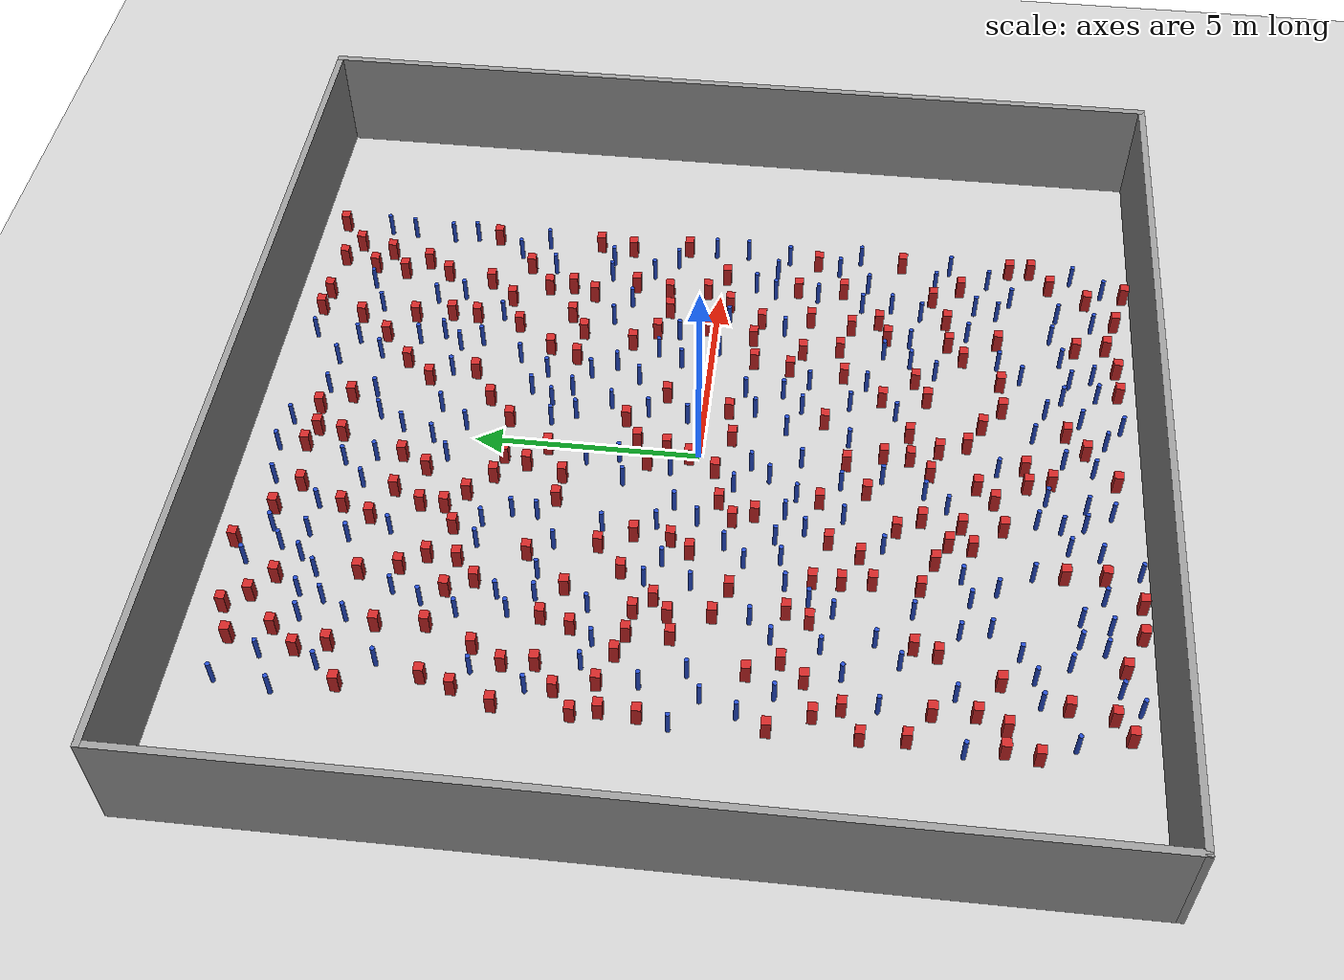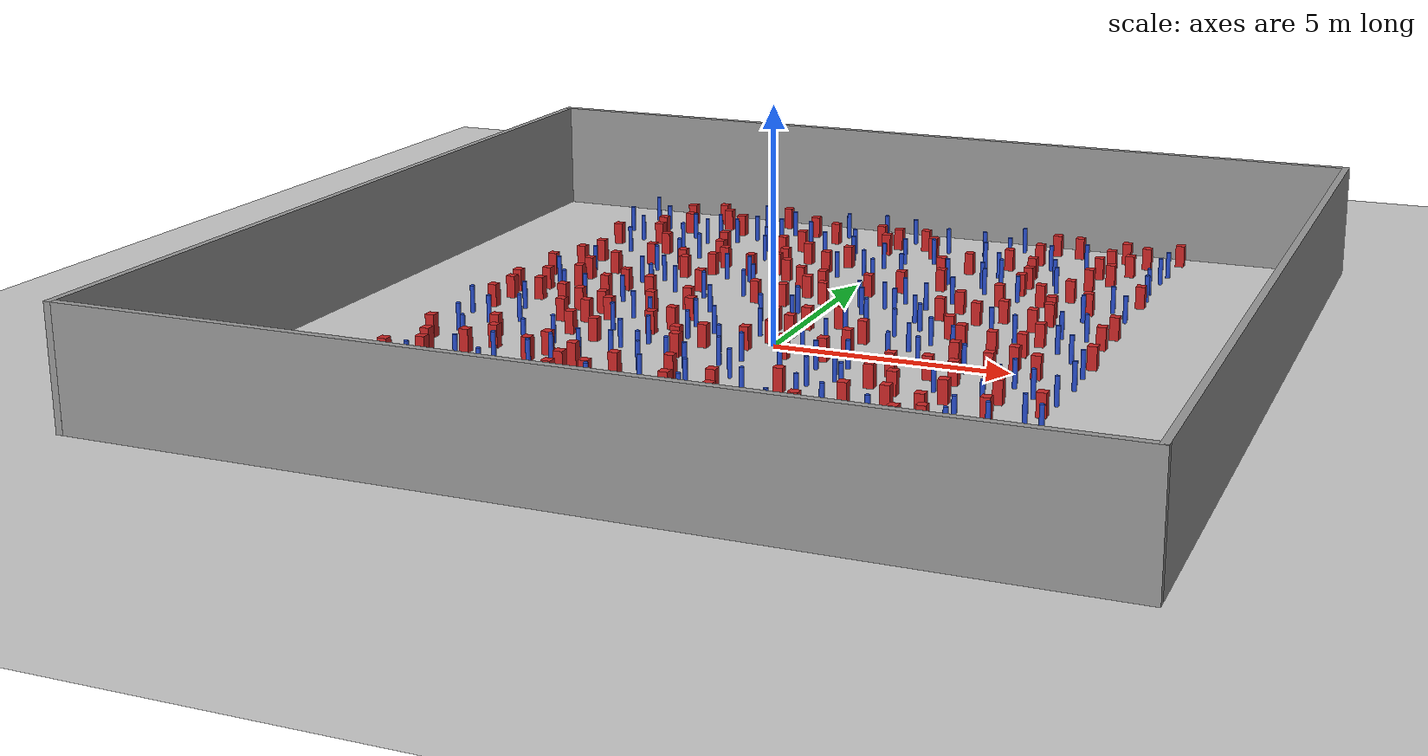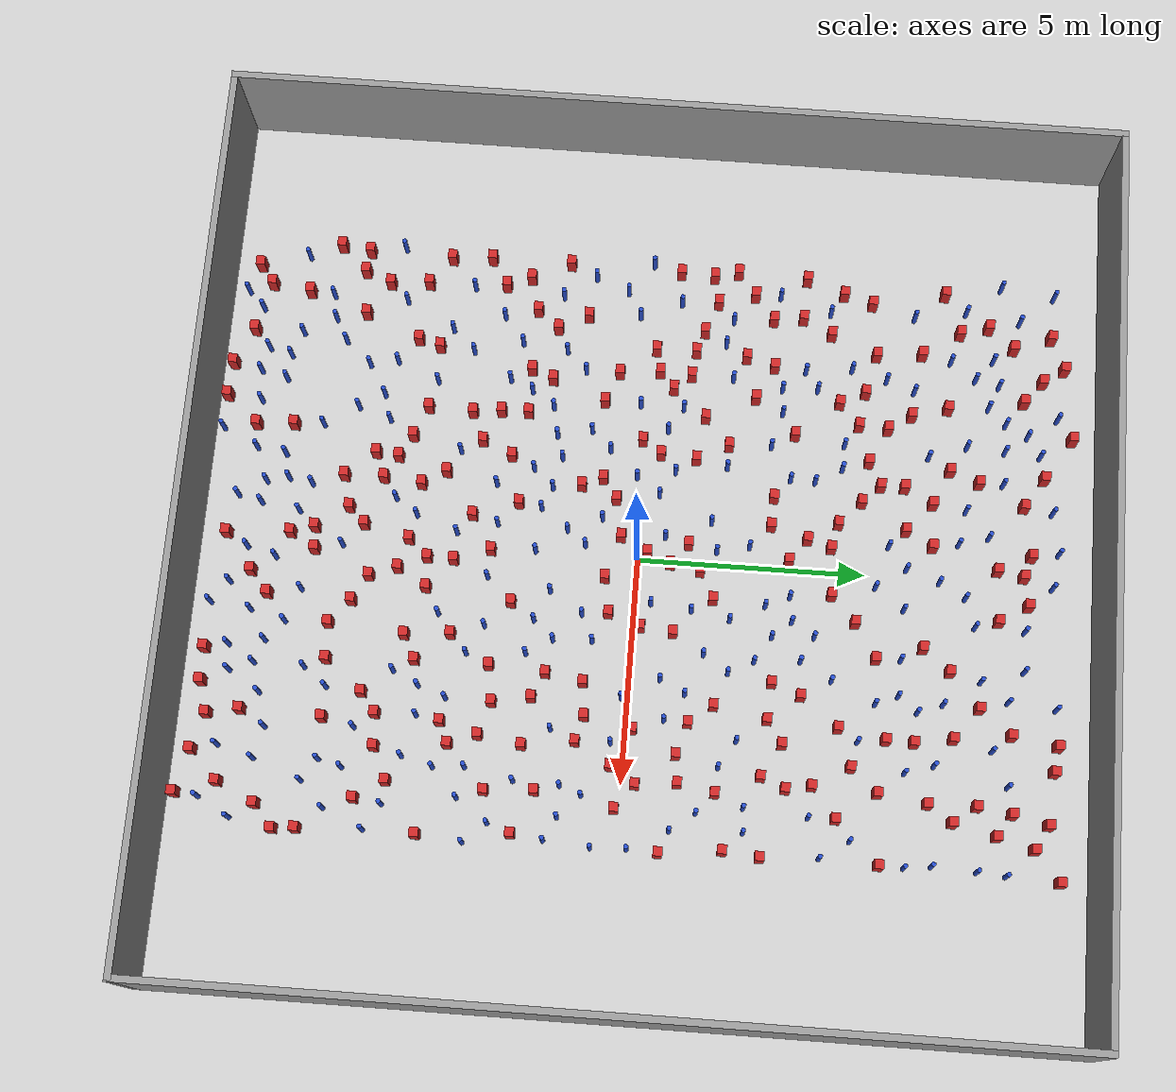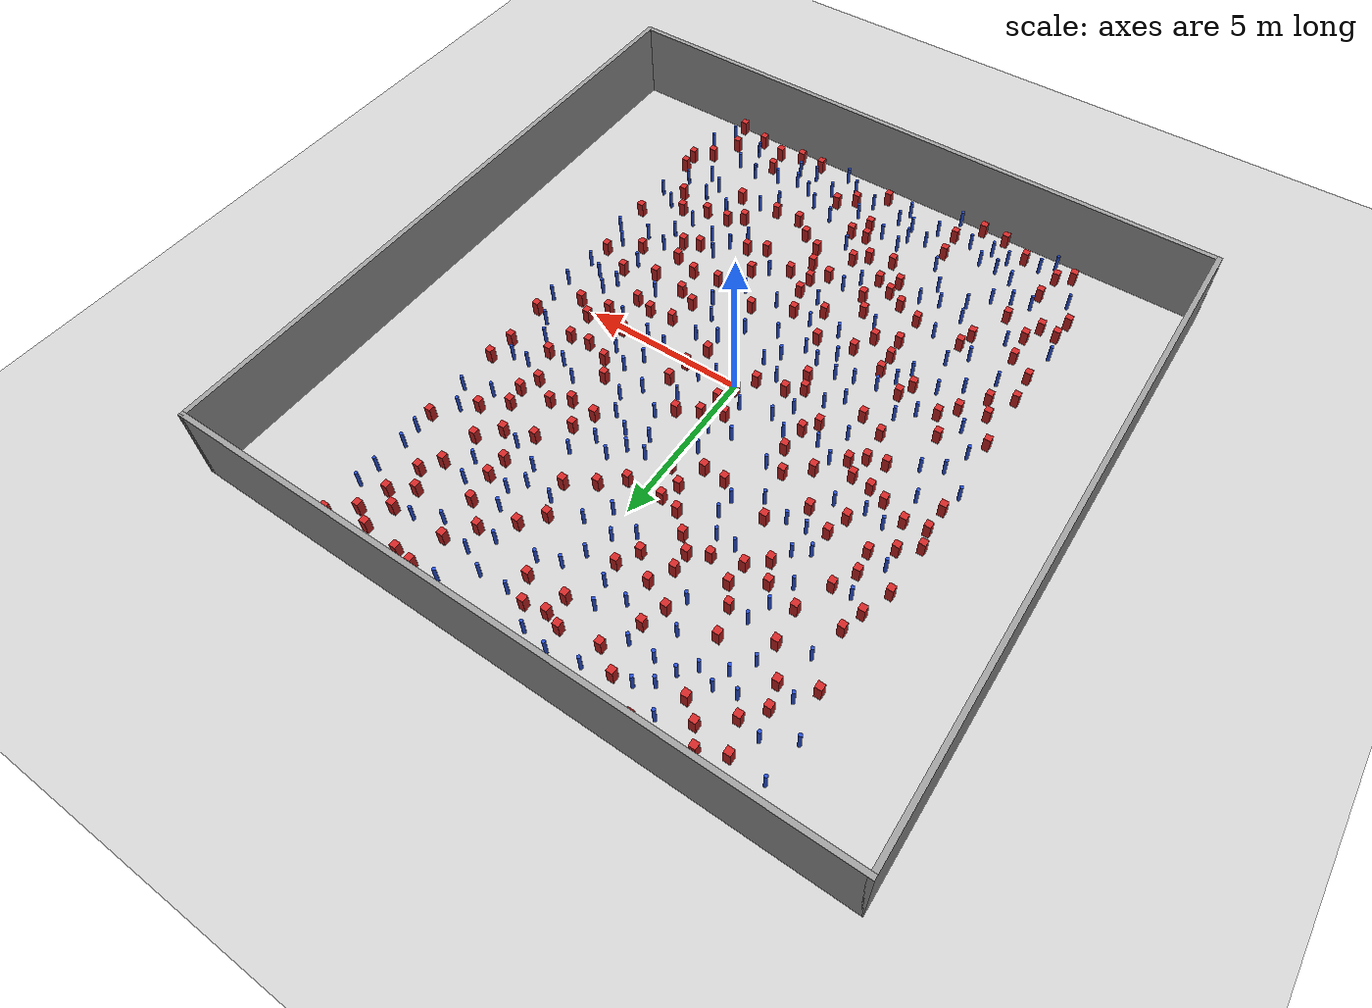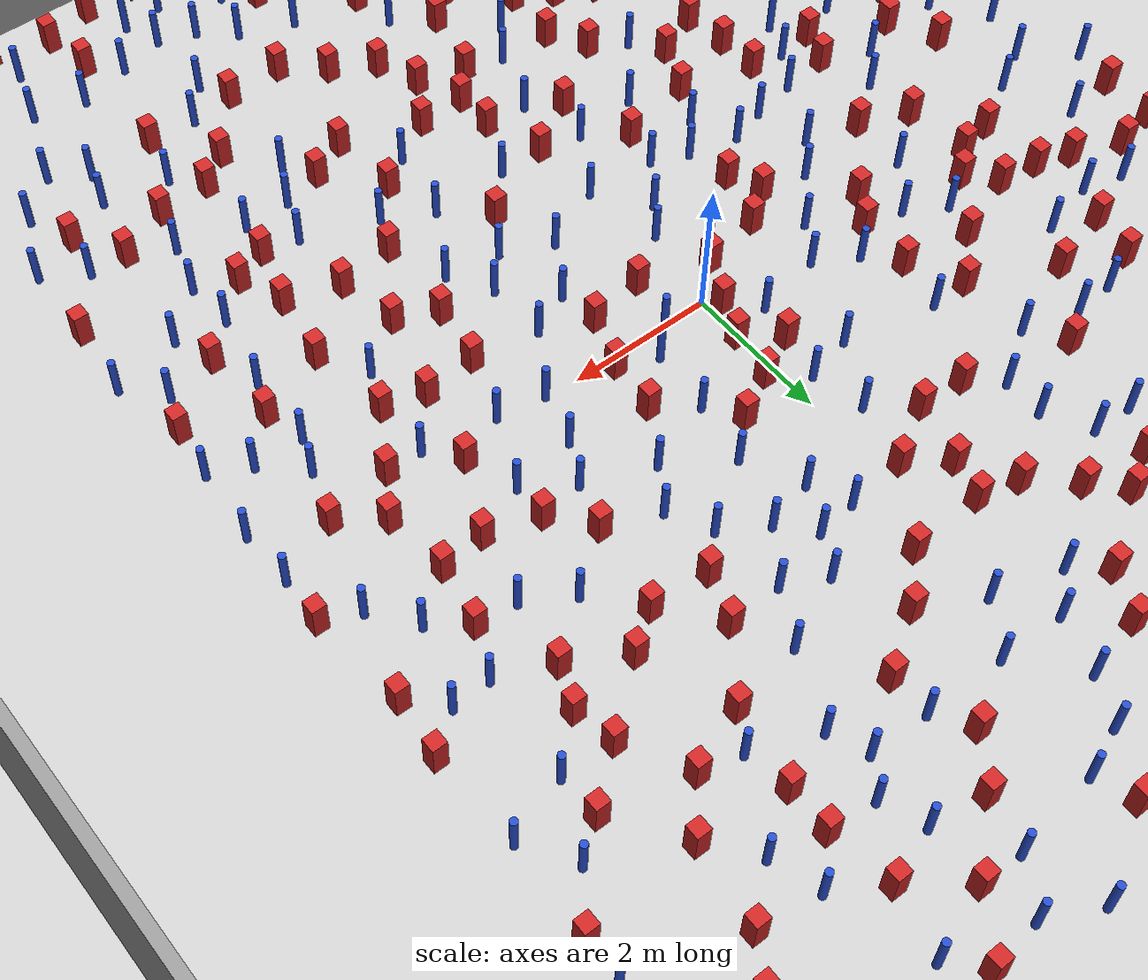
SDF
<sdf version="1.6">
 <world name="default">
  <light name="sun" type="directional">
   <pose>0 0 1000 0 -0 0</pose>
   <diffuse>0.8 0.8 0.8 1</diffuse>
   <specular>0.1 0.1 0.1 1</specular>
   <attenuation>
    <range>1000</range>
    <constant>0.9</constant>
    <linear>0.01</linear>
    <quadratic>0.001</quadratic>
   </attenuation>
   <direction>-0.5 0.5 -1</direction>
  </light>
  <model name="ground_plane">
   <static>1</static>
   <link name="link">
    <collision name="collision">
     <geometry><plane><normal>0 0 1</normal><size>100 100</size></plane></geometry>
     <surface><friction><ode><mu>100</mu><mu2>50</mu2></ode></friction></surface>
    </collision>
    <visual name="visual">
     <cast_shadows>0</cast_shadows>
     <geometry><plane><normal>0 0 1</normal><size>100 100</size></plane></geometry>
     <material>
      <ambient>1.0 1.0 1.0 1.0</ambient>
      <diffuse>0.8 0.8 0.8 1.0</diffuse>
      <specular>0.01 0.01 0.01 1.000000</specular>
     </material>
    </visual>
   </link>
  </model>
  <gravity>0 0 -9.8</gravity>
  <magnetic_field>6e-06 2.3e-05 -4.2e-05</magnetic_field>
  <atmosphere type="adiabatic"/>
  <physics name="default_physics" default="0" type="ode">
   <max_step_size>0.001</max_step_size>
   <real_time_factor>1</real_time_factor>
   <real_time_update_rate>1000</real_time_update_rate>
  </physics>
  <scene><ambient>0.4 0.4 0.4 1</ambient><background>0.7 0.7 0.7 1</background><shadows>1</shadows></scene>
  <spherical_coordinates>
   <surface_model>EARTH_WGS84</surface_model>
   <latitude_deg>0</latitude_deg>
   <longitude_deg>0</longitude_deg>
   <elevation>0</elevation>
   <heading_deg>0</heading_deg>
  </spherical_coordinates>
  <plugin name="gazebo_occupancy_map" filename="libgazebo_2Dmap_plugin.so">
   <map_resolution>0.05</map_resolution>
   <map_topic>generated_map</map_topic>
   <map_height>0.01</map_height>
   <map_size_x>50</map_size_x>
   <map_size_y>50</map_size_y>
  </plugin>
  <model name="NamedLocations">
   <static>true</static>
   <link name="DefaultStart"><pose>8.5 0 0 0 0 3.14</pose></link>
  </model>
  <model name="20x20_walls">
   <pose>0.044518 0.176112 0 0 -0 0</pose>
   <link name="Wall_1">
    <collision name="Wall_1_Collision">
     <geometry><box><size>20 0.15 2.5</size></box></geometry>
     <pose>0 0 1.25 0 -0 0</pose>
    </collision>
    <visual name="Wall_1_Visual">
     <pose>0 0 1.25 0 -0 0</pose>
     <geometry><box><size>20 0.15 2.5</size></box></geometry>
     <material>
      <script><uri>file://media/materials/scripts/gazebo.material</uri><name>Gazebo/Grey</name></script>
      <ambient>0.976471 0.992157 1 1</ambient>
     </material>
     <meta><layer>0</layer></meta>
    </visual>
    <pose>0 9.925 0 0 -0 0</pose>
   </link>
   <link name="Wall_3">
    <collision name="Wall_3_Collision">
     <geometry><box><size>20 0.15 2.5</size></box></geometry>
     <pose>0 0 1.25 0 -0 0</pose>
    </collision>
    <visual name="Wall_3_Visual">
     <pose>0 0 1.25 0 -0 0</pose>
     <geometry><box><size>20 0.15 2.5</size></box></geometry>
     <material>
      <script><uri>file://media/materials/scripts/gazebo.material</uri><name>Gazebo/Grey</name></script>
      <ambient>0.976471 0.992157 1 1</ambient>
     </material>
     <meta><layer>0</layer></meta>
    </visual>
    <pose>9.925 0 0 0 0 -1.5708</pose>
   </link>
   <link name="Wall_4">
    <collision name="Wall_4_Collision">
     <geometry><box><size>20 0.15 2.5</size></box></geometry>
     <pose>0 0 1.25 0 -0 0</pose>
    </collision>
    <visual name="Wall_4_Visual">
     <pose>0 0 1.25 0 -0 0</pose>
     <geometry><box><size>20 0.15 2.5</size></box></geometry>
     <material>
      <script><uri>file://media/materials/scripts/gazebo.material</uri><name>Gazebo/Grey</name></script>
      <ambient>0.976471 0.992157 1 1</ambient>
     </material>
     <meta><layer>0</layer></meta>
    </visual>
    <pose>0 -9.925 0 0 -0 3.14159</pose>
   </link>
   <link name="Wall_5">
    <collision name="Wall_5_Collision">
     <geometry><box><size>20 0.15 2.5</size></box></geometry>
     <pose>0 0 1.25 0 -0 0</pose>
    </collision>
    <visual name="Wall_5_Visual">
     <pose>0 0 1.25 0 -0 0</pose>
     <geometry><box><size>20 0.15 2.5</size></box></geometry>
     <material>
      <script><uri>file://media/materials/scripts/gazebo.material</uri><name>Gazebo/Grey</name></script>
      <ambient>0.976471 0.992157 1 1</ambient>
     </material>
     <meta><layer>0</layer></meta>
    </visual>
    <pose>-9.925 0 0 0 -0 1.5708</pose>
   </link>
   <static>1</static>
  </model>
  <model name="square_post_obstacle0">
   <static>true</static>
   <pose>0.990860000591 -4.58058175635 1.91545236811e-07 -7.35059704564e-06 1.12565212e-07 2.39332434364e-05</pose>
   <link name="link">
    <pose>0 0 0.25 0 -0 0</pose>
    <inertial>
     <mass>100</mass>
     <inertia>
      <ixx>0.166667</ixx>
      <ixy>0</ixy>
      <ixz>0</ixz>
      <iyy>0.166667</iyy>
      <iyz>0</iyz>
      <izz>0.166667</izz>
     </inertia>
    </inertial>
    <collision name="collision"><geometry><box><size>.2 .2 .5</size></box></geometry></collision>
    <visual name="visual">
     <geometry><box><size>.2 .2 .5</size></box></geometry>
     <material>
      <script><name>Gazebo/Red</name><uri>file://media/materials/scripts/gazebo.material</uri></script>
     </material>
    </visual>
   </link>
  </model>
  <model name="square_post_obstacle1">
   <static>true</static>
   <pose>2.71421967081 -1.80625140036 1.91545236811e-07 -7.35059704564e-06 1.12565212e-07 2.39332434364e-05</pose>
   <link name="link">
    <pose>0 0 0.25 0 -0 0</pose>
    <inertial>
     <mass>100</mass>
     <inertia>
      <ixx>0.166667</ixx>
      <ixy>0</ixy>
      <ixz>0</ixz>
      <iyy>0.166667</iyy>
      <iyz>0</iyz>
      <izz>0.166667</izz>
     </inertia>
    </inertial>
    <collision name="collision"><geometry><box><size>.2 .2 .5</size></box></geometry></collision>
    <visual name="visual">
     <geometry><box><size>.2 .2 .5</size></box></geometry>
     <material>
      <script><name>Gazebo/Red</name><uri>file://media/materials/scripts/gazebo.material</uri></script>
     </material>
    </visual>
   </link>
  </model>
  <model name="pole_obstacle0">
   <static>true</static>
   <pose>2.05534213847 1.58425877043 7.38925637345e-09 -8.471706928e-08 1.24976765152e-08 -1.74513093012e-07</pose>
   <link name="link">
    <pose>0 0 0.3 0 -0 0</pose>
    <inertial>
     <mass>1</mass>
     <inertia><ixx>0.145833</ixx><ixy>0</ixy><ixz>0</ixz><iyy>0.145833</iyy><iyz>0</iyz><izz>0.125</izz></inertia>
    </inertial>
    <collision name="collision">
     <geometry><cylinder><radius>0.05</radius><length>.6</length></cylinder></geometry>
    </collision>
    <visual name="visual">
     <geometry><cylinder><radius>0.05</radius><length>.6</length></cylinder></geometry>
     <material>
      <script><name>Gazebo/Blue</name><uri>file://media/materials/scripts/gazebo.material</uri></script>
     </material>
    </visual>
   </link>
  </model>
  <model name="square_post_obstacle2">
   <static>true</static>
   <pose>-1.6450809916 4.86027986707 1.91545236811e-07 -7.35059704564e-06 1.12565212e-07 2.39332434364e-05</pose>
   <link name="link">
    <pose>0 0 0.25 0 -0 0</pose>
    <inertial>
     <mass>100</mass>
     <inertia>
      <ixx>0.166667</ixx>
      <ixy>0</ixy>
      <ixz>0</ixz>
      <iyy>0.166667</iyy>
      <iyz>0</iyz>
      <izz>0.166667</izz>
     </inertia>
    </inertial>
    <collision name="collision"><geometry><box><size>.2 .2 .5</size></box></geometry></collision>
    <visual name="visual">
     <geometry><box><size>.2 .2 .5</size></box></geometry>
     <material>
      <script><name>Gazebo/Red</name><uri>file://media/materials/scripts/gazebo.material</uri></script>
     </material>
    </visual>
   </link>
  </model>
  <model name="pole_obstacle1">
   <static>true</static>
   <pose>4.74901094641 -4.74037949333 7.38925637345e-09 -8.47170692796e-08 1.24976764786e-08 -1.74513093032e-07</pose>
   <link name="link">
    <pose>0 0 0.3 0 -0 0</pose>
    <inertial>
     <mass>1</mass>
     <inertia><ixx>0.145833</ixx><ixy>0</ixy><ixz>0</ixz><iyy>0.145833</iyy><iyz>0</iyz><izz>0.125</izz></inertia>
    </inertial>
    <collision name="collision">
     <geometry><cylinder><radius>0.05</radius><length>.6</length></cylinder></geometry>
    </collision>
    <visual name="visual">
     <geometry><cylinder><radius>0.05</radius><length>.6</length></cylinder></geometry>
     <material>
      <script><name>Gazebo/Blue</name><uri>file://media/materials/scripts/gazebo.material</uri></script>
     </material>
    </visual>
   </link>
  </model>
  <model name="square_post_obstacle3">
   <static>true</static>
   <pose>-1.10719621813 4.36680320502 1.91545236811e-07 -7.35059704564e-06 1.12565212e-07 2.39332434364e-05</pose>
   <link name="link">
    <pose>0 0 0.25 0 -0 0</pose>
    <inertial>
     <mass>100</mass>
     <inertia>
      <ixx>0.166667</ixx>
      <ixy>0</ixy>
      <ixz>0</ixz>
      <iyy>0.166667</iyy>
      <iyz>0</iyz>
      <izz>0.166667</izz>
     </inertia>
    </inertial>
    <collision name="collision"><geometry><box><size>.2 .2 .5</size></box></geometry></collision>
    <visual name="visual">
     <geometry><box><size>.2 .2 .5</size></box></geometry>
     <material>
      <script><name>Gazebo/Red</name><uri>file://media/materials/scripts/gazebo.material</uri></script>
     </material>
    </visual>
   </link>
  </model>
  <model name="pole_obstacle2">
   <static>true</static>
   <pose>1.97071160318 -7.58667702592 7.38925637345e-09 -8.471706928e-08 1.24976765202e-08 -1.7451309301e-07</pose>
   <link name="link">
    <pose>0 0 0.3 0 -0 0</pose>
    <inertial>
     <mass>1</mass>
     <inertia><ixx>0.145833</ixx><ixy>0</ixy><ixz>0</ixz><iyy>0.145833</iyy><iyz>0</iyz><izz>0.125</izz></inertia>
    </inertial>
    <collision name="collision">
     <geometry><cylinder><radius>0.05</radius><length>.6</length></cylinder></geometry>
    </collision>
    <visual name="visual">
     <geometry><cylinder><radius>0.05</radius><length>.6</length></cylinder></geometry>
     <material>
      <script><name>Gazebo/Blue</name><uri>file://media/materials/scripts/gazebo.material</uri></script>
     </material>
    </visual>
   </link>
  </model>
  <model name="pole_obstacle3">
   <static>true</static>
   <pose>1.2492648832 2.10685251621 7.38925637345e-09 -8.47170692799e-08 1.24976765053e-08 -1.74513093017e-07</pose>
   <link name="link">
    <pose>0 0 0.3 0 -0 0</pose>
    <inertial>
     <mass>1</mass>
     <inertia><ixx>0.145833</ixx><ixy>0</ixy><ixz>0</ixz><iyy>0.145833</iyy><iyz>0</iyz><izz>0.125</izz></inertia>
    </inertial>
    <collision name="collision">
     <geometry><cylinder><radius>0.05</radius><length>.6</length></cylinder></geometry>
    </collision>
    <visual name="visual">
     <geometry><cylinder><radius>0.05</radius><length>.6</length></cylinder></geometry>
     <material>
      <script><name>Gazebo/Blue</name><uri>file://media/materials/scripts/gazebo.material</uri></script>
     </material>
    </visual>
   </link>
  </model>
  <model name="square_post_obstacle4">
   <static>true</static>
   <pose>2.06318571931 6.94088861574 1.91545236811e-07 -7.35059704564e-06 1.12565212e-07 2.39332434364e-05</pose>
   <link name="link">
    <pose>0 0 0.25 0 -0 0</pose>
    <inertial>
     <mass>100</mass>
     <inertia>
      <ixx>0.166667</ixx>
      <ixy>0</ixy>
      <ixz>0</ixz>
      <iyy>0.166667</iyy>
      <iyz>0</iyz>
      <izz>0.166667</izz>
     </inertia>
    </inertial>
    <collision name="collision"><geometry><box><size>.2 .2 .5</size></box></geometry></collision>
    <visual name="visual">
     <geometry><box><size>.2 .2 .5</size></box></geometry>
     <material>
      <script><name>Gazebo/Red</name><uri>file://media/materials/scripts/gazebo.material</uri></script>
     </material>
    </visual>
   </link>
  </model>
  <model name="square_post_obstacle5">
   <static>true</static>
   <pose>-2.05064613775 5.79552870133 1.91545236811e-07 -7.35059704564e-06 1.12565212e-07 2.39332434364e-05</pose>
   <link name="link">
    <pose>0 0 0.25 0 -0 0</pose>
    <inertial>
     <mass>100</mass>
     <inertia>
      <ixx>0.166667</ixx>
      <ixy>0</ixy>
      <ixz>0</ixz>
      <iyy>0.166667</iyy>
      <iyz>0</iyz>
      <izz>0.166667</izz>
     </inertia>
    </inertial>
    <collision name="collision"><geometry><box><size>.2 .2 .5</size></box></geometry></collision>
    <visual name="visual">
     <geometry><box><size>.2 .2 .5</size></box></geometry>
     <material>
      <script><name>Gazebo/Red</name><uri>file://media/materials/scripts/gazebo.material</uri></script>
     </material>
    </visual>
   </link>
  </model>
  <model name="square_post_obstacle6">
   <static>true</static>
   <pose>3.42528673768 -9.2332077088 1.91545236811e-07 -7.35059704564e-06 1.12565212e-07 2.39332434364e-05</pose>
   <link name="link">
    <pose>0 0 0.25 0 -0 0</pose>
    <inertial>
     <mass>100</mass>
     <inertia>
      <ixx>0.166667</ixx>
      <ixy>0</ixy>
      <ixz>0</ixz>
      <iyy>0.166667</iyy>
      <iyz>0</iyz>
      <izz>0.166667</izz>
     </inertia>
    </inertial>
    <collision name="collision"><geometry><box><size>.2 .2 .5</size></box></geometry></collision>
    <visual name="visual">
     <geometry><box><size>.2 .2 .5</size></box></geometry>
     <material>
      <script><name>Gazebo/Red</name><uri>file://media/materials/scripts/gazebo.material</uri></script>
     </material>
    </visual>
   </link>
  </model>
  <model name="pole_obstacle4">
   <static>true</static>
   <pose>-6.97828642345 -0.122020516377 7.38925637345e-09 -8.47170692799e-08 1.24976765077e-08 -1.74513093018e-07</pose>
   <link name="link">
    <pose>0 0 0.3 0 -0 0</pose>
    <inertial>
     <mass>1</mass>
     <inertia><ixx>0.145833</ixx><ixy>0</ixy><ixz>0</ixz><iyy>0.145833</iyy><iyz>0</iyz><izz>0.125</izz></inertia>
    </inertial>
    <collision name="collision">
     <geometry><cylinder><radius>0.05</radius><length>.6</length></cylinder></geometry>
    </collision>
    <visual name="visual">
     <geometry><cylinder><radius>0.05</radius><length>.6</length></cylinder></geometry>
     <material>
      <script><name>Gazebo/Blue</name><uri>file://media/materials/scripts/gazebo.material</uri></script>
     </material>
    </visual>
   </link>
  </model>
  <model name="pole_obstacle5">
   <static>true</static>
   <pose>-0.821117098225 7.03895343085 7.38925637345e-09 -8.471706928e-08 1.24976765086e-08 -1.74513093015e-07</pose>
   <link name="link">
    <pose>0 0 0.3 0 -0 0</pose>
    <inertial>
     <mass>1</mass>
     <inertia><ixx>0.145833</ixx><ixy>0</ixy><ixz>0</ixz><iyy>0.145833</iyy><iyz>0</iyz><izz>0.125</izz></inertia>
    </inertial>
    <collision name="collision">
     <geometry><cylinder><radius>0.05</radius><length>.6</length></cylinder></geometry>
    </collision>
    <visual name="visual">
     <geometry><cylinder><radius>0.05</radius><length>.6</length></cylinder></geometry>
     <material>
      <script><name>Gazebo/Blue</name><uri>file://media/materials/scripts/gazebo.material</uri></script>
     </material>
    </visual>
   </link>
  </model>
  <model name="square_post_obstacle7">
   <static>true</static>
   <pose>-3.36972529665 1.28270405987 1.91545236811e-07 -7.35059704564e-06 1.12565212e-07 2.39332434364e-05</pose>
   <link name="link">
    <pose>0 0 0.25 0 -0 0</pose>
    <inertial>
     <mass>100</mass>
     <inertia>
      <ixx>0.166667</ixx>
      <ixy>0</ixy>
      <ixz>0</ixz>
      <iyy>0.166667</iyy>
      <iyz>0</iyz>
      <izz>0.166667</izz>
     </inertia>
    </inertial>
    <collision name="collision"><geometry><box><size>.2 .2 .5</size></box></geometry></collision>
    <visual name="visual">
     <geometry><box><size>.2 .2 .5</size></box></geometry>
     <material>
      <script><name>Gazebo/Red</name><uri>file://media/materials/scripts/gazebo.material</uri></script>
     </material>
    </visual>
   </link>
  </model>
  <model name="square_post_obstacle8">
   <static>true</static>
   <pose>-2.46629739151 8.88326474359 1.91545236811e-07 -7.35059704564e-06 1.12565212e-07 2.39332434364e-05</pose>
   <link name="link">
    <pose>0 0 0.25 0 -0 0</pose>
    <inertial>
     <mass>100</mass>
     <inertia>
      <ixx>0.166667</ixx>
      <ixy>0</ixy>
      <ixz>0</ixz>
      <iyy>0.166667</iyy>
      <iyz>0</iyz>
      <izz>0.166667</izz>
     </inertia>
    </inertial>
    <collision name="collision"><geometry><box><size>.2 .2 .5</size></box></geometry></collision>
    <visual name="visual">
     <geometry><box><size>.2 .2 .5</size></box></geometry>
     <material>
      <script><name>Gazebo/Red</name><uri>file://media/materials/scripts/gazebo.material</uri></script>
     </material>
    </visual>
   </link>
  </model>
  <model name="pole_obstacle6">
   <static>true</static>
   <pose>-5.47152943793 -3.41896249044 7.38925637345e-09 -8.47170692798e-08 1.24976764937e-08 -1.74513093023e-07</pose>
   <link name="link">
    <pose>0 0 0.3 0 -0 0</pose>
    <inertial>
     <mass>1</mass>
     <inertia><ixx>0.145833</ixx><ixy>0</ixy><ixz>0</ixz><iyy>0.145833</iyy><iyz>0</iyz><izz>0.125</izz></inertia>
    </inertial>
    <collision name="collision">
     <geometry><cylinder><radius>0.05</radius><length>.6</length></cylinder></geometry>
    </collision>
    <visual name="visual">
     <geometry><cylinder><radius>0.05</radius><length>.6</length></cylinder></geometry>
     <material>
      <script><name>Gazebo/Blue</name><uri>file://media/materials/scripts/gazebo.material</uri></script>
     </material>
    </visual>
   </link>
  </model>
  <model name="pole_obstacle7">
   <static>true</static>
   <pose>2.65087221747 8.22384268109 7.38925637345e-09 -8.47170692793e-08 1.24976764408e-08 -1.74513093041e-07</pose>
   <link name="link">
    <pose>0 0 0.3 0 -0 0</pose>
    <inertial>
     <mass>1</mass>
     <inertia><ixx>0.145833</ixx><ixy>0</ixy><ixz>0</ixz><iyy>0.145833</iyy><iyz>0</iyz><izz>0.125</izz></inertia>
    </inertial>
    <collision name="collision">
     <geometry><cylinder><radius>0.05</radius><length>.6</length></cylinder></geometry>
    </collision>
    <visual name="visual">
     <geometry><cylinder><radius>0.05</radius><length>.6</length></cylinder></geometry>
     <material>
      <script><name>Gazebo/Blue</name><uri>file://media/materials/scripts/gazebo.material</uri></script>
     </material>
    </visual>
   </link>
  </model>
  <model name="square_post_obstacle9">
   <static>true</static>
   <pose>-4.9279009625 0.974077663801 1.91545236811e-07 -7.35059704564e-06 1.12565212e-07 2.39332434364e-05</pose>
   <link name="link">
    <pose>0 0 0.25 0 -0 0</pose>
    <inertial>
     <mass>100</mass>
     <inertia>
      <ixx>0.166667</ixx>
      <ixy>0</ixy>
      <ixz>0</ixz>
      <iyy>0.166667</iyy>
      <iyz>0</iyz>
      <izz>0.166667</izz>
     </inertia>
    </inertial>
    <collision name="collision"><geometry><box><size>.2 .2 .5</size></box></geometry></collision>
    <visual name="visual">
     <geometry><box><size>.2 .2 .5</size></box></geometry>
     <material>
      <script><name>Gazebo/Red</name><uri>file://media/materials/scripts/gazebo.material</uri></script>
     </material>
    </visual>
   </link>
  </model>
  <model name="square_post_obstacle10">
   <static>true</static>
   <pose>6.42466675228 0.901377303321 1.91545236811e-07 -7.35059704564e-06 1.12565212e-07 2.39332434364e-05</pose>
   <link name="link">
    <pose>0 0 0.25 0 -0 0</pose>
    <inertial>
     <mass>100</mass>
     <inertia>
      <ixx>0.166667</ixx>
      <ixy>0</ixy>
      <ixz>0</ixz>
      <iyy>0.166667</iyy>
      <iyz>0</iyz>
      <izz>0.166667</izz>
     </inertia>
    </inertial>
    <collision name="collision"><geometry><box><size>.2 .2 .5</size></box></geometry></collision>
    <visual name="visual">
     <geometry><box><size>.2 .2 .5</size></box></geometry>
     <material>
      <script><name>Gazebo/Red</name><uri>file://media/materials/scripts/gazebo.material</uri></script>
     </material>
    </visual>
   </link>
  </model>
  <model name="square_post_obstacle11">
   <static>true</static>
   <pose>4.16472418414 -1.04520851268 1.91545236811e-07 -7.35059704564e-06 1.12565212e-07 2.39332434364e-05</pose>
   <link name="link">
    <pose>0 0 0.25 0 -0 0</pose>
    <inertial>
     <mass>100</mass>
     <inertia>
      <ixx>0.166667</ixx>
      <ixy>0</ixy>
      <ixz>0</ixz>
      <iyy>0.166667</iyy>
      <iyz>0</iyz>
      <izz>0.166667</izz>
     </inertia>
    </inertial>
    <collision name="collision"><geometry><box><size>.2 .2 .5</size></box></geometry></collision>
    <visual name="visual">
     <geometry><box><size>.2 .2 .5</size></box></geometry>
     <material>
      <script><name>Gazebo/Red</name><uri>file://media/materials/scripts/gazebo.material</uri></script>
     </material>
    </visual>
   </link>
  </model>
  <model name="square_post_obstacle12">
   <static>true</static>
   <pose>4.32945033488 -2.18687823844 1.91545236811e-07 -7.35059704564e-06 1.12565212e-07 2.39332434364e-05</pose>
   <link name="link">
    <pose>0 0 0.25 0 -0 0</pose>
    <inertial>
     <mass>100</mass>
     <inertia>
      <ixx>0.166667</ixx>
      <ixy>0</ixy>
      <ixz>0</ixz>
      <iyy>0.166667</iyy>
      <iyz>0</iyz>
      <izz>0.166667</izz>
     </inertia>
    </inertial>
    <collision name="collision"><geometry><box><size>.2 .2 .5</size></box></geometry></collision>
    <visual name="visual">
     <geometry><box><size>.2 .2 .5</size></box></geometry>
     <material>
      <script><name>Gazebo/Red</name><uri>file://media/materials/scripts/gazebo.material</uri></script>
     </material>
    </visual>
   </link>
  </model>
  <model name="square_post_obstacle13">
   <static>true</static>
   <pose>3.93736923394 -3.98373946627 1.91545236811e-07 -7.35059704564e-06 1.12565212e-07 2.39332434364e-05</pose>
   <link name="link">
    <pose>0 0 0.25 0 -0 0</pose>
    <inertial>
     <mass>100</mass>
     <inertia>
      <ixx>0.166667</ixx>
      <ixy>0</ixy>
      <ixz>0</ixz>
      <iyy>0.166667</iyy>
      <iyz>0</iyz>
      <izz>0.166667</izz>
     </inertia>
    </inertial>
    <collision name="collision"><geometry><box><size>.2 .2 .5</size></box></geometry></collision>
    <visual name="visual">
     <geometry><box><size>.2 .2 .5</size></box></geometry>
     <material>
      <script><name>Gazebo/Red</name><uri>file://media/materials/scripts/gazebo.material</uri></script>
     </material>
    </visual>
   </link>
  </model>
  <model name="pole_obstacle8">
   <static>true</static>
   <pose>-3.40156474789 -5.95213894236 7.38925637345e-09 -8.47170692798e-08 1.24976765033e-08 -1.74513093019e-07</pose>
   <link name="link">
    <pose>0 0 0.3 0 -0 0</pose>
    <inertial>
     <mass>1</mass>
     <inertia><ixx>0.145833</ixx><ixy>0</ixy><ixz>0</ixz><iyy>0.145833</iyy><iyz>0</iyz><izz>0.125</izz></inertia>
    </inertial>
    <collision name="collision">
     <geometry><cylinder><radius>0.05</radius><length>.6</length></cylinder></geometry>
    </collision>
    <visual name="visual">
     <geometry><cylinder><radius>0.05</radius><length>.6</length></cylinder></geometry>
     <material>
      <script><name>Gazebo/Blue</name><uri>file://media/materials/scripts/gazebo.material</uri></script>
     </material>
    </visual>
   </link>
  </model>
  <model name="square_post_obstacle14">
   <static>true</static>
   <pose>4.64269038231 2.97652837888 1.91545236811e-07 -7.35059704564e-06 1.12565212e-07 2.39332434364e-05</pose>
   <link name="link">
    <pose>0 0 0.25 0 -0 0</pose>
    <inertial>
     <mass>100</mass>
     <inertia>
      <ixx>0.166667</ixx>
      <ixy>0</ixy>
      <ixz>0</ixz>
      <iyy>0.166667</iyy>
      <iyz>0</iyz>
      <izz>0.166667</izz>
     </inertia>
    </inertial>
    <collision name="collision"><geometry><box><size>.2 .2 .5</size></box></geometry></collision>
    <visual name="visual">
     <geometry><box><size>.2 .2 .5</size></box></geometry>
     <material>
      <script><name>Gazebo/Red</name><uri>file://media/materials/scripts/gazebo.material</uri></script>
     </material>
    </visual>
   </link>
  </model>
  <model name="square_post_obstacle15">
   <static>true</static>
   <pose>3.27139853882 -2.06537505746 1.91545236811e-07 -7.35059704564e-06 1.12565212e-07 2.39332434364e-05</pose>
   <link name="link">
    <pose>0 0 0.25 0 -0 0</pose>
    <inertial>
     <mass>100</mass>
     <inertia>
      <ixx>0.166667</ixx>
      <ixy>0</ixy>
      <ixz>0</ixz>
      <iyy>0.166667</iyy>
      <iyz>0</iyz>
      <izz>0.166667</izz>
     </inertia>
    </inertial>
    <collision name="collision"><geometry><box><size>.2 .2 .5</size></box></geometry></collision>
    <visual name="visual">
     <geometry><box><size>.2 .2 .5</size></box></geometry>
     <material>
      <script><name>Gazebo/Red</name><uri>file://media/materials/scripts/gazebo.material</uri></script>
     </material>
    </visual>
   </link>
  </model>
  <model name="square_post_obstacle16">
   <static>true</static>
   <pose>6.40038456204 -4.26295170699 1.91545236811e-07 -7.35059704564e-06 1.12565212e-07 2.39332434364e-05</pose>
   <link name="link">
    <pose>0 0 0.25 0 -0 0</pose>
    <inertial>
     <mass>100</mass>
     <inertia>
      <ixx>0.166667</ixx>
      <ixy>0</ixy>
      <ixz>0</ixz>
      <iyy>0.166667</iyy>
      <iyz>0</iyz>
      <izz>0.166667</izz>
     </inertia>
    </inertial>
    <collision name="collision"><geometry><box><size>.2 .2 .5</size></box></geometry></collision>
    <visual name="visual">
     <geometry><box><size>.2 .2 .5</size></box></geometry>
     <material>
      <script><name>Gazebo/Red</name><uri>file://media/materials/scripts/gazebo.material</uri></script>
     </material>
    </visual>
   </link>
  </model>
  <model name="pole_obstacle9">
   <static>true</static>
   <pose>1.56069903557 3.04466221461 7.38925637345e-09 -8.47170692799e-08 1.24976765053e-08 -1.74513093017e-07</pose>
   <link name="link">
    <pose>0 0 0.3 0 -0 0</pose>
    <inertial>
     <mass>1</mass>
     <inertia><ixx>0.145833</ixx><ixy>0</ixy><ixz>0</ixz><iyy>0.145833</iyy><iyz>0</iyz><izz>0.125</izz></inertia>
    </inertial>
    <collision name="collision">
     <geometry><cylinder><radius>0.05</radius><length>.6</length></cylinder></geometry>
    </collision>
    <visual name="visual">
     <geometry><cylinder><radius>0.05</radius><length>.6</length></cylinder></geometry>
     <material>
      <script><name>Gazebo/Blue</name><uri>file://media/materials/scripts/gazebo.material</uri></script>
     </material>
    </visual>
   </link>
  </model>
  <model name="square_post_obstacle17">
   <static>true</static>
   <pose>4.64287896058 -0.257560174505 1.91545236811e-07 -7.35059704564e-06 1.12565212e-07 2.39332434364e-05</pose>
   <link name="link">
    <pose>0 0 0.25 0 -0 0</pose>
    <inertial>
     <mass>100</mass>
     <inertia>
      <ixx>0.166667</ixx>
      <ixy>0</ixy>
      <ixz>0</ixz>
      <iyy>0.166667</iyy>
      <iyz>0</iyz>
      <izz>0.166667</izz>
     </inertia>
    </inertial>
    <collision name="collision"><geometry><box><size>.2 .2 .5</size></box></geometry></collision>
    <visual name="visual">
     <geometry><box><size>.2 .2 .5</size></box></geometry>
     <material>
      <script><name>Gazebo/Red</name><uri>file://media/materials/scripts/gazebo.material</uri></script>
     </material>
    </visual>
   </link>
  </model>
  <model name="square_post_obstacle18">
   <static>true</static>
   <pose>4.97279943262 6.55647392584 1.91545236811e-07 -7.35059704564e-06 1.12565212e-07 2.39332434364e-05</pose>
   <link name="link">
    <pose>0 0 0.25 0 -0 0</pose>
    <inertial>
     <mass>100</mass>
     <inertia>
      <ixx>0.166667</ixx>
      <ixy>0</ixy>
      <ixz>0</ixz>
      <iyy>0.166667</iyy>
      <iyz>0</iyz>
      <izz>0.166667</izz>
     </inertia>
    </inertial>
    <collision name="collision"><geometry><box><size>.2 .2 .5</size></box></geometry></collision>
    <visual name="visual">
     <geometry><box><size>.2 .2 .5</size></box></geometry>
     <material>
      <script><name>Gazebo/Red</name><uri>file://media/materials/scripts/gazebo.material</uri></script>
     </material>
    </visual>
   </link>
  </model>
  <model name="pole_obstacle10">
   <static>true</static>
   <pose>-2.38232317125 4.39829521581 7.38925637345e-09 -8.47170692798e-08 1.24976765033e-08 -1.74513093019e-07</pose>
   <link name="link">
    <pose>0 0 0.3 0 -0 0</pose>
    <inertial>
     <mass>1</mass>
     <inertia><ixx>0.145833</ixx><ixy>0</ixy><ixz>0</ixz><iyy>0.145833</iyy><iyz>0</iyz><izz>0.125</izz></inertia>
    </inertial>
    <collision name="collision">
     <geometry><cylinder><radius>0.05</radius><length>.6</length></cylinder></geometry>
    </collision>
    <visual name="visual">
     <geometry><cylinder><radius>0.05</radius><length>.6</length></cylinder></geometry>
     <material>
      <script><name>Gazebo/Blue</name><uri>file://media/materials/scripts/gazebo.material</uri></script>
     </material>
    </visual>
   </link>
  </model>
  <model name="square_post_obstacle19">
   <static>true</static>
   <pose>-4.77444846423 -5.31124981143 1.91545236811e-07 -7.35059704564e-06 1.12565212e-07 2.39332434364e-05</pose>
   <link name="link">
    <pose>0 0 0.25 0 -0 0</pose>
    <inertial>
     <mass>100</mass>
     <inertia>
      <ixx>0.166667</ixx>
      <ixy>0</ixy>
      <ixz>0</ixz>
      <iyy>0.166667</iyy>
      <iyz>0</iyz>
      <izz>0.166667</izz>
     </inertia>
    </inertial>
    <collision name="collision"><geometry><box><size>.2 .2 .5</size></box></geometry></collision>
    <visual name="visual">
     <geometry><box><size>.2 .2 .5</size></box></geometry>
     <material>
      <script><name>Gazebo/Red</name><uri>file://media/materials/scripts/gazebo.material</uri></script>
     </material>
    </visual>
   </link>
  </model>
  <model name="pole_obstacle11">
   <static>true</static>
   <pose>-4.21918870109 3.75574218441 7.38925637345e-09 -8.47170692798e-08 1.24976764937e-08 -1.74513093023e-07</pose>
   <link name="link">
    <pose>0 0 0.3 0 -0 0</pose>
    <inertial>
     <mass>1</mass>
     <inertia><ixx>0.145833</ixx><ixy>0</ixy><ixz>0</ixz><iyy>0.145833</iyy><iyz>0</iyz><izz>0.125</izz></inertia>
    </inertial>
    <collision name="collision">
     <geometry><cylinder><radius>0.05</radius><length>.6</length></cylinder></geometry>
    </collision>
    <visual name="visual">
     <geometry><cylinder><radius>0.05</radius><length>.6</length></cylinder></geometry>
     <material>
      <script><name>Gazebo/Blue</name><uri>file://media/materials/scripts/gazebo.material</uri></script>
     </material>
    </visual>
   </link>
  </model>
  <model name="square_post_obstacle20">
   <static>true</static>
   <pose>-6.14055274575 1.40345468708 1.91545236811e-07 -7.35059704564e-06 1.12565212e-07 2.39332434364e-05</pose>
   <link name="link">
    <pose>0 0 0.25 0 -0 0</pose>
    <inertial>
     <mass>100</mass>
     <inertia>
      <ixx>0.166667</ixx>
      <ixy>0</ixy>
      <ixz>0</ixz>
      <iyy>0.166667</iyy>
      <iyz>0</iyz>
      <izz>0.166667</izz>
     </inertia>
    </inertial>
    <collision name="collision"><geometry><box><size>.2 .2 .5</size></box></geometry></collision>
    <visual name="visual">
     <geometry><box><size>.2 .2 .5</size></box></geometry>
     <material>
      <script><name>Gazebo/Red</name><uri>file://media/materials/scripts/gazebo.material</uri></script>
     </material>
    </visual>
   </link>
  </model>
  <model name="pole_obstacle12">
   <static>true</static>
   <pose>5.93119352826 -8.99276088064 7.38925637345e-09 -8.471706928e-08 1.24976765081e-08 -1.74513093015e-07</pose>
   <link name="link">
    <pose>0 0 0.3 0 -0 0</pose>
    <inertial>
     <mass>1</mass>
     <inertia><ixx>0.145833</ixx><ixy>0</ixy><ixz>0</ixz><iyy>0.145833</iyy><iyz>0</iyz><izz>0.125</izz></inertia>
    </inertial>
    <collision name="collision">
     <geometry><cylinder><radius>0.05</radius><length>.6</length></cylinder></geometry>
    </collision>
    <visual name="visual">
     <geometry><cylinder><radius>0.05</radius><length>.6</length></cylinder></geometry>
     <material>
      <script><name>Gazebo/Blue</name><uri>file://media/materials/scripts/gazebo.material</uri></script>
     </material>
    </visual>
   </link>
  </model>
  <model name="square_post_obstacle21">
   <static>true</static>
   <pose>5.06499825312 2.02042992541 1.91545236811e-07 -7.35059704564e-06 1.12565212e-07 2.39332434364e-05</pose>
   <link name="link">
    <pose>0 0 0.25 0 -0 0</pose>
    <inertial>
     <mass>100</mass>
     <inertia>
      <ixx>0.166667</ixx>
      <ixy>0</ixy>
      <ixz>0</ixz>
      <iyy>0.166667</iyy>
      <iyz>0</iyz>
      <izz>0.166667</izz>
     </inertia>
    </inertial>
    <collision name="collision"><geometry><box><size>.2 .2 .5</size></box></geometry></collision>
    <visual name="visual">
     <geometry><box><size>.2 .2 .5</size></box></geometry>
     <material>
      <script><name>Gazebo/Red</name><uri>file://media/materials/scripts/gazebo.material</uri></script>
     </material>
    </visual>
   </link>
  </model>
  <model name="pole_obstacle13">
   <static>true</static>
   <pose>0.0326588759433 9.12981638308 7.38925637345e-09 -8.47170692796e-08 1.24976764747e-08 -1.74513093035e-07</pose>
   <link name="link">
    <pose>0 0 0.3 0 -0 0</pose>
    <inertial>
     <mass>1</mass>
     <inertia><ixx>0.145833</ixx><ixy>0</ixy><ixz>0</ixz><iyy>0.145833</iyy><iyz>0</iyz><izz>0.125</izz></inertia>
    </inertial>
    <collision name="collision">
     <geometry><cylinder><radius>0.05</radius><length>.6</length></cylinder></geometry>
    </collision>
    <visual name="visual">
     <geometry><cylinder><radius>0.05</radius><length>.6</length></cylinder></geometry>
     <material>
      <script><name>Gazebo/Blue</name><uri>file://media/materials/scripts/gazebo.material</uri></script>
     </material>
    </visual>
   </link>
  </model>
  <model name="square_post_obstacle22">
   <static>true</static>
   <pose>-6.30855132058 -9.08890632467 1.91545236811e-07 -7.35059704564e-06 1.12565212e-07 2.39332434364e-05</pose>
   <link name="link">
    <pose>0 0 0.25 0 -0 0</pose>
    <inertial>
     <mass>100</mass>
     <inertia>
      <ixx>0.166667</ixx>
      <ixy>0</ixy>
      <ixz>0</ixz>
      <iyy>0.166667</iyy>
      <iyz>0</iyz>
      <izz>0.166667</izz>
     </inertia>
    </inertial>
    <collision name="collision"><geometry><box><size>.2 .2 .5</size></box></geometry></collision>
    <visual name="visual">
     <geometry><box><size>.2 .2 .5</size></box></geometry>
     <material>
      <script><name>Gazebo/Red</name><uri>file://media/materials/scripts/gazebo.material</uri></script>
     </material>
    </visual>
   </link>
  </model>
  <model name="pole_obstacle14">
   <static>true</static>
   <pose>-6.56713105272 -1.41324217185 7.38925637345e-09 -8.471706928e-08 1.24976765134e-08 -1.74513093015e-07</pose>
   <link name="link">
    <pose>0 0 0.3 0 -0 0</pose>
    <inertial>
     <mass>1</mass>
     <inertia><ixx>0.145833</ixx><ixy>0</ixy><ixz>0</ixz><iyy>0.145833</iyy><iyz>0</iyz><izz>0.125</izz></inertia>
    </inertial>
    <collision name="collision">
     <geometry><cylinder><radius>0.05</radius><length>.6</length></cylinder></geometry>
    </collision>
    <visual name="visual">
     <geometry><cylinder><radius>0.05</radius><length>.6</length></cylinder></geometry>
     <material>
      <script><name>Gazebo/Blue</name><uri>file://media/materials/scripts/gazebo.material</uri></script>
     </material>
    </visual>
   </link>
  </model>
  <model name="pole_obstacle15">
   <static>true</static>
   <pose>-5.07149582232 -4.56152207315 7.38925637345e-09 -8.47170692796e-08 1.24976764786e-08 -1.74513093032e-07</pose>
   <link name="link">
    <pose>0 0 0.3 0 -0 0</pose>
    <inertial>
     <mass>1</mass>
     <inertia><ixx>0.145833</ixx><ixy>0</ixy><ixz>0</ixz><iyy>0.145833</iyy><iyz>0</iyz><izz>0.125</izz></inertia>
    </inertial>
    <collision name="collision">
     <geometry><cylinder><radius>0.05</radius><length>.6</length></cylinder></geometry>
    </collision>
    <visual name="visual">
     <geometry><cylinder><radius>0.05</radius><length>.6</length></cylinder></geometry>
     <material>
      <script><name>Gazebo/Blue</name><uri>file://media/materials/scripts/gazebo.material</uri></script>
     </material>
    </visual>
   </link>
  </model>
  <model name="pole_obstacle16">
   <static>true</static>
   <pose>-2.80424383542 2.79158869765 7.38925637345e-09 -8.47170692798e-08 1.24976764939e-08 -1.74513093025e-07</pose>
   <link name="link">
    <pose>0 0 0.3 0 -0 0</pose>
    <inertial>
     <mass>1</mass>
     <inertia><ixx>0.145833</ixx><ixy>0</ixy><ixz>0</ixz><iyy>0.145833</iyy><iyz>0</iyz><izz>0.125</izz></inertia>
    </inertial>
    <collision name="collision">
     <geometry><cylinder><radius>0.05</radius><length>.6</length></cylinder></geometry>
    </collision>
    <visual name="visual">
     <geometry><cylinder><radius>0.05</radius><length>.6</length></cylinder></geometry>
     <material>
      <script><name>Gazebo/Blue</name><uri>file://media/materials/scripts/gazebo.material</uri></script>
     </material>
    </visual>
   </link>
  </model>
  <model name="square_post_obstacle23">
   <static>true</static>
   <pose>-0.344414654661 -6.07395988286 1.91545236811e-07 -7.35059704564e-06 1.12565212e-07 2.39332434364e-05</pose>
   <link name="link">
    <pose>0 0 0.25 0 -0 0</pose>
    <inertial>
     <mass>100</mass>
     <inertia>
      <ixx>0.166667</ixx>
      <ixy>0</ixy>
      <ixz>0</ixz>
      <iyy>0.166667</iyy>
      <iyz>0</iyz>
      <izz>0.166667</izz>
     </inertia>
    </inertial>
    <collision name="collision"><geometry><box><size>.2 .2 .5</size></box></geometry></collision>
    <visual name="visual">
     <geometry><box><size>.2 .2 .5</size></box></geometry>
     <material>
      <script><name>Gazebo/Red</name><uri>file://media/materials/scripts/gazebo.material</uri></script>
     </material>
    </visual>
   </link>
  </model>
  <model name="pole_obstacle17">
   <static>true</static>
   <pose>2.56909360856 -8.75180454461 7.38925637345e-09 -8.47170692793e-08 1.24976764408e-08 -1.74513093041e-07</pose>
   <link name="link">
    <pose>0 0 0.3 0 -0 0</pose>
    <inertial>
     <mass>1</mass>
     <inertia><ixx>0.145833</ixx><ixy>0</ixy><ixz>0</ixz><iyy>0.145833</iyy><iyz>0</iyz><izz>0.125</izz></inertia>
    </inertial>
    <collision name="collision">
     <geometry><cylinder><radius>0.05</radius><length>.6</length></cylinder></geometry>
    </collision>
    <visual name="visual">
     <geometry><cylinder><radius>0.05</radius><length>.6</length></cylinder></geometry>
     <material>
      <script><name>Gazebo/Blue</name><uri>file://media/materials/scripts/gazebo.material</uri></script>
     </material>
    </visual>
   </link>
  </model>
  <model name="square_post_obstacle24">
   <static>true</static>
   <pose>-5.0824964526 9.27646781381 1.91545236811e-07 -7.35059704564e-06 1.12565212e-07 2.39332434364e-05</pose>
   <link name="link">
    <pose>0 0 0.25 0 -0 0</pose>
    <inertial>
     <mass>100</mass>
     <inertia>
      <ixx>0.166667</ixx>
      <ixy>0</ixy>
      <ixz>0</ixz>
      <iyy>0.166667</iyy>
      <iyz>0</iyz>
      <izz>0.166667</izz>
     </inertia>
    </inertial>
    <collision name="collision"><geometry><box><size>.2 .2 .5</size></box></geometry></collision>
    <visual name="visual">
     <geometry><box><size>.2 .2 .5</size></box></geometry>
     <material>
      <script><name>Gazebo/Red</name><uri>file://media/materials/scripts/gazebo.material</uri></script>
     </material>
    </visual>
   </link>
  </model>
  <model name="square_post_obstacle25">
   <static>true</static>
   <pose>-3.21224001632 -2.687449287 1.91545236811e-07 -7.35059704564e-06 1.12565212e-07 2.39332434364e-05</pose>
   <link name="link">
    <pose>0 0 0.25 0 -0 0</pose>
    <inertial>
     <mass>100</mass>
     <inertia>
      <ixx>0.166667</ixx>
      <ixy>0</ixy>
      <ixz>0</ixz>
      <iyy>0.166667</iyy>
      <iyz>0</iyz>
      <izz>0.166667</izz>
     </inertia>
    </inertial>
    <collision name="collision"><geometry><box><size>.2 .2 .5</size></box></geometry></collision>
    <visual name="visual">
     <geometry><box><size>.2 .2 .5</size></box></geometry>
     <material>
      <script><name>Gazebo/Red</name><uri>file://media/materials/scripts/gazebo.material</uri></script>
     </material>
    </visual>
   </link>
  </model>
  <model name="square_post_obstacle26">
   <static>true</static>
   <pose>5.78017067269 8.8644291459 1.91545236811e-07 -7.35059704564e-06 1.12565212e-07 2.39332434364e-05</pose>
   <link name="link">
    <pose>0 0 0.25 0 -0 0</pose>
    <inertial>
     <mass>100</mass>
     <inertia>
      <ixx>0.166667</ixx>
      <ixy>0</ixy>
      <ixz>0</ixz>
      <iyy>0.166667</iyy>
      <iyz>0</iyz>
      <izz>0.166667</izz>
     </inertia>
    </inertial>
    <collision name="collision"><geometry><box><size>.2 .2 .5</size></box></geometry></collision>
    <visual name="visual">
     <geometry><box><size>.2 .2 .5</size></box></geometry>
     <material>
      <script><name>Gazebo/Red</name><uri>file://media/materials/scripts/gazebo.material</uri></script>
     </material>
    </visual>
   </link>
  </model>
  <model name="square_post_obstacle27">
   <static>true</static>
   <pose>-5.89703210249 3.34783388977 1.91545236811e-07 -7.35059704564e-06 1.12565212e-07 2.39332434364e-05</pose>
   <link name="link">
    <pose>0 0 0.25 0 -0 0</pose>
    <inertial>
     <mass>100</mass>
     <inertia>
      <ixx>0.166667</ixx>
      <ixy>0</ixy>
      <ixz>0</ixz>
      <iyy>0.166667</iyy>
      <iyz>0</iyz>
      <izz>0.166667</izz>
     </inertia>
    </inertial>
    <collision name="collision"><geometry><box><size>.2 .2 .5</size></box></geometry></collision>
    <visual name="visual">
     <geometry><box><size>.2 .2 .5</size></box></geometry>
     <material>
      <script><name>Gazebo/Red</name><uri>file://media/materials/scripts/gazebo.material</uri></script>
     </material>
    </visual>
   </link>
  </model>
  <model name="pole_obstacle18">
   <static>true</static>
   <pose>-2.23694054401 1.8390364967 7.38925637345e-09 -8.471706928e-08 1.24976765152e-08 -1.74513093012e-07</pose>
   <link name="link">
    <pose>0 0 0.3 0 -0 0</pose>
    <inertial>
     <mass>1</mass>
     <inertia><ixx>0.145833</ixx><ixy>0</ixy><ixz>0</ixz><iyy>0.145833</iyy><iyz>0</iyz><izz>0.125</izz></inertia>
    </inertial>
    <collision name="collision">
     <geometry><cylinder><radius>0.05</radius><length>.6</length></cylinder></geometry>
    </collision>
    <visual name="visual">
     <geometry><cylinder><radius>0.05</radius><length>.6</length></cylinder></geometry>
     <material>
      <script><name>Gazebo/Blue</name><uri>file://media/materials/scripts/gazebo.material</uri></script>
     </material>
    </visual>
   </link>
  </model>
  <model name="square_post_obstacle28">
   <static>true</static>
   <pose>1.40396660509 -6.17842980734 1.91545236811e-07 -7.35059704564e-06 1.12565212e-07 2.39332434364e-05</pose>
   <link name="link">
    <pose>0 0 0.25 0 -0 0</pose>
    <inertial>
     <mass>100</mass>
     <inertia>
      <ixx>0.166667</ixx>
      <ixy>0</ixy>
      <ixz>0</ixz>
      <iyy>0.166667</iyy>
      <iyz>0</iyz>
      <izz>0.166667</izz>
     </inertia>
    </inertial>
    <collision name="collision"><geometry><box><size>.2 .2 .5</size></box></geometry></collision>
    <visual name="visual">
     <geometry><box><size>.2 .2 .5</size></box></geometry>
     <material>
      <script><name>Gazebo/Red</name><uri>file://media/materials/scripts/gazebo.material</uri></script>
     </material>
    </visual>
   </link>
  </model>
  <model name="pole_obstacle19">
   <static>true</static>
   <pose>1.9608828964 -1.71179746173 7.38925637345e-09 -8.47170692795e-08 1.24976764702e-08 -1.74513093038e-07</pose>
   <link name="link">
    <pose>0 0 0.3 0 -0 0</pose>
    <inertial>
     <mass>1</mass>
     <inertia><ixx>0.145833</ixx><ixy>0</ixy><ixz>0</ixz><iyy>0.145833</iyy><iyz>0</iyz><izz>0.125</izz></inertia>
    </inertial>
    <collision name="collision">
     <geometry><cylinder><radius>0.05</radius><length>.6</length></cylinder></geometry>
    </collision>
    <visual name="visual">
     <geometry><cylinder><radius>0.05</radius><length>.6</length></cylinder></geometry>
     <material>
      <script><name>Gazebo/Blue</name><uri>file://media/materials/scripts/gazebo.material</uri></script>
     </material>
    </visual>
   </link>
  </model>
  <model name="square_post_obstacle29">
   <static>true</static>
   <pose>3.81314201577 0.163402459271 1.91545236811e-07 -7.35059704564e-06 1.12565212e-07 2.39332434364e-05</pose>
   <link name="link">
    <pose>0 0 0.25 0 -0 0</pose>
    <inertial>
     <mass>100</mass>
     <inertia>
      <ixx>0.166667</ixx>
      <ixy>0</ixy>
      <ixz>0</ixz>
      <iyy>0.166667</iyy>
      <iyz>0</iyz>
      <izz>0.166667</izz>
     </inertia>
    </inertial>
    <collision name="collision"><geometry><box><size>.2 .2 .5</size></box></geometry></collision>
    <visual name="visual">
     <geometry><box><size>.2 .2 .5</size></box></geometry>
     <material>
      <script><name>Gazebo/Red</name><uri>file://media/materials/scripts/gazebo.material</uri></script>
     </material>
    </visual>
   </link>
  </model>
  <model name="square_post_obstacle30">
   <static>true</static>
   <pose>-1.08252601619 -2.7141180427 1.91545236811e-07 -7.35059704564e-06 1.12565212e-07 2.39332434364e-05</pose>
   <link name="link">
    <pose>0 0 0.25 0 -0 0</pose>
    <inertial>
     <mass>100</mass>
     <inertia>
      <ixx>0.166667</ixx>
      <ixy>0</ixy>
      <ixz>0</ixz>
      <iyy>0.166667</iyy>
      <iyz>0</iyz>
      <izz>0.166667</izz>
     </inertia>
    </inertial>
    <collision name="collision"><geometry><box><size>.2 .2 .5</size></box></geometry></collision>
    <visual name="visual">
     <geometry><box><size>.2 .2 .5</size></box></geometry>
     <material>
      <script><name>Gazebo/Red</name><uri>file://media/materials/scripts/gazebo.material</uri></script>
     </material>
    </visual>
   </link>
  </model>
  <model name="pole_obstacle20">
   <static>true</static>
   <pose>-6.13176661263 -4.16321985907 7.38925637345e-09 -8.47170692796e-08 1.24976764786e-08 -1.74513093032e-07</pose>
   <link name="link">
    <pose>0 0 0.3 0 -0 0</pose>
    <inertial>
     <mass>1</mass>
     <inertia><ixx>0.145833</ixx><ixy>0</ixy><ixz>0</ixz><iyy>0.145833</iyy><iyz>0</iyz><izz>0.125</izz></inertia>
    </inertial>
    <collision name="collision">
     <geometry><cylinder><radius>0.05</radius><length>.6</length></cylinder></geometry>
    </collision>
    <visual name="visual">
     <geometry><cylinder><radius>0.05</radius><length>.6</length></cylinder></geometry>
     <material>
      <script><name>Gazebo/Blue</name><uri>file://media/materials/scripts/gazebo.material</uri></script>
     </material>
    </visual>
   </link>
  </model>
  <model name="pole_obstacle21">
   <static>true</static>
   <pose>-0.307714321631 -4.03031959695 7.38925637345e-09 -8.471706928e-08 1.24976765121e-08 -1.74513093013e-07</pose>
   <link name="link">
    <pose>0 0 0.3 0 -0 0</pose>
    <inertial>
     <mass>1</mass>
     <inertia><ixx>0.145833</ixx><ixy>0</ixy><ixz>0</ixz><iyy>0.145833</iyy><iyz>0</iyz><izz>0.125</izz></inertia>
    </inertial>
    <collision name="collision">
     <geometry><cylinder><radius>0.05</radius><length>.6</length></cylinder></geometry>
    </collision>
    <visual name="visual">
     <geometry><cylinder><radius>0.05</radius><length>.6</length></cylinder></geometry>
     <material>
      <script><name>Gazebo/Blue</name><uri>file://media/materials/scripts/gazebo.material</uri></script>
     </material>
    </visual>
   </link>
  </model>
  <model name="square_post_obstacle31">
   <static>true</static>
   <pose>-0.175177287374 8.49121086558 1.91545236811e-07 -7.35059704564e-06 1.12565212e-07 2.39332434364e-05</pose>
   <link name="link">
    <pose>0 0 0.25 0 -0 0</pose>
    <inertial>
     <mass>100</mass>
     <inertia>
      <ixx>0.166667</ixx>
      <ixy>0</ixy>
      <ixz>0</ixz>
      <iyy>0.166667</iyy>
      <iyz>0</iyz>
      <izz>0.166667</izz>
     </inertia>
    </inertial>
    <collision name="collision"><geometry><box><size>.2 .2 .5</size></box></geometry></collision>
    <visual name="visual">
     <geometry><box><size>.2 .2 .5</size></box></geometry>
     <material>
      <script><name>Gazebo/Red</name><uri>file://media/materials/scripts/gazebo.material</uri></script>
     </material>
    </visual>
   </link>
  </model>
  <model name="pole_obstacle22">
   <static>true</static>
   <pose>0.873941786842 2.86582440378 7.38925637345e-09 -8.47170692799e-08 1.2497676509e-08 -1.74513093016e-07</pose>
   <link name="link">
    <pose>0 0 0.3 0 -0 0</pose>
    <inertial>
     <mass>1</mass>
     <inertia><ixx>0.145833</ixx><ixy>0</ixy><ixz>0</ixz><iyy>0.145833</iyy><iyz>0</iyz><izz>0.125</izz></inertia>
    </inertial>
    <collision name="collision">
     <geometry><cylinder><radius>0.05</radius><length>.6</length></cylinder></geometry>
    </collision>
    <visual name="visual">
     <geometry><cylinder><radius>0.05</radius><length>.6</length></cylinder></geometry>
     <material>
      <script><name>Gazebo/Blue</name><uri>file://media/materials/scripts/gazebo.material</uri></script>
     </material>
    </visual>
   </link>
  </model>
  <model name="pole_obstacle23">
   <static>true</static>
   <pose>-6.97103977515 -5.84611869557 7.38925637345e-09 -8.47170692796e-08 1.24976764786e-08 -1.74513093032e-07</pose>
   <link name="link">
    <pose>0 0 0.3 0 -0 0</pose>
    <inertial>
     <mass>1</mass>
     <inertia><ixx>0.145833</ixx><ixy>0</ixy><ixz>0</ixz><iyy>0.145833</iyy><iyz>0</iyz><izz>0.125</izz></inertia>
    </inertial>
    <collision name="collision">
     <geometry><cylinder><radius>0.05</radius><length>.6</length></cylinder></geometry>
    </collision>
    <visual name="visual">
     <geometry><cylinder><radius>0.05</radius><length>.6</length></cylinder></geometry>
     <material>
      <script><name>Gazebo/Blue</name><uri>file://media/materials/scripts/gazebo.material</uri></script>
     </material>
    </visual>
   </link>
  </model>
  <model name="pole_obstacle24">
   <static>true</static>
   <pose>-0.646367867838 -4.95109673569 7.38925637345e-09 -8.471706928e-08 1.24976765086e-08 -1.74513093015e-07</pose>
   <link name="link">
    <pose>0 0 0.3 0 -0 0</pose>
    <inertial>
     <mass>1</mass>
     <inertia><ixx>0.145833</ixx><ixy>0</ixy><ixz>0</ixz><iyy>0.145833</iyy><iyz>0</iyz><izz>0.125</izz></inertia>
    </inertial>
    <collision name="collision">
     <geometry><cylinder><radius>0.05</radius><length>.6</length></cylinder></geometry>
    </collision>
    <visual name="visual">
     <geometry><cylinder><radius>0.05</radius><length>.6</length></cylinder></geometry>
     <material>
      <script><name>Gazebo/Blue</name><uri>file://media/materials/scripts/gazebo.material</uri></script>
     </material>
    </visual>
   </link>
  </model>
  <model name="pole_obstacle25">
   <static>true</static>
   <pose>5.11058863103 -2.30568664308 7.38925637345e-09 -8.47170692798e-08 1.24976764937e-08 -1.74513093023e-07</pose>
   <link name="link">
    <pose>0 0 0.3 0 -0 0</pose>
    <inertial>
     <mass>1</mass>
     <inertia><ixx>0.145833</ixx><ixy>0</ixy><ixz>0</ixz><iyy>0.145833</iyy><iyz>0</iyz><izz>0.125</izz></inertia>
    </inertial>
    <collision name="collision">
     <geometry><cylinder><radius>0.05</radius><length>.6</length></cylinder></geometry>
    </collision>
    <visual name="visual">
     <geometry><cylinder><radius>0.05</radius><length>.6</length></cylinder></geometry>
     <material>
      <script><name>Gazebo/Blue</name><uri>file://media/materials/scripts/gazebo.material</uri></script>
     </material>
    </visual>
   </link>
  </model>
  <model name="pole_obstacle26">
   <static>true</static>
   <pose>0.873721546564 -1.85692555196 7.38925637345e-09 -8.47170692799e-08 1.24976765033e-08 -1.7451309302e-07</pose>
   <link name="link">
    <pose>0 0 0.3 0 -0 0</pose>
    <inertial>
     <mass>1</mass>
     <inertia><ixx>0.145833</ixx><ixy>0</ixy><ixz>0</ixz><iyy>0.145833</iyy><iyz>0</iyz><izz>0.125</izz></inertia>
    </inertial>
    <collision name="collision">
     <geometry><cylinder><radius>0.05</radius><length>.6</length></cylinder></geometry>
    </collision>
    <visual name="visual">
     <geometry><cylinder><radius>0.05</radius><length>.6</length></cylinder></geometry>
     <material>
      <script><name>Gazebo/Blue</name><uri>file://media/materials/scripts/gazebo.material</uri></script>
     </material>
    </visual>
   </link>
  </model>
  <model name="pole_obstacle27">
   <static>true</static>
   <pose>6.33476286431 -1.55369546666 7.38925637345e-09 -8.471706928e-08 1.24976765134e-08 -1.74513093015e-07</pose>
   <link name="link">
    <pose>0 0 0.3 0 -0 0</pose>
    <inertial>
     <mass>1</mass>
     <inertia><ixx>0.145833</ixx><ixy>0</ixy><ixz>0</ixz><iyy>0.145833</iyy><iyz>0</iyz><izz>0.125</izz></inertia>
    </inertial>
    <collision name="collision">
     <geometry><cylinder><radius>0.05</radius><length>.6</length></cylinder></geometry>
    </collision>
    <visual name="visual">
     <geometry><cylinder><radius>0.05</radius><length>.6</length></cylinder></geometry>
     <material>
      <script><name>Gazebo/Blue</name><uri>file://media/materials/scripts/gazebo.material</uri></script>
     </material>
    </visual>
   </link>
  </model>
  <model name="square_post_obstacle32">
   <static>true</static>
   <pose>5.58172185531 -8.61118597874 1.91545236811e-07 -7.35059704564e-06 1.12565212e-07 2.39332434364e-05</pose>
   <link name="link">
    <pose>0 0 0.25 0 -0 0</pose>
    <inertial>
     <mass>100</mass>
     <inertia>
      <ixx>0.166667</ixx>
      <ixy>0</ixy>
      <ixz>0</ixz>
      <iyy>0.166667</iyy>
      <iyz>0</iyz>
      <izz>0.166667</izz>
     </inertia>
    </inertial>
    <collision name="collision"><geometry><box><size>.2 .2 .5</size></box></geometry></collision>
    <visual name="visual">
     <geometry><box><size>.2 .2 .5</size></box></geometry>
     <material>
      <script><name>Gazebo/Red</name><uri>file://media/materials/scripts/gazebo.material</uri></script>
     </material>
    </visual>
   </link>
  </model>
  <model name="square_post_obstacle33">
   <static>true</static>
   <pose>-4.00395516487 0.523889461266 1.91545236811e-07 -7.35059704564e-06 1.12565212e-07 2.39332434364e-05</pose>
   <link name="link">
    <pose>0 0 0.25 0 -0 0</pose>
    <inertial>
     <mass>100</mass>
     <inertia>
      <ixx>0.166667</ixx>
      <ixy>0</ixy>
      <ixz>0</ixz>
      <iyy>0.166667</iyy>
      <iyz>0</iyz>
      <izz>0.166667</izz>
     </inertia>
    </inertial>
    <collision name="collision"><geometry><box><size>.2 .2 .5</size></box></geometry></collision>
    <visual name="visual">
     <geometry><box><size>.2 .2 .5</size></box></geometry>
     <material>
      <script><name>Gazebo/Red</name><uri>file://media/materials/scripts/gazebo.material</uri></script>
     </material>
    </visual>
   </link>
  </model>
  <model name="pole_obstacle28">
   <static>true</static>
   <pose>2.39707074671 -3.5708932973 7.38925637345e-09 -8.47170692798e-08 1.24976764939e-08 -1.74513093025e-07</pose>
   <link name="link">
    <pose>0 0 0.3 0 -0 0</pose>
    <inertial>
     <mass>1</mass>
     <inertia><ixx>0.145833</ixx><ixy>0</ixy><ixz>0</ixz><iyy>0.145833</iyy><iyz>0</iyz><izz>0.125</izz></inertia>
    </inertial>
    <collision name="collision">
     <geometry><cylinder><radius>0.05</radius><length>.6</length></cylinder></geometry>
    </collision>
    <visual name="visual">
     <geometry><cylinder><radius>0.05</radius><length>.6</length></cylinder></geometry>
     <material>
      <script><name>Gazebo/Blue</name><uri>file://media/materials/scripts/gazebo.material</uri></script>
     </material>
    </visual>
   </link>
  </model>
  <model name="pole_obstacle29">
   <static>true</static>
   <pose>1.87095248127 5.87187131063 7.38925637345e-09 -8.47170692799e-08 1.24976765033e-08 -1.74513093018e-07</pose>
   <link name="link">
    <pose>0 0 0.3 0 -0 0</pose>
    <inertial>
     <mass>1</mass>
     <inertia><ixx>0.145833</ixx><ixy>0</ixy><ixz>0</ixz><iyy>0.145833</iyy><iyz>0</iyz><izz>0.125</izz></inertia>
    </inertial>
    <collision name="collision">
     <geometry><cylinder><radius>0.05</radius><length>.6</length></cylinder></geometry>
    </collision>
    <visual name="visual">
     <geometry><cylinder><radius>0.05</radius><length>.6</length></cylinder></geometry>
     <material>
      <script><name>Gazebo/Blue</name><uri>file://media/materials/scripts/gazebo.material</uri></script>
     </material>
    </visual>
   </link>
  </model>
  <model name="square_post_obstacle34">
   <static>true</static>
   <pose>-3.42797544823 9.48898681773 1.91545236811e-07 -7.35059704564e-06 1.12565212e-07 2.39332434364e-05</pose>
   <link name="link">
    <pose>0 0 0.25 0 -0 0</pose>
    <inertial>
     <mass>100</mass>
     <inertia>
      <ixx>0.166667</ixx>
      <ixy>0</ixy>
      <ixz>0</ixz>
      <iyy>0.166667</iyy>
      <iyz>0</iyz>
      <izz>0.166667</izz>
     </inertia>
    </inertial>
    <collision name="collision"><geometry><box><size>.2 .2 .5</size></box></geometry></collision>
    <visual name="visual">
     <geometry><box><size>.2 .2 .5</size></box></geometry>
     <material>
      <script><name>Gazebo/Red</name><uri>file://media/materials/scripts/gazebo.material</uri></script>
     </material>
    </visual>
   </link>
  </model>
  <model name="pole_obstacle30">
   <static>true</static>
   <pose>5.02868644802 -7.91412602588 7.38925637345e-09 -8.47170692796e-08 1.24976764786e-08 -1.74513093032e-07</pose>
   <link name="link">
    <pose>0 0 0.3 0 -0 0</pose>
    <inertial>
     <mass>1</mass>
     <inertia><ixx>0.145833</ixx><ixy>0</ixy><ixz>0</ixz><iyy>0.145833</iyy><iyz>0</iyz><izz>0.125</izz></inertia>
    </inertial>
    <collision name="collision">
     <geometry><cylinder><radius>0.05</radius><length>.6</length></cylinder></geometry>
    </collision>
    <visual name="visual">
     <geometry><cylinder><radius>0.05</radius><length>.6</length></cylinder></geometry>
     <material>
      <script><name>Gazebo/Blue</name><uri>file://media/materials/scripts/gazebo.material</uri></script>
     </material>
    </visual>
   </link>
  </model>
  <model name="pole_obstacle31">
   <static>true</static>
   <pose>0.634519631613 3.39178512038 7.38925637345e-09 -8.47170692799e-08 1.2497676509e-08 -1.74513093016e-07</pose>
   <link name="link">
    <pose>0 0 0.3 0 -0 0</pose>
    <inertial>
     <mass>1</mass>
     <inertia><ixx>0.145833</ixx><ixy>0</ixy><ixz>0</ixz><iyy>0.145833</iyy><iyz>0</iyz><izz>0.125</izz></inertia>
    </inertial>
    <collision name="collision">
     <geometry><cylinder><radius>0.05</radius><length>.6</length></cylinder></geometry>
    </collision>
    <visual name="visual">
     <geometry><cylinder><radius>0.05</radius><length>.6</length></cylinder></geometry>
     <material>
      <script><name>Gazebo/Blue</name><uri>file://media/materials/scripts/gazebo.material</uri></script>
     </material>
    </visual>
   </link>
  </model>
  <model name="pole_obstacle32">
   <static>true</static>
   <pose>-0.99263438322 -5.44303139999 7.38925637345e-09 -8.47170692799e-08 1.2497676509e-08 -1.74513093015e-07</pose>
   <link name="link">
    <pose>0 0 0.3 0 -0 0</pose>
    <inertial>
     <mass>1</mass>
     <inertia><ixx>0.145833</ixx><ixy>0</ixy><ixz>0</ixz><iyy>0.145833</iyy><iyz>0</iyz><izz>0.125</izz></inertia>
    </inertial>
    <collision name="collision">
     <geometry><cylinder><radius>0.05</radius><length>.6</length></cylinder></geometry>
    </collision>
    <visual name="visual">
     <geometry><cylinder><radius>0.05</radius><length>.6</length></cylinder></geometry>
     <material>
      <script><name>Gazebo/Blue</name><uri>file://media/materials/scripts/gazebo.material</uri></script>
     </material>
    </visual>
   </link>
  </model>
  <model name="pole_obstacle33">
   <static>true</static>
   <pose>-5.14209749621 -7.24082597831 7.38925637345e-09 -8.47170692796e-08 1.24976764786e-08 -1.74513093032e-07</pose>
   <link name="link">
    <pose>0 0 0.3 0 -0 0</pose>
    <inertial>
     <mass>1</mass>
     <inertia><ixx>0.145833</ixx><ixy>0</ixy><ixz>0</ixz><iyy>0.145833</iyy><iyz>0</iyz><izz>0.125</izz></inertia>
    </inertial>
    <collision name="collision">
     <geometry><cylinder><radius>0.05</radius><length>.6</length></cylinder></geometry>
    </collision>
    <visual name="visual">
     <geometry><cylinder><radius>0.05</radius><length>.6</length></cylinder></geometry>
     <material>
      <script><name>Gazebo/Blue</name><uri>file://media/materials/scripts/gazebo.material</uri></script>
     </material>
    </visual>
   </link>
  </model>
  <model name="square_post_obstacle35">
   <static>true</static>
   <pose>5.33604303783 7.09942264219 1.91545236811e-07 -7.35059704564e-06 1.12565212e-07 2.39332434364e-05</pose>
   <link name="link">
    <pose>0 0 0.25 0 -0 0</pose>
    <inertial>
     <mass>100</mass>
     <inertia>
      <ixx>0.166667</ixx>
      <ixy>0</ixy>
      <ixz>0</ixz>
      <iyy>0.166667</iyy>
      <iyz>0</iyz>
      <izz>0.166667</izz>
     </inertia>
    </inertial>
    <collision name="collision"><geometry><box><size>.2 .2 .5</size></box></geometry></collision>
    <visual name="visual">
     <geometry><box><size>.2 .2 .5</size></box></geometry>
     <material>
      <script><name>Gazebo/Red</name><uri>file://media/materials/scripts/gazebo.material</uri></script>
     </material>
    </visual>
   </link>
  </model>
  <model name="pole_obstacle34">
   <static>true</static>
   <pose>-1.68032786721 9.09178856948 7.38925637345e-09 -8.47170692798e-08 1.24976764881e-08 -1.74513093027e-07</pose>
   <link name="link">
    <pose>0 0 0.3 0 -0 0</pose>
    <inertial>
     <mass>1</mass>
     <inertia><ixx>0.145833</ixx><ixy>0</ixy><ixz>0</ixz><iyy>0.145833</iyy><iyz>0</iyz><izz>0.125</izz></inertia>
    </inertial>
    <collision name="collision">
     <geometry><cylinder><radius>0.05</radius><length>.6</length></cylinder></geometry>
    </collision>
    <visual name="visual">
     <geometry><cylinder><radius>0.05</radius><length>.6</length></cylinder></geometry>
     <material>
      <script><name>Gazebo/Blue</name><uri>file://media/materials/scripts/gazebo.material</uri></script>
     </material>
    </visual>
   </link>
  </model>
  <model name="pole_obstacle35">
   <static>true</static>
   <pose>-5.09656689821 6.72482410313 7.38925637345e-09 -8.47170692796e-08 1.24976764786e-08 -1.74513093032e-07</pose>
   <link name="link">
    <pose>0 0 0.3 0 -0 0</pose>
    <inertial>
     <mass>1</mass>
     <inertia><ixx>0.145833</ixx><ixy>0</ixy><ixz>0</ixz><iyy>0.145833</iyy><iyz>0</iyz><izz>0.125</izz></inertia>
    </inertial>
    <collision name="collision">
     <geometry><cylinder><radius>0.05</radius><length>.6</length></cylinder></geometry>
    </collision>
    <visual name="visual">
     <geometry><cylinder><radius>0.05</radius><length>.6</length></cylinder></geometry>
     <material>
      <script><name>Gazebo/Blue</name><uri>file://media/materials/scripts/gazebo.material</uri></script>
     </material>
    </visual>
   </link>
  </model>
  <model name="pole_obstacle36">
   <static>true</static>
   <pose>0.537227378862 -7.95443706062 7.38925637345e-09 -8.47170692799e-08 1.24976764982e-08 -1.74513093021e-07</pose>
   <link name="link">
    <pose>0 0 0.3 0 -0 0</pose>
    <inertial>
     <mass>1</mass>
     <inertia><ixx>0.145833</ixx><ixy>0</ixy><ixz>0</ixz><iyy>0.145833</iyy><iyz>0</iyz><izz>0.125</izz></inertia>
    </inertial>
    <collision name="collision">
     <geometry><cylinder><radius>0.05</radius><length>.6</length></cylinder></geometry>
    </collision>
    <visual name="visual">
     <geometry><cylinder><radius>0.05</radius><length>.6</length></cylinder></geometry>
     <material>
      <script><name>Gazebo/Blue</name><uri>file://media/materials/scripts/gazebo.material</uri></script>
     </material>
    </visual>
   </link>
  </model>
  <model name="square_post_obstacle36">
   <static>true</static>
   <pose>-1.78043701023 -0.893414500379 1.91545236811e-07 -7.35059704564e-06 1.12565212e-07 2.39332434364e-05</pose>
   <link name="link">
    <pose>0 0 0.25 0 -0 0</pose>
    <inertial>
     <mass>100</mass>
     <inertia>
      <ixx>0.166667</ixx>
      <ixy>0</ixy>
      <ixz>0</ixz>
      <iyy>0.166667</iyy>
      <iyz>0</iyz>
      <izz>0.166667</izz>
     </inertia>
    </inertial>
    <collision name="collision"><geometry><box><size>.2 .2 .5</size></box></geometry></collision>
    <visual name="visual">
     <geometry><box><size>.2 .2 .5</size></box></geometry>
     <material>
      <script><name>Gazebo/Red</name><uri>file://media/materials/scripts/gazebo.material</uri></script>
     </material>
    </visual>
   </link>
  </model>
  <model name="square_post_obstacle37">
   <static>true</static>
   <pose>5.36488148965 -2.90599273453 1.91545236811e-07 -7.35059704564e-06 1.12565212e-07 2.39332434364e-05</pose>
   <link name="link">
    <pose>0 0 0.25 0 -0 0</pose>
    <inertial>
     <mass>100</mass>
     <inertia>
      <ixx>0.166667</ixx>
      <ixy>0</ixy>
      <ixz>0</ixz>
      <iyy>0.166667</iyy>
      <iyz>0</iyz>
      <izz>0.166667</izz>
     </inertia>
    </inertial>
    <collision name="collision"><geometry><box><size>.2 .2 .5</size></box></geometry></collision>
    <visual name="visual">
     <geometry><box><size>.2 .2 .5</size></box></geometry>
     <material>
      <script><name>Gazebo/Red</name><uri>file://media/materials/scripts/gazebo.material</uri></script>
     </material>
    </visual>
   </link>
  </model>
  <model name="pole_obstacle37">
   <static>true</static>
   <pose>5.93893864169 1.10875900663 7.38925637345e-09 -8.471706928e-08 1.24976765134e-08 -1.74513093015e-07</pose>
   <link name="link">
    <pose>0 0 0.3 0 -0 0</pose>
    <inertial>
     <mass>1</mass>
     <inertia><ixx>0.145833</ixx><ixy>0</ixy><ixz>0</ixz><iyy>0.145833</iyy><iyz>0</iyz><izz>0.125</izz></inertia>
    </inertial>
    <collision name="collision">
     <geometry><cylinder><radius>0.05</radius><length>.6</length></cylinder></geometry>
    </collision>
    <visual name="visual">
     <geometry><cylinder><radius>0.05</radius><length>.6</length></cylinder></geometry>
     <material>
      <script><name>Gazebo/Blue</name><uri>file://media/materials/scripts/gazebo.material</uri></script>
     </material>
    </visual>
   </link>
  </model>
  <model name="pole_obstacle38">
   <static>true</static>
   <pose>5.45187543839 4.03479541859 7.38925637345e-09 -8.47170692797e-08 1.24976764805e-08 -1.74513093031e-07</pose>
   <link name="link">
    <pose>0 0 0.3 0 -0 0</pose>
    <inertial>
     <mass>1</mass>
     <inertia><ixx>0.145833</ixx><ixy>0</ixy><ixz>0</ixz><iyy>0.145833</iyy><iyz>0</iyz><izz>0.125</izz></inertia>
    </inertial>
    <collision name="collision">
     <geometry><cylinder><radius>0.05</radius><length>.6</length></cylinder></geometry>
    </collision>
    <visual name="visual">
     <geometry><cylinder><radius>0.05</radius><length>.6</length></cylinder></geometry>
     <material>
      <script><name>Gazebo/Blue</name><uri>file://media/materials/scripts/gazebo.material</uri></script>
     </material>
    </visual>
   </link>
  </model>
  <model name="square_post_obstacle38">
   <static>true</static>
   <pose>0.0765359612775 0.720646878985 1.91545236811e-07 -7.35059704564e-06 1.12565212e-07 2.39332434364e-05</pose>
   <link name="link">
    <pose>0 0 0.25 0 -0 0</pose>
    <inertial>
     <mass>100</mass>
     <inertia>
      <ixx>0.166667</ixx>
      <ixy>0</ixy>
      <ixz>0</ixz>
      <iyy>0.166667</iyy>
      <iyz>0</iyz>
      <izz>0.166667</izz>
     </inertia>
    </inertial>
    <collision name="collision"><geometry><box><size>.2 .2 .5</size></box></geometry></collision>
    <visual name="visual">
     <geometry><box><size>.2 .2 .5</size></box></geometry>
     <material>
      <script><name>Gazebo/Red</name><uri>file://media/materials/scripts/gazebo.material</uri></script>
     </material>
    </visual>
   </link>
  </model>
  <model name="square_post_obstacle39">
   <static>true</static>
   <pose>-6.83095547626 -6.6305597085 1.91545236811e-07 -7.35059704564e-06 1.12565212e-07 2.39332434364e-05</pose>
   <link name="link">
    <pose>0 0 0.25 0 -0 0</pose>
    <inertial>
     <mass>100</mass>
     <inertia>
      <ixx>0.166667</ixx>
      <ixy>0</ixy>
      <ixz>0</ixz>
      <iyy>0.166667</iyy>
      <iyz>0</iyz>
      <izz>0.166667</izz>
     </inertia>
    </inertial>
    <collision name="collision"><geometry><box><size>.2 .2 .5</size></box></geometry></collision>
    <visual name="visual">
     <geometry><box><size>.2 .2 .5</size></box></geometry>
     <material>
      <script><name>Gazebo/Red</name><uri>file://media/materials/scripts/gazebo.material</uri></script>
     </material>
    </visual>
   </link>
  </model>
  <model name="pole_obstacle39">
   <static>true</static>
   <pose>-0.665240617858 5.50284004037 7.38925637345e-09 -8.471706928e-08 1.24976765086e-08 -1.74513093015e-07</pose>
   <link name="link">
    <pose>0 0 0.3 0 -0 0</pose>
    <inertial>
     <mass>1</mass>
     <inertia><ixx>0.145833</ixx><ixy>0</ixy><ixz>0</ixz><iyy>0.145833</iyy><iyz>0</iyz><izz>0.125</izz></inertia>
    </inertial>
    <collision name="collision">
     <geometry><cylinder><radius>0.05</radius><length>.6</length></cylinder></geometry>
    </collision>
    <visual name="visual">
     <geometry><cylinder><radius>0.05</radius><length>.6</length></cylinder></geometry>
     <material>
      <script><name>Gazebo/Blue</name><uri>file://media/materials/scripts/gazebo.material</uri></script>
     </material>
    </visual>
   </link>
  </model>
  <model name="pole_obstacle40">
   <static>true</static>
   <pose>4.79022406759 -8.7171439386 7.38925637345e-09 -8.471706928e-08 1.24976765081e-08 -1.74513093015e-07</pose>
   <link name="link">
    <pose>0 0 0.3 0 -0 0</pose>
    <inertial>
     <mass>1</mass>
     <inertia><ixx>0.145833</ixx><ixy>0</ixy><ixz>0</ixz><iyy>0.145833</iyy><iyz>0</iyz><izz>0.125</izz></inertia>
    </inertial>
    <collision name="collision">
     <geometry><cylinder><radius>0.05</radius><length>.6</length></cylinder></geometry>
    </collision>
    <visual name="visual">
     <geometry><cylinder><radius>0.05</radius><length>.6</length></cylinder></geometry>
     <material>
      <script><name>Gazebo/Blue</name><uri>file://media/materials/scripts/gazebo.material</uri></script>
     </material>
    </visual>
   </link>
  </model>
  <model name="pole_obstacle41">
   <static>true</static>
   <pose>-3.88664962259 9.15636735316 7.38925637345e-09 -8.47170692799e-08 1.24976765012e-08 -1.74513093021e-07</pose>
   <link name="link">
    <pose>0 0 0.3 0 -0 0</pose>
    <inertial>
     <mass>1</mass>
     <inertia><ixx>0.145833</ixx><ixy>0</ixy><ixz>0</ixz><iyy>0.145833</iyy><iyz>0</iyz><izz>0.125</izz></inertia>
    </inertial>
    <collision name="collision">
     <geometry><cylinder><radius>0.05</radius><length>.6</length></cylinder></geometry>
    </collision>
    <visual name="visual">
     <geometry><cylinder><radius>0.05</radius><length>.6</length></cylinder></geometry>
     <material>
      <script><name>Gazebo/Blue</name><uri>file://media/materials/scripts/gazebo.material</uri></script>
     </material>
    </visual>
   </link>
  </model>
  <model name="pole_obstacle42">
   <static>true</static>
   <pose>-1.49891377134 -1.99895230244 7.38925637345e-09 -8.47170692799e-08 1.24976765023e-08 -1.74513093019e-07</pose>
   <link name="link">
    <pose>0 0 0.3 0 -0 0</pose>
    <inertial>
     <mass>1</mass>
     <inertia><ixx>0.145833</ixx><ixy>0</ixy><ixz>0</ixz><iyy>0.145833</iyy><iyz>0</iyz><izz>0.125</izz></inertia>
    </inertial>
    <collision name="collision">
     <geometry><cylinder><radius>0.05</radius><length>.6</length></cylinder></geometry>
    </collision>
    <visual name="visual">
     <geometry><cylinder><radius>0.05</radius><length>.6</length></cylinder></geometry>
     <material>
      <script><name>Gazebo/Blue</name><uri>file://media/materials/scripts/gazebo.material</uri></script>
     </material>
    </visual>
   </link>
  </model>
  <model name="pole_obstacle43">
   <static>true</static>
   <pose>3.42120164445 -3.92526695153 7.38925637345e-09 -8.47170692798e-08 1.24976764939e-08 -1.74513093025e-07</pose>
   <link name="link">
    <pose>0 0 0.3 0 -0 0</pose>
    <inertial>
     <mass>1</mass>
     <inertia><ixx>0.145833</ixx><ixy>0</ixy><ixz>0</ixz><iyy>0.145833</iyy><iyz>0</iyz><izz>0.125</izz></inertia>
    </inertial>
    <collision name="collision">
     <geometry><cylinder><radius>0.05</radius><length>.6</length></cylinder></geometry>
    </collision>
    <visual name="visual">
     <geometry><cylinder><radius>0.05</radius><length>.6</length></cylinder></geometry>
     <material>
      <script><name>Gazebo/Blue</name><uri>file://media/materials/scripts/gazebo.material</uri></script>
     </material>
    </visual>
   </link>
  </model>
  <model name="square_post_obstacle40">
   <static>true</static>
   <pose>2.08322867867 -4.94558442279 1.91545236811e-07 -7.35059704564e-06 1.12565212e-07 2.39332434364e-05</pose>
   <link name="link">
    <pose>0 0 0.25 0 -0 0</pose>
    <inertial>
     <mass>100</mass>
     <inertia>
      <ixx>0.166667</ixx>
      <ixy>0</ixy>
      <ixz>0</ixz>
      <iyy>0.166667</iyy>
      <iyz>0</iyz>
      <izz>0.166667</izz>
     </inertia>
    </inertial>
    <collision name="collision"><geometry><box><size>.2 .2 .5</size></box></geometry></collision>
    <visual name="visual">
     <geometry><box><size>.2 .2 .5</size></box></geometry>
     <material>
      <script><name>Gazebo/Red</name><uri>file://media/materials/scripts/gazebo.material</uri></script>
     </material>
    </visual>
   </link>
  </model>
  <model name="square_post_obstacle41">
   <static>true</static>
   <pose>-6.08312915172 -6.08784988013 1.91545236811e-07 -7.35059704564e-06 1.12565212e-07 2.39332434364e-05</pose>
   <link name="link">
    <pose>0 0 0.25 0 -0 0</pose>
    <inertial>
     <mass>100</mass>
     <inertia>
      <ixx>0.166667</ixx>
      <ixy>0</ixy>
      <ixz>0</ixz>
      <iyy>0.166667</iyy>
      <iyz>0</iyz>
      <izz>0.166667</izz>
     </inertia>
    </inertial>
    <collision name="collision"><geometry><box><size>.2 .2 .5</size></box></geometry></collision>
    <visual name="visual">
     <geometry><box><size>.2 .2 .5</size></box></geometry>
     <material>
      <script><name>Gazebo/Red</name><uri>file://media/materials/scripts/gazebo.material</uri></script>
     </material>
    </visual>
   </link>
  </model>
  <model name="pole_obstacle44">
   <static>true</static>
   <pose>2.93795441188 -8.15360518143 7.38925637345e-09 -8.47170692793e-08 1.24976764408e-08 -1.74513093041e-07</pose>
   <link name="link">
    <pose>0 0 0.3 0 -0 0</pose>
    <inertial>
     <mass>1</mass>
     <inertia><ixx>0.145833</ixx><ixy>0</ixy><ixz>0</ixz><iyy>0.145833</iyy><iyz>0</iyz><izz>0.125</izz></inertia>
    </inertial>
    <collision name="collision">
     <geometry><cylinder><radius>0.05</radius><length>.6</length></cylinder></geometry>
    </collision>
    <visual name="visual">
     <geometry><cylinder><radius>0.05</radius><length>.6</length></cylinder></geometry>
     <material>
      <script><name>Gazebo/Blue</name><uri>file://media/materials/scripts/gazebo.material</uri></script>
     </material>
    </visual>
   </link>
  </model>
  <model name="pole_obstacle45">
   <static>true</static>
   <pose>0.660213792031 -3.25810648892 7.38925637345e-09 -8.47170692799e-08 1.2497676509e-08 -1.74513093016e-07</pose>
   <link name="link">
    <pose>0 0 0.3 0 -0 0</pose>
    <inertial>
     <mass>1</mass>
     <inertia><ixx>0.145833</ixx><ixy>0</ixy><ixz>0</ixz><iyy>0.145833</iyy><iyz>0</iyz><izz>0.125</izz></inertia>
    </inertial>
    <collision name="collision">
     <geometry><cylinder><radius>0.05</radius><length>.6</length></cylinder></geometry>
    </collision>
    <visual name="visual">
     <geometry><cylinder><radius>0.05</radius><length>.6</length></cylinder></geometry>
     <material>
      <script><name>Gazebo/Blue</name><uri>file://media/materials/scripts/gazebo.material</uri></script>
     </material>
    </visual>
   </link>
  </model>
  <model name="square_post_obstacle42">
   <static>true</static>
   <pose>-0.470619755698 -0.397356148031 1.91545236811e-07 -7.35059704564e-06 1.12565212e-07 2.39332434364e-05</pose>
   <link name="link">
    <pose>0 0 0.25 0 -0 0</pose>
    <inertial>
     <mass>100</mass>
     <inertia>
      <ixx>0.166667</ixx>
      <ixy>0</ixy>
      <ixz>0</ixz>
      <iyy>0.166667</iyy>
      <iyz>0</iyz>
      <izz>0.166667</izz>
     </inertia>
    </inertial>
    <collision name="collision"><geometry><box><size>.2 .2 .5</size></box></geometry></collision>
    <visual name="visual">
     <geometry><box><size>.2 .2 .5</size></box></geometry>
     <material>
      <script><name>Gazebo/Red</name><uri>file://media/materials/scripts/gazebo.material</uri></script>
     </material>
    </visual>
   </link>
  </model>
  <model name="square_post_obstacle43">
   <static>true</static>
   <pose>-5.74914116693 -7.89127819864 1.91545236811e-07 -7.35059704564e-06 1.12565212e-07 2.39332434364e-05</pose>
   <link name="link">
    <pose>0 0 0.25 0 -0 0</pose>
    <inertial>
     <mass>100</mass>
     <inertia>
      <ixx>0.166667</ixx>
      <ixy>0</ixy>
      <ixz>0</ixz>
      <iyy>0.166667</iyy>
      <iyz>0</iyz>
      <izz>0.166667</izz>
     </inertia>
    </inertial>
    <collision name="collision"><geometry><box><size>.2 .2 .5</size></box></geometry></collision>
    <visual name="visual">
     <geometry><box><size>.2 .2 .5</size></box></geometry>
     <material>
      <script><name>Gazebo/Red</name><uri>file://media/materials/scripts/gazebo.material</uri></script>
     </material>
    </visual>
   </link>
  </model>
  <model name="square_post_obstacle44">
   <static>true</static>
   <pose>-6.8508309339 -2.01764892807 1.91545236811e-07 -7.35059704564e-06 1.12565212e-07 2.39332434364e-05</pose>
   <link name="link">
    <pose>0 0 0.25 0 -0 0</pose>
    <inertial>
     <mass>100</mass>
     <inertia>
      <ixx>0.166667</ixx>
      <ixy>0</ixy>
      <ixz>0</ixz>
      <iyy>0.166667</iyy>
      <iyz>0</iyz>
      <izz>0.166667</izz>
     </inertia>
    </inertial>
    <collision name="collision"><geometry><box><size>.2 .2 .5</size></box></geometry></collision>
    <visual name="visual">
     <geometry><box><size>.2 .2 .5</size></box></geometry>
     <material>
      <script><name>Gazebo/Red</name><uri>file://media/materials/scripts/gazebo.material</uri></script>
     </material>
    </visual>
   </link>
  </model>
  <model name="square_post_obstacle45">
   <static>true</static>
   <pose>2.86107081013 -0.977658585585 1.91545236811e-07 -7.35059704564e-06 1.12565212e-07 2.39332434364e-05</pose>
   <link name="link">
    <pose>0 0 0.25 0 -0 0</pose>
    <inertial>
     <mass>100</mass>
     <inertia>
      <ixx>0.166667</ixx>
      <ixy>0</ixy>
      <ixz>0</ixz>
      <iyy>0.166667</iyy>
      <iyz>0</iyz>
      <izz>0.166667</izz>
     </inertia>
    </inertial>
    <collision name="collision"><geometry><box><size>.2 .2 .5</size></box></geometry></collision>
    <visual name="visual">
     <geometry><box><size>.2 .2 .5</size></box></geometry>
     <material>
      <script><name>Gazebo/Red</name><uri>file://media/materials/scripts/gazebo.material</uri></script>
     </material>
    </visual>
   </link>
  </model>
  <model name="square_post_obstacle46">
   <static>true</static>
   <pose>-2.04258586172 5.26490292374 1.91545236811e-07 -7.35059704564e-06 1.12565212e-07 2.39332434364e-05</pose>
   <link name="link">
    <pose>0 0 0.25 0 -0 0</pose>
    <inertial>
     <mass>100</mass>
     <inertia>
      <ixx>0.166667</ixx>
      <ixy>0</ixy>
      <ixz>0</ixz>
      <iyy>0.166667</iyy>
      <iyz>0</iyz>
      <izz>0.166667</izz>
     </inertia>
    </inertial>
    <collision name="collision"><geometry><box><size>.2 .2 .5</size></box></geometry></collision>
    <visual name="visual">
     <geometry><box><size>.2 .2 .5</size></box></geometry>
     <material>
      <script><name>Gazebo/Red</name><uri>file://media/materials/scripts/gazebo.material</uri></script>
     </material>
    </visual>
   </link>
  </model>
  <model name="square_post_obstacle47">
   <static>true</static>
   <pose>1.19319943281 -2.68811275374 1.91545236811e-07 -7.35059704564e-06 1.12565212e-07 2.39332434364e-05</pose>
   <link name="link">
    <pose>0 0 0.25 0 -0 0</pose>
    <inertial>
     <mass>100</mass>
     <inertia>
      <ixx>0.166667</ixx>
      <ixy>0</ixy>
      <ixz>0</ixz>
      <iyy>0.166667</iyy>
      <iyz>0</iyz>
      <izz>0.166667</izz>
     </inertia>
    </inertial>
    <collision name="collision"><geometry><box><size>.2 .2 .5</size></box></geometry></collision>
    <visual name="visual">
     <geometry><box><size>.2 .2 .5</size></box></geometry>
     <material>
      <script><name>Gazebo/Red</name><uri>file://media/materials/scripts/gazebo.material</uri></script>
     </material>
    </visual>
   </link>
  </model>
  <model name="square_post_obstacle48">
   <static>true</static>
   <pose>-5.78669900526 6.90799992982 1.91545236811e-07 -7.35059704564e-06 1.12565212e-07 2.39332434364e-05</pose>
   <link name="link">
    <pose>0 0 0.25 0 -0 0</pose>
    <inertial>
     <mass>100</mass>
     <inertia>
      <ixx>0.166667</ixx>
      <ixy>0</ixy>
      <ixz>0</ixz>
      <iyy>0.166667</iyy>
      <iyz>0</iyz>
      <izz>0.166667</izz>
     </inertia>
    </inertial>
    <collision name="collision"><geometry><box><size>.2 .2 .5</size></box></geometry></collision>
    <visual name="visual">
     <geometry><box><size>.2 .2 .5</size></box></geometry>
     <material>
      <script><name>Gazebo/Red</name><uri>file://media/materials/scripts/gazebo.material</uri></script>
     </material>
    </visual>
   </link>
  </model>
  <model name="pole_obstacle46">
   <static>true</static>
   <pose>6.33807885505 7.65720346406 7.38925637345e-09 -8.47170692796e-08 1.24976764786e-08 -1.74513093032e-07</pose>
   <link name="link">
    <pose>0 0 0.3 0 -0 0</pose>
    <inertial>
     <mass>1</mass>
     <inertia><ixx>0.145833</ixx><ixy>0</ixy><ixz>0</ixz><iyy>0.145833</iyy><iyz>0</iyz><izz>0.125</izz></inertia>
    </inertial>
    <collision name="collision">
     <geometry><cylinder><radius>0.05</radius><length>.6</length></cylinder></geometry>
    </collision>
    <visual name="visual">
     <geometry><cylinder><radius>0.05</radius><length>.6</length></cylinder></geometry>
     <material>
      <script><name>Gazebo/Blue</name><uri>file://media/materials/scripts/gazebo.material</uri></script>
     </material>
    </visual>
   </link>
  </model>
  <model name="pole_obstacle47">
   <static>true</static>
   <pose>-4.7407045459 -1.93888154877 7.38925637345e-09 -8.471706928e-08 1.24976765134e-08 -1.74513093015e-07</pose>
   <link name="link">
    <pose>0 0 0.3 0 -0 0</pose>
    <inertial>
     <mass>1</mass>
     <inertia><ixx>0.145833</ixx><ixy>0</ixy><ixz>0</ixz><iyy>0.145833</iyy><iyz>0</iyz><izz>0.125</izz></inertia>
    </inertial>
    <collision name="collision">
     <geometry><cylinder><radius>0.05</radius><length>.6</length></cylinder></geometry>
    </collision>
    <visual name="visual">
     <geometry><cylinder><radius>0.05</radius><length>.6</length></cylinder></geometry>
     <material>
      <script><name>Gazebo/Blue</name><uri>file://media/materials/scripts/gazebo.material</uri></script>
     </material>
    </visual>
   </link>
  </model>
  <model name="pole_obstacle48">
   <static>true</static>
   <pose>-3.0625924955 -8.7000728493 7.38925637345e-09 -8.47170692793e-08 1.24976764408e-08 -1.74513093041e-07</pose>
   <link name="link">
    <pose>0 0 0.3 0 -0 0</pose>
    <inertial>
     <mass>1</mass>
     <inertia><ixx>0.145833</ixx><ixy>0</ixy><ixz>0</ixz><iyy>0.145833</iyy><iyz>0</iyz><izz>0.125</izz></inertia>
    </inertial>
    <collision name="collision">
     <geometry><cylinder><radius>0.05</radius><length>.6</length></cylinder></geometry>
    </collision>
    <visual name="visual">
     <geometry><cylinder><radius>0.05</radius><length>.6</length></cylinder></geometry>
     <material>
      <script><name>Gazebo/Blue</name><uri>file://media/materials/scripts/gazebo.material</uri></script>
     </material>
    </visual>
   </link>
  </model>
  <model name="pole_obstacle49">
   <static>true</static>
   <pose>-4.21926468407 -5.73856915162 7.38925637345e-09 -8.47170692796e-08 1.24976764786e-08 -1.74513093032e-07</pose>
   <link name="link">
    <pose>0 0 0.3 0 -0 0</pose>
    <inertial>
     <mass>1</mass>
     <inertia><ixx>0.145833</ixx><ixy>0</ixy><ixz>0</ixz><iyy>0.145833</iyy><iyz>0</iyz><izz>0.125</izz></inertia>
    </inertial>
    <collision name="collision">
     <geometry><cylinder><radius>0.05</radius><length>.6</length></cylinder></geometry>
    </collision>
    <visual name="visual">
     <geometry><cylinder><radius>0.05</radius><length>.6</length></cylinder></geometry>
     <material>
      <script><name>Gazebo/Blue</name><uri>file://media/materials/scripts/gazebo.material</uri></script>
     </material>
    </visual>
   </link>
  </model>
  <model name="pole_obstacle50">
   <static>true</static>
   <pose>2.4703769479 -0.0257147337834 7.38925637345e-09 -8.471706928e-08 1.24976765123e-08 -1.74513093015e-07</pose>
   <link name="link">
    <pose>0 0 0.3 0 -0 0</pose>
    <inertial>
     <mass>1</mass>
     <inertia><ixx>0.145833</ixx><ixy>0</ixy><ixz>0</ixz><iyy>0.145833</iyy><iyz>0</iyz><izz>0.125</izz></inertia>
    </inertial>
    <collision name="collision">
     <geometry><cylinder><radius>0.05</radius><length>.6</length></cylinder></geometry>
    </collision>
    <visual name="visual">
     <geometry><cylinder><radius>0.05</radius><length>.6</length></cylinder></geometry>
     <material>
      <script><name>Gazebo/Blue</name><uri>file://media/materials/scripts/gazebo.material</uri></script>
     </material>
    </visual>
   </link>
  </model>
  <model name="square_post_obstacle49">
   <static>true</static>
   <pose>5.7312948398 -5.66216514473 1.91545236811e-07 -7.35059704564e-06 1.12565212e-07 2.39332434364e-05</pose>
   <link name="link">
    <pose>0 0 0.25 0 -0 0</pose>
    <inertial>
     <mass>100</mass>
     <inertia>
      <ixx>0.166667</ixx>
      <ixy>0</ixy>
      <ixz>0</ixz>
      <iyy>0.166667</iyy>
      <iyz>0</iyz>
      <izz>0.166667</izz>
     </inertia>
    </inertial>
    <collision name="collision"><geometry><box><size>.2 .2 .5</size></box></geometry></collision>
    <visual name="visual">
     <geometry><box><size>.2 .2 .5</size></box></geometry>
     <material>
      <script><name>Gazebo/Red</name><uri>file://media/materials/scripts/gazebo.material</uri></script>
     </material>
    </visual>
   </link>
  </model>
  <model name="square_post_obstacle50">
   <static>true</static>
   <pose>4.58564156272 -5.34331117135 1.91545236811e-07 -7.35059704564e-06 1.12565212e-07 2.39332434364e-05</pose>
   <link name="link">
    <pose>0 0 0.25 0 -0 0</pose>
    <inertial>
     <mass>100</mass>
     <inertia>
      <ixx>0.166667</ixx>
      <ixy>0</ixy>
      <ixz>0</ixz>
      <iyy>0.166667</iyy>
      <iyz>0</iyz>
      <izz>0.166667</izz>
     </inertia>
    </inertial>
    <collision name="collision"><geometry><box><size>.2 .2 .5</size></box></geometry></collision>
    <visual name="visual">
     <geometry><box><size>.2 .2 .5</size></box></geometry>
     <material>
      <script><name>Gazebo/Red</name><uri>file://media/materials/scripts/gazebo.material</uri></script>
     </material>
    </visual>
   </link>
  </model>
  <model name="square_post_obstacle51">
   <static>true</static>
   <pose>-6.32610305955 -6.68102924514 1.91545236811e-07 -7.35059704564e-06 1.12565212e-07 2.39332434364e-05</pose>
   <link name="link">
    <pose>0 0 0.25 0 -0 0</pose>
    <inertial>
     <mass>100</mass>
     <inertia>
      <ixx>0.166667</ixx>
      <ixy>0</ixy>
      <ixz>0</ixz>
      <iyy>0.166667</iyy>
      <iyz>0</iyz>
      <izz>0.166667</izz>
     </inertia>
    </inertial>
    <collision name="collision"><geometry><box><size>.2 .2 .5</size></box></geometry></collision>
    <visual name="visual">
     <geometry><box><size>.2 .2 .5</size></box></geometry>
     <material>
      <script><name>Gazebo/Red</name><uri>file://media/materials/scripts/gazebo.material</uri></script>
     </material>
    </visual>
   </link>
  </model>
  <model name="square_post_obstacle52">
   <static>true</static>
   <pose>-6.70958237577 6.53513901624 1.91545236811e-07 -7.35059704564e-06 1.12565212e-07 2.39332434364e-05</pose>
   <link name="link">
    <pose>0 0 0.25 0 -0 0</pose>
    <inertial>
     <mass>100</mass>
     <inertia>
      <ixx>0.166667</ixx>
      <ixy>0</ixy>
      <ixz>0</ixz>
      <iyy>0.166667</iyy>
      <iyz>0</iyz>
      <izz>0.166667</izz>
     </inertia>
    </inertial>
    <collision name="collision"><geometry><box><size>.2 .2 .5</size></box></geometry></collision>
    <visual name="visual">
     <geometry><box><size>.2 .2 .5</size></box></geometry>
     <material>
      <script><name>Gazebo/Red</name><uri>file://media/materials/scripts/gazebo.material</uri></script>
     </material>
    </visual>
   </link>
  </model>
  <model name="square_post_obstacle53">
   <static>true</static>
   <pose>-0.718707057444 -6.44688886693 1.91545236811e-07 -7.35059704564e-06 1.12565212e-07 2.39332434364e-05</pose>
   <link name="link">
    <pose>0 0 0.25 0 -0 0</pose>
    <inertial>
     <mass>100</mass>
     <inertia>
      <ixx>0.166667</ixx>
      <ixy>0</ixy>
      <ixz>0</ixz>
      <iyy>0.166667</iyy>
      <iyz>0</iyz>
      <izz>0.166667</izz>
     </inertia>
    </inertial>
    <collision name="collision"><geometry><box><size>.2 .2 .5</size></box></geometry></collision>
    <visual name="visual">
     <geometry><box><size>.2 .2 .5</size></box></geometry>
     <material>
      <script><name>Gazebo/Red</name><uri>file://media/materials/scripts/gazebo.material</uri></script>
     </material>
    </visual>
   </link>
  </model>
  <model name="pole_obstacle51">
   <static>true</static>
   <pose>-4.17242967494 2.96558959442 7.38925637345e-09 -8.47170692798e-08 1.24976764937e-08 -1.74513093023e-07</pose>
   <link name="link">
    <pose>0 0 0.3 0 -0 0</pose>
    <inertial>
     <mass>1</mass>
     <inertia><ixx>0.145833</ixx><ixy>0</ixy><ixz>0</ixz><iyy>0.145833</iyy><iyz>0</iyz><izz>0.125</izz></inertia>
    </inertial>
    <collision name="collision">
     <geometry><cylinder><radius>0.05</radius><length>.6</length></cylinder></geometry>
    </collision>
    <visual name="visual">
     <geometry><cylinder><radius>0.05</radius><length>.6</length></cylinder></geometry>
     <material>
      <script><name>Gazebo/Blue</name><uri>file://media/materials/scripts/gazebo.material</uri></script>
     </material>
    </visual>
   </link>
  </model>
  <model name="square_post_obstacle54">
   <static>true</static>
   <pose>3.90357703714 3.39285576708 1.91545236811e-07 -7.35059704564e-06 1.12565212e-07 2.39332434364e-05</pose>
   <link name="link">
    <pose>0 0 0.25 0 -0 0</pose>
    <inertial>
     <mass>100</mass>
     <inertia>
      <ixx>0.166667</ixx>
      <ixy>0</ixy>
      <ixz>0</ixz>
      <iyy>0.166667</iyy>
      <iyz>0</iyz>
      <izz>0.166667</izz>
     </inertia>
    </inertial>
    <collision name="collision"><geometry><box><size>.2 .2 .5</size></box></geometry></collision>
    <visual name="visual">
     <geometry><box><size>.2 .2 .5</size></box></geometry>
     <material>
      <script><name>Gazebo/Red</name><uri>file://media/materials/scripts/gazebo.material</uri></script>
     </material>
    </visual>
   </link>
  </model>
  <model name="square_post_obstacle55">
   <static>true</static>
   <pose>3.17290974705 1.87367099776 1.91545236811e-07 -7.35059704564e-06 1.12565212e-07 2.39332434364e-05</pose>
   <link name="link">
    <pose>0 0 0.25 0 -0 0</pose>
    <inertial>
     <mass>100</mass>
     <inertia>
      <ixx>0.166667</ixx>
      <ixy>0</ixy>
      <ixz>0</ixz>
      <iyy>0.166667</iyy>
      <iyz>0</iyz>
      <izz>0.166667</izz>
     </inertia>
    </inertial>
    <collision name="collision"><geometry><box><size>.2 .2 .5</size></box></geometry></collision>
    <visual name="visual">
     <geometry><box><size>.2 .2 .5</size></box></geometry>
     <material>
      <script><name>Gazebo/Red</name><uri>file://media/materials/scripts/gazebo.material</uri></script>
     </material>
    </visual>
   </link>
  </model>
  <model name="pole_obstacle52">
   <static>true</static>
   <pose>4.14138066562 6.67501556292 7.38925637345e-09 -8.47170692796e-08 1.24976764786e-08 -1.74513093032e-07</pose>
   <link name="link">
    <pose>0 0 0.3 0 -0 0</pose>
    <inertial>
     <mass>1</mass>
     <inertia><ixx>0.145833</ixx><ixy>0</ixy><ixz>0</ixz><iyy>0.145833</iyy><iyz>0</iyz><izz>0.125</izz></inertia>
    </inertial>
    <collision name="collision">
     <geometry><cylinder><radius>0.05</radius><length>.6</length></cylinder></geometry>
    </collision>
    <visual name="visual">
     <geometry><cylinder><radius>0.05</radius><length>.6</length></cylinder></geometry>
     <material>
      <script><name>Gazebo/Blue</name><uri>file://media/materials/scripts/gazebo.material</uri></script>
     </material>
    </visual>
   </link>
  </model>
  <model name="square_post_obstacle56">
   <static>true</static>
   <pose>2.63029791498 -4.66527144073 1.91545236811e-07 -7.35059704564e-06 1.12565212e-07 2.39332434364e-05</pose>
   <link name="link">
    <pose>0 0 0.25 0 -0 0</pose>
    <inertial>
     <mass>100</mass>
     <inertia>
      <ixx>0.166667</ixx>
      <ixy>0</ixy>
      <ixz>0</ixz>
      <iyy>0.166667</iyy>
      <iyz>0</iyz>
      <izz>0.166667</izz>
     </inertia>
    </inertial>
    <collision name="collision"><geometry><box><size>.2 .2 .5</size></box></geometry></collision>
    <visual name="visual">
     <geometry><box><size>.2 .2 .5</size></box></geometry>
     <material>
      <script><name>Gazebo/Red</name><uri>file://media/materials/scripts/gazebo.material</uri></script>
     </material>
    </visual>
   </link>
  </model>
  <model name="pole_obstacle53">
   <static>true</static>
   <pose>0.753390189887 5.89071316331 7.38925637345e-09 -8.471706928e-08 1.24976765086e-08 -1.74513093015e-07</pose>
   <link name="link">
    <pose>0 0 0.3 0 -0 0</pose>
    <inertial>
     <mass>1</mass>
     <inertia><ixx>0.145833</ixx><ixy>0</ixy><ixz>0</ixz><iyy>0.145833</iyy><iyz>0</iyz><izz>0.125</izz></inertia>
    </inertial>
    <collision name="collision">
     <geometry><cylinder><radius>0.05</radius><length>.6</length></cylinder></geometry>
    </collision>
    <visual name="visual">
     <geometry><cylinder><radius>0.05</radius><length>.6</length></cylinder></geometry>
     <material>
      <script><name>Gazebo/Blue</name><uri>file://media/materials/scripts/gazebo.material</uri></script>
     </material>
    </visual>
   </link>
  </model>
  <model name="square_post_obstacle57">
   <static>true</static>
   <pose>-5.81708361664 2.67871237677 1.91545236811e-07 -7.35059704564e-06 1.12565212e-07 2.39332434364e-05</pose>
   <link name="link">
    <pose>0 0 0.25 0 -0 0</pose>
    <inertial>
     <mass>100</mass>
     <inertia>
      <ixx>0.166667</ixx>
      <ixy>0</ixy>
      <ixz>0</ixz>
      <iyy>0.166667</iyy>
      <iyz>0</iyz>
      <izz>0.166667</izz>
     </inertia>
    </inertial>
    <collision name="collision"><geometry><box><size>.2 .2 .5</size></box></geometry></collision>
    <visual name="visual">
     <geometry><box><size>.2 .2 .5</size></box></geometry>
     <material>
      <script><name>Gazebo/Red</name><uri>file://media/materials/scripts/gazebo.material</uri></script>
     </material>
    </visual>
   </link>
  </model>
  <model name="pole_obstacle54">
   <static>true</static>
   <pose>-4.5809045447 -4.04532151931 7.38925637345e-09 -8.47170692796e-08 1.24976764791e-08 -1.74513093031e-07</pose>
   <link name="link">
    <pose>0 0 0.3 0 -0 0</pose>
    <inertial>
     <mass>1</mass>
     <inertia><ixx>0.145833</ixx><ixy>0</ixy><ixz>0</ixz><iyy>0.145833</iyy><iyz>0</iyz><izz>0.125</izz></inertia>
    </inertial>
    <collision name="collision">
     <geometry><cylinder><radius>0.05</radius><length>.6</length></cylinder></geometry>
    </collision>
    <visual name="visual">
     <geometry><cylinder><radius>0.05</radius><length>.6</length></cylinder></geometry>
     <material>
      <script><name>Gazebo/Blue</name><uri>file://media/materials/scripts/gazebo.material</uri></script>
     </material>
    </visual>
   </link>
  </model>
  <model name="pole_obstacle55">
   <static>true</static>
   <pose>0.346977114706 -8.60637457879 7.38925637345e-09 -8.47170692796e-08 1.24976764724e-08 -1.74513093036e-07</pose>
   <link name="link">
    <pose>0 0 0.3 0 -0 0</pose>
    <inertial>
     <mass>1</mass>
     <inertia><ixx>0.145833</ixx><ixy>0</ixy><ixz>0</ixz><iyy>0.145833</iyy><iyz>0</iyz><izz>0.125</izz></inertia>
    </inertial>
    <collision name="collision">
     <geometry><cylinder><radius>0.05</radius><length>.6</length></cylinder></geometry>
    </collision>
    <visual name="visual">
     <geometry><cylinder><radius>0.05</radius><length>.6</length></cylinder></geometry>
     <material>
      <script><name>Gazebo/Blue</name><uri>file://media/materials/scripts/gazebo.material</uri></script>
     </material>
    </visual>
   </link>
  </model>
  <model name="square_post_obstacle58">
   <static>true</static>
   <pose>1.94689493672 -6.62401268792 1.91545236811e-07 -7.35059704564e-06 1.12565212e-07 2.39332434364e-05</pose>
   <link name="link">
    <pose>0 0 0.25 0 -0 0</pose>
    <inertial>
     <mass>100</mass>
     <inertia>
      <ixx>0.166667</ixx>
      <ixy>0</ixy>
      <ixz>0</ixz>
      <iyy>0.166667</iyy>
      <iyz>0</iyz>
      <izz>0.166667</izz>
     </inertia>
    </inertial>
    <collision name="collision"><geometry><box><size>.2 .2 .5</size></box></geometry></collision>
    <visual name="visual">
     <geometry><box><size>.2 .2 .5</size></box></geometry>
     <material>
      <script><name>Gazebo/Red</name><uri>file://media/materials/scripts/gazebo.material</uri></script>
     </material>
    </visual>
   </link>
  </model>
  <model name="square_post_obstacle59">
   <static>true</static>
   <pose>-6.38315625009 2.23060803802 1.91545236811e-07 -7.35059704564e-06 1.12565212e-07 2.39332434364e-05</pose>
   <link name="link">
    <pose>0 0 0.25 0 -0 0</pose>
    <inertial>
     <mass>100</mass>
     <inertia>
      <ixx>0.166667</ixx>
      <ixy>0</ixy>
      <ixz>0</ixz>
      <iyy>0.166667</iyy>
      <iyz>0</iyz>
      <izz>0.166667</izz>
     </inertia>
    </inertial>
    <collision name="collision"><geometry><box><size>.2 .2 .5</size></box></geometry></collision>
    <visual name="visual">
     <geometry><box><size>.2 .2 .5</size></box></geometry>
     <material>
      <script><name>Gazebo/Red</name><uri>file://media/materials/scripts/gazebo.material</uri></script>
     </material>
    </visual>
   </link>
  </model>
  <model name="square_post_obstacle60">
   <static>true</static>
   <pose>3.43373152321 -2.91330845576 1.91545236811e-07 -7.35059704564e-06 1.12565212e-07 2.39332434364e-05</pose>
   <link name="link">
    <pose>0 0 0.25 0 -0 0</pose>
    <inertial>
     <mass>100</mass>
     <inertia>
      <ixx>0.166667</ixx>
      <ixy>0</ixy>
      <ixz>0</ixz>
      <iyy>0.166667</iyy>
      <iyz>0</iyz>
      <izz>0.166667</izz>
     </inertia>
    </inertial>
    <collision name="collision"><geometry><box><size>.2 .2 .5</size></box></geometry></collision>
    <visual name="visual">
     <geometry><box><size>.2 .2 .5</size></box></geometry>
     <material>
      <script><name>Gazebo/Red</name><uri>file://media/materials/scripts/gazebo.material</uri></script>
     </material>
    </visual>
   </link>
  </model>
  <model name="pole_obstacle56">
   <static>true</static>
   <pose>0.284867399708 5.25197809608 7.38925637345e-09 -8.47170692799e-08 1.24976765101e-08 -1.74513093014e-07</pose>
   <link name="link">
    <pose>0 0 0.3 0 -0 0</pose>
    <inertial>
     <mass>1</mass>
     <inertia><ixx>0.145833</ixx><ixy>0</ixy><ixz>0</ixz><iyy>0.145833</iyy><iyz>0</iyz><izz>0.125</izz></inertia>
    </inertial>
    <collision name="collision">
     <geometry><cylinder><radius>0.05</radius><length>.6</length></cylinder></geometry>
    </collision>
    <visual name="visual">
     <geometry><cylinder><radius>0.05</radius><length>.6</length></cylinder></geometry>
     <material>
      <script><name>Gazebo/Blue</name><uri>file://media/materials/scripts/gazebo.material</uri></script>
     </material>
    </visual>
   </link>
  </model>
  <model name="pole_obstacle57">
   <static>true</static>
   <pose>-4.63784793239 3.46806277594 7.38925637345e-09 -8.47170692798e-08 1.24976764937e-08 -1.74513093023e-07</pose>
   <link name="link">
    <pose>0 0 0.3 0 -0 0</pose>
    <inertial>
     <mass>1</mass>
     <inertia><ixx>0.145833</ixx><ixy>0</ixy><ixz>0</ixz><iyy>0.145833</iyy><iyz>0</iyz><izz>0.125</izz></inertia>
    </inertial>
    <collision name="collision">
     <geometry><cylinder><radius>0.05</radius><length>.6</length></cylinder></geometry>
    </collision>
    <visual name="visual">
     <geometry><cylinder><radius>0.05</radius><length>.6</length></cylinder></geometry>
     <material>
      <script><name>Gazebo/Blue</name><uri>file://media/materials/scripts/gazebo.material</uri></script>
     </material>
    </visual>
   </link>
  </model>
  <model name="square_post_obstacle61">
   <static>true</static>
   <pose>4.81871137699 5.48276332418 1.91545236811e-07 -7.35059704564e-06 1.12565212e-07 2.39332434364e-05</pose>
   <link name="link">
    <pose>0 0 0.25 0 -0 0</pose>
    <inertial>
     <mass>100</mass>
     <inertia>
      <ixx>0.166667</ixx>
      <ixy>0</ixy>
      <ixz>0</ixz>
      <iyy>0.166667</iyy>
      <iyz>0</iyz>
      <izz>0.166667</izz>
     </inertia>
    </inertial>
    <collision name="collision"><geometry><box><size>.2 .2 .5</size></box></geometry></collision>
    <visual name="visual">
     <geometry><box><size>.2 .2 .5</size></box></geometry>
     <material>
      <script><name>Gazebo/Red</name><uri>file://media/materials/scripts/gazebo.material</uri></script>
     </material>
    </visual>
   </link>
  </model>
  <model name="pole_obstacle58">
   <static>true</static>
   <pose>-4.58492661643 7.82388306524 7.38925637345e-09 -8.47170692796e-08 1.24976764786e-08 -1.74513093032e-07</pose>
   <link name="link">
    <pose>0 0 0.3 0 -0 0</pose>
    <inertial>
     <mass>1</mass>
     <inertia><ixx>0.145833</ixx><ixy>0</ixy><ixz>0</ixz><iyy>0.145833</iyy><iyz>0</iyz><izz>0.125</izz></inertia>
    </inertial>
    <collision name="collision">
     <geometry><cylinder><radius>0.05</radius><length>.6</length></cylinder></geometry>
    </collision>
    <visual name="visual">
     <geometry><cylinder><radius>0.05</radius><length>.6</length></cylinder></geometry>
     <material>
      <script><name>Gazebo/Blue</name><uri>file://media/materials/scripts/gazebo.material</uri></script>
     </material>
    </visual>
   </link>
  </model>
  <model name="pole_obstacle59">
   <static>true</static>
   <pose>-6.15182278736 8.25150208584 7.38925637345e-09 -8.471706928e-08 1.24976765081e-08 -1.74513093015e-07</pose>
   <link name="link">
    <pose>0 0 0.3 0 -0 0</pose>
    <inertial>
     <mass>1</mass>
     <inertia><ixx>0.145833</ixx><ixy>0</ixy><ixz>0</ixz><iyy>0.145833</iyy><iyz>0</iyz><izz>0.125</izz></inertia>
    </inertial>
    <collision name="collision">
     <geometry><cylinder><radius>0.05</radius><length>.6</length></cylinder></geometry>
    </collision>
    <visual name="visual">
     <geometry><cylinder><radius>0.05</radius><length>.6</length></cylinder></geometry>
     <material>
      <script><name>Gazebo/Blue</name><uri>file://media/materials/scripts/gazebo.material</uri></script>
     </material>
    </visual>
   </link>
  </model>
  <model name="pole_obstacle60">
   <static>true</static>
   <pose>2.2371369238 7.62035661411 7.38925637345e-09 -8.47170692798e-08 1.24976765033e-08 -1.74513093019e-07</pose>
   <link name="link">
    <pose>0 0 0.3 0 -0 0</pose>
    <inertial>
     <mass>1</mass>
     <inertia><ixx>0.145833</ixx><ixy>0</ixy><ixz>0</ixz><iyy>0.145833</iyy><iyz>0</iyz><izz>0.125</izz></inertia>
    </inertial>
    <collision name="collision">
     <geometry><cylinder><radius>0.05</radius><length>.6</length></cylinder></geometry>
    </collision>
    <visual name="visual">
     <geometry><cylinder><radius>0.05</radius><length>.6</length></cylinder></geometry>
     <material>
      <script><name>Gazebo/Blue</name><uri>file://media/materials/scripts/gazebo.material</uri></script>
     </material>
    </visual>
   </link>
  </model>
  <model name="square_post_obstacle62">
   <static>true</static>
   <pose>3.86413966058 -5.39639171389 1.91545236811e-07 -7.35059704564e-06 1.12565212e-07 2.39332434364e-05</pose>
   <link name="link">
    <pose>0 0 0.25 0 -0 0</pose>
    <inertial>
     <mass>100</mass>
     <inertia>
      <ixx>0.166667</ixx>
      <ixy>0</ixy>
      <ixz>0</ixz>
      <iyy>0.166667</iyy>
      <iyz>0</iyz>
      <izz>0.166667</izz>
     </inertia>
    </inertial>
    <collision name="collision"><geometry><box><size>.2 .2 .5</size></box></geometry></collision>
    <visual name="visual">
     <geometry><box><size>.2 .2 .5</size></box></geometry>
     <material>
      <script><name>Gazebo/Red</name><uri>file://media/materials/scripts/gazebo.material</uri></script>
     </material>
    </visual>
   </link>
  </model>
  <model name="square_post_obstacle63">
   <static>true</static>
   <pose>-5.22395186851 6.06849007464 1.91545236811e-07 -7.35059704564e-06 1.12565212e-07 2.39332434364e-05</pose>
   <link name="link">
    <pose>0 0 0.25 0 -0 0</pose>
    <inertial>
     <mass>100</mass>
     <inertia>
      <ixx>0.166667</ixx>
      <ixy>0</ixy>
      <ixz>0</ixz>
      <iyy>0.166667</iyy>
      <iyz>0</iyz>
      <izz>0.166667</izz>
     </inertia>
    </inertial>
    <collision name="collision"><geometry><box><size>.2 .2 .5</size></box></geometry></collision>
    <visual name="visual">
     <geometry><box><size>.2 .2 .5</size></box></geometry>
     <material>
      <script><name>Gazebo/Red</name><uri>file://media/materials/scripts/gazebo.material</uri></script>
     </material>
    </visual>
   </link>
  </model>
  <model name="pole_obstacle61">
   <static>true</static>
   <pose>-1.19907977991 -7.3445469621 7.38925637345e-09 -8.47170692799e-08 1.24976765033e-08 -1.74513093018e-07</pose>
   <link name="link">
    <pose>0 0 0.3 0 -0 0</pose>
    <inertial>
     <mass>1</mass>
     <inertia><ixx>0.145833</ixx><ixy>0</ixy><ixz>0</ixz><iyy>0.145833</iyy><iyz>0</iyz><izz>0.125</izz></inertia>
    </inertial>
    <collision name="collision">
     <geometry><cylinder><radius>0.05</radius><length>.6</length></cylinder></geometry>
    </collision>
    <visual name="visual">
     <geometry><cylinder><radius>0.05</radius><length>.6</length></cylinder></geometry>
     <material>
      <script><name>Gazebo/Blue</name><uri>file://media/materials/scripts/gazebo.material</uri></script>
     </material>
    </visual>
   </link>
  </model>
  <model name="pole_obstacle62">
   <static>true</static>
   <pose>1.09343472295 1.25424653149 7.38925637345e-09 -8.471706928e-08 1.24976765079e-08 -1.74513093017e-07</pose>
   <link name="link">
    <pose>0 0 0.3 0 -0 0</pose>
    <inertial>
     <mass>1</mass>
     <inertia><ixx>0.145833</ixx><ixy>0</ixy><ixz>0</ixz><iyy>0.145833</iyy><iyz>0</iyz><izz>0.125</izz></inertia>
    </inertial>
    <collision name="collision">
     <geometry><cylinder><radius>0.05</radius><length>.6</length></cylinder></geometry>
    </collision>
    <visual name="visual">
     <geometry><cylinder><radius>0.05</radius><length>.6</length></cylinder></geometry>
     <material>
      <script><name>Gazebo/Blue</name><uri>file://media/materials/scripts/gazebo.material</uri></script>
     </material>
    </visual>
   </link>
  </model>
  <model name="square_post_obstacle64">
   <static>true</static>
   <pose>-5.66374018354 -2.67418703032 1.91545236811e-07 -7.35059704564e-06 1.12565212e-07 2.39332434364e-05</pose>
   <link name="link">
    <pose>0 0 0.25 0 -0 0</pose>
    <inertial>
     <mass>100</mass>
     <inertia>
      <ixx>0.166667</ixx>
      <ixy>0</ixy>
      <ixz>0</ixz>
      <iyy>0.166667</iyy>
      <iyz>0</iyz>
      <izz>0.166667</izz>
     </inertia>
    </inertial>
    <collision name="collision"><geometry><box><size>.2 .2 .5</size></box></geometry></collision>
    <visual name="visual">
     <geometry><box><size>.2 .2 .5</size></box></geometry>
     <material>
      <script><name>Gazebo/Red</name><uri>file://media/materials/scripts/gazebo.material</uri></script>
     </material>
    </visual>
   </link>
  </model>
  <model name="square_post_obstacle65">
   <static>true</static>
   <pose>-6.44182738781 -2.89032319352 1.91545236811e-07 -7.35059704564e-06 1.12565212e-07 2.39332434364e-05</pose>
   <link name="link">
    <pose>0 0 0.25 0 -0 0</pose>
    <inertial>
     <mass>100</mass>
     <inertia>
      <ixx>0.166667</ixx>
      <ixy>0</ixy>
      <ixz>0</ixz>
      <iyy>0.166667</iyy>
      <iyz>0</iyz>
      <izz>0.166667</izz>
     </inertia>
    </inertial>
    <collision name="collision"><geometry><box><size>.2 .2 .5</size></box></geometry></collision>
    <visual name="visual">
     <geometry><box><size>.2 .2 .5</size></box></geometry>
     <material>
      <script><name>Gazebo/Red</name><uri>file://media/materials/scripts/gazebo.material</uri></script>
     </material>
    </visual>
   </link>
  </model>
  <model name="pole_obstacle63">
   <static>true</static>
   <pose>-6.81067940548 9.01214676476 7.38925637345e-09 -8.471706928e-08 1.24976765081e-08 -1.74513093015e-07</pose>
   <link name="link">
    <pose>0 0 0.3 0 -0 0</pose>
    <inertial>
     <mass>1</mass>
     <inertia><ixx>0.145833</ixx><ixy>0</ixy><ixz>0</ixz><iyy>0.145833</iyy><iyz>0</iyz><izz>0.125</izz></inertia>
    </inertial>
    <collision name="collision">
     <geometry><cylinder><radius>0.05</radius><length>.6</length></cylinder></geometry>
    </collision>
    <visual name="visual">
     <geometry><cylinder><radius>0.05</radius><length>.6</length></cylinder></geometry>
     <material>
      <script><name>Gazebo/Blue</name><uri>file://media/materials/scripts/gazebo.material</uri></script>
     </material>
    </visual>
   </link>
  </model>
  <model name="square_post_obstacle66">
   <static>true</static>
   <pose>-3.10897486808 3.30142375313 1.91545236811e-07 -7.35059704564e-06 1.12565212e-07 2.39332434364e-05</pose>
   <link name="link">
    <pose>0 0 0.25 0 -0 0</pose>
    <inertial>
     <mass>100</mass>
     <inertia>
      <ixx>0.166667</ixx>
      <ixy>0</ixy>
      <ixz>0</ixz>
      <iyy>0.166667</iyy>
      <iyz>0</iyz>
      <izz>0.166667</izz>
     </inertia>
    </inertial>
    <collision name="collision"><geometry><box><size>.2 .2 .5</size></box></geometry></collision>
    <visual name="visual">
     <geometry><box><size>.2 .2 .5</size></box></geometry>
     <material>
      <script><name>Gazebo/Red</name><uri>file://media/materials/scripts/gazebo.material</uri></script>
     </material>
    </visual>
   </link>
  </model>
  <model name="pole_obstacle64">
   <static>true</static>
   <pose>-4.86457030965 -2.95545743978 7.38925637345e-09 -8.47170692798e-08 1.24976764937e-08 -1.74513093023e-07</pose>
   <link name="link">
    <pose>0 0 0.3 0 -0 0</pose>
    <inertial>
     <mass>1</mass>
     <inertia><ixx>0.145833</ixx><ixy>0</ixy><ixz>0</ixz><iyy>0.145833</iyy><iyz>0</iyz><izz>0.125</izz></inertia>
    </inertial>
    <collision name="collision">
     <geometry><cylinder><radius>0.05</radius><length>.6</length></cylinder></geometry>
    </collision>
    <visual name="visual">
     <geometry><cylinder><radius>0.05</radius><length>.6</length></cylinder></geometry>
     <material>
      <script><name>Gazebo/Blue</name><uri>file://media/materials/scripts/gazebo.material</uri></script>
     </material>
    </visual>
   </link>
  </model>
  <model name="square_post_obstacle67">
   <static>true</static>
   <pose>1.99403761725 -3.93999227858 1.91545236811e-07 -7.35059704564e-06 1.12565212e-07 2.39332434364e-05</pose>
   <link name="link">
    <pose>0 0 0.25 0 -0 0</pose>
    <inertial>
     <mass>100</mass>
     <inertia>
      <ixx>0.166667</ixx>
      <ixy>0</ixy>
      <ixz>0</ixz>
      <iyy>0.166667</iyy>
      <iyz>0</iyz>
      <izz>0.166667</izz>
     </inertia>
    </inertial>
    <collision name="collision"><geometry><box><size>.2 .2 .5</size></box></geometry></collision>
    <visual name="visual">
     <geometry><box><size>.2 .2 .5</size></box></geometry>
     <material>
      <script><name>Gazebo/Red</name><uri>file://media/materials/scripts/gazebo.material</uri></script>
     </material>
    </visual>
   </link>
  </model>
  <model name="pole_obstacle65">
   <static>true</static>
   <pose>5.08239843322 -6.00313452589 7.38925637345e-09 -8.47170692796e-08 1.24976764786e-08 -1.74513093032e-07</pose>
   <link name="link">
    <pose>0 0 0.3 0 -0 0</pose>
    <inertial>
     <mass>1</mass>
     <inertia><ixx>0.145833</ixx><ixy>0</ixy><ixz>0</ixz><iyy>0.145833</iyy><iyz>0</iyz><izz>0.125</izz></inertia>
    </inertial>
    <collision name="collision">
     <geometry><cylinder><radius>0.05</radius><length>.6</length></cylinder></geometry>
    </collision>
    <visual name="visual">
     <geometry><cylinder><radius>0.05</radius><length>.6</length></cylinder></geometry>
     <material>
      <script><name>Gazebo/Blue</name><uri>file://media/materials/scripts/gazebo.material</uri></script>
     </material>
    </visual>
   </link>
  </model>
  <model name="square_post_obstacle68">
   <static>true</static>
   <pose>4.03613821509 -6.52834187034 1.91545236811e-07 -7.35059704564e-06 1.12565212e-07 2.39332434364e-05</pose>
   <link name="link">
    <pose>0 0 0.25 0 -0 0</pose>
    <inertial>
     <mass>100</mass>
     <inertia>
      <ixx>0.166667</ixx>
      <ixy>0</ixy>
      <ixz>0</ixz>
      <iyy>0.166667</iyy>
      <iyz>0</iyz>
      <izz>0.166667</izz>
     </inertia>
    </inertial>
    <collision name="collision"><geometry><box><size>.2 .2 .5</size></box></geometry></collision>
    <visual name="visual">
     <geometry><box><size>.2 .2 .5</size></box></geometry>
     <material>
      <script><name>Gazebo/Red</name><uri>file://media/materials/scripts/gazebo.material</uri></script>
     </material>
    </visual>
   </link>
  </model>
  <model name="pole_obstacle66">
   <static>true</static>
   <pose>-6.60955719823 -8.01949869744 7.38925637345e-09 -8.47170692796e-08 1.24976764734e-08 -1.74513093037e-07</pose>
   <link name="link">
    <pose>0 0 0.3 0 -0 0</pose>
    <inertial>
     <mass>1</mass>
     <inertia><ixx>0.145833</ixx><ixy>0</ixy><ixz>0</ixz><iyy>0.145833</iyy><iyz>0</iyz><izz>0.125</izz></inertia>
    </inertial>
    <collision name="collision">
     <geometry><cylinder><radius>0.05</radius><length>.6</length></cylinder></geometry>
    </collision>
    <visual name="visual">
     <geometry><cylinder><radius>0.05</radius><length>.6</length></cylinder></geometry>
     <material>
      <script><name>Gazebo/Blue</name><uri>file://media/materials/scripts/gazebo.material</uri></script>
     </material>
    </visual>
   </link>
  </model>
  <model name="square_post_obstacle69">
   <static>true</static>
   <pose>-5.60898819726 -1.51559767061 1.91545236811e-07 -7.35059704564e-06 1.12565212e-07 2.39332434364e-05</pose>
   <link name="link">
    <pose>0 0 0.25 0 -0 0</pose>
    <inertial>
     <mass>100</mass>
     <inertia>
      <ixx>0.166667</ixx>
      <ixy>0</ixy>
      <ixz>0</ixz>
      <iyy>0.166667</iyy>
      <iyz>0</iyz>
      <izz>0.166667</izz>
     </inertia>
    </inertial>
    <collision name="collision"><geometry><box><size>.2 .2 .5</size></box></geometry></collision>
    <visual name="visual">
     <geometry><box><size>.2 .2 .5</size></box></geometry>
     <material>
      <script><name>Gazebo/Red</name><uri>file://media/materials/scripts/gazebo.material</uri></script>
     </material>
    </visual>
   </link>
  </model>
  <model name="square_post_obstacle70">
   <static>true</static>
   <pose>3.46476633992 4.57669756563 1.91545236811e-07 -7.35059704564e-06 1.12565212e-07 2.39332434364e-05</pose>
   <link name="link">
    <pose>0 0 0.25 0 -0 0</pose>
    <inertial>
     <mass>100</mass>
     <inertia>
      <ixx>0.166667</ixx>
      <ixy>0</ixy>
      <ixz>0</ixz>
      <iyy>0.166667</iyy>
      <iyz>0</iyz>
      <izz>0.166667</izz>
     </inertia>
    </inertial>
    <collision name="collision"><geometry><box><size>.2 .2 .5</size></box></geometry></collision>
    <visual name="visual">
     <geometry><box><size>.2 .2 .5</size></box></geometry>
     <material>
      <script><name>Gazebo/Red</name><uri>file://media/materials/scripts/gazebo.material</uri></script>
     </material>
    </visual>
   </link>
  </model>
  <model name="pole_obstacle67">
   <static>true</static>
   <pose>-4.29661398742 -1.478413802 7.38925637345e-09 -8.471706928e-08 1.24976765134e-08 -1.74513093015e-07</pose>
   <link name="link">
    <pose>0 0 0.3 0 -0 0</pose>
    <inertial>
     <mass>1</mass>
     <inertia><ixx>0.145833</ixx><ixy>0</ixy><ixz>0</ixz><iyy>0.145833</iyy><iyz>0</iyz><izz>0.125</izz></inertia>
    </inertial>
    <collision name="collision">
     <geometry><cylinder><radius>0.05</radius><length>.6</length></cylinder></geometry>
    </collision>
    <visual name="visual">
     <geometry><cylinder><radius>0.05</radius><length>.6</length></cylinder></geometry>
     <material>
      <script><name>Gazebo/Blue</name><uri>file://media/materials/scripts/gazebo.material</uri></script>
     </material>
    </visual>
   </link>
  </model>
  <model name="square_post_obstacle71">
   <static>true</static>
   <pose>-3.12418479222 -3.92707856376 1.91545236811e-07 -7.35059704564e-06 1.12565212e-07 2.39332434364e-05</pose>
   <link name="link">
    <pose>0 0 0.25 0 -0 0</pose>
    <inertial>
     <mass>100</mass>
     <inertia>
      <ixx>0.166667</ixx>
      <ixy>0</ixy>
      <ixz>0</ixz>
      <iyy>0.166667</iyy>
      <iyz>0</iyz>
      <izz>0.166667</izz>
     </inertia>
    </inertial>
    <collision name="collision"><geometry><box><size>.2 .2 .5</size></box></geometry></collision>
    <visual name="visual">
     <geometry><box><size>.2 .2 .5</size></box></geometry>
     <material>
      <script><name>Gazebo/Red</name><uri>file://media/materials/scripts/gazebo.material</uri></script>
     </material>
    </visual>
   </link>
  </model>
  <model name="pole_obstacle68">
   <static>true</static>
   <pose>1.94686331611 8.55509828264 7.38925637345e-09 -8.47170692798e-08 1.24976764881e-08 -1.74513093027e-07</pose>
   <link name="link">
    <pose>0 0 0.3 0 -0 0</pose>
    <inertial>
     <mass>1</mass>
     <inertia><ixx>0.145833</ixx><ixy>0</ixy><ixz>0</ixz><iyy>0.145833</iyy><iyz>0</iyz><izz>0.125</izz></inertia>
    </inertial>
    <collision name="collision">
     <geometry><cylinder><radius>0.05</radius><length>.6</length></cylinder></geometry>
    </collision>
    <visual name="visual">
     <geometry><cylinder><radius>0.05</radius><length>.6</length></cylinder></geometry>
     <material>
      <script><name>Gazebo/Blue</name><uri>file://media/materials/scripts/gazebo.material</uri></script>
     </material>
    </visual>
   </link>
  </model>
  <model name="square_post_obstacle72">
   <static>true</static>
   <pose>-4.29121775904 -0.713728275902 1.91545236811e-07 -7.35059704564e-06 1.12565212e-07 2.39332434364e-05</pose>
   <link name="link">
    <pose>0 0 0.25 0 -0 0</pose>
    <inertial>
     <mass>100</mass>
     <inertia>
      <ixx>0.166667</ixx>
      <ixy>0</ixy>
      <ixz>0</ixz>
      <iyy>0.166667</iyy>
      <iyz>0</iyz>
      <izz>0.166667</izz>
     </inertia>
    </inertial>
    <collision name="collision"><geometry><box><size>.2 .2 .5</size></box></geometry></collision>
    <visual name="visual">
     <geometry><box><size>.2 .2 .5</size></box></geometry>
     <material>
      <script><name>Gazebo/Red</name><uri>file://media/materials/scripts/gazebo.material</uri></script>
     </material>
    </visual>
   </link>
  </model>
  <model name="square_post_obstacle73">
   <static>true</static>
   <pose>-3.13084185216 -9.46497996022 1.91545236811e-07 -7.35059704564e-06 1.12565212e-07 2.39332434364e-05</pose>
   <link name="link">
    <pose>0 0 0.25 0 -0 0</pose>
    <inertial>
     <mass>100</mass>
     <inertia>
      <ixx>0.166667</ixx>
      <ixy>0</ixy>
      <ixz>0</ixz>
      <iyy>0.166667</iyy>
      <iyz>0</iyz>
      <izz>0.166667</izz>
     </inertia>
    </inertial>
    <collision name="collision"><geometry><box><size>.2 .2 .5</size></box></geometry></collision>
    <visual name="visual">
     <geometry><box><size>.2 .2 .5</size></box></geometry>
     <material>
      <script><name>Gazebo/Red</name><uri>file://media/materials/scripts/gazebo.material</uri></script>
     </material>
    </visual>
   </link>
  </model>
  <model name="square_post_obstacle74">
   <static>true</static>
   <pose>6.28084248907 2.25597483053 1.91545236811e-07 -7.35059704564e-06 1.12565212e-07 2.39332434364e-05</pose>
   <link name="link">
    <pose>0 0 0.25 0 -0 0</pose>
    <inertial>
     <mass>100</mass>
     <inertia>
      <ixx>0.166667</ixx>
      <ixy>0</ixy>
      <ixz>0</ixz>
      <iyy>0.166667</iyy>
      <iyz>0</iyz>
      <izz>0.166667</izz>
     </inertia>
    </inertial>
    <collision name="collision"><geometry><box><size>.2 .2 .5</size></box></geometry></collision>
    <visual name="visual">
     <geometry><box><size>.2 .2 .5</size></box></geometry>
     <material>
      <script><name>Gazebo/Red</name><uri>file://media/materials/scripts/gazebo.material</uri></script>
     </material>
    </visual>
   </link>
  </model>
  <model name="square_post_obstacle75">
   <static>true</static>
   <pose>-6.85224369591 -3.82735771257 1.91545236811e-07 -7.35059704564e-06 1.12565212e-07 2.39332434364e-05</pose>
   <link name="link">
    <pose>0 0 0.25 0 -0 0</pose>
    <inertial>
     <mass>100</mass>
     <inertia>
      <ixx>0.166667</ixx>
      <ixy>0</ixy>
      <ixz>0</ixz>
      <iyy>0.166667</iyy>
      <iyz>0</iyz>
      <izz>0.166667</izz>
     </inertia>
    </inertial>
    <collision name="collision"><geometry><box><size>.2 .2 .5</size></box></geometry></collision>
    <visual name="visual">
     <geometry><box><size>.2 .2 .5</size></box></geometry>
     <material>
      <script><name>Gazebo/Red</name><uri>file://media/materials/scripts/gazebo.material</uri></script>
     </material>
    </visual>
   </link>
  </model>
  <model name="pole_obstacle69">
   <static>true</static>
   <pose>3.35895421251 -6.53179889285 7.38925637345e-09 -8.47170692798e-08 1.24976765033e-08 -1.74513093019e-07</pose>
   <link name="link">
    <pose>0 0 0.3 0 -0 0</pose>
    <inertial>
     <mass>1</mass>
     <inertia><ixx>0.145833</ixx><ixy>0</ixy><ixz>0</ixz><iyy>0.145833</iyy><iyz>0</iyz><izz>0.125</izz></inertia>
    </inertial>
    <collision name="collision">
     <geometry><cylinder><radius>0.05</radius><length>.6</length></cylinder></geometry>
    </collision>
    <visual name="visual">
     <geometry><cylinder><radius>0.05</radius><length>.6</length></cylinder></geometry>
     <material>
      <script><name>Gazebo/Blue</name><uri>file://media/materials/scripts/gazebo.material</uri></script>
     </material>
    </visual>
   </link>
  </model>
  <model name="pole_obstacle70">
   <static>true</static>
   <pose>6.41958682657 -0.542736466618 7.38925637345e-09 -8.47170692798e-08 1.24976765005e-08 -1.74513093021e-07</pose>
   <link name="link">
    <pose>0 0 0.3 0 -0 0</pose>
    <inertial>
     <mass>1</mass>
     <inertia><ixx>0.145833</ixx><ixy>0</ixy><ixz>0</ixz><iyy>0.145833</iyy><iyz>0</iyz><izz>0.125</izz></inertia>
    </inertial>
    <collision name="collision">
     <geometry><cylinder><radius>0.05</radius><length>.6</length></cylinder></geometry>
    </collision>
    <visual name="visual">
     <geometry><cylinder><radius>0.05</radius><length>.6</length></cylinder></geometry>
     <material>
      <script><name>Gazebo/Blue</name><uri>file://media/materials/scripts/gazebo.material</uri></script>
     </material>
    </visual>
   </link>
  </model>
  <model name="pole_obstacle71">
   <static>true</static>
   <pose>5.88539618806 4.94170691853 7.38925637345e-09 -8.47170692796e-08 1.24976764786e-08 -1.74513093032e-07</pose>
   <link name="link">
    <pose>0 0 0.3 0 -0 0</pose>
    <inertial>
     <mass>1</mass>
     <inertia><ixx>0.145833</ixx><ixy>0</ixy><ixz>0</ixz><iyy>0.145833</iyy><iyz>0</iyz><izz>0.125</izz></inertia>
    </inertial>
    <collision name="collision">
     <geometry><cylinder><radius>0.05</radius><length>.6</length></cylinder></geometry>
    </collision>
    <visual name="visual">
     <geometry><cylinder><radius>0.05</radius><length>.6</length></cylinder></geometry>
     <material>
      <script><name>Gazebo/Blue</name><uri>file://media/materials/scripts/gazebo.material</uri></script>
     </material>
    </visual>
   </link>
  </model>
  <model name="square_post_obstacle76">
   <static>true</static>
   <pose>-2.58510832781 4.97790523694 1.91545236811e-07 -7.35059704564e-06 1.12565212e-07 2.39332434364e-05</pose>
   <link name="link">
    <pose>0 0 0.25 0 -0 0</pose>
    <inertial>
     <mass>100</mass>
     <inertia>
      <ixx>0.166667</ixx>
      <ixy>0</ixy>
      <ixz>0</ixz>
      <iyy>0.166667</iyy>
      <iyz>0</iyz>
      <izz>0.166667</izz>
     </inertia>
    </inertial>
    <collision name="collision"><geometry><box><size>.2 .2 .5</size></box></geometry></collision>
    <visual name="visual">
     <geometry><box><size>.2 .2 .5</size></box></geometry>
     <material>
      <script><name>Gazebo/Red</name><uri>file://media/materials/scripts/gazebo.material</uri></script>
     </material>
    </visual>
   </link>
  </model>
  <model name="pole_obstacle72">
   <static>true</static>
   <pose>-4.70419938552 7.29064237692 7.38925637345e-09 -8.47170692796e-08 1.24976764786e-08 -1.74513093032e-07</pose>
   <link name="link">
    <pose>0 0 0.3 0 -0 0</pose>
    <inertial>
     <mass>1</mass>
     <inertia><ixx>0.145833</ixx><ixy>0</ixy><ixz>0</ixz><iyy>0.145833</iyy><iyz>0</iyz><izz>0.125</izz></inertia>
    </inertial>
    <collision name="collision">
     <geometry><cylinder><radius>0.05</radius><length>.6</length></cylinder></geometry>
    </collision>
    <visual name="visual">
     <geometry><cylinder><radius>0.05</radius><length>.6</length></cylinder></geometry>
     <material>
      <script><name>Gazebo/Blue</name><uri>file://media/materials/scripts/gazebo.material</uri></script>
     </material>
    </visual>
   </link>
  </model>
  <model name="pole_obstacle73">
   <static>true</static>
   <pose>-2.20044635976 -4.11546640587 7.38925637345e-09 -8.47170692798e-08 1.24976765033e-08 -1.74513093019e-07</pose>
   <link name="link">
    <pose>0 0 0.3 0 -0 0</pose>
    <inertial>
     <mass>1</mass>
     <inertia><ixx>0.145833</ixx><ixy>0</ixy><ixz>0</ixz><iyy>0.145833</iyy><iyz>0</iyz><izz>0.125</izz></inertia>
    </inertial>
    <collision name="collision">
     <geometry><cylinder><radius>0.05</radius><length>.6</length></cylinder></geometry>
    </collision>
    <visual name="visual">
     <geometry><cylinder><radius>0.05</radius><length>.6</length></cylinder></geometry>
     <material>
      <script><name>Gazebo/Blue</name><uri>file://media/materials/scripts/gazebo.material</uri></script>
     </material>
    </visual>
   </link>
  </model>
  <model name="pole_obstacle74">
   <static>true</static>
   <pose>-0.542082268517 0.573523336044 7.38925637345e-09 -8.471706928e-08 1.24976765092e-08 -1.74513093015e-07</pose>
   <link name="link">
    <pose>0 0 0.3 0 -0 0</pose>
    <inertial>
     <mass>1</mass>
     <inertia><ixx>0.145833</ixx><ixy>0</ixy><ixz>0</ixz><iyy>0.145833</iyy><iyz>0</iyz><izz>0.125</izz></inertia>
    </inertial>
    <collision name="collision">
     <geometry><cylinder><radius>0.05</radius><length>.6</length></cylinder></geometry>
    </collision>
    <visual name="visual">
     <geometry><cylinder><radius>0.05</radius><length>.6</length></cylinder></geometry>
     <material>
      <script><name>Gazebo/Blue</name><uri>file://media/materials/scripts/gazebo.material</uri></script>
     </material>
    </visual>
   </link>
  </model>
  <model name="pole_obstacle75">
   <static>true</static>
   <pose>-2.26810608649 7.97958369007 7.38925637345e-09 -8.47170692799e-08 1.24976765031e-08 -1.7451309302e-07</pose>
   <link name="link">
    <pose>0 0 0.3 0 -0 0</pose>
    <inertial>
     <mass>1</mass>
     <inertia><ixx>0.145833</ixx><ixy>0</ixy><ixz>0</ixz><iyy>0.145833</iyy><iyz>0</iyz><izz>0.125</izz></inertia>
    </inertial>
    <collision name="collision">
     <geometry><cylinder><radius>0.05</radius><length>.6</length></cylinder></geometry>
    </collision>
    <visual name="visual">
     <geometry><cylinder><radius>0.05</radius><length>.6</length></cylinder></geometry>
     <material>
      <script><name>Gazebo/Blue</name><uri>file://media/materials/scripts/gazebo.material</uri></script>
     </material>
    </visual>
   </link>
  </model>
  <model name="pole_obstacle76">
   <static>true</static>
   <pose>-1.49585294979 0.376847962612 7.38925637345e-09 -8.47170692799e-08 1.24976765065e-08 -1.74513093017e-07</pose>
   <link name="link">
    <pose>0 0 0.3 0 -0 0</pose>
    <inertial>
     <mass>1</mass>
     <inertia><ixx>0.145833</ixx><ixy>0</ixy><ixz>0</ixz><iyy>0.145833</iyy><iyz>0</iyz><izz>0.125</izz></inertia>
    </inertial>
    <collision name="collision">
     <geometry><cylinder><radius>0.05</radius><length>.6</length></cylinder></geometry>
    </collision>
    <visual name="visual">
     <geometry><cylinder><radius>0.05</radius><length>.6</length></cylinder></geometry>
     <material>
      <script><name>Gazebo/Blue</name><uri>file://media/materials/scripts/gazebo.material</uri></script>
     </material>
    </visual>
   </link>
  </model>
  <model name="pole_obstacle77">
   <static>true</static>
   <pose>3.90565426814 2.41565411377 7.38925637345e-09 -8.47170692798e-08 1.24976764939e-08 -1.74513093025e-07</pose>
   <link name="link">
    <pose>0 0 0.3 0 -0 0</pose>
    <inertial>
     <mass>1</mass>
     <inertia><ixx>0.145833</ixx><ixy>0</ixy><ixz>0</ixz><iyy>0.145833</iyy><iyz>0</iyz><izz>0.125</izz></inertia>
    </inertial>
    <collision name="collision">
     <geometry><cylinder><radius>0.05</radius><length>.6</length></cylinder></geometry>
    </collision>
    <visual name="visual">
     <geometry><cylinder><radius>0.05</radius><length>.6</length></cylinder></geometry>
     <material>
      <script><name>Gazebo/Blue</name><uri>file://media/materials/scripts/gazebo.material</uri></script>
     </material>
    </visual>
   </link>
  </model>
  <model name="pole_obstacle78">
   <static>true</static>
   <pose>4.94740722257 -6.51567060402 7.38925637345e-09 -8.47170692796e-08 1.24976764786e-08 -1.74513093032e-07</pose>
   <link name="link">
    <pose>0 0 0.3 0 -0 0</pose>
    <inertial>
     <mass>1</mass>
     <inertia><ixx>0.145833</ixx><ixy>0</ixy><ixz>0</ixz><iyy>0.145833</iyy><iyz>0</iyz><izz>0.125</izz></inertia>
    </inertial>
    <collision name="collision">
     <geometry><cylinder><radius>0.05</radius><length>.6</length></cylinder></geometry>
    </collision>
    <visual name="visual">
     <geometry><cylinder><radius>0.05</radius><length>.6</length></cylinder></geometry>
     <material>
      <script><name>Gazebo/Blue</name><uri>file://media/materials/scripts/gazebo.material</uri></script>
     </material>
    </visual>
   </link>
  </model>
  <model name="square_post_obstacle77">
   <static>true</static>
   <pose>6.24360665356 -2.25287270529 1.91545236811e-07 -7.35059704564e-06 1.12565212e-07 2.39332434364e-05</pose>
   <link name="link">
    <pose>0 0 0.25 0 -0 0</pose>
    <inertial>
     <mass>100</mass>
     <inertia>
      <ixx>0.166667</ixx>
      <ixy>0</ixy>
      <ixz>0</ixz>
      <iyy>0.166667</iyy>
      <iyz>0</iyz>
      <izz>0.166667</izz>
     </inertia>
    </inertial>
    <collision name="collision"><geometry><box><size>.2 .2 .5</size></box></geometry></collision>
    <visual name="visual">
     <geometry><box><size>.2 .2 .5</size></box></geometry>
     <material>
      <script><name>Gazebo/Red</name><uri>file://media/materials/scripts/gazebo.material</uri></script>
     </material>
    </visual>
   </link>
  </model>
  <model name="pole_obstacle79">
   <static>true</static>
   <pose>2.05758972148 3.69921704619 7.38925637345e-09 -8.47170692798e-08 1.24976764939e-08 -1.74513093025e-07</pose>
   <link name="link">
    <pose>0 0 0.3 0 -0 0</pose>
    <inertial>
     <mass>1</mass>
     <inertia><ixx>0.145833</ixx><ixy>0</ixy><ixz>0</ixz><iyy>0.145833</iyy><iyz>0</iyz><izz>0.125</izz></inertia>
    </inertial>
    <collision name="collision">
     <geometry><cylinder><radius>0.05</radius><length>.6</length></cylinder></geometry>
    </collision>
    <visual name="visual">
     <geometry><cylinder><radius>0.05</radius><length>.6</length></cylinder></geometry>
     <material>
      <script><name>Gazebo/Blue</name><uri>file://media/materials/scripts/gazebo.material</uri></script>
     </material>
    </visual>
   </link>
  </model>
  <model name="square_post_obstacle78">
   <static>true</static>
   <pose>-0.953436675386 2.88903512515 1.91545236811e-07 -7.35059704564e-06 1.12565212e-07 2.39332434364e-05</pose>
   <link name="link">
    <pose>0 0 0.25 0 -0 0</pose>
    <inertial>
     <mass>100</mass>
     <inertia>
      <ixx>0.166667</ixx>
      <ixy>0</ixy>
      <ixz>0</ixz>
      <iyy>0.166667</iyy>
      <iyz>0</iyz>
      <izz>0.166667</izz>
     </inertia>
    </inertial>
    <collision name="collision"><geometry><box><size>.2 .2 .5</size></box></geometry></collision>
    <visual name="visual">
     <geometry><box><size>.2 .2 .5</size></box></geometry>
     <material>
      <script><name>Gazebo/Red</name><uri>file://media/materials/scripts/gazebo.material</uri></script>
     </material>
    </visual>
   </link>
  </model>
  <model name="square_post_obstacle79">
   <static>true</static>
   <pose>-6.80790824924 0.509732380505 1.91545236811e-07 -7.35059704564e-06 1.12565212e-07 2.39332434364e-05</pose>
   <link name="link">
    <pose>0 0 0.25 0 -0 0</pose>
    <inertial>
     <mass>100</mass>
     <inertia>
      <ixx>0.166667</ixx>
      <ixy>0</ixy>
      <ixz>0</ixz>
      <iyy>0.166667</iyy>
      <iyz>0</iyz>
      <izz>0.166667</izz>
     </inertia>
    </inertial>
    <collision name="collision"><geometry><box><size>.2 .2 .5</size></box></geometry></collision>
    <visual name="visual">
     <geometry><box><size>.2 .2 .5</size></box></geometry>
     <material>
      <script><name>Gazebo/Red</name><uri>file://media/materials/scripts/gazebo.material</uri></script>
     </material>
    </visual>
   </link>
  </model>
  <model name="pole_obstacle80">
   <static>true</static>
   <pose>6.29403033736 4.31489915328 7.38925637345e-09 -8.47170692796e-08 1.24976764786e-08 -1.74513093032e-07</pose>
   <link name="link">
    <pose>0 0 0.3 0 -0 0</pose>
    <inertial>
     <mass>1</mass>
     <inertia><ixx>0.145833</ixx><ixy>0</ixy><ixz>0</ixz><iyy>0.145833</iyy><iyz>0</iyz><izz>0.125</izz></inertia>
    </inertial>
    <collision name="collision">
     <geometry><cylinder><radius>0.05</radius><length>.6</length></cylinder></geometry>
    </collision>
    <visual name="visual">
     <geometry><cylinder><radius>0.05</radius><length>.6</length></cylinder></geometry>
     <material>
      <script><name>Gazebo/Blue</name><uri>file://media/materials/scripts/gazebo.material</uri></script>
     </material>
    </visual>
   </link>
  </model>
  <model name="pole_obstacle81">
   <static>true</static>
   <pose>1.75700302344 -3.22628030116 7.38925637345e-09 -8.47170692799e-08 1.24976765053e-08 -1.74513093017e-07</pose>
   <link name="link">
    <pose>0 0 0.3 0 -0 0</pose>
    <inertial>
     <mass>1</mass>
     <inertia><ixx>0.145833</ixx><ixy>0</ixy><ixz>0</ixz><iyy>0.145833</iyy><iyz>0</iyz><izz>0.125</izz></inertia>
    </inertial>
    <collision name="collision">
     <geometry><cylinder><radius>0.05</radius><length>.6</length></cylinder></geometry>
    </collision>
    <visual name="visual">
     <geometry><cylinder><radius>0.05</radius><length>.6</length></cylinder></geometry>
     <material>
      <script><name>Gazebo/Blue</name><uri>file://media/materials/scripts/gazebo.material</uri></script>
     </material>
    </visual>
   </link>
  </model>
  <model name="pole_obstacle82">
   <static>true</static>
   <pose>1.49854601932 3.96772741222 7.38925637345e-09 -8.47170692799e-08 1.24976765077e-08 -1.74513093019e-07</pose>
   <link name="link">
    <pose>0 0 0.3 0 -0 0</pose>
    <inertial>
     <mass>1</mass>
     <inertia><ixx>0.145833</ixx><ixy>0</ixy><ixz>0</ixz><iyy>0.145833</iyy><iyz>0</iyz><izz>0.125</izz></inertia>
    </inertial>
    <collision name="collision">
     <geometry><cylinder><radius>0.05</radius><length>.6</length></cylinder></geometry>
    </collision>
    <visual name="visual">
     <geometry><cylinder><radius>0.05</radius><length>.6</length></cylinder></geometry>
     <material>
      <script><name>Gazebo/Blue</name><uri>file://media/materials/scripts/gazebo.material</uri></script>
     </material>
    </visual>
   </link>
  </model>
  <model name="pole_obstacle83">
   <static>true</static>
   <pose>2.95907554247 -7.04476230772 7.38925637345e-09 -8.47170692798e-08 1.24976765033e-08 -1.74513093019e-07</pose>
   <link name="link">
    <pose>0 0 0.3 0 -0 0</pose>
    <inertial>
     <mass>1</mass>
     <inertia><ixx>0.145833</ixx><ixy>0</ixy><ixz>0</ixz><iyy>0.145833</iyy><iyz>0</iyz><izz>0.125</izz></inertia>
    </inertial>
    <collision name="collision">
     <geometry><cylinder><radius>0.05</radius><length>.6</length></cylinder></geometry>
    </collision>
    <visual name="visual">
     <geometry><cylinder><radius>0.05</radius><length>.6</length></cylinder></geometry>
     <material>
      <script><name>Gazebo/Blue</name><uri>file://media/materials/scripts/gazebo.material</uri></script>
     </material>
    </visual>
   </link>
  </model>
  <model name="pole_obstacle84">
   <static>true</static>
   <pose>-2.81696907877 -5.7723013078 7.38925637345e-09 -8.47170692798e-08 1.24976765033e-08 -1.74513093019e-07</pose>
   <link name="link">
    <pose>0 0 0.3 0 -0 0</pose>
    <inertial>
     <mass>1</mass>
     <inertia><ixx>0.145833</ixx><ixy>0</ixy><ixz>0</ixz><iyy>0.145833</iyy><iyz>0</iyz><izz>0.125</izz></inertia>
    </inertial>
    <collision name="collision">
     <geometry><cylinder><radius>0.05</radius><length>.6</length></cylinder></geometry>
    </collision>
    <visual name="visual">
     <geometry><cylinder><radius>0.05</radius><length>.6</length></cylinder></geometry>
     <material>
      <script><name>Gazebo/Blue</name><uri>file://media/materials/scripts/gazebo.material</uri></script>
     </material>
    </visual>
   </link>
  </model>
  <model name="pole_obstacle85">
   <static>true</static>
   <pose>-6.05392795432 -2.12139565184 7.38925637345e-09 -8.47170692798e-08 1.24976764937e-08 -1.74513093023e-07</pose>
   <link name="link">
    <pose>0 0 0.3 0 -0 0</pose>
    <inertial>
     <mass>1</mass>
     <inertia><ixx>0.145833</ixx><ixy>0</ixy><ixz>0</ixz><iyy>0.145833</iyy><iyz>0</iyz><izz>0.125</izz></inertia>
    </inertial>
    <collision name="collision">
     <geometry><cylinder><radius>0.05</radius><length>.6</length></cylinder></geometry>
    </collision>
    <visual name="visual">
     <geometry><cylinder><radius>0.05</radius><length>.6</length></cylinder></geometry>
     <material>
      <script><name>Gazebo/Blue</name><uri>file://media/materials/scripts/gazebo.material</uri></script>
     </material>
    </visual>
   </link>
  </model>
  <model name="square_post_obstacle80">
   <static>true</static>
   <pose>-2.55344408522 -7.89151578434 1.91545236811e-07 -7.35059704564e-06 1.12565212e-07 2.39332434364e-05</pose>
   <link name="link">
    <pose>0 0 0.25 0 -0 0</pose>
    <inertial>
     <mass>100</mass>
     <inertia>
      <ixx>0.166667</ixx>
      <ixy>0</ixy>
      <ixz>0</ixz>
      <iyy>0.166667</iyy>
      <iyz>0</iyz>
      <izz>0.166667</izz>
     </inertia>
    </inertial>
    <collision name="collision"><geometry><box><size>.2 .2 .5</size></box></geometry></collision>
    <visual name="visual">
     <geometry><box><size>.2 .2 .5</size></box></geometry>
     <material>
      <script><name>Gazebo/Red</name><uri>file://media/materials/scripts/gazebo.material</uri></script>
     </material>
    </visual>
   </link>
  </model>
  <model name="pole_obstacle86">
   <static>true</static>
   <pose>6.39355051363 0.230254382399 7.38925637345e-09 -8.471706928e-08 1.24976765136e-08 -1.74513093014e-07</pose>
   <link name="link">
    <pose>0 0 0.3 0 -0 0</pose>
    <inertial>
     <mass>1</mass>
     <inertia><ixx>0.145833</ixx><ixy>0</ixy><ixz>0</ixz><iyy>0.145833</iyy><iyz>0</iyz><izz>0.125</izz></inertia>
    </inertial>
    <collision name="collision">
     <geometry><cylinder><radius>0.05</radius><length>.6</length></cylinder></geometry>
    </collision>
    <visual name="visual">
     <geometry><cylinder><radius>0.05</radius><length>.6</length></cylinder></geometry>
     <material>
      <script><name>Gazebo/Blue</name><uri>file://media/materials/scripts/gazebo.material</uri></script>
     </material>
    </visual>
   </link>
  </model>
  <model name="pole_obstacle87">
   <static>true</static>
   <pose>-1.59594417406 7.17169164542 7.38925637345e-09 -8.47170692799e-08 1.24976765033e-08 -1.74513093018e-07</pose>
   <link name="link">
    <pose>0 0 0.3 0 -0 0</pose>
    <inertial>
     <mass>1</mass>
     <inertia><ixx>0.145833</ixx><ixy>0</ixy><ixz>0</ixz><iyy>0.145833</iyy><iyz>0</iyz><izz>0.125</izz></inertia>
    </inertial>
    <collision name="collision">
     <geometry><cylinder><radius>0.05</radius><length>.6</length></cylinder></geometry>
    </collision>
    <visual name="visual">
     <geometry><cylinder><radius>0.05</radius><length>.6</length></cylinder></geometry>
     <material>
      <script><name>Gazebo/Blue</name><uri>file://media/materials/scripts/gazebo.material</uri></script>
     </material>
    </visual>
   </link>
  </model>
  <model name="square_post_obstacle81">
   <static>true</static>
   <pose>5.00570916769 0.306361653262 1.91545236811e-07 -7.35059704564e-06 1.12565212e-07 2.39332434364e-05</pose>
   <link name="link">
    <pose>0 0 0.25 0 -0 0</pose>
    <inertial>
     <mass>100</mass>
     <inertia>
      <ixx>0.166667</ixx>
      <ixy>0</ixy>
      <ixz>0</ixz>
      <iyy>0.166667</iyy>
      <iyz>0</iyz>
      <izz>0.166667</izz>
     </inertia>
    </inertial>
    <collision name="collision"><geometry><box><size>.2 .2 .5</size></box></geometry></collision>
    <visual name="visual">
     <geometry><box><size>.2 .2 .5</size></box></geometry>
     <material>
      <script><name>Gazebo/Red</name><uri>file://media/materials/scripts/gazebo.material</uri></script>
     </material>
    </visual>
   </link>
  </model>
  <model name="pole_obstacle88">
   <static>true</static>
   <pose>6.37821953984 -5.40702771249 7.38925637345e-09 -8.47170692796e-08 1.24976764786e-08 -1.74513093032e-07</pose>
   <link name="link">
    <pose>0 0 0.3 0 -0 0</pose>
    <inertial>
     <mass>1</mass>
     <inertia><ixx>0.145833</ixx><ixy>0</ixy><ixz>0</ixz><iyy>0.145833</iyy><iyz>0</iyz><izz>0.125</izz></inertia>
    </inertial>
    <collision name="collision">
     <geometry><cylinder><radius>0.05</radius><length>.6</length></cylinder></geometry>
    </collision>
    <visual name="visual">
     <geometry><cylinder><radius>0.05</radius><length>.6</length></cylinder></geometry>
     <material>
      <script><name>Gazebo/Blue</name><uri>file://media/materials/scripts/gazebo.material</uri></script>
     </material>
    </visual>
   </link>
  </model>
  <model name="pole_obstacle89">
   <static>true</static>
   <pose>-1.94843124533 -8.66766216019 7.38925637345e-09 -8.47170692798e-08 1.24976764881e-08 -1.74513093027e-07</pose>
   <link name="link">
    <pose>0 0 0.3 0 -0 0</pose>
    <inertial>
     <mass>1</mass>
     <inertia><ixx>0.145833</ixx><ixy>0</ixy><ixz>0</ixz><iyy>0.145833</iyy><iyz>0</iyz><izz>0.125</izz></inertia>
    </inertial>
    <collision name="collision">
     <geometry><cylinder><radius>0.05</radius><length>.6</length></cylinder></geometry>
    </collision>
    <visual name="visual">
     <geometry><cylinder><radius>0.05</radius><length>.6</length></cylinder></geometry>
     <material>
      <script><name>Gazebo/Blue</name><uri>file://media/materials/scripts/gazebo.material</uri></script>
     </material>
    </visual>
   </link>
  </model>
  <model name="square_post_obstacle82">
   <static>true</static>
   <pose>-3.90570672659 -9.42638356308 1.91545236811e-07 -7.35059704564e-06 1.12565212e-07 2.39332434364e-05</pose>
   <link name="link">
    <pose>0 0 0.25 0 -0 0</pose>
    <inertial>
     <mass>100</mass>
     <inertia>
      <ixx>0.166667</ixx>
      <ixy>0</ixy>
      <ixz>0</ixz>
      <iyy>0.166667</iyy>
      <iyz>0</iyz>
      <izz>0.166667</izz>
     </inertia>
    </inertial>
    <collision name="collision"><geometry><box><size>.2 .2 .5</size></box></geometry></collision>
    <visual name="visual">
     <geometry><box><size>.2 .2 .5</size></box></geometry>
     <material>
      <script><name>Gazebo/Red</name><uri>file://media/materials/scripts/gazebo.material</uri></script>
     </material>
    </visual>
   </link>
  </model>
  <model name="pole_obstacle90">
   <static>true</static>
   <pose>5.43792396352 -6.83226718754 7.38925637345e-09 -8.47170692796e-08 1.24976764786e-08 -1.74513093032e-07</pose>
   <link name="link">
    <pose>0 0 0.3 0 -0 0</pose>
    <inertial>
     <mass>1</mass>
     <inertia><ixx>0.145833</ixx><ixy>0</ixy><ixz>0</ixz><iyy>0.145833</iyy><iyz>0</iyz><izz>0.125</izz></inertia>
    </inertial>
    <collision name="collision">
     <geometry><cylinder><radius>0.05</radius><length>.6</length></cylinder></geometry>
    </collision>
    <visual name="visual">
     <geometry><cylinder><radius>0.05</radius><length>.6</length></cylinder></geometry>
     <material>
      <script><name>Gazebo/Blue</name><uri>file://media/materials/scripts/gazebo.material</uri></script>
     </material>
    </visual>
   </link>
  </model>
  <model name="pole_obstacle91">
   <static>true</static>
   <pose>-0.549428933537 -7.55556145079 7.38925637345e-09 -8.471706928e-08 1.24976765117e-08 -1.74513093013e-07</pose>
   <link name="link">
    <pose>0 0 0.3 0 -0 0</pose>
    <inertial>
     <mass>1</mass>
     <inertia><ixx>0.145833</ixx><ixy>0</ixy><ixz>0</ixz><iyy>0.145833</iyy><iyz>0</iyz><izz>0.125</izz></inertia>
    </inertial>
    <collision name="collision">
     <geometry><cylinder><radius>0.05</radius><length>.6</length></cylinder></geometry>
    </collision>
    <visual name="visual">
     <geometry><cylinder><radius>0.05</radius><length>.6</length></cylinder></geometry>
     <material>
      <script><name>Gazebo/Blue</name><uri>file://media/materials/scripts/gazebo.material</uri></script>
     </material>
    </visual>
   </link>
  </model>
  <model name="pole_obstacle92">
   <static>true</static>
   <pose>-0.864349436259 -0.840856665632 7.38925637345e-09 -8.47170692799e-08 1.24976765008e-08 -1.7451309302e-07</pose>
   <link name="link">
    <pose>0 0 0.3 0 -0 0</pose>
    <inertial>
     <mass>1</mass>
     <inertia><ixx>0.145833</ixx><ixy>0</ixy><ixz>0</ixz><iyy>0.145833</iyy><iyz>0</iyz><izz>0.125</izz></inertia>
    </inertial>
    <collision name="collision">
     <geometry><cylinder><radius>0.05</radius><length>.6</length></cylinder></geometry>
    </collision>
    <visual name="visual">
     <geometry><cylinder><radius>0.05</radius><length>.6</length></cylinder></geometry>
     <material>
      <script><name>Gazebo/Blue</name><uri>file://media/materials/scripts/gazebo.material</uri></script>
     </material>
    </visual>
   </link>
  </model>
  <model name="pole_obstacle93">
   <static>true</static>
   <pose>-0.822274139974 -8.95224676499 7.38925637345e-09 -8.47170692797e-08 1.249767648e-08 -1.74513093032e-07</pose>
   <link name="link">
    <pose>0 0 0.3 0 -0 0</pose>
    <inertial>
     <mass>1</mass>
     <inertia><ixx>0.145833</ixx><ixy>0</ixy><ixz>0</ixz><iyy>0.145833</iyy><iyz>0</iyz><izz>0.125</izz></inertia>
    </inertial>
    <collision name="collision">
     <geometry><cylinder><radius>0.05</radius><length>.6</length></cylinder></geometry>
    </collision>
    <visual name="visual">
     <geometry><cylinder><radius>0.05</radius><length>.6</length></cylinder></geometry>
     <material>
      <script><name>Gazebo/Blue</name><uri>file://media/materials/scripts/gazebo.material</uri></script>
     </material>
    </visual>
   </link>
  </model>
  <model name="pole_obstacle94">
   <static>true</static>
   <pose>-3.01776475598 0.465777481783 7.38925637345e-09 -8.47170692801e-08 1.24976765209e-08 -1.74513093011e-07</pose>
   <link name="link">
    <pose>0 0 0.3 0 -0 0</pose>
    <inertial>
     <mass>1</mass>
     <inertia><ixx>0.145833</ixx><ixy>0</ixy><ixz>0</ixz><iyy>0.145833</iyy><iyz>0</iyz><izz>0.125</izz></inertia>
    </inertial>
    <collision name="collision">
     <geometry><cylinder><radius>0.05</radius><length>.6</length></cylinder></geometry>
    </collision>
    <visual name="visual">
     <geometry><cylinder><radius>0.05</radius><length>.6</length></cylinder></geometry>
     <material>
      <script><name>Gazebo/Blue</name><uri>file://media/materials/scripts/gazebo.material</uri></script>
     </material>
    </visual>
   </link>
  </model>
  <model name="square_post_obstacle83">
   <static>true</static>
   <pose>-2.16185571674 -2.96513286257 1.91545236811e-07 -7.35059704564e-06 1.12565212e-07 2.39332434364e-05</pose>
   <link name="link">
    <pose>0 0 0.25 0 -0 0</pose>
    <inertial>
     <mass>100</mass>
     <inertia>
      <ixx>0.166667</ixx>
      <ixy>0</ixy>
      <ixz>0</ixz>
      <iyy>0.166667</iyy>
      <iyz>0</iyz>
      <izz>0.166667</izz>
     </inertia>
    </inertial>
    <collision name="collision"><geometry><box><size>.2 .2 .5</size></box></geometry></collision>
    <visual name="visual">
     <geometry><box><size>.2 .2 .5</size></box></geometry>
     <material>
      <script><name>Gazebo/Red</name><uri>file://media/materials/scripts/gazebo.material</uri></script>
     </material>
    </visual>
   </link>
  </model>
  <model name="pole_obstacle95">
   <static>true</static>
   <pose>-6.09809782571 5.87105104789 7.38925637345e-09 -8.47170692796e-08 1.24976764786e-08 -1.74513093032e-07</pose>
   <link name="link">
    <pose>0 0 0.3 0 -0 0</pose>
    <inertial>
     <mass>1</mass>
     <inertia><ixx>0.145833</ixx><ixy>0</ixy><ixz>0</ixz><iyy>0.145833</iyy><iyz>0</iyz><izz>0.125</izz></inertia>
    </inertial>
    <collision name="collision">
     <geometry><cylinder><radius>0.05</radius><length>.6</length></cylinder></geometry>
    </collision>
    <visual name="visual">
     <geometry><cylinder><radius>0.05</radius><length>.6</length></cylinder></geometry>
     <material>
      <script><name>Gazebo/Blue</name><uri>file://media/materials/scripts/gazebo.material</uri></script>
     </material>
    </visual>
   </link>
  </model>
  <model name="pole_obstacle96">
   <static>true</static>
   <pose>-4.75565090096 -7.95193706176 7.38925637345e-09 -8.47170692796e-08 1.24976764752e-08 -1.74513093035e-07</pose>
   <link name="link">
    <pose>0 0 0.3 0 -0 0</pose>
    <inertial>
     <mass>1</mass>
     <inertia><ixx>0.145833</ixx><ixy>0</ixy><ixz>0</ixz><iyy>0.145833</iyy><iyz>0</iyz><izz>0.125</izz></inertia>
    </inertial>
    <collision name="collision">
     <geometry><cylinder><radius>0.05</radius><length>.6</length></cylinder></geometry>
    </collision>
    <visual name="visual">
     <geometry><cylinder><radius>0.05</radius><length>.6</length></cylinder></geometry>
     <material>
      <script><name>Gazebo/Blue</name><uri>file://media/materials/scripts/gazebo.material</uri></script>
     </material>
    </visual>
   </link>
  </model>
  <model name="square_post_obstacle84">
   <static>true</static>
   <pose>-5.1241217481 5.04338609667 1.91545236811e-07 -7.35059704564e-06 1.12565212e-07 2.39332434364e-05</pose>
   <link name="link">
    <pose>0 0 0.25 0 -0 0</pose>
    <inertial>
     <mass>100</mass>
     <inertia>
      <ixx>0.166667</ixx>
      <ixy>0</ixy>
      <ixz>0</ixz>
      <iyy>0.166667</iyy>
      <iyz>0</iyz>
      <izz>0.166667</izz>
     </inertia>
    </inertial>
    <collision name="collision"><geometry><box><size>.2 .2 .5</size></box></geometry></collision>
    <visual name="visual">
     <geometry><box><size>.2 .2 .5</size></box></geometry>
     <material>
      <script><name>Gazebo/Red</name><uri>file://media/materials/scripts/gazebo.material</uri></script>
     </material>
    </visual>
   </link>
  </model>
  <model name="square_post_obstacle85">
   <static>true</static>
   <pose>0.866244085707 7.96544899386 1.91545236811e-07 -7.35059704564e-06 1.12565212e-07 2.39332434364e-05</pose>
   <link name="link">
    <pose>0 0 0.25 0 -0 0</pose>
    <inertial>
     <mass>100</mass>
     <inertia>
      <ixx>0.166667</ixx>
      <ixy>0</ixy>
      <ixz>0</ixz>
      <iyy>0.166667</iyy>
      <iyz>0</iyz>
      <izz>0.166667</izz>
     </inertia>
    </inertial>
    <collision name="collision"><geometry><box><size>.2 .2 .5</size></box></geometry></collision>
    <visual name="visual">
     <geometry><box><size>.2 .2 .5</size></box></geometry>
     <material>
      <script><name>Gazebo/Red</name><uri>file://media/materials/scripts/gazebo.material</uri></script>
     </material>
    </visual>
   </link>
  </model>
  <model name="square_post_obstacle86">
   <static>true</static>
   <pose>1.37215571045 -8.03427711917 1.91545236811e-07 -7.35059704564e-06 1.12565212e-07 2.39332434364e-05</pose>
   <link name="link">
    <pose>0 0 0.25 0 -0 0</pose>
    <inertial>
     <mass>100</mass>
     <inertia>
      <ixx>0.166667</ixx>
      <ixy>0</ixy>
      <ixz>0</ixz>
      <iyy>0.166667</iyy>
      <iyz>0</iyz>
      <izz>0.166667</izz>
     </inertia>
    </inertial>
    <collision name="collision"><geometry><box><size>.2 .2 .5</size></box></geometry></collision>
    <visual name="visual">
     <geometry><box><size>.2 .2 .5</size></box></geometry>
     <material>
      <script><name>Gazebo/Red</name><uri>file://media/materials/scripts/gazebo.material</uri></script>
     </material>
    </visual>
   </link>
  </model>
  <model name="square_post_obstacle87">
   <static>true</static>
   <pose>1.11177612765 4.84172996317 1.91545236811e-07 -7.35059704564e-06 1.12565212e-07 2.39332434364e-05</pose>
   <link name="link">
    <pose>0 0 0.25 0 -0 0</pose>
    <inertial>
     <mass>100</mass>
     <inertia>
      <ixx>0.166667</ixx>
      <ixy>0</ixy>
      <ixz>0</ixz>
      <iyy>0.166667</iyy>
      <iyz>0</iyz>
      <izz>0.166667</izz>
     </inertia>
    </inertial>
    <collision name="collision"><geometry><box><size>.2 .2 .5</size></box></geometry></collision>
    <visual name="visual">
     <geometry><box><size>.2 .2 .5</size></box></geometry>
     <material>
      <script><name>Gazebo/Red</name><uri>file://media/materials/scripts/gazebo.material</uri></script>
     </material>
    </visual>
   </link>
  </model>
  <model name="pole_obstacle97">
   <static>true</static>
   <pose>-3.57260155655 -0.189744390769 7.38925637345e-09 -8.47170692796e-08 1.24976764734e-08 -1.74513093037e-07</pose>
   <link name="link">
    <pose>0 0 0.3 0 -0 0</pose>
    <inertial>
     <mass>1</mass>
     <inertia><ixx>0.145833</ixx><ixy>0</ixy><ixz>0</ixz><iyy>0.145833</iyy><iyz>0</iyz><izz>0.125</izz></inertia>
    </inertial>
    <collision name="collision">
     <geometry><cylinder><radius>0.05</radius><length>.6</length></cylinder></geometry>
    </collision>
    <visual name="visual">
     <geometry><cylinder><radius>0.05</radius><length>.6</length></cylinder></geometry>
     <material>
      <script><name>Gazebo/Blue</name><uri>file://media/materials/scripts/gazebo.material</uri></script>
     </material>
    </visual>
   </link>
  </model>
  <model name="pole_obstacle98">
   <static>true</static>
   <pose>3.18713550521 -4.54122842127 7.38925637345e-09 -8.47170692798e-08 1.24976765033e-08 -1.74513093019e-07</pose>
   <link name="link">
    <pose>0 0 0.3 0 -0 0</pose>
    <inertial>
     <mass>1</mass>
     <inertia><ixx>0.145833</ixx><ixy>0</ixy><ixz>0</ixz><iyy>0.145833</iyy><iyz>0</iyz><izz>0.125</izz></inertia>
    </inertial>
    <collision name="collision">
     <geometry><cylinder><radius>0.05</radius><length>.6</length></cylinder></geometry>
    </collision>
    <visual name="visual">
     <geometry><cylinder><radius>0.05</radius><length>.6</length></cylinder></geometry>
     <material>
      <script><name>Gazebo/Blue</name><uri>file://media/materials/scripts/gazebo.material</uri></script>
     </material>
    </visual>
   </link>
  </model>
  <model name="pole_obstacle99">
   <static>true</static>
   <pose>-2.59603035748 -7.24412548191 7.38925637345e-09 -8.47170692798e-08 1.24976765033e-08 -1.74513093019e-07</pose>
   <link name="link">
    <pose>0 0 0.3 0 -0 0</pose>
    <inertial>
     <mass>1</mass>
     <inertia><ixx>0.145833</ixx><ixy>0</ixy><ixz>0</ixz><iyy>0.145833</iyy><iyz>0</iyz><izz>0.125</izz></inertia>
    </inertial>
    <collision name="collision">
     <geometry><cylinder><radius>0.05</radius><length>.6</length></cylinder></geometry>
    </collision>
    <visual name="visual">
     <geometry><cylinder><radius>0.05</radius><length>.6</length></cylinder></geometry>
     <material>
      <script><name>Gazebo/Blue</name><uri>file://media/materials/scripts/gazebo.material</uri></script>
     </material>
    </visual>
   </link>
  </model>
  <model name="pole_obstacle100">
   <static>true</static>
   <pose>2.79037812667 6.82282059442 7.38925637345e-09 -8.47170692798e-08 1.24976765033e-08 -1.74513093019e-07</pose>
   <link name="link">
    <pose>0 0 0.3 0 -0 0</pose>
    <inertial>
     <mass>1</mass>
     <inertia><ixx>0.145833</ixx><ixy>0</ixy><ixz>0</ixz><iyy>0.145833</iyy><iyz>0</iyz><izz>0.125</izz></inertia>
    </inertial>
    <collision name="collision">
     <geometry><cylinder><radius>0.05</radius><length>.6</length></cylinder></geometry>
    </collision>
    <visual name="visual">
     <geometry><cylinder><radius>0.05</radius><length>.6</length></cylinder></geometry>
     <material>
      <script><name>Gazebo/Blue</name><uri>file://media/materials/scripts/gazebo.material</uri></script>
     </material>
    </visual>
   </link>
  </model>
  <model name="square_post_obstacle88">
   <static>true</static>
   <pose>-4.68591609906 2.7587422548 1.91545236811e-07 -7.35059704564e-06 1.12565212e-07 2.39332434364e-05</pose>
   <link name="link">
    <pose>0 0 0.25 0 -0 0</pose>
    <inertial>
     <mass>100</mass>
     <inertia>
      <ixx>0.166667</ixx>
      <ixy>0</ixy>
      <ixz>0</ixz>
      <iyy>0.166667</iyy>
      <iyz>0</iyz>
      <izz>0.166667</izz>
     </inertia>
    </inertial>
    <collision name="collision"><geometry><box><size>.2 .2 .5</size></box></geometry></collision>
    <visual name="visual">
     <geometry><box><size>.2 .2 .5</size></box></geometry>
     <material>
      <script><name>Gazebo/Red</name><uri>file://media/materials/scripts/gazebo.material</uri></script>
     </material>
    </visual>
   </link>
  </model>
  <model name="pole_obstacle101">
   <static>true</static>
   <pose>-4.75335805314 4.50838401554 7.38925637345e-09 -8.47170692796e-08 1.24976764786e-08 -1.74513093032e-07</pose>
   <link name="link">
    <pose>0 0 0.3 0 -0 0</pose>
    <inertial>
     <mass>1</mass>
     <inertia><ixx>0.145833</ixx><ixy>0</ixy><ixz>0</ixz><iyy>0.145833</iyy><iyz>0</iyz><izz>0.125</izz></inertia>
    </inertial>
    <collision name="collision">
     <geometry><cylinder><radius>0.05</radius><length>.6</length></cylinder></geometry>
    </collision>
    <visual name="visual">
     <geometry><cylinder><radius>0.05</radius><length>.6</length></cylinder></geometry>
     <material>
      <script><name>Gazebo/Blue</name><uri>file://media/materials/scripts/gazebo.material</uri></script>
     </material>
    </visual>
   </link>
  </model>
  <model name="square_post_obstacle89">
   <static>true</static>
   <pose>-0.180811467485 3.32275997113 1.91545236811e-07 -7.35059704564e-06 1.12565212e-07 2.39332434364e-05</pose>
   <link name="link">
    <pose>0 0 0.25 0 -0 0</pose>
    <inertial>
     <mass>100</mass>
     <inertia>
      <ixx>0.166667</ixx>
      <ixy>0</ixy>
      <ixz>0</ixz>
      <iyy>0.166667</iyy>
      <iyz>0</iyz>
      <izz>0.166667</izz>
     </inertia>
    </inertial>
    <collision name="collision"><geometry><box><size>.2 .2 .5</size></box></geometry></collision>
    <visual name="visual">
     <geometry><box><size>.2 .2 .5</size></box></geometry>
     <material>
      <script><name>Gazebo/Red</name><uri>file://media/materials/scripts/gazebo.material</uri></script>
     </material>
    </visual>
   </link>
  </model>
  <model name="square_post_obstacle90">
   <static>true</static>
   <pose>6.36619432019 3.05156068326 1.91545236811e-07 -7.35059704564e-06 1.12565212e-07 2.39332434364e-05</pose>
   <link name="link">
    <pose>0 0 0.25 0 -0 0</pose>
    <inertial>
     <mass>100</mass>
     <inertia>
      <ixx>0.166667</ixx>
      <ixy>0</ixy>
      <ixz>0</ixz>
      <iyy>0.166667</iyy>
      <iyz>0</iyz>
      <izz>0.166667</izz>
     </inertia>
    </inertial>
    <collision name="collision"><geometry><box><size>.2 .2 .5</size></box></geometry></collision>
    <visual name="visual">
     <geometry><box><size>.2 .2 .5</size></box></geometry>
     <material>
      <script><name>Gazebo/Red</name><uri>file://media/materials/scripts/gazebo.material</uri></script>
     </material>
    </visual>
   </link>
  </model>
  <model name="pole_obstacle102">
   <static>true</static>
   <pose>-2.7903983642 6.30419786214 7.38925637345e-09 -8.47170692798e-08 1.24976765033e-08 -1.74513093019e-07</pose>
   <link name="link">
    <pose>0 0 0.3 0 -0 0</pose>
    <inertial>
     <mass>1</mass>
     <inertia><ixx>0.145833</ixx><ixy>0</ixy><ixz>0</ixz><iyy>0.145833</iyy><iyz>0</iyz><izz>0.125</izz></inertia>
    </inertial>
    <collision name="collision">
     <geometry><cylinder><radius>0.05</radius><length>.6</length></cylinder></geometry>
    </collision>
    <visual name="visual">
     <geometry><cylinder><radius>0.05</radius><length>.6</length></cylinder></geometry>
     <material>
      <script><name>Gazebo/Blue</name><uri>file://media/materials/scripts/gazebo.material</uri></script>
     </material>
    </visual>
   </link>
  </model>
  <model name="square_post_obstacle91">
   <static>true</static>
   <pose>-2.43741437415 0.344912635111 1.91545236811e-07 -7.35059704564e-06 1.12565212e-07 2.39332434364e-05</pose>
   <link name="link">
    <pose>0 0 0.25 0 -0 0</pose>
    <inertial>
     <mass>100</mass>
     <inertia>
      <ixx>0.166667</ixx>
      <ixy>0</ixy>
      <ixz>0</ixz>
      <iyy>0.166667</iyy>
      <iyz>0</iyz>
      <izz>0.166667</izz>
     </inertia>
    </inertial>
    <collision name="collision"><geometry><box><size>.2 .2 .5</size></box></geometry></collision>
    <visual name="visual">
     <geometry><box><size>.2 .2 .5</size></box></geometry>
     <material>
      <script><name>Gazebo/Red</name><uri>file://media/materials/scripts/gazebo.material</uri></script>
     </material>
    </visual>
   </link>
  </model>
  <model name="pole_obstacle103">
   <static>true</static>
   <pose>5.81826933849 -5.06153965831 7.38925637345e-09 -8.47170692796e-08 1.24976764786e-08 -1.74513093032e-07</pose>
   <link name="link">
    <pose>0 0 0.3 0 -0 0</pose>
    <inertial>
     <mass>1</mass>
     <inertia><ixx>0.145833</ixx><ixy>0</ixy><ixz>0</ixz><iyy>0.145833</iyy><iyz>0</iyz><izz>0.125</izz></inertia>
    </inertial>
    <collision name="collision">
     <geometry><cylinder><radius>0.05</radius><length>.6</length></cylinder></geometry>
    </collision>
    <visual name="visual">
     <geometry><cylinder><radius>0.05</radius><length>.6</length></cylinder></geometry>
     <material>
      <script><name>Gazebo/Blue</name><uri>file://media/materials/scripts/gazebo.material</uri></script>
     </material>
    </visual>
   </link>
  </model>
  <model name="pole_obstacle104">
   <static>true</static>
   <pose>4.94172274627 -4.05021006727 7.38925637345e-09 -8.47170692796e-08 1.24976764786e-08 -1.74513093032e-07</pose>
   <link name="link">
    <pose>0 0 0.3 0 -0 0</pose>
    <inertial>
     <mass>1</mass>
     <inertia><ixx>0.145833</ixx><ixy>0</ixy><ixz>0</ixz><iyy>0.145833</iyy><iyz>0</iyz><izz>0.125</izz></inertia>
    </inertial>
    <collision name="collision">
     <geometry><cylinder><radius>0.05</radius><length>.6</length></cylinder></geometry>
    </collision>
    <visual name="visual">
     <geometry><cylinder><radius>0.05</radius><length>.6</length></cylinder></geometry>
     <material>
      <script><name>Gazebo/Blue</name><uri>file://media/materials/scripts/gazebo.material</uri></script>
     </material>
    </visual>
   </link>
  </model>
  <model name="square_post_obstacle92">
   <static>true</static>
   <pose>-3.74373488959 5.88522773009 1.91545236811e-07 -7.35059704564e-06 1.12565212e-07 2.39332434364e-05</pose>
   <link name="link">
    <pose>0 0 0.25 0 -0 0</pose>
    <inertial>
     <mass>100</mass>
     <inertia>
      <ixx>0.166667</ixx>
      <ixy>0</ixy>
      <ixz>0</ixz>
      <iyy>0.166667</iyy>
      <iyz>0</iyz>
      <izz>0.166667</izz>
     </inertia>
    </inertial>
    <collision name="collision"><geometry><box><size>.2 .2 .5</size></box></geometry></collision>
    <visual name="visual">
     <geometry><box><size>.2 .2 .5</size></box></geometry>
     <material>
      <script><name>Gazebo/Red</name><uri>file://media/materials/scripts/gazebo.material</uri></script>
     </material>
    </visual>
   </link>
  </model>
  <model name="square_post_obstacle93">
   <static>true</static>
   <pose>4.12318796171 -9.0195584608 1.91545236811e-07 -7.35059704564e-06 1.12565212e-07 2.39332434364e-05</pose>
   <link name="link">
    <pose>0 0 0.25 0 -0 0</pose>
    <inertial>
     <mass>100</mass>
     <inertia>
      <ixx>0.166667</ixx>
      <ixy>0</ixy>
      <ixz>0</ixz>
      <iyy>0.166667</iyy>
      <iyz>0</iyz>
      <izz>0.166667</izz>
     </inertia>
    </inertial>
    <collision name="collision"><geometry><box><size>.2 .2 .5</size></box></geometry></collision>
    <visual name="visual">
     <geometry><box><size>.2 .2 .5</size></box></geometry>
     <material>
      <script><name>Gazebo/Red</name><uri>file://media/materials/scripts/gazebo.material</uri></script>
     </material>
    </visual>
   </link>
  </model>
  <model name="pole_obstacle105">
   <static>true</static>
   <pose>-2.9442992005 4.41865124777 7.38925637345e-09 -8.47170692798e-08 1.24976765033e-08 -1.74513093019e-07</pose>
   <link name="link">
    <pose>0 0 0.3 0 -0 0</pose>
    <inertial>
     <mass>1</mass>
     <inertia><ixx>0.145833</ixx><ixy>0</ixy><ixz>0</ixz><iyy>0.145833</iyy><iyz>0</iyz><izz>0.125</izz></inertia>
    </inertial>
    <collision name="collision">
     <geometry><cylinder><radius>0.05</radius><length>.6</length></cylinder></geometry>
    </collision>
    <visual name="visual">
     <geometry><cylinder><radius>0.05</radius><length>.6</length></cylinder></geometry>
     <material>
      <script><name>Gazebo/Blue</name><uri>file://media/materials/scripts/gazebo.material</uri></script>
     </material>
    </visual>
   </link>
  </model>
  <model name="pole_obstacle106">
   <static>true</static>
   <pose>-0.284214341293 1.72953298172 7.38925637345e-09 -8.471706928e-08 1.24976765077e-08 -1.74513093016e-07</pose>
   <link name="link">
    <pose>0 0 0.3 0 -0 0</pose>
    <inertial>
     <mass>1</mass>
     <inertia><ixx>0.145833</ixx><ixy>0</ixy><ixz>0</ixz><iyy>0.145833</iyy><iyz>0</iyz><izz>0.125</izz></inertia>
    </inertial>
    <collision name="collision">
     <geometry><cylinder><radius>0.05</radius><length>.6</length></cylinder></geometry>
    </collision>
    <visual name="visual">
     <geometry><cylinder><radius>0.05</radius><length>.6</length></cylinder></geometry>
     <material>
      <script><name>Gazebo/Blue</name><uri>file://media/materials/scripts/gazebo.material</uri></script>
     </material>
    </visual>
   </link>
  </model>
  <model name="square_post_obstacle94">
   <static>true</static>
   <pose>4.95079775711 7.61538720757 1.91545236811e-07 -7.35059704564e-06 1.12565212e-07 2.39332434364e-05</pose>
   <link name="link">
    <pose>0 0 0.25 0 -0 0</pose>
    <inertial>
     <mass>100</mass>
     <inertia>
      <ixx>0.166667</ixx>
      <ixy>0</ixy>
      <ixz>0</ixz>
      <iyy>0.166667</iyy>
      <iyz>0</iyz>
      <izz>0.166667</izz>
     </inertia>
    </inertial>
    <collision name="collision"><geometry><box><size>.2 .2 .5</size></box></geometry></collision>
    <visual name="visual">
     <geometry><box><size>.2 .2 .5</size></box></geometry>
     <material>
      <script><name>Gazebo/Red</name><uri>file://media/materials/scripts/gazebo.material</uri></script>
     </material>
    </visual>
   </link>
  </model>
  <model name="pole_obstacle107">
   <static>true</static>
   <pose>1.65645513796 -9.25992549953 7.38925637345e-09 -8.47170692798e-08 1.24976764881e-08 -1.74513093027e-07</pose>
   <link name="link">
    <pose>0 0 0.3 0 -0 0</pose>
    <inertial>
     <mass>1</mass>
     <inertia><ixx>0.145833</ixx><ixy>0</ixy><ixz>0</ixz><iyy>0.145833</iyy><iyz>0</iyz><izz>0.125</izz></inertia>
    </inertial>
    <collision name="collision">
     <geometry><cylinder><radius>0.05</radius><length>.6</length></cylinder></geometry>
    </collision>
    <visual name="visual">
     <geometry><cylinder><radius>0.05</radius><length>.6</length></cylinder></geometry>
     <material>
      <script><name>Gazebo/Blue</name><uri>file://media/materials/scripts/gazebo.material</uri></script>
     </material>
    </visual>
   </link>
  </model>
  <model name="square_post_obstacle95">
   <static>true</static>
   <pose>5.55613628014 -0.100720146479 1.91545236811e-07 -7.35059704564e-06 1.12565212e-07 2.39332434364e-05</pose>
   <link name="link">
    <pose>0 0 0.25 0 -0 0</pose>
    <inertial>
     <mass>100</mass>
     <inertia>
      <ixx>0.166667</ixx>
      <ixy>0</ixy>
      <ixz>0</ixz>
      <iyy>0.166667</iyy>
      <iyz>0</iyz>
      <izz>0.166667</izz>
     </inertia>
    </inertial>
    <collision name="collision"><geometry><box><size>.2 .2 .5</size></box></geometry></collision>
    <visual name="visual">
     <geometry><box><size>.2 .2 .5</size></box></geometry>
     <material>
      <script><name>Gazebo/Red</name><uri>file://media/materials/scripts/gazebo.material</uri></script>
     </material>
    </visual>
   </link>
  </model>
  <model name="pole_obstacle108">
   <static>true</static>
   <pose>6.3649582037 6.11222969593 7.38925637345e-09 -8.47170692796e-08 1.24976764786e-08 -1.74513093032e-07</pose>
   <link name="link">
    <pose>0 0 0.3 0 -0 0</pose>
    <inertial>
     <mass>1</mass>
     <inertia><ixx>0.145833</ixx><ixy>0</ixy><ixz>0</ixz><iyy>0.145833</iyy><iyz>0</iyz><izz>0.125</izz></inertia>
    </inertial>
    <collision name="collision">
     <geometry><cylinder><radius>0.05</radius><length>.6</length></cylinder></geometry>
    </collision>
    <visual name="visual">
     <geometry><cylinder><radius>0.05</radius><length>.6</length></cylinder></geometry>
     <material>
      <script><name>Gazebo/Blue</name><uri>file://media/materials/scripts/gazebo.material</uri></script>
     </material>
    </visual>
   </link>
  </model>
  <model name="square_post_obstacle96">
   <static>true</static>
   <pose>-5.8755742219 -8.77253056773 1.91545236811e-07 -7.35059704564e-06 1.12565212e-07 2.39332434364e-05</pose>
   <link name="link">
    <pose>0 0 0.25 0 -0 0</pose>
    <inertial>
     <mass>100</mass>
     <inertia>
      <ixx>0.166667</ixx>
      <ixy>0</ixy>
      <ixz>0</ixz>
      <iyy>0.166667</iyy>
      <iyz>0</iyz>
      <izz>0.166667</izz>
     </inertia>
    </inertial>
    <collision name="collision"><geometry><box><size>.2 .2 .5</size></box></geometry></collision>
    <visual name="visual">
     <geometry><box><size>.2 .2 .5</size></box></geometry>
     <material>
      <script><name>Gazebo/Red</name><uri>file://media/materials/scripts/gazebo.material</uri></script>
     </material>
    </visual>
   </link>
  </model>
  <model name="pole_obstacle109">
   <static>true</static>
   <pose>-2.05797480923 3.26011209096 7.38925637345e-09 -8.47170692798e-08 1.24976764939e-08 -1.74513093025e-07</pose>
   <link name="link">
    <pose>0 0 0.3 0 -0 0</pose>
    <inertial>
     <mass>1</mass>
     <inertia><ixx>0.145833</ixx><ixy>0</ixy><ixz>0</ixz><iyy>0.145833</iyy><iyz>0</iyz><izz>0.125</izz></inertia>
    </inertial>
    <collision name="collision">
     <geometry><cylinder><radius>0.05</radius><length>.6</length></cylinder></geometry>
    </collision>
    <visual name="visual">
     <geometry><cylinder><radius>0.05</radius><length>.6</length></cylinder></geometry>
     <material>
      <script><name>Gazebo/Blue</name><uri>file://media/materials/scripts/gazebo.material</uri></script>
     </material>
    </visual>
   </link>
  </model>
  <model name="square_post_obstacle97">
   <static>true</static>
   <pose>-6.14569846159 -5.2102640542 1.91545236811e-07 -7.35059704564e-06 1.12565212e-07 2.39332434364e-05</pose>
   <link name="link">
    <pose>0 0 0.25 0 -0 0</pose>
    <inertial>
     <mass>100</mass>
     <inertia>
      <ixx>0.166667</ixx>
      <ixy>0</ixy>
      <ixz>0</ixz>
      <iyy>0.166667</iyy>
      <iyz>0</iyz>
      <izz>0.166667</izz>
     </inertia>
    </inertial>
    <collision name="collision"><geometry><box><size>.2 .2 .5</size></box></geometry></collision>
    <visual name="visual">
     <geometry><box><size>.2 .2 .5</size></box></geometry>
     <material>
      <script><name>Gazebo/Red</name><uri>file://media/materials/scripts/gazebo.material</uri></script>
     </material>
    </visual>
   </link>
  </model>
  <model name="square_post_obstacle98">
   <static>true</static>
   <pose>-5.81429045029 8.96977163118 1.91545236811e-07 -7.35059704564e-06 1.12565212e-07 2.39332434364e-05</pose>
   <link name="link">
    <pose>0 0 0.25 0 -0 0</pose>
    <inertial>
     <mass>100</mass>
     <inertia>
      <ixx>0.166667</ixx>
      <ixy>0</ixy>
      <ixz>0</ixz>
      <iyy>0.166667</iyy>
      <iyz>0</iyz>
      <izz>0.166667</izz>
     </inertia>
    </inertial>
    <collision name="collision"><geometry><box><size>.2 .2 .5</size></box></geometry></collision>
    <visual name="visual">
     <geometry><box><size>.2 .2 .5</size></box></geometry>
     <material>
      <script><name>Gazebo/Red</name><uri>file://media/materials/scripts/gazebo.material</uri></script>
     </material>
    </visual>
   </link>
  </model>
  <model name="pole_obstacle110">
   <static>true</static>
   <pose>1.03040499141 7.45614976665 7.38925637345e-09 -8.47170692799e-08 1.24976765021e-08 -1.74513093019e-07</pose>
   <link name="link">
    <pose>0 0 0.3 0 -0 0</pose>
    <inertial>
     <mass>1</mass>
     <inertia><ixx>0.145833</ixx><ixy>0</ixy><ixz>0</ixz><iyy>0.145833</iyy><iyz>0</iyz><izz>0.125</izz></inertia>
    </inertial>
    <collision name="collision">
     <geometry><cylinder><radius>0.05</radius><length>.6</length></cylinder></geometry>
    </collision>
    <visual name="visual">
     <geometry><cylinder><radius>0.05</radius><length>.6</length></cylinder></geometry>
     <material>
      <script><name>Gazebo/Blue</name><uri>file://media/materials/scripts/gazebo.material</uri></script>
     </material>
    </visual>
   </link>
  </model>
  <model name="pole_obstacle111">
   <static>true</static>
   <pose>-2.88603859532 -1.23094956958 7.38925637345e-09 -8.471706928e-08 1.24976765152e-08 -1.74513093012e-07</pose>
   <link name="link">
    <pose>0 0 0.3 0 -0 0</pose>
    <inertial>
     <mass>1</mass>
     <inertia><ixx>0.145833</ixx><ixy>0</ixy><ixz>0</ixz><iyy>0.145833</iyy><iyz>0</iyz><izz>0.125</izz></inertia>
    </inertial>
    <collision name="collision">
     <geometry><cylinder><radius>0.05</radius><length>.6</length></cylinder></geometry>
    </collision>
    <visual name="visual">
     <geometry><cylinder><radius>0.05</radius><length>.6</length></cylinder></geometry>
     <material>
      <script><name>Gazebo/Blue</name><uri>file://media/materials/scripts/gazebo.material</uri></script>
     </material>
    </visual>
   </link>
  </model>
  <model name="pole_obstacle112">
   <static>true</static>
   <pose>-0.752549461139 9.24912057601 7.38925637345e-09 -8.47170692797e-08 1.249767648e-08 -1.74513093032e-07</pose>
   <link name="link">
    <pose>0 0 0.3 0 -0 0</pose>
    <inertial>
     <mass>1</mass>
     <inertia><ixx>0.145833</ixx><ixy>0</ixy><ixz>0</ixz><iyy>0.145833</iyy><iyz>0</iyz><izz>0.125</izz></inertia>
    </inertial>
    <collision name="collision">
     <geometry><cylinder><radius>0.05</radius><length>.6</length></cylinder></geometry>
    </collision>
    <visual name="visual">
     <geometry><cylinder><radius>0.05</radius><length>.6</length></cylinder></geometry>
     <material>
      <script><name>Gazebo/Blue</name><uri>file://media/materials/scripts/gazebo.material</uri></script>
     </material>
    </visual>
   </link>
  </model>
  <model name="square_post_obstacle99">
   <static>true</static>
   <pose>-0.729030908746 6.4625945623 1.91545236811e-07 -7.35059704564e-06 1.12565212e-07 2.39332434364e-05</pose>
   <link name="link">
    <pose>0 0 0.25 0 -0 0</pose>
    <inertial>
     <mass>100</mass>
     <inertia>
      <ixx>0.166667</ixx>
      <ixy>0</ixy>
      <ixz>0</ixz>
      <iyy>0.166667</iyy>
      <iyz>0</iyz>
      <izz>0.166667</izz>
     </inertia>
    </inertial>
    <collision name="collision"><geometry><box><size>.2 .2 .5</size></box></geometry></collision>
    <visual name="visual">
     <geometry><box><size>.2 .2 .5</size></box></geometry>
     <material>
      <script><name>Gazebo/Red</name><uri>file://media/materials/scripts/gazebo.material</uri></script>
     </material>
    </visual>
   </link>
  </model>
  <model name="pole_obstacle113">
   <static>true</static>
   <pose>5.98952537739 -6.30201953331 7.38925637345e-09 -8.47170692796e-08 1.24976764786e-08 -1.74513093032e-07</pose>
   <link name="link">
    <pose>0 0 0.3 0 -0 0</pose>
    <inertial>
     <mass>1</mass>
     <inertia><ixx>0.145833</ixx><ixy>0</ixy><ixz>0</ixz><iyy>0.145833</iyy><iyz>0</iyz><izz>0.125</izz></inertia>
    </inertial>
    <collision name="collision">
     <geometry><cylinder><radius>0.05</radius><length>.6</length></cylinder></geometry>
    </collision>
    <visual name="visual">
     <geometry><cylinder><radius>0.05</radius><length>.6</length></cylinder></geometry>
     <material>
      <script><name>Gazebo/Blue</name><uri>file://media/materials/scripts/gazebo.material</uri></script>
     </material>
    </visual>
   </link>
  </model>
  <model name="square_post_obstacle100">
   <static>true</static>
   <pose>-5.50871580547 8.1253391566 1.91545236811e-07 -7.35059704564e-06 1.12565212e-07 2.39332434364e-05</pose>
   <link name="link">
    <pose>0 0 0.25 0 -0 0</pose>
    <inertial>
     <mass>100</mass>
     <inertia>
      <ixx>0.166667</ixx>
      <ixy>0</ixy>
      <ixz>0</ixz>
      <iyy>0.166667</iyy>
      <iyz>0</iyz>
      <izz>0.166667</izz>
     </inertia>
    </inertial>
    <collision name="collision"><geometry><box><size>.2 .2 .5</size></box></geometry></collision>
    <visual name="visual">
     <geometry><box><size>.2 .2 .5</size></box></geometry>
     <material>
      <script><name>Gazebo/Red</name><uri>file://media/materials/scripts/gazebo.material</uri></script>
     </material>
    </visual>
   </link>
  </model>
  <model name="square_post_obstacle101">
   <static>true</static>
   <pose>-1.43804337801 -6.63462786299 1.91545236811e-07 -7.35059704564e-06 1.12565212e-07 2.39332434364e-05</pose>
   <link name="link">
    <pose>0 0 0.25 0 -0 0</pose>
    <inertial>
     <mass>100</mass>
     <inertia>
      <ixx>0.166667</ixx>
      <ixy>0</ixy>
      <ixz>0</ixz>
      <iyy>0.166667</iyy>
      <iyz>0</iyz>
      <izz>0.166667</izz>
     </inertia>
    </inertial>
    <collision name="collision"><geometry><box><size>.2 .2 .5</size></box></geometry></collision>
    <visual name="visual">
     <geometry><box><size>.2 .2 .5</size></box></geometry>
     <material>
      <script><name>Gazebo/Red</name><uri>file://media/materials/scripts/gazebo.material</uri></script>
     </material>
    </visual>
   </link>
  </model>
  <model name="pole_obstacle114">
   <static>true</static>
   <pose>-1.87304465064 -0.146050060293 7.38925637345e-09 -8.47170692798e-08 1.24976765004e-08 -1.7451309302e-07</pose>
   <link name="link">
    <pose>0 0 0.3 0 -0 0</pose>
    <inertial>
     <mass>1</mass>
     <inertia><ixx>0.145833</ixx><ixy>0</ixy><ixz>0</ixz><iyy>0.145833</iyy><iyz>0</iyz><izz>0.125</izz></inertia>
    </inertial>
    <collision name="collision">
     <geometry><cylinder><radius>0.05</radius><length>.6</length></cylinder></geometry>
    </collision>
    <visual name="visual">
     <geometry><cylinder><radius>0.05</radius><length>.6</length></cylinder></geometry>
     <material>
      <script><name>Gazebo/Blue</name><uri>file://media/materials/scripts/gazebo.material</uri></script>
     </material>
    </visual>
   </link>
  </model>
  <model name="pole_obstacle115">
   <static>true</static>
   <pose>3.83948666435 -4.51351478296 7.38925637345e-09 -8.47170692798e-08 1.24976765033e-08 -1.74513093019e-07</pose>
   <link name="link">
    <pose>0 0 0.3 0 -0 0</pose>
    <inertial>
     <mass>1</mass>
     <inertia><ixx>0.145833</ixx><ixy>0</ixy><ixz>0</ixz><iyy>0.145833</iyy><iyz>0</iyz><izz>0.125</izz></inertia>
    </inertial>
    <collision name="collision">
     <geometry><cylinder><radius>0.05</radius><length>.6</length></cylinder></geometry>
    </collision>
    <visual name="visual">
     <geometry><cylinder><radius>0.05</radius><length>.6</length></cylinder></geometry>
     <material>
      <script><name>Gazebo/Blue</name><uri>file://media/materials/scripts/gazebo.material</uri></script>
     </material>
    </visual>
   </link>
  </model>
  <model name="square_post_obstacle102">
   <static>true</static>
   <pose>-0.286243018771 7.91086980621 1.91545236811e-07 -7.35059704564e-06 1.12565212e-07 2.39332434364e-05</pose>
   <link name="link">
    <pose>0 0 0.25 0 -0 0</pose>
    <inertial>
     <mass>100</mass>
     <inertia>
      <ixx>0.166667</ixx>
      <ixy>0</ixy>
      <ixz>0</ixz>
      <iyy>0.166667</iyy>
      <iyz>0</iyz>
      <izz>0.166667</izz>
     </inertia>
    </inertial>
    <collision name="collision"><geometry><box><size>.2 .2 .5</size></box></geometry></collision>
    <visual name="visual">
     <geometry><box><size>.2 .2 .5</size></box></geometry>
     <material>
      <script><name>Gazebo/Red</name><uri>file://media/materials/scripts/gazebo.material</uri></script>
     </material>
    </visual>
   </link>
  </model>
  <model name="pole_obstacle116">
   <static>true</static>
   <pose>4.88854843274 -3.36295378065 7.38925637345e-09 -8.47170692798e-08 1.24976764937e-08 -1.74513093023e-07</pose>
   <link name="link">
    <pose>0 0 0.3 0 -0 0</pose>
    <inertial>
     <mass>1</mass>
     <inertia><ixx>0.145833</ixx><ixy>0</ixy><ixz>0</ixz><iyy>0.145833</iyy><iyz>0</iyz><izz>0.125</izz></inertia>
    </inertial>
    <collision name="collision">
     <geometry><cylinder><radius>0.05</radius><length>.6</length></cylinder></geometry>
    </collision>
    <visual name="visual">
     <geometry><cylinder><radius>0.05</radius><length>.6</length></cylinder></geometry>
     <material>
      <script><name>Gazebo/Blue</name><uri>file://media/materials/scripts/gazebo.material</uri></script>
     </material>
    </visual>
   </link>
  </model>
  <model name="pole_obstacle117">
   <static>true</static>
   <pose>-4.32558388942 -8.67157371949 7.38925637345e-09 -8.471706928e-08 1.24976765081e-08 -1.74513093015e-07</pose>
   <link name="link">
    <pose>0 0 0.3 0 -0 0</pose>
    <inertial>
     <mass>1</mass>
     <inertia><ixx>0.145833</ixx><ixy>0</ixy><ixz>0</ixz><iyy>0.145833</iyy><iyz>0</iyz><izz>0.125</izz></inertia>
    </inertial>
    <collision name="collision">
     <geometry><cylinder><radius>0.05</radius><length>.6</length></cylinder></geometry>
    </collision>
    <visual name="visual">
     <geometry><cylinder><radius>0.05</radius><length>.6</length></cylinder></geometry>
     <material>
      <script><name>Gazebo/Blue</name><uri>file://media/materials/scripts/gazebo.material</uri></script>
     </material>
    </visual>
   </link>
  </model>
  <model name="pole_obstacle118">
   <static>true</static>
   <pose>1.05370539114 8.54597292514 7.38925637345e-09 -8.47170692798e-08 1.24976764881e-08 -1.74513093027e-07</pose>
   <link name="link">
    <pose>0 0 0.3 0 -0 0</pose>
    <inertial>
     <mass>1</mass>
     <inertia><ixx>0.145833</ixx><ixy>0</ixy><ixz>0</ixz><iyy>0.145833</iyy><iyz>0</iyz><izz>0.125</izz></inertia>
    </inertial>
    <collision name="collision">
     <geometry><cylinder><radius>0.05</radius><length>.6</length></cylinder></geometry>
    </collision>
    <visual name="visual">
     <geometry><cylinder><radius>0.05</radius><length>.6</length></cylinder></geometry>
     <material>
      <script><name>Gazebo/Blue</name><uri>file://media/materials/scripts/gazebo.material</uri></script>
     </material>
    </visual>
   </link>
  </model>
  <model name="square_post_obstacle103">
   <static>true</static>
   <pose>-4.90898024911 0.074540737351 1.91545236811e-07 -7.35059704564e-06 1.12565212e-07 2.39332434364e-05</pose>
   <link name="link">
    <pose>0 0 0.25 0 -0 0</pose>
    <inertial>
     <mass>100</mass>
     <inertia>
      <ixx>0.166667</ixx>
      <ixy>0</ixy>
      <ixz>0</ixz>
      <iyy>0.166667</iyy>
      <iyz>0</iyz>
      <izz>0.166667</izz>
     </inertia>
    </inertial>
    <collision name="collision"><geometry><box><size>.2 .2 .5</size></box></geometry></collision>
    <visual name="visual">
     <geometry><box><size>.2 .2 .5</size></box></geometry>
     <material>
      <script><name>Gazebo/Red</name><uri>file://media/materials/scripts/gazebo.material</uri></script>
     </material>
    </visual>
   </link>
  </model>
  <model name="square_post_obstacle104">
   <static>true</static>
   <pose>-1.58570620764 -1.35463081902 1.91545236811e-07 -7.35059704564e-06 1.12565212e-07 2.39332434364e-05</pose>
   <link name="link">
    <pose>0 0 0.25 0 -0 0</pose>
    <inertial>
     <mass>100</mass>
     <inertia>
      <ixx>0.166667</ixx>
      <ixy>0</ixy>
      <ixz>0</ixz>
      <iyy>0.166667</iyy>
      <iyz>0</iyz>
      <izz>0.166667</izz>
     </inertia>
    </inertial>
    <collision name="collision"><geometry><box><size>.2 .2 .5</size></box></geometry></collision>
    <visual name="visual">
     <geometry><box><size>.2 .2 .5</size></box></geometry>
     <material>
      <script><name>Gazebo/Red</name><uri>file://media/materials/scripts/gazebo.material</uri></script>
     </material>
    </visual>
   </link>
  </model>
  <model name="square_post_obstacle105">
   <static>true</static>
   <pose>3.53663714466 9.31171636211 1.91545236811e-07 -7.35059704564e-06 1.12565212e-07 2.39332434364e-05</pose>
   <link name="link">
    <pose>0 0 0.25 0 -0 0</pose>
    <inertial>
     <mass>100</mass>
     <inertia>
      <ixx>0.166667</ixx>
      <ixy>0</ixy>
      <ixz>0</ixz>
      <iyy>0.166667</iyy>
      <iyz>0</iyz>
      <izz>0.166667</izz>
     </inertia>
    </inertial>
    <collision name="collision"><geometry><box><size>.2 .2 .5</size></box></geometry></collision>
    <visual name="visual">
     <geometry><box><size>.2 .2 .5</size></box></geometry>
     <material>
      <script><name>Gazebo/Red</name><uri>file://media/materials/scripts/gazebo.material</uri></script>
     </material>
    </visual>
   </link>
  </model>
  <model name="square_post_obstacle106">
   <static>true</static>
   <pose>-3.39022279768 5.36921829434 1.91545236811e-07 -7.35059704564e-06 1.12565212e-07 2.39332434364e-05</pose>
   <link name="link">
    <pose>0 0 0.25 0 -0 0</pose>
    <inertial>
     <mass>100</mass>
     <inertia>
      <ixx>0.166667</ixx>
      <ixy>0</ixy>
      <ixz>0</ixz>
      <iyy>0.166667</iyy>
      <iyz>0</iyz>
      <izz>0.166667</izz>
     </inertia>
    </inertial>
    <collision name="collision"><geometry><box><size>.2 .2 .5</size></box></geometry></collision>
    <visual name="visual">
     <geometry><box><size>.2 .2 .5</size></box></geometry>
     <material>
      <script><name>Gazebo/Red</name><uri>file://media/materials/scripts/gazebo.material</uri></script>
     </material>
    </visual>
   </link>
  </model>
  <model name="square_post_obstacle107">
   <static>true</static>
   <pose>5.56142497512 8.05036049522 1.91545236811e-07 -7.35059704564e-06 1.12565212e-07 2.39332434364e-05</pose>
   <link name="link">
    <pose>0 0 0.25 0 -0 0</pose>
    <inertial>
     <mass>100</mass>
     <inertia>
      <ixx>0.166667</ixx>
      <ixy>0</ixy>
      <ixz>0</ixz>
      <iyy>0.166667</iyy>
      <iyz>0</iyz>
      <izz>0.166667</izz>
     </inertia>
    </inertial>
    <collision name="collision"><geometry><box><size>.2 .2 .5</size></box></geometry></collision>
    <visual name="visual">
     <geometry><box><size>.2 .2 .5</size></box></geometry>
     <material>
      <script><name>Gazebo/Red</name><uri>file://media/materials/scripts/gazebo.material</uri></script>
     </material>
    </visual>
   </link>
  </model>
  <model name="pole_obstacle119">
   <static>true</static>
   <pose>2.44280454255 4.38746614575 7.38925637345e-09 -8.47170692798e-08 1.24976765033e-08 -1.74513093019e-07</pose>
   <link name="link">
    <pose>0 0 0.3 0 -0 0</pose>
    <inertial>
     <mass>1</mass>
     <inertia><ixx>0.145833</ixx><ixy>0</ixy><ixz>0</ixz><iyy>0.145833</iyy><iyz>0</iyz><izz>0.125</izz></inertia>
    </inertial>
    <collision name="collision">
     <geometry><cylinder><radius>0.05</radius><length>.6</length></cylinder></geometry>
    </collision>
    <visual name="visual">
     <geometry><cylinder><radius>0.05</radius><length>.6</length></cylinder></geometry>
     <material>
      <script><name>Gazebo/Blue</name><uri>file://media/materials/scripts/gazebo.material</uri></script>
     </material>
    </visual>
   </link>
  </model>
  <model name="square_post_obstacle108">
   <static>true</static>
   <pose>-2.26530567455 7.44333100319 1.91545236811e-07 -7.35059704564e-06 1.12565212e-07 2.39332434364e-05</pose>
   <link name="link">
    <pose>0 0 0.25 0 -0 0</pose>
    <inertial>
     <mass>100</mass>
     <inertia>
      <ixx>0.166667</ixx>
      <ixy>0</ixy>
      <ixz>0</ixz>
      <iyy>0.166667</iyy>
      <iyz>0</iyz>
      <izz>0.166667</izz>
     </inertia>
    </inertial>
    <collision name="collision"><geometry><box><size>.2 .2 .5</size></box></geometry></collision>
    <visual name="visual">
     <geometry><box><size>.2 .2 .5</size></box></geometry>
     <material>
      <script><name>Gazebo/Red</name><uri>file://media/materials/scripts/gazebo.material</uri></script>
     </material>
    </visual>
   </link>
  </model>
  <model name="square_post_obstacle109">
   <static>true</static>
   <pose>-1.78501958554 8.45395523908 1.91545236811e-07 -7.35059704564e-06 1.12565212e-07 2.39332434364e-05</pose>
   <link name="link">
    <pose>0 0 0.25 0 -0 0</pose>
    <inertial>
     <mass>100</mass>
     <inertia>
      <ixx>0.166667</ixx>
      <ixy>0</ixy>
      <ixz>0</ixz>
      <iyy>0.166667</iyy>
      <iyz>0</iyz>
      <izz>0.166667</izz>
     </inertia>
    </inertial>
    <collision name="collision"><geometry><box><size>.2 .2 .5</size></box></geometry></collision>
    <visual name="visual">
     <geometry><box><size>.2 .2 .5</size></box></geometry>
     <material>
      <script><name>Gazebo/Red</name><uri>file://media/materials/scripts/gazebo.material</uri></script>
     </material>
    </visual>
   </link>
  </model>
  <model name="square_post_obstacle110">
   <static>true</static>
   <pose>1.54342732346 0.169081459973 1.91545236811e-07 -7.35059704564e-06 1.12565212e-07 2.39332434364e-05</pose>
   <link name="link">
    <pose>0 0 0.25 0 -0 0</pose>
    <inertial>
     <mass>100</mass>
     <inertia>
      <ixx>0.166667</ixx>
      <ixy>0</ixy>
      <ixz>0</ixz>
      <iyy>0.166667</iyy>
      <iyz>0</iyz>
      <izz>0.166667</izz>
     </inertia>
    </inertial>
    <collision name="collision"><geometry><box><size>.2 .2 .5</size></box></geometry></collision>
    <visual name="visual">
     <geometry><box><size>.2 .2 .5</size></box></geometry>
     <material>
      <script><name>Gazebo/Red</name><uri>file://media/materials/scripts/gazebo.material</uri></script>
     </material>
    </visual>
   </link>
  </model>
  <model name="square_post_obstacle111">
   <static>true</static>
   <pose>5.06022979897 8.36742570673 1.91545236811e-07 -7.35059704564e-06 1.12565212e-07 2.39332434364e-05</pose>
   <link name="link">
    <pose>0 0 0.25 0 -0 0</pose>
    <inertial>
     <mass>100</mass>
     <inertia>
      <ixx>0.166667</ixx>
      <ixy>0</ixy>
      <ixz>0</ixz>
      <iyy>0.166667</iyy>
      <iyz>0</iyz>
      <izz>0.166667</izz>
     </inertia>
    </inertial>
    <collision name="collision"><geometry><box><size>.2 .2 .5</size></box></geometry></collision>
    <visual name="visual">
     <geometry><box><size>.2 .2 .5</size></box></geometry>
     <material>
      <script><name>Gazebo/Red</name><uri>file://media/materials/scripts/gazebo.material</uri></script>
     </material>
    </visual>
   </link>
  </model>
  <model name="pole_obstacle120">
   <static>true</static>
   <pose>-5.27804434211 -8.92744725833 7.38925637345e-09 -8.471706928e-08 1.24976765081e-08 -1.74513093015e-07</pose>
   <link name="link">
    <pose>0 0 0.3 0 -0 0</pose>
    <inertial>
     <mass>1</mass>
     <inertia><ixx>0.145833</ixx><ixy>0</ixy><ixz>0</ixz><iyy>0.145833</iyy><iyz>0</iyz><izz>0.125</izz></inertia>
    </inertial>
    <collision name="collision">
     <geometry><cylinder><radius>0.05</radius><length>.6</length></cylinder></geometry>
    </collision>
    <visual name="visual">
     <geometry><cylinder><radius>0.05</radius><length>.6</length></cylinder></geometry>
     <material>
      <script><name>Gazebo/Blue</name><uri>file://media/materials/scripts/gazebo.material</uri></script>
     </material>
    </visual>
   </link>
  </model>
  <model name="square_post_obstacle112">
   <static>true</static>
   <pose>-6.79157962081 -4.7393969204 1.91545236811e-07 -7.35059704564e-06 1.12565212e-07 2.39332434364e-05</pose>
   <link name="link">
    <pose>0 0 0.25 0 -0 0</pose>
    <inertial>
     <mass>100</mass>
     <inertia>
      <ixx>0.166667</ixx>
      <ixy>0</ixy>
      <ixz>0</ixz>
      <iyy>0.166667</iyy>
      <iyz>0</iyz>
      <izz>0.166667</izz>
     </inertia>
    </inertial>
    <collision name="collision"><geometry><box><size>.2 .2 .5</size></box></geometry></collision>
    <visual name="visual">
     <geometry><box><size>.2 .2 .5</size></box></geometry>
     <material>
      <script><name>Gazebo/Red</name><uri>file://media/materials/scripts/gazebo.material</uri></script>
     </material>
    </visual>
   </link>
  </model>
  <model name="pole_obstacle121">
   <static>true</static>
   <pose>0.39597609289 7.22278596772 7.38925637345e-09 -8.471706928e-08 1.24976765079e-08 -1.74513093015e-07</pose>
   <link name="link">
    <pose>0 0 0.3 0 -0 0</pose>
    <inertial>
     <mass>1</mass>
     <inertia><ixx>0.145833</ixx><ixy>0</ixy><ixz>0</ixz><iyy>0.145833</iyy><iyz>0</iyz><izz>0.125</izz></inertia>
    </inertial>
    <collision name="collision">
     <geometry><cylinder><radius>0.05</radius><length>.6</length></cylinder></geometry>
    </collision>
    <visual name="visual">
     <geometry><cylinder><radius>0.05</radius><length>.6</length></cylinder></geometry>
     <material>
      <script><name>Gazebo/Blue</name><uri>file://media/materials/scripts/gazebo.material</uri></script>
     </material>
    </visual>
   </link>
  </model>
  <model name="pole_obstacle122">
   <static>true</static>
   <pose>-6.27007244262 -0.65905316527 7.38925637345e-09 -8.47170692799e-08 1.24976765038e-08 -1.74513093018e-07</pose>
   <link name="link">
    <pose>0 0 0.3 0 -0 0</pose>
    <inertial>
     <mass>1</mass>
     <inertia><ixx>0.145833</ixx><ixy>0</ixy><ixz>0</ixz><iyy>0.145833</iyy><iyz>0</iyz><izz>0.125</izz></inertia>
    </inertial>
    <collision name="collision">
     <geometry><cylinder><radius>0.05</radius><length>.6</length></cylinder></geometry>
    </collision>
    <visual name="visual">
     <geometry><cylinder><radius>0.05</radius><length>.6</length></cylinder></geometry>
     <material>
      <script><name>Gazebo/Blue</name><uri>file://media/materials/scripts/gazebo.material</uri></script>
     </material>
    </visual>
   </link>
  </model>
  <model name="pole_obstacle123">
   <static>true</static>
   <pose>6.4992636783 -3.26579898292 7.38925637345e-09 -8.47170692798e-08 1.24976764937e-08 -1.74513093023e-07</pose>
   <link name="link">
    <pose>0 0 0.3 0 -0 0</pose>
    <inertial>
     <mass>1</mass>
     <inertia><ixx>0.145833</ixx><ixy>0</ixy><ixz>0</ixz><iyy>0.145833</iyy><iyz>0</iyz><izz>0.125</izz></inertia>
    </inertial>
    <collision name="collision">
     <geometry><cylinder><radius>0.05</radius><length>.6</length></cylinder></geometry>
    </collision>
    <visual name="visual">
     <geometry><cylinder><radius>0.05</radius><length>.6</length></cylinder></geometry>
     <material>
      <script><name>Gazebo/Blue</name><uri>file://media/materials/scripts/gazebo.material</uri></script>
     </material>
    </visual>
   </link>
  </model>
  <model name="pole_obstacle124">
   <static>true</static>
   <pose>-1.01878036748 7.70008040346 7.38925637345e-09 -8.47170692799e-08 1.2497676505e-08 -1.74513093018e-07</pose>
   <link name="link">
    <pose>0 0 0.3 0 -0 0</pose>
    <inertial>
     <mass>1</mass>
     <inertia><ixx>0.145833</ixx><ixy>0</ixy><ixz>0</ixz><iyy>0.145833</iyy><iyz>0</iyz><izz>0.125</izz></inertia>
    </inertial>
    <collision name="collision">
     <geometry><cylinder><radius>0.05</radius><length>.6</length></cylinder></geometry>
    </collision>
    <visual name="visual">
     <geometry><cylinder><radius>0.05</radius><length>.6</length></cylinder></geometry>
     <material>
      <script><name>Gazebo/Blue</name><uri>file://media/materials/scripts/gazebo.material</uri></script>
     </material>
    </visual>
   </link>
  </model>
  <model name="pole_obstacle125">
   <static>true</static>
   <pose>-1.18414076415 -8.36288435843 7.38925637345e-09 -8.47170692798e-08 1.24976764881e-08 -1.74513093027e-07</pose>
   <link name="link">
    <pose>0 0 0.3 0 -0 0</pose>
    <inertial>
     <mass>1</mass>
     <inertia><ixx>0.145833</ixx><ixy>0</ixy><ixz>0</ixz><iyy>0.145833</iyy><iyz>0</iyz><izz>0.125</izz></inertia>
    </inertial>
    <collision name="collision">
     <geometry><cylinder><radius>0.05</radius><length>.6</length></cylinder></geometry>
    </collision>
    <visual name="visual">
     <geometry><cylinder><radius>0.05</radius><length>.6</length></cylinder></geometry>
     <material>
      <script><name>Gazebo/Blue</name><uri>file://media/materials/scripts/gazebo.material</uri></script>
     </material>
    </visual>
   </link>
  </model>
  <model name="pole_obstacle126">
   <static>true</static>
   <pose>-4.61773297005 -6.95483301512 7.38925637345e-09 -8.47170692796e-08 1.24976764786e-08 -1.74513093032e-07</pose>
   <link name="link">
    <pose>0 0 0.3 0 -0 0</pose>
    <inertial>
     <mass>1</mass>
     <inertia><ixx>0.145833</ixx><ixy>0</ixy><ixz>0</ixz><iyy>0.145833</iyy><iyz>0</iyz><izz>0.125</izz></inertia>
    </inertial>
    <collision name="collision">
     <geometry><cylinder><radius>0.05</radius><length>.6</length></cylinder></geometry>
    </collision>
    <visual name="visual">
     <geometry><cylinder><radius>0.05</radius><length>.6</length></cylinder></geometry>
     <material>
      <script><name>Gazebo/Blue</name><uri>file://media/materials/scripts/gazebo.material</uri></script>
     </material>
    </visual>
   </link>
  </model>
  <model name="pole_obstacle127">
   <static>true</static>
   <pose>2.13696443801 2.69597433059 7.38925637345e-09 -8.47170692798e-08 1.24976764939e-08 -1.74513093025e-07</pose>
   <link name="link">
    <pose>0 0 0.3 0 -0 0</pose>
    <inertial>
     <mass>1</mass>
     <inertia><ixx>0.145833</ixx><ixy>0</ixy><ixz>0</ixz><iyy>0.145833</iyy><iyz>0</iyz><izz>0.125</izz></inertia>
    </inertial>
    <collision name="collision">
     <geometry><cylinder><radius>0.05</radius><length>.6</length></cylinder></geometry>
    </collision>
    <visual name="visual">
     <geometry><cylinder><radius>0.05</radius><length>.6</length></cylinder></geometry>
     <material>
      <script><name>Gazebo/Blue</name><uri>file://media/materials/scripts/gazebo.material</uri></script>
     </material>
    </visual>
   </link>
  </model>
  <model name="square_post_obstacle113">
   <static>true</static>
   <pose>-5.42681784324 1.13613515879 1.91545236811e-07 -7.35059704564e-06 1.12565212e-07 2.39332434364e-05</pose>
   <link name="link">
    <pose>0 0 0.25 0 -0 0</pose>
    <inertial>
     <mass>100</mass>
     <inertia>
      <ixx>0.166667</ixx>
      <ixy>0</ixy>
      <ixz>0</ixz>
      <iyy>0.166667</iyy>
      <iyz>0</iyz>
      <izz>0.166667</izz>
     </inertia>
    </inertial>
    <collision name="collision"><geometry><box><size>.2 .2 .5</size></box></geometry></collision>
    <visual name="visual">
     <geometry><box><size>.2 .2 .5</size></box></geometry>
     <material>
      <script><name>Gazebo/Red</name><uri>file://media/materials/scripts/gazebo.material</uri></script>
     </material>
    </visual>
   </link>
  </model>
  <model name="pole_obstacle128">
   <static>true</static>
   <pose>-2.04167448345 3.80770718496 7.38925637345e-09 -8.47170692793e-08 1.24976764444e-08 -1.74513093039e-07</pose>
   <link name="link">
    <pose>0 0 0.3 0 -0 0</pose>
    <inertial>
     <mass>1</mass>
     <inertia><ixx>0.145833</ixx><ixy>0</ixy><ixz>0</ixz><iyy>0.145833</iyy><iyz>0</iyz><izz>0.125</izz></inertia>
    </inertial>
    <collision name="collision">
     <geometry><cylinder><radius>0.05</radius><length>.6</length></cylinder></geometry>
    </collision>
    <visual name="visual">
     <geometry><cylinder><radius>0.05</radius><length>.6</length></cylinder></geometry>
     <material>
      <script><name>Gazebo/Blue</name><uri>file://media/materials/scripts/gazebo.material</uri></script>
     </material>
    </visual>
   </link>
  </model>
  <model name="pole_obstacle129">
   <static>true</static>
   <pose>-4.05122980727 7.60308537868 7.38925637345e-09 -8.47170692796e-08 1.24976764786e-08 -1.74513093032e-07</pose>
   <link name="link">
    <pose>0 0 0.3 0 -0 0</pose>
    <inertial>
     <mass>1</mass>
     <inertia><ixx>0.145833</ixx><ixy>0</ixy><ixz>0</ixz><iyy>0.145833</iyy><iyz>0</iyz><izz>0.125</izz></inertia>
    </inertial>
    <collision name="collision">
     <geometry><cylinder><radius>0.05</radius><length>.6</length></cylinder></geometry>
    </collision>
    <visual name="visual">
     <geometry><cylinder><radius>0.05</radius><length>.6</length></cylinder></geometry>
     <material>
      <script><name>Gazebo/Blue</name><uri>file://media/materials/scripts/gazebo.material</uri></script>
     </material>
    </visual>
   </link>
  </model>
  <model name="square_post_obstacle114">
   <static>true</static>
   <pose>-6.35788175986 4.89614650909 1.91545236811e-07 -7.35059704564e-06 1.12565212e-07 2.39332434364e-05</pose>
   <link name="link">
    <pose>0 0 0.25 0 -0 0</pose>
    <inertial>
     <mass>100</mass>
     <inertia>
      <ixx>0.166667</ixx>
      <ixy>0</ixy>
      <ixz>0</ixz>
      <iyy>0.166667</iyy>
      <iyz>0</iyz>
      <izz>0.166667</izz>
     </inertia>
    </inertial>
    <collision name="collision"><geometry><box><size>.2 .2 .5</size></box></geometry></collision>
    <visual name="visual">
     <geometry><box><size>.2 .2 .5</size></box></geometry>
     <material>
      <script><name>Gazebo/Red</name><uri>file://media/materials/scripts/gazebo.material</uri></script>
     </material>
    </visual>
   </link>
  </model>
  <model name="pole_obstacle130">
   <static>true</static>
   <pose>5.31959887083 -0.825597842066 7.38925637345e-09 -8.47170692799e-08 1.24976765038e-08 -1.74513093018e-07</pose>
   <link name="link">
    <pose>0 0 0.3 0 -0 0</pose>
    <inertial>
     <mass>1</mass>
     <inertia><ixx>0.145833</ixx><ixy>0</ixy><ixz>0</ixz><iyy>0.145833</iyy><iyz>0</iyz><izz>0.125</izz></inertia>
    </inertial>
    <collision name="collision">
     <geometry><cylinder><radius>0.05</radius><length>.6</length></cylinder></geometry>
    </collision>
    <visual name="visual">
     <geometry><cylinder><radius>0.05</radius><length>.6</length></cylinder></geometry>
     <material>
      <script><name>Gazebo/Blue</name><uri>file://media/materials/scripts/gazebo.material</uri></script>
     </material>
    </visual>
   </link>
  </model>
  <model name="pole_obstacle131">
   <static>true</static>
   <pose>-2.46429553093 -0.785262728391 7.38925637345e-09 -8.471706928e-08 1.24976765177e-08 -1.74513093012e-07</pose>
   <link name="link">
    <pose>0 0 0.3 0 -0 0</pose>
    <inertial>
     <mass>1</mass>
     <inertia><ixx>0.145833</ixx><ixy>0</ixy><ixz>0</ixz><iyy>0.145833</iyy><iyz>0</iyz><izz>0.125</izz></inertia>
    </inertial>
    <collision name="collision">
     <geometry><cylinder><radius>0.05</radius><length>.6</length></cylinder></geometry>
    </collision>
    <visual name="visual">
     <geometry><cylinder><radius>0.05</radius><length>.6</length></cylinder></geometry>
     <material>
      <script><name>Gazebo/Blue</name><uri>file://media/materials/scripts/gazebo.material</uri></script>
     </material>
    </visual>
   </link>
  </model>
  <model name="pole_obstacle132">
   <static>true</static>
   <pose>-3.97159550513 -3.1603477513 7.38925637345e-09 -8.47170692797e-08 1.24976764812e-08 -1.74513093031e-07</pose>
   <link name="link">
    <pose>0 0 0.3 0 -0 0</pose>
    <inertial>
     <mass>1</mass>
     <inertia><ixx>0.145833</ixx><ixy>0</ixy><ixz>0</ixz><iyy>0.145833</iyy><iyz>0</iyz><izz>0.125</izz></inertia>
    </inertial>
    <collision name="collision">
     <geometry><cylinder><radius>0.05</radius><length>.6</length></cylinder></geometry>
    </collision>
    <visual name="visual">
     <geometry><cylinder><radius>0.05</radius><length>.6</length></cylinder></geometry>
     <material>
      <script><name>Gazebo/Blue</name><uri>file://media/materials/scripts/gazebo.material</uri></script>
     </material>
    </visual>
   </link>
  </model>
  <model name="pole_obstacle133">
   <static>true</static>
   <pose>3.56248180845 0.825413103068 7.38925637345e-09 -8.471706928e-08 1.24976765177e-08 -1.74513093012e-07</pose>
   <link name="link">
    <pose>0 0 0.3 0 -0 0</pose>
    <inertial>
     <mass>1</mass>
     <inertia><ixx>0.145833</ixx><ixy>0</ixy><ixz>0</ixz><iyy>0.145833</iyy><iyz>0</iyz><izz>0.125</izz></inertia>
    </inertial>
    <collision name="collision">
     <geometry><cylinder><radius>0.05</radius><length>.6</length></cylinder></geometry>
    </collision>
    <visual name="visual">
     <geometry><cylinder><radius>0.05</radius><length>.6</length></cylinder></geometry>
     <material>
      <script><name>Gazebo/Blue</name><uri>file://media/materials/scripts/gazebo.material</uri></script>
     </material>
    </visual>
   </link>
  </model>
  <model name="square_post_obstacle115">
   <static>true</static>
   <pose>1.5800321002 6.33668657827 1.91545236811e-07 -7.35059704564e-06 1.12565212e-07 2.39332434364e-05</pose>
   <link name="link">
    <pose>0 0 0.25 0 -0 0</pose>
    <inertial>
     <mass>100</mass>
     <inertia>
      <ixx>0.166667</ixx>
      <ixy>0</ixy>
      <ixz>0</ixz>
      <iyy>0.166667</iyy>
      <iyz>0</iyz>
      <izz>0.166667</izz>
     </inertia>
    </inertial>
    <collision name="collision"><geometry><box><size>.2 .2 .5</size></box></geometry></collision>
    <visual name="visual">
     <geometry><box><size>.2 .2 .5</size></box></geometry>
     <material>
      <script><name>Gazebo/Red</name><uri>file://media/materials/scripts/gazebo.material</uri></script>
     </material>
    </visual>
   </link>
  </model>
  <model name="pole_obstacle134">
   <static>true</static>
   <pose>2.73558861885 9.25768630038 7.38925637345e-09 -8.47170692793e-08 1.24976764408e-08 -1.74513093041e-07</pose>
   <link name="link">
    <pose>0 0 0.3 0 -0 0</pose>
    <inertial>
     <mass>1</mass>
     <inertia><ixx>0.145833</ixx><ixy>0</ixy><ixz>0</ixz><iyy>0.145833</iyy><iyz>0</iyz><izz>0.125</izz></inertia>
    </inertial>
    <collision name="collision">
     <geometry><cylinder><radius>0.05</radius><length>.6</length></cylinder></geometry>
    </collision>
    <visual name="visual">
     <geometry><cylinder><radius>0.05</radius><length>.6</length></cylinder></geometry>
     <material>
      <script><name>Gazebo/Blue</name><uri>file://media/materials/scripts/gazebo.material</uri></script>
     </material>
    </visual>
   </link>
  </model>
  <model name="pole_obstacle135">
   <static>true</static>
   <pose>-3.38062473892 -2.13448183233 7.38925637345e-09 -8.471706928e-08 1.24976765098e-08 -1.74513093016e-07</pose>
   <link name="link">
    <pose>0 0 0.3 0 -0 0</pose>
    <inertial>
     <mass>1</mass>
     <inertia><ixx>0.145833</ixx><ixy>0</ixy><ixz>0</ixz><iyy>0.145833</iyy><iyz>0</iyz><izz>0.125</izz></inertia>
    </inertial>
    <collision name="collision">
     <geometry><cylinder><radius>0.05</radius><length>.6</length></cylinder></geometry>
    </collision>
    <visual name="visual">
     <geometry><cylinder><radius>0.05</radius><length>.6</length></cylinder></geometry>
     <material>
      <script><name>Gazebo/Blue</name><uri>file://media/materials/scripts/gazebo.material</uri></script>
     </material>
    </visual>
   </link>
  </model>
  <model name="square_post_obstacle116">
   <static>true</static>
   <pose>-0.205422437892 -7.15605311917 1.91545236811e-07 -7.35059704564e-06 1.12565212e-07 2.39332434364e-05</pose>
   <link name="link">
    <pose>0 0 0.25 0 -0 0</pose>
    <inertial>
     <mass>100</mass>
     <inertia>
      <ixx>0.166667</ixx>
      <ixy>0</ixy>
      <ixz>0</ixz>
      <iyy>0.166667</iyy>
      <iyz>0</iyz>
      <izz>0.166667</izz>
     </inertia>
    </inertial>
    <collision name="collision"><geometry><box><size>.2 .2 .5</size></box></geometry></collision>
    <visual name="visual">
     <geometry><box><size>.2 .2 .5</size></box></geometry>
     <material>
      <script><name>Gazebo/Red</name><uri>file://media/materials/scripts/gazebo.material</uri></script>
     </material>
    </visual>
   </link>
  </model>
  <model name="square_post_obstacle117">
   <static>true</static>
   <pose>3.52700043805 7.06159688236 1.91545236811e-07 -7.35059704564e-06 1.12565212e-07 2.39332434364e-05</pose>
   <link name="link">
    <pose>0 0 0.25 0 -0 0</pose>
    <inertial>
     <mass>100</mass>
     <inertia>
      <ixx>0.166667</ixx>
      <ixy>0</ixy>
      <ixz>0</ixz>
      <iyy>0.166667</iyy>
      <iyz>0</iyz>
      <izz>0.166667</izz>
     </inertia>
    </inertial>
    <collision name="collision"><geometry><box><size>.2 .2 .5</size></box></geometry></collision>
    <visual name="visual">
     <geometry><box><size>.2 .2 .5</size></box></geometry>
     <material>
      <script><name>Gazebo/Red</name><uri>file://media/materials/scripts/gazebo.material</uri></script>
     </material>
    </visual>
   </link>
  </model>
  <model name="pole_obstacle136">
   <static>true</static>
   <pose>2.42459490403 -7.97144167803 7.38925637345e-09 -8.47170692799e-08 1.24976764977e-08 -1.74513093022e-07</pose>
   <link name="link">
    <pose>0 0 0.3 0 -0 0</pose>
    <inertial>
     <mass>1</mass>
     <inertia><ixx>0.145833</ixx><ixy>0</ixy><ixz>0</ixz><iyy>0.145833</iyy><iyz>0</iyz><izz>0.125</izz></inertia>
    </inertial>
    <collision name="collision">
     <geometry><cylinder><radius>0.05</radius><length>.6</length></cylinder></geometry>
    </collision>
    <visual name="visual">
     <geometry><cylinder><radius>0.05</radius><length>.6</length></cylinder></geometry>
     <material>
      <script><name>Gazebo/Blue</name><uri>file://media/materials/scripts/gazebo.material</uri></script>
     </material>
    </visual>
   </link>
  </model>
  <model name="square_post_obstacle118">
   <static>true</static>
   <pose>-0.661354243095 8.64779749715 1.91545236811e-07 -7.35059704564e-06 1.12565212e-07 2.39332434364e-05</pose>
   <link name="link">
    <pose>0 0 0.25 0 -0 0</pose>
    <inertial>
     <mass>100</mass>
     <inertia>
      <ixx>0.166667</ixx>
      <ixy>0</ixy>
      <ixz>0</ixz>
      <iyy>0.166667</iyy>
      <iyz>0</iyz>
      <izz>0.166667</izz>
     </inertia>
    </inertial>
    <collision name="collision"><geometry><box><size>.2 .2 .5</size></box></geometry></collision>
    <visual name="visual">
     <geometry><box><size>.2 .2 .5</size></box></geometry>
     <material>
      <script><name>Gazebo/Red</name><uri>file://media/materials/scripts/gazebo.material</uri></script>
     </material>
    </visual>
   </link>
  </model>
  <model name="pole_obstacle137">
   <static>true</static>
   <pose>0.157041547457 -6.51964934369 7.38925637345e-09 -8.471706928e-08 1.24976765036e-08 -1.74513093019e-07</pose>
   <link name="link">
    <pose>0 0 0.3 0 -0 0</pose>
    <inertial>
     <mass>1</mass>
     <inertia><ixx>0.145833</ixx><ixy>0</ixy><ixz>0</ixz><iyy>0.145833</iyy><iyz>0</iyz><izz>0.125</izz></inertia>
    </inertial>
    <collision name="collision">
     <geometry><cylinder><radius>0.05</radius><length>.6</length></cylinder></geometry>
    </collision>
    <visual name="visual">
     <geometry><cylinder><radius>0.05</radius><length>.6</length></cylinder></geometry>
     <material>
      <script><name>Gazebo/Blue</name><uri>file://media/materials/scripts/gazebo.material</uri></script>
     </material>
    </visual>
   </link>
  </model>
  <model name="pole_obstacle138">
   <static>true</static>
   <pose>-3.68232869288 7.99652024962 7.38925637345e-09 -8.471706928e-08 1.24976765193e-08 -1.74513093011e-07</pose>
   <link name="link">
    <pose>0 0 0.3 0 -0 0</pose>
    <inertial>
     <mass>1</mass>
     <inertia><ixx>0.145833</ixx><ixy>0</ixy><ixz>0</ixz><iyy>0.145833</iyy><iyz>0</iyz><izz>0.125</izz></inertia>
    </inertial>
    <collision name="collision">
     <geometry><cylinder><radius>0.05</radius><length>.6</length></cylinder></geometry>
    </collision>
    <visual name="visual">
     <geometry><cylinder><radius>0.05</radius><length>.6</length></cylinder></geometry>
     <material>
      <script><name>Gazebo/Blue</name><uri>file://media/materials/scripts/gazebo.material</uri></script>
     </material>
    </visual>
   </link>
  </model>
  <model name="square_post_obstacle119">
   <static>true</static>
   <pose>-2.47444797333 -5.2052371911 1.91545236811e-07 -7.35059704564e-06 1.12565212e-07 2.39332434364e-05</pose>
   <link name="link">
    <pose>0 0 0.25 0 -0 0</pose>
    <inertial>
     <mass>100</mass>
     <inertia>
      <ixx>0.166667</ixx>
      <ixy>0</ixy>
      <ixz>0</ixz>
      <iyy>0.166667</iyy>
      <iyz>0</iyz>
      <izz>0.166667</izz>
     </inertia>
    </inertial>
    <collision name="collision"><geometry><box><size>.2 .2 .5</size></box></geometry></collision>
    <visual name="visual">
     <geometry><box><size>.2 .2 .5</size></box></geometry>
     <material>
      <script><name>Gazebo/Red</name><uri>file://media/materials/scripts/gazebo.material</uri></script>
     </material>
    </visual>
   </link>
  </model>
  <model name="square_post_obstacle120">
   <static>true</static>
   <pose>-4.87385419635 2.11800954645 1.91545236811e-07 -7.35059704564e-06 1.12565212e-07 2.39332434364e-05</pose>
   <link name="link">
    <pose>0 0 0.25 0 -0 0</pose>
    <inertial>
     <mass>100</mass>
     <inertia>
      <ixx>0.166667</ixx>
      <ixy>0</ixy>
      <ixz>0</ixz>
      <iyy>0.166667</iyy>
      <iyz>0</iyz>
      <izz>0.166667</izz>
     </inertia>
    </inertial>
    <collision name="collision"><geometry><box><size>.2 .2 .5</size></box></geometry></collision>
    <visual name="visual">
     <geometry><box><size>.2 .2 .5</size></box></geometry>
     <material>
      <script><name>Gazebo/Red</name><uri>file://media/materials/scripts/gazebo.material</uri></script>
     </material>
    </visual>
   </link>
  </model>
  <model name="square_post_obstacle121">
   <static>true</static>
   <pose>-4.38121419256 0.194796633101 1.91545236811e-07 -7.35059704564e-06 1.12565212e-07 2.39332434364e-05</pose>
   <link name="link">
    <pose>0 0 0.25 0 -0 0</pose>
    <inertial>
     <mass>100</mass>
     <inertia>
      <ixx>0.166667</ixx>
      <ixy>0</ixy>
      <ixz>0</ixz>
      <iyy>0.166667</iyy>
      <iyz>0</iyz>
      <izz>0.166667</izz>
     </inertia>
    </inertial>
    <collision name="collision"><geometry><box><size>.2 .2 .5</size></box></geometry></collision>
    <visual name="visual">
     <geometry><box><size>.2 .2 .5</size></box></geometry>
     <material>
      <script><name>Gazebo/Red</name><uri>file://media/materials/scripts/gazebo.material</uri></script>
     </material>
    </visual>
   </link>
  </model>
  <model name="square_post_obstacle122">
   <static>true</static>
   <pose>1.28467136579 -0.548454533117 1.91545236811e-07 -7.35059704564e-06 1.12565212e-07 2.39332434364e-05</pose>
   <link name="link">
    <pose>0 0 0.25 0 -0 0</pose>
    <inertial>
     <mass>100</mass>
     <inertia>
      <ixx>0.166667</ixx>
      <ixy>0</ixy>
      <ixz>0</ixz>
      <iyy>0.166667</iyy>
      <iyz>0</iyz>
      <izz>0.166667</izz>
     </inertia>
    </inertial>
    <collision name="collision"><geometry><box><size>.2 .2 .5</size></box></geometry></collision>
    <visual name="visual">
     <geometry><box><size>.2 .2 .5</size></box></geometry>
     <material>
      <script><name>Gazebo/Red</name><uri>file://media/materials/scripts/gazebo.material</uri></script>
     </material>
    </visual>
   </link>
  </model>
  <model name="pole_obstacle139">
   <static>true</static>
   <pose>-2.72436365712 -1.99808478094 7.38925637345e-09 -8.471706928e-08 1.249767651e-08 -1.74513093015e-07</pose>
   <link name="link">
    <pose>0 0 0.3 0 -0 0</pose>
    <inertial>
     <mass>1</mass>
     <inertia><ixx>0.145833</ixx><ixy>0</ixy><ixz>0</ixz><iyy>0.145833</iyy><iyz>0</iyz><izz>0.125</izz></inertia>
    </inertial>
    <collision name="collision">
     <geometry><cylinder><radius>0.05</radius><length>.6</length></cylinder></geometry>
    </collision>
    <visual name="visual">
     <geometry><cylinder><radius>0.05</radius><length>.6</length></cylinder></geometry>
     <material>
      <script><name>Gazebo/Blue</name><uri>file://media/materials/scripts/gazebo.material</uri></script>
     </material>
    </visual>
   </link>
  </model>
  <model name="square_post_obstacle123">
   <static>true</static>
   <pose>0.0641358761536 -9.08718445989 1.91545236811e-07 -7.35059704564e-06 1.12565212e-07 2.39332434364e-05</pose>
   <link name="link">
    <pose>0 0 0.25 0 -0 0</pose>
    <inertial>
     <mass>100</mass>
     <inertia>
      <ixx>0.166667</ixx>
      <ixy>0</ixy>
      <ixz>0</ixz>
      <iyy>0.166667</iyy>
      <iyz>0</iyz>
      <izz>0.166667</izz>
     </inertia>
    </inertial>
    <collision name="collision"><geometry><box><size>.2 .2 .5</size></box></geometry></collision>
    <visual name="visual">
     <geometry><box><size>.2 .2 .5</size></box></geometry>
     <material>
      <script><name>Gazebo/Red</name><uri>file://media/materials/scripts/gazebo.material</uri></script>
     </material>
    </visual>
   </link>
  </model>
  <model name="square_post_obstacle124">
   <static>true</static>
   <pose>-2.49667490627 -8.73422212892 1.91545236811e-07 -7.35059704564e-06 1.12565212e-07 2.39332434364e-05</pose>
   <link name="link">
    <pose>0 0 0.25 0 -0 0</pose>
    <inertial>
     <mass>100</mass>
     <inertia>
      <ixx>0.166667</ixx>
      <ixy>0</ixy>
      <ixz>0</ixz>
      <iyy>0.166667</iyy>
      <iyz>0</iyz>
      <izz>0.166667</izz>
     </inertia>
    </inertial>
    <collision name="collision"><geometry><box><size>.2 .2 .5</size></box></geometry></collision>
    <visual name="visual">
     <geometry><box><size>.2 .2 .5</size></box></geometry>
     <material>
      <script><name>Gazebo/Red</name><uri>file://media/materials/scripts/gazebo.material</uri></script>
     </material>
    </visual>
   </link>
  </model>
  <model name="square_post_obstacle125">
   <static>true</static>
   <pose>0.810827086101 1.7138924066 1.91545236811e-07 -7.35059704564e-06 1.12565212e-07 2.39332434364e-05</pose>
   <link name="link">
    <pose>0 0 0.25 0 -0 0</pose>
    <inertial>
     <mass>100</mass>
     <inertia>
      <ixx>0.166667</ixx>
      <ixy>0</ixy>
      <ixz>0</ixz>
      <iyy>0.166667</iyy>
      <iyz>0</iyz>
      <izz>0.166667</izz>
     </inertia>
    </inertial>
    <collision name="collision"><geometry><box><size>.2 .2 .5</size></box></geometry></collision>
    <visual name="visual">
     <geometry><box><size>.2 .2 .5</size></box></geometry>
     <material>
      <script><name>Gazebo/Red</name><uri>file://media/materials/scripts/gazebo.material</uri></script>
     </material>
    </visual>
   </link>
  </model>
  <model name="pole_obstacle140">
   <static>true</static>
   <pose>-0.437004908947 2.44349097896 7.38925637345e-09 -8.471706928e-08 1.24976765084e-08 -1.74513093017e-07</pose>
   <link name="link">
    <pose>0 0 0.3 0 -0 0</pose>
    <inertial>
     <mass>1</mass>
     <inertia><ixx>0.145833</ixx><ixy>0</ixy><ixz>0</ixz><iyy>0.145833</iyy><iyz>0</iyz><izz>0.125</izz></inertia>
    </inertial>
    <collision name="collision">
     <geometry><cylinder><radius>0.05</radius><length>.6</length></cylinder></geometry>
    </collision>
    <visual name="visual">
     <geometry><cylinder><radius>0.05</radius><length>.6</length></cylinder></geometry>
     <material>
      <script><name>Gazebo/Blue</name><uri>file://media/materials/scripts/gazebo.material</uri></script>
     </material>
    </visual>
   </link>
  </model>
  <model name="pole_obstacle141">
   <static>true</static>
   <pose>1.19305378905 3.46222843669 7.38925637345e-09 -8.47170692799e-08 1.24976765053e-08 -1.74513093017e-07</pose>
   <link name="link">
    <pose>0 0 0.3 0 -0 0</pose>
    <inertial>
     <mass>1</mass>
     <inertia><ixx>0.145833</ixx><ixy>0</ixy><ixz>0</ixz><iyy>0.145833</iyy><iyz>0</iyz><izz>0.125</izz></inertia>
    </inertial>
    <collision name="collision">
     <geometry><cylinder><radius>0.05</radius><length>.6</length></cylinder></geometry>
    </collision>
    <visual name="visual">
     <geometry><cylinder><radius>0.05</radius><length>.6</length></cylinder></geometry>
     <material>
      <script><name>Gazebo/Blue</name><uri>file://media/materials/scripts/gazebo.material</uri></script>
     </material>
    </visual>
   </link>
  </model>
  <model name="square_post_obstacle126">
   <static>true</static>
   <pose>-5.55279193467 4.00462689872 1.91545236811e-07 -7.35059704564e-06 1.12565212e-07 2.39332434364e-05</pose>
   <link name="link">
    <pose>0 0 0.25 0 -0 0</pose>
    <inertial>
     <mass>100</mass>
     <inertia>
      <ixx>0.166667</ixx>
      <ixy>0</ixy>
      <ixz>0</ixz>
      <iyy>0.166667</iyy>
      <iyz>0</iyz>
      <izz>0.166667</izz>
     </inertia>
    </inertial>
    <collision name="collision"><geometry><box><size>.2 .2 .5</size></box></geometry></collision>
    <visual name="visual">
     <geometry><box><size>.2 .2 .5</size></box></geometry>
     <material>
      <script><name>Gazebo/Red</name><uri>file://media/materials/scripts/gazebo.material</uri></script>
     </material>
    </visual>
   </link>
  </model>
  <model name="square_post_obstacle127">
   <static>true</static>
   <pose>-4.74892768618 8.7930191291 1.91545236811e-07 -7.35059704564e-06 1.12565212e-07 2.39332434364e-05</pose>
   <link name="link">
    <pose>0 0 0.25 0 -0 0</pose>
    <inertial>
     <mass>100</mass>
     <inertia>
      <ixx>0.166667</ixx>
      <ixy>0</ixy>
      <ixz>0</ixz>
      <iyy>0.166667</iyy>
      <iyz>0</iyz>
      <izz>0.166667</izz>
     </inertia>
    </inertial>
    <collision name="collision"><geometry><box><size>.2 .2 .5</size></box></geometry></collision>
    <visual name="visual">
     <geometry><box><size>.2 .2 .5</size></box></geometry>
     <material>
      <script><name>Gazebo/Red</name><uri>file://media/materials/scripts/gazebo.material</uri></script>
     </material>
    </visual>
   </link>
  </model>
  <model name="square_post_obstacle128">
   <static>true</static>
   <pose>-0.695993070262 3.70799275597 1.91545236811e-07 -7.35059704564e-06 1.12565212e-07 2.39332434364e-05</pose>
   <link name="link">
    <pose>0 0 0.25 0 -0 0</pose>
    <inertial>
     <mass>100</mass>
     <inertia>
      <ixx>0.166667</ixx>
      <ixy>0</ixy>
      <ixz>0</ixz>
      <iyy>0.166667</iyy>
      <iyz>0</iyz>
      <izz>0.166667</izz>
     </inertia>
    </inertial>
    <collision name="collision"><geometry><box><size>.2 .2 .5</size></box></geometry></collision>
    <visual name="visual">
     <geometry><box><size>.2 .2 .5</size></box></geometry>
     <material>
      <script><name>Gazebo/Red</name><uri>file://media/materials/scripts/gazebo.material</uri></script>
     </material>
    </visual>
   </link>
  </model>
  <model name="square_post_obstacle129">
   <static>true</static>
   <pose>-6.90657165376 1.81394614612 1.91545236811e-07 -7.35059704564e-06 1.12565212e-07 2.39332434364e-05</pose>
   <link name="link">
    <pose>0 0 0.25 0 -0 0</pose>
    <inertial>
     <mass>100</mass>
     <inertia>
      <ixx>0.166667</ixx>
      <ixy>0</ixy>
      <ixz>0</ixz>
      <iyy>0.166667</iyy>
      <iyz>0</iyz>
      <izz>0.166667</izz>
     </inertia>
    </inertial>
    <collision name="collision"><geometry><box><size>.2 .2 .5</size></box></geometry></collision>
    <visual name="visual">
     <geometry><box><size>.2 .2 .5</size></box></geometry>
     <material>
      <script><name>Gazebo/Red</name><uri>file://media/materials/scripts/gazebo.material</uri></script>
     </material>
    </visual>
   </link>
  </model>
  <model name="pole_obstacle142">
   <static>true</static>
   <pose>6.38473821375 8.27522287918 7.38925637345e-09 -8.471706928e-08 1.24976765081e-08 -1.74513093015e-07</pose>
   <link name="link">
    <pose>0 0 0.3 0 -0 0</pose>
    <inertial>
     <mass>1</mass>
     <inertia><ixx>0.145833</ixx><ixy>0</ixy><ixz>0</ixz><iyy>0.145833</iyy><iyz>0</iyz><izz>0.125</izz></inertia>
    </inertial>
    <collision name="collision">
     <geometry><cylinder><radius>0.05</radius><length>.6</length></cylinder></geometry>
    </collision>
    <visual name="visual">
     <geometry><cylinder><radius>0.05</radius><length>.6</length></cylinder></geometry>
     <material>
      <script><name>Gazebo/Blue</name><uri>file://media/materials/scripts/gazebo.material</uri></script>
     </material>
    </visual>
   </link>
  </model>
  <model name="square_post_obstacle130">
   <static>true</static>
   <pose>2.82527806838 3.74008543943 1.91545236811e-07 -7.35059704564e-06 1.12565212e-07 2.39332434364e-05</pose>
   <link name="link">
    <pose>0 0 0.25 0 -0 0</pose>
    <inertial>
     <mass>100</mass>
     <inertia>
      <ixx>0.166667</ixx>
      <ixy>0</ixy>
      <ixz>0</ixz>
      <iyy>0.166667</iyy>
      <iyz>0</iyz>
      <izz>0.166667</izz>
     </inertia>
    </inertial>
    <collision name="collision"><geometry><box><size>.2 .2 .5</size></box></geometry></collision>
    <visual name="visual">
     <geometry><box><size>.2 .2 .5</size></box></geometry>
     <material>
      <script><name>Gazebo/Red</name><uri>file://media/materials/scripts/gazebo.material</uri></script>
     </material>
    </visual>
   </link>
  </model>
  <model name="square_post_obstacle131">
   <static>true</static>
   <pose>5.24170172763 9.15270300326 1.91545236811e-07 -7.35059704564e-06 1.12565212e-07 2.39332434364e-05</pose>
   <link name="link">
    <pose>0 0 0.25 0 -0 0</pose>
    <inertial>
     <mass>100</mass>
     <inertia>
      <ixx>0.166667</ixx>
      <ixy>0</ixy>
      <ixz>0</ixz>
      <iyy>0.166667</iyy>
      <iyz>0</iyz>
      <izz>0.166667</izz>
     </inertia>
    </inertial>
    <collision name="collision"><geometry><box><size>.2 .2 .5</size></box></geometry></collision>
    <visual name="visual">
     <geometry><box><size>.2 .2 .5</size></box></geometry>
     <material>
      <script><name>Gazebo/Red</name><uri>file://media/materials/scripts/gazebo.material</uri></script>
     </material>
    </visual>
   </link>
  </model>
  <model name="square_post_obstacle132">
   <static>true</static>
   <pose>3.67125548986 6.21759390383 1.91545236811e-07 -7.35059704564e-06 1.12565212e-07 2.39332434364e-05</pose>
   <link name="link">
    <pose>0 0 0.25 0 -0 0</pose>
    <inertial>
     <mass>100</mass>
     <inertia>
      <ixx>0.166667</ixx>
      <ixy>0</ixy>
      <ixz>0</ixz>
      <iyy>0.166667</iyy>
      <iyz>0</iyz>
      <izz>0.166667</izz>
     </inertia>
    </inertial>
    <collision name="collision"><geometry><box><size>.2 .2 .5</size></box></geometry></collision>
    <visual name="visual">
     <geometry><box><size>.2 .2 .5</size></box></geometry>
     <material>
      <script><name>Gazebo/Red</name><uri>file://media/materials/scripts/gazebo.material</uri></script>
     </material>
    </visual>
   </link>
  </model>
  <model name="pole_obstacle143">
   <static>true</static>
   <pose>3.73390358168 7.90888366785 7.38925637345e-09 -8.47170692798e-08 1.24976765033e-08 -1.74513093019e-07</pose>
   <link name="link">
    <pose>0 0 0.3 0 -0 0</pose>
    <inertial>
     <mass>1</mass>
     <inertia><ixx>0.145833</ixx><ixy>0</ixy><ixz>0</ixz><iyy>0.145833</iyy><iyz>0</iyz><izz>0.125</izz></inertia>
    </inertial>
    <collision name="collision">
     <geometry><cylinder><radius>0.05</radius><length>.6</length></cylinder></geometry>
    </collision>
    <visual name="visual">
     <geometry><cylinder><radius>0.05</radius><length>.6</length></cylinder></geometry>
     <material>
      <script><name>Gazebo/Blue</name><uri>file://media/materials/scripts/gazebo.material</uri></script>
     </material>
    </visual>
   </link>
  </model>
  <model name="square_post_obstacle133">
   <static>true</static>
   <pose>4.17609282564 -3.14396728703 1.91545236811e-07 -7.35059704564e-06 1.12565212e-07 2.39332434364e-05</pose>
   <link name="link">
    <pose>0 0 0.25 0 -0 0</pose>
    <inertial>
     <mass>100</mass>
     <inertia>
      <ixx>0.166667</ixx>
      <ixy>0</ixy>
      <ixz>0</ixz>
      <iyy>0.166667</iyy>
      <iyz>0</iyz>
      <izz>0.166667</izz>
     </inertia>
    </inertial>
    <collision name="collision"><geometry><box><size>.2 .2 .5</size></box></geometry></collision>
    <visual name="visual">
     <geometry><box><size>.2 .2 .5</size></box></geometry>
     <material>
      <script><name>Gazebo/Red</name><uri>file://media/materials/scripts/gazebo.material</uri></script>
     </material>
    </visual>
   </link>
  </model>
  <model name="pole_obstacle144">
   <static>true</static>
   <pose>-3.56065083555 0.779011135633 7.38925637345e-09 -8.471706928e-08 1.24976765177e-08 -1.74513093012e-07</pose>
   <link name="link">
    <pose>0 0 0.3 0 -0 0</pose>
    <inertial>
     <mass>1</mass>
     <inertia><ixx>0.145833</ixx><ixy>0</ixy><ixz>0</ixz><iyy>0.145833</iyy><iyz>0</iyz><izz>0.125</izz></inertia>
    </inertial>
    <collision name="collision">
     <geometry><cylinder><radius>0.05</radius><length>.6</length></cylinder></geometry>
    </collision>
    <visual name="visual">
     <geometry><cylinder><radius>0.05</radius><length>.6</length></cylinder></geometry>
     <material>
      <script><name>Gazebo/Blue</name><uri>file://media/materials/scripts/gazebo.material</uri></script>
     </material>
    </visual>
   </link>
  </model>
  <model name="square_post_obstacle134">
   <static>true</static>
   <pose>-3.96874499304 6.69140585488 1.91545236811e-07 -7.35059704564e-06 1.12565212e-07 2.39332434364e-05</pose>
   <link name="link">
    <pose>0 0 0.25 0 -0 0</pose>
    <inertial>
     <mass>100</mass>
     <inertia>
      <ixx>0.166667</ixx>
      <ixy>0</ixy>
      <ixz>0</ixz>
      <iyy>0.166667</iyy>
      <iyz>0</iyz>
      <izz>0.166667</izz>
     </inertia>
    </inertial>
    <collision name="collision"><geometry><box><size>.2 .2 .5</size></box></geometry></collision>
    <visual name="visual">
     <geometry><box><size>.2 .2 .5</size></box></geometry>
     <material>
      <script><name>Gazebo/Red</name><uri>file://media/materials/scripts/gazebo.material</uri></script>
     </material>
    </visual>
   </link>
  </model>
  <model name="square_post_obstacle135">
   <static>true</static>
   <pose>0.471636437121 8.60778729759 1.91545236811e-07 -7.35059704564e-06 1.12565212e-07 2.39332434364e-05</pose>
   <link name="link">
    <pose>0 0 0.25 0 -0 0</pose>
    <inertial>
     <mass>100</mass>
     <inertia>
      <ixx>0.166667</ixx>
      <ixy>0</ixy>
      <ixz>0</ixz>
      <iyy>0.166667</iyy>
      <iyz>0</iyz>
      <izz>0.166667</izz>
     </inertia>
    </inertial>
    <collision name="collision"><geometry><box><size>.2 .2 .5</size></box></geometry></collision>
    <visual name="visual">
     <geometry><box><size>.2 .2 .5</size></box></geometry>
     <material>
      <script><name>Gazebo/Red</name><uri>file://media/materials/scripts/gazebo.material</uri></script>
     </material>
    </visual>
   </link>
  </model>
  <model name="pole_obstacle145">
   <static>true</static>
   <pose>-4.31964699093 5.92540208681 7.38925637345e-09 -8.47170692796e-08 1.24976764786e-08 -1.74513093032e-07</pose>
   <link name="link">
    <pose>0 0 0.3 0 -0 0</pose>
    <inertial>
     <mass>1</mass>
     <inertia><ixx>0.145833</ixx><ixy>0</ixy><ixz>0</ixz><iyy>0.145833</iyy><iyz>0</iyz><izz>0.125</izz></inertia>
    </inertial>
    <collision name="collision">
     <geometry><cylinder><radius>0.05</radius><length>.6</length></cylinder></geometry>
    </collision>
    <visual name="visual">
     <geometry><cylinder><radius>0.05</radius><length>.6</length></cylinder></geometry>
     <material>
      <script><name>Gazebo/Blue</name><uri>file://media/materials/scripts/gazebo.material</uri></script>
     </material>
    </visual>
   </link>
  </model>
  <model name="square_post_obstacle136">
   <static>true</static>
   <pose>-2.73229322995 -0.0830219675401 1.91545236811e-07 -7.35059704564e-06 1.12565212e-07 2.39332434364e-05</pose>
   <link name="link">
    <pose>0 0 0.25 0 -0 0</pose>
    <inertial>
     <mass>100</mass>
     <inertia>
      <ixx>0.166667</ixx>
      <ixy>0</ixy>
      <ixz>0</ixz>
      <iyy>0.166667</iyy>
      <iyz>0</iyz>
      <izz>0.166667</izz>
     </inertia>
    </inertial>
    <collision name="collision"><geometry><box><size>.2 .2 .5</size></box></geometry></collision>
    <visual name="visual">
     <geometry><box><size>.2 .2 .5</size></box></geometry>
     <material>
      <script><name>Gazebo/Red</name><uri>file://media/materials/scripts/gazebo.material</uri></script>
     </material>
    </visual>
   </link>
  </model>
  <model name="pole_obstacle146">
   <static>true</static>
   <pose>-0.0175165638852 -2.25791501147 7.38925637345e-09 -8.471706928e-08 1.24976765109e-08 -1.74513093013e-07</pose>
   <link name="link">
    <pose>0 0 0.3 0 -0 0</pose>
    <inertial>
     <mass>1</mass>
     <inertia><ixx>0.145833</ixx><ixy>0</ixy><ixz>0</ixz><iyy>0.145833</iyy><iyz>0</iyz><izz>0.125</izz></inertia>
    </inertial>
    <collision name="collision">
     <geometry><cylinder><radius>0.05</radius><length>.6</length></cylinder></geometry>
    </collision>
    <visual name="visual">
     <geometry><cylinder><radius>0.05</radius><length>.6</length></cylinder></geometry>
     <material>
      <script><name>Gazebo/Blue</name><uri>file://media/materials/scripts/gazebo.material</uri></script>
     </material>
    </visual>
   </link>
  </model>
  <model name="pole_obstacle147">
   <static>true</static>
   <pose>-4.54198650213 5.29256581559 7.38925637345e-09 -8.47170692796e-08 1.24976764786e-08 -1.74513093032e-07</pose>
   <link name="link">
    <pose>0 0 0.3 0 -0 0</pose>
    <inertial>
     <mass>1</mass>
     <inertia><ixx>0.145833</ixx><ixy>0</ixy><ixz>0</ixz><iyy>0.145833</iyy><iyz>0</iyz><izz>0.125</izz></inertia>
    </inertial>
    <collision name="collision">
     <geometry><cylinder><radius>0.05</radius><length>.6</length></cylinder></geometry>
    </collision>
    <visual name="visual">
     <geometry><cylinder><radius>0.05</radius><length>.6</length></cylinder></geometry>
     <material>
      <script><name>Gazebo/Blue</name><uri>file://media/materials/scripts/gazebo.material</uri></script>
     </material>
    </visual>
   </link>
  </model>
  <model name="pole_obstacle148">
   <static>true</static>
   <pose>0.622660413617 0.00480755637286 7.38925637345e-09 -8.471706928e-08 1.2497676508e-08 -1.74513093017e-07</pose>
   <link name="link">
    <pose>0 0 0.3 0 -0 0</pose>
    <inertial>
     <mass>1</mass>
     <inertia><ixx>0.145833</ixx><ixy>0</ixy><ixz>0</ixz><iyy>0.145833</iyy><iyz>0</iyz><izz>0.125</izz></inertia>
    </inertial>
    <collision name="collision">
     <geometry><cylinder><radius>0.05</radius><length>.6</length></cylinder></geometry>
    </collision>
    <visual name="visual">
     <geometry><cylinder><radius>0.05</radius><length>.6</length></cylinder></geometry>
     <material>
      <script><name>Gazebo/Blue</name><uri>file://media/materials/scripts/gazebo.material</uri></script>
     </material>
    </visual>
   </link>
  </model>
  <model name="square_post_obstacle137">
   <static>true</static>
   <pose>5.99451301476 -7.75398972359 1.91545236811e-07 -7.35059704564e-06 1.12565212e-07 2.39332434364e-05</pose>
   <link name="link">
    <pose>0 0 0.25 0 -0 0</pose>
    <inertial>
     <mass>100</mass>
     <inertia>
      <ixx>0.166667</ixx>
      <ixy>0</ixy>
      <ixz>0</ixz>
      <iyy>0.166667</iyy>
      <iyz>0</iyz>
      <izz>0.166667</izz>
     </inertia>
    </inertial>
    <collision name="collision"><geometry><box><size>.2 .2 .5</size></box></geometry></collision>
    <visual name="visual">
     <geometry><box><size>.2 .2 .5</size></box></geometry>
     <material>
      <script><name>Gazebo/Red</name><uri>file://media/materials/scripts/gazebo.material</uri></script>
     </material>
    </visual>
   </link>
  </model>
  <model name="square_post_obstacle138">
   <static>true</static>
   <pose>-3.19426891909 -3.29058021461 1.91545236811e-07 -7.35059704564e-06 1.12565212e-07 2.39332434364e-05</pose>
   <link name="link">
    <pose>0 0 0.25 0 -0 0</pose>
    <inertial>
     <mass>100</mass>
     <inertia>
      <ixx>0.166667</ixx>
      <ixy>0</ixy>
      <ixz>0</ixz>
      <iyy>0.166667</iyy>
      <iyz>0</iyz>
      <izz>0.166667</izz>
     </inertia>
    </inertial>
    <collision name="collision"><geometry><box><size>.2 .2 .5</size></box></geometry></collision>
    <visual name="visual">
     <geometry><box><size>.2 .2 .5</size></box></geometry>
     <material>
      <script><name>Gazebo/Red</name><uri>file://media/materials/scripts/gazebo.material</uri></script>
     </material>
    </visual>
   </link>
  </model>
  <model name="square_post_obstacle139">
   <static>true</static>
   <pose>-0.0810632049058 -5.0590597428 1.91545236811e-07 -7.35059704564e-06 1.12565212e-07 2.39332434364e-05</pose>
   <link name="link">
    <pose>0 0 0.25 0 -0 0</pose>
    <inertial>
     <mass>100</mass>
     <inertia>
      <ixx>0.166667</ixx>
      <ixy>0</ixy>
      <ixz>0</ixz>
      <iyy>0.166667</iyy>
      <iyz>0</iyz>
      <izz>0.166667</izz>
     </inertia>
    </inertial>
    <collision name="collision"><geometry><box><size>.2 .2 .5</size></box></geometry></collision>
    <visual name="visual">
     <geometry><box><size>.2 .2 .5</size></box></geometry>
     <material>
      <script><name>Gazebo/Red</name><uri>file://media/materials/scripts/gazebo.material</uri></script>
     </material>
    </visual>
   </link>
  </model>
  <model name="square_post_obstacle140">
   <static>true</static>
   <pose>-6.91437215552 -7.28666245186 1.91545236811e-07 -7.35059704564e-06 1.12565212e-07 2.39332434364e-05</pose>
   <link name="link">
    <pose>0 0 0.25 0 -0 0</pose>
    <inertial>
     <mass>100</mass>
     <inertia>
      <ixx>0.166667</ixx>
      <ixy>0</ixy>
      <ixz>0</ixz>
      <iyy>0.166667</iyy>
      <iyz>0</iyz>
      <izz>0.166667</izz>
     </inertia>
    </inertial>
    <collision name="collision"><geometry><box><size>.2 .2 .5</size></box></geometry></collision>
    <visual name="visual">
     <geometry><box><size>.2 .2 .5</size></box></geometry>
     <material>
      <script><name>Gazebo/Red</name><uri>file://media/materials/scripts/gazebo.material</uri></script>
     </material>
    </visual>
   </link>
  </model>
  <model name="pole_obstacle149">
   <static>true</static>
   <pose>4.48826470075 8.26396283602 7.38925637345e-09 -8.471706928e-08 1.24976765081e-08 -1.74513093015e-07</pose>
   <link name="link">
    <pose>0 0 0.3 0 -0 0</pose>
    <inertial>
     <mass>1</mass>
     <inertia><ixx>0.145833</ixx><ixy>0</ixy><ixz>0</ixz><iyy>0.145833</iyy><iyz>0</iyz><izz>0.125</izz></inertia>
    </inertial>
    <collision name="collision">
     <geometry><cylinder><radius>0.05</radius><length>.6</length></cylinder></geometry>
    </collision>
    <visual name="visual">
     <geometry><cylinder><radius>0.05</radius><length>.6</length></cylinder></geometry>
     <material>
      <script><name>Gazebo/Blue</name><uri>file://media/materials/scripts/gazebo.material</uri></script>
     </material>
    </visual>
   </link>
  </model>
  <model name="pole_obstacle150">
   <static>true</static>
   <pose>5.8664025136 2.67419437574 7.38925637345e-09 -8.47170692798e-08 1.24976764937e-08 -1.74513093023e-07</pose>
   <link name="link">
    <pose>0 0 0.3 0 -0 0</pose>
    <inertial>
     <mass>1</mass>
     <inertia><ixx>0.145833</ixx><ixy>0</ixy><ixz>0</ixz><iyy>0.145833</iyy><iyz>0</iyz><izz>0.125</izz></inertia>
    </inertial>
    <collision name="collision">
     <geometry><cylinder><radius>0.05</radius><length>.6</length></cylinder></geometry>
    </collision>
    <visual name="visual">
     <geometry><cylinder><radius>0.05</radius><length>.6</length></cylinder></geometry>
     <material>
      <script><name>Gazebo/Blue</name><uri>file://media/materials/scripts/gazebo.material</uri></script>
     </material>
    </visual>
   </link>
  </model>
  <model name="pole_obstacle151">
   <static>true</static>
   <pose>4.32214451662 -7.75103194586 7.38925637345e-09 -8.47170692796e-08 1.24976764786e-08 -1.74513093032e-07</pose>
   <link name="link">
    <pose>0 0 0.3 0 -0 0</pose>
    <inertial>
     <mass>1</mass>
     <inertia><ixx>0.145833</ixx><ixy>0</ixy><ixz>0</ixz><iyy>0.145833</iyy><iyz>0</iyz><izz>0.125</izz></inertia>
    </inertial>
    <collision name="collision">
     <geometry><cylinder><radius>0.05</radius><length>.6</length></cylinder></geometry>
    </collision>
    <visual name="visual">
     <geometry><cylinder><radius>0.05</radius><length>.6</length></cylinder></geometry>
     <material>
      <script><name>Gazebo/Blue</name><uri>file://media/materials/scripts/gazebo.material</uri></script>
     </material>
    </visual>
   </link>
  </model>
  <model name="square_post_obstacle141">
   <static>true</static>
   <pose>0.199270413897 1.3903412293 1.91545236811e-07 -7.35059704564e-06 1.12565212e-07 2.39332434364e-05</pose>
   <link name="link">
    <pose>0 0 0.25 0 -0 0</pose>
    <inertial>
     <mass>100</mass>
     <inertia>
      <ixx>0.166667</ixx>
      <ixy>0</ixy>
      <ixz>0</ixz>
      <iyy>0.166667</iyy>
      <iyz>0</iyz>
      <izz>0.166667</izz>
     </inertia>
    </inertial>
    <collision name="collision"><geometry><box><size>.2 .2 .5</size></box></geometry></collision>
    <visual name="visual">
     <geometry><box><size>.2 .2 .5</size></box></geometry>
     <material>
      <script><name>Gazebo/Red</name><uri>file://media/materials/scripts/gazebo.material</uri></script>
     </material>
    </visual>
   </link>
  </model>
  <model name="pole_obstacle152">
   <static>true</static>
   <pose>1.92618480086 -0.85685027989 7.38925637345e-09 -8.47170692799e-08 1.24976765075e-08 -1.74513093017e-07</pose>
   <link name="link">
    <pose>0 0 0.3 0 -0 0</pose>
    <inertial>
     <mass>1</mass>
     <inertia><ixx>0.145833</ixx><ixy>0</ixy><ixz>0</ixz><iyy>0.145833</iyy><iyz>0</iyz><izz>0.125</izz></inertia>
    </inertial>
    <collision name="collision">
     <geometry><cylinder><radius>0.05</radius><length>.6</length></cylinder></geometry>
    </collision>
    <visual name="visual">
     <geometry><cylinder><radius>0.05</radius><length>.6</length></cylinder></geometry>
     <material>
      <script><name>Gazebo/Blue</name><uri>file://media/materials/scripts/gazebo.material</uri></script>
     </material>
    </visual>
   </link>
  </model>
  <model name="pole_obstacle153">
   <static>true</static>
   <pose>-0.543508919076 -1.59186336679 7.38925637345e-09 -8.471706928e-08 1.24976765092e-08 -1.74513093016e-07</pose>
   <link name="link">
    <pose>0 0 0.3 0 -0 0</pose>
    <inertial>
     <mass>1</mass>
     <inertia><ixx>0.145833</ixx><ixy>0</ixy><ixz>0</ixz><iyy>0.145833</iyy><iyz>0</iyz><izz>0.125</izz></inertia>
    </inertial>
    <collision name="collision">
     <geometry><cylinder><radius>0.05</radius><length>.6</length></cylinder></geometry>
    </collision>
    <visual name="visual">
     <geometry><cylinder><radius>0.05</radius><length>.6</length></cylinder></geometry>
     <material>
      <script><name>Gazebo/Blue</name><uri>file://media/materials/scripts/gazebo.material</uri></script>
     </material>
    </visual>
   </link>
  </model>
  <model name="square_post_obstacle142">
   <static>true</static>
   <pose>-6.54560222649 4.24485868419 1.91545236811e-07 -7.35059704564e-06 1.12565212e-07 2.39332434364e-05</pose>
   <link name="link">
    <pose>0 0 0.25 0 -0 0</pose>
    <inertial>
     <mass>100</mass>
     <inertia>
      <ixx>0.166667</ixx>
      <ixy>0</ixy>
      <ixz>0</ixz>
      <iyy>0.166667</iyy>
      <iyz>0</iyz>
      <izz>0.166667</izz>
     </inertia>
    </inertial>
    <collision name="collision"><geometry><box><size>.2 .2 .5</size></box></geometry></collision>
    <visual name="visual">
     <geometry><box><size>.2 .2 .5</size></box></geometry>
     <material>
      <script><name>Gazebo/Red</name><uri>file://media/materials/scripts/gazebo.material</uri></script>
     </material>
    </visual>
   </link>
  </model>
  <model name="square_post_obstacle143">
   <static>true</static>
   <pose>-1.61309552852 2.91257764874 1.91545236811e-07 -7.35059704564e-06 1.12565212e-07 2.39332434364e-05</pose>
   <link name="link">
    <pose>0 0 0.25 0 -0 0</pose>
    <inertial>
     <mass>100</mass>
     <inertia>
      <ixx>0.166667</ixx>
      <ixy>0</ixy>
      <ixz>0</ixz>
      <iyy>0.166667</iyy>
      <iyz>0</iyz>
      <izz>0.166667</izz>
     </inertia>
    </inertial>
    <collision name="collision"><geometry><box><size>.2 .2 .5</size></box></geometry></collision>
    <visual name="visual">
     <geometry><box><size>.2 .2 .5</size></box></geometry>
     <material>
      <script><name>Gazebo/Red</name><uri>file://media/materials/scripts/gazebo.material</uri></script>
     </material>
    </visual>
   </link>
  </model>
  <model name="pole_obstacle154">
   <static>true</static>
   <pose>-6.30299065531 7.03067799362 7.38925637345e-09 -8.47170692796e-08 1.24976764786e-08 -1.74513093032e-07</pose>
   <link name="link">
    <pose>0 0 0.3 0 -0 0</pose>
    <inertial>
     <mass>1</mass>
     <inertia><ixx>0.145833</ixx><ixy>0</ixy><ixz>0</ixz><iyy>0.145833</iyy><iyz>0</iyz><izz>0.125</izz></inertia>
    </inertial>
    <collision name="collision">
     <geometry><cylinder><radius>0.05</radius><length>.6</length></cylinder></geometry>
    </collision>
    <visual name="visual">
     <geometry><cylinder><radius>0.05</radius><length>.6</length></cylinder></geometry>
     <material>
      <script><name>Gazebo/Blue</name><uri>file://media/materials/scripts/gazebo.material</uri></script>
     </material>
    </visual>
   </link>
  </model>
  <model name="square_post_obstacle144">
   <static>true</static>
   <pose>0.81791523622 -5.85101851387 1.91545236811e-07 -7.35059704564e-06 1.12565212e-07 2.39332434364e-05</pose>
   <link name="link">
    <pose>0 0 0.25 0 -0 0</pose>
    <inertial>
     <mass>100</mass>
     <inertia>
      <ixx>0.166667</ixx>
      <ixy>0</ixy>
      <ixz>0</ixz>
      <iyy>0.166667</iyy>
      <iyz>0</iyz>
      <izz>0.166667</izz>
     </inertia>
    </inertial>
    <collision name="collision"><geometry><box><size>.2 .2 .5</size></box></geometry></collision>
    <visual name="visual">
     <geometry><box><size>.2 .2 .5</size></box></geometry>
     <material>
      <script><name>Gazebo/Red</name><uri>file://media/materials/scripts/gazebo.material</uri></script>
     </material>
    </visual>
   </link>
  </model>
  <model name="pole_obstacle155">
   <static>true</static>
   <pose>-0.225854658204 -1.17521992911 7.38925637345e-09 -8.47170692799e-08 1.24976765077e-08 -1.74513093016e-07</pose>
   <link name="link">
    <pose>0 0 0.3 0 -0 0</pose>
    <inertial>
     <mass>1</mass>
     <inertia><ixx>0.145833</ixx><ixy>0</ixy><ixz>0</ixz><iyy>0.145833</iyy><iyz>0</iyz><izz>0.125</izz></inertia>
    </inertial>
    <collision name="collision">
     <geometry><cylinder><radius>0.05</radius><length>.6</length></cylinder></geometry>
    </collision>
    <visual name="visual">
     <geometry><cylinder><radius>0.05</radius><length>.6</length></cylinder></geometry>
     <material>
      <script><name>Gazebo/Blue</name><uri>file://media/materials/scripts/gazebo.material</uri></script>
     </material>
    </visual>
   </link>
  </model>
  <model name="square_post_obstacle145">
   <static>true</static>
   <pose>-4.21488906106 4.82893117929 1.91545236811e-07 -7.35059704564e-06 1.12565212e-07 2.39332434364e-05</pose>
   <link name="link">
    <pose>0 0 0.25 0 -0 0</pose>
    <inertial>
     <mass>100</mass>
     <inertia>
      <ixx>0.166667</ixx>
      <ixy>0</ixy>
      <ixz>0</ixz>
      <iyy>0.166667</iyy>
      <iyz>0</iyz>
      <izz>0.166667</izz>
     </inertia>
    </inertial>
    <collision name="collision"><geometry><box><size>.2 .2 .5</size></box></geometry></collision>
    <visual name="visual">
     <geometry><box><size>.2 .2 .5</size></box></geometry>
     <material>
      <script><name>Gazebo/Red</name><uri>file://media/materials/scripts/gazebo.material</uri></script>
     </material>
    </visual>
   </link>
  </model>
  <model name="square_post_obstacle146">
   <static>true</static>
   <pose>0.487064095882 -0.686298833433 1.91545236811e-07 -7.35059704564e-06 1.12565212e-07 2.39332434364e-05</pose>
   <link name="link">
    <pose>0 0 0.25 0 -0 0</pose>
    <inertial>
     <mass>100</mass>
     <inertia>
      <ixx>0.166667</ixx>
      <ixy>0</ixy>
      <ixz>0</ixz>
      <iyy>0.166667</iyy>
      <iyz>0</iyz>
      <izz>0.166667</izz>
     </inertia>
    </inertial>
    <collision name="collision"><geometry><box><size>.2 .2 .5</size></box></geometry></collision>
    <visual name="visual">
     <geometry><box><size>.2 .2 .5</size></box></geometry>
     <material>
      <script><name>Gazebo/Red</name><uri>file://media/materials/scripts/gazebo.material</uri></script>
     </material>
    </visual>
   </link>
  </model>
  <model name="pole_obstacle156">
   <static>true</static>
   <pose>2.30446930341 -2.27716155258 7.38925637345e-09 -8.47170692798e-08 1.24976764939e-08 -1.74513093025e-07</pose>
   <link name="link">
    <pose>0 0 0.3 0 -0 0</pose>
    <inertial>
     <mass>1</mass>
     <inertia><ixx>0.145833</ixx><ixy>0</ixy><ixz>0</ixz><iyy>0.145833</iyy><iyz>0</iyz><izz>0.125</izz></inertia>
    </inertial>
    <collision name="collision">
     <geometry><cylinder><radius>0.05</radius><length>.6</length></cylinder></geometry>
    </collision>
    <visual name="visual">
     <geometry><cylinder><radius>0.05</radius><length>.6</length></cylinder></geometry>
     <material>
      <script><name>Gazebo/Blue</name><uri>file://media/materials/scripts/gazebo.material</uri></script>
     </material>
    </visual>
   </link>
  </model>
  <model name="square_post_obstacle147">
   <static>true</static>
   <pose>2.74033327594 -6.58578973078 1.91545236811e-07 -7.35059704564e-06 1.12565212e-07 2.39332434364e-05</pose>
   <link name="link">
    <pose>0 0 0.25 0 -0 0</pose>
    <inertial>
     <mass>100</mass>
     <inertia>
      <ixx>0.166667</ixx>
      <ixy>0</ixy>
      <ixz>0</ixz>
      <iyy>0.166667</iyy>
      <iyz>0</iyz>
      <izz>0.166667</izz>
     </inertia>
    </inertial>
    <collision name="collision"><geometry><box><size>.2 .2 .5</size></box></geometry></collision>
    <visual name="visual">
     <geometry><box><size>.2 .2 .5</size></box></geometry>
     <material>
      <script><name>Gazebo/Red</name><uri>file://media/materials/scripts/gazebo.material</uri></script>
     </material>
    </visual>
   </link>
  </model>
  <model name="square_post_obstacle148">
   <static>true</static>
   <pose>-1.70931392194 6.43000043958 1.91545236811e-07 -7.35059704564e-06 1.12565212e-07 2.39332434364e-05</pose>
   <link name="link">
    <pose>0 0 0.25 0 -0 0</pose>
    <inertial>
     <mass>100</mass>
     <inertia>
      <ixx>0.166667</ixx>
      <ixy>0</ixy>
      <ixz>0</ixz>
      <iyy>0.166667</iyy>
      <iyz>0</iyz>
      <izz>0.166667</izz>
     </inertia>
    </inertial>
    <collision name="collision"><geometry><box><size>.2 .2 .5</size></box></geometry></collision>
    <visual name="visual">
     <geometry><box><size>.2 .2 .5</size></box></geometry>
     <material>
      <script><name>Gazebo/Red</name><uri>file://media/materials/scripts/gazebo.material</uri></script>
     </material>
    </visual>
   </link>
  </model>
  <model name="square_post_obstacle149">
   <static>true</static>
   <pose>2.62945015652 -3.04431370096 1.91545236811e-07 -7.35059704564e-06 1.12565212e-07 2.39332434364e-05</pose>
   <link name="link">
    <pose>0 0 0.25 0 -0 0</pose>
    <inertial>
     <mass>100</mass>
     <inertia>
      <ixx>0.166667</ixx>
      <ixy>0</ixy>
      <ixz>0</ixz>
      <iyy>0.166667</iyy>
      <iyz>0</iyz>
      <izz>0.166667</izz>
     </inertia>
    </inertial>
    <collision name="collision"><geometry><box><size>.2 .2 .5</size></box></geometry></collision>
    <visual name="visual">
     <geometry><box><size>.2 .2 .5</size></box></geometry>
     <material>
      <script><name>Gazebo/Red</name><uri>file://media/materials/scripts/gazebo.material</uri></script>
     </material>
    </visual>
   </link>
  </model>
  <model name="square_post_obstacle150">
   <static>true</static>
   <pose>-5.30943374252 -6.55908143226 1.91545236811e-07 -7.35059704564e-06 1.12565212e-07 2.39332434364e-05</pose>
   <link name="link">
    <pose>0 0 0.25 0 -0 0</pose>
    <inertial>
     <mass>100</mass>
     <inertia>
      <ixx>0.166667</ixx>
      <ixy>0</ixy>
      <ixz>0</ixz>
      <iyy>0.166667</iyy>
      <iyz>0</iyz>
      <izz>0.166667</izz>
     </inertia>
    </inertial>
    <collision name="collision"><geometry><box><size>.2 .2 .5</size></box></geometry></collision>
    <visual name="visual">
     <geometry><box><size>.2 .2 .5</size></box></geometry>
     <material>
      <script><name>Gazebo/Red</name><uri>file://media/materials/scripts/gazebo.material</uri></script>
     </material>
    </visual>
   </link>
  </model>
  <model name="square_post_obstacle151">
   <static>true</static>
   <pose>4.91196361464 1.2076903404 1.91545236811e-07 -7.35059704564e-06 1.12565212e-07 2.39332434364e-05</pose>
   <link name="link">
    <pose>0 0 0.25 0 -0 0</pose>
    <inertial>
     <mass>100</mass>
     <inertia>
      <ixx>0.166667</ixx>
      <ixy>0</ixy>
      <ixz>0</ixz>
      <iyy>0.166667</iyy>
      <iyz>0</iyz>
      <izz>0.166667</izz>
     </inertia>
    </inertial>
    <collision name="collision"><geometry><box><size>.2 .2 .5</size></box></geometry></collision>
    <visual name="visual">
     <geometry><box><size>.2 .2 .5</size></box></geometry>
     <material>
      <script><name>Gazebo/Red</name><uri>file://media/materials/scripts/gazebo.material</uri></script>
     </material>
    </visual>
   </link>
  </model>
  <model name="pole_obstacle157">
   <static>true</static>
   <pose>1.16564151641 -8.89598190228 7.38925637345e-09 -8.47170692798e-08 1.24976764881e-08 -1.74513093027e-07</pose>
   <link name="link">
    <pose>0 0 0.3 0 -0 0</pose>
    <inertial>
     <mass>1</mass>
     <inertia><ixx>0.145833</ixx><ixy>0</ixy><ixz>0</ixz><iyy>0.145833</iyy><iyz>0</iyz><izz>0.125</izz></inertia>
    </inertial>
    <collision name="collision">
     <geometry><cylinder><radius>0.05</radius><length>.6</length></cylinder></geometry>
    </collision>
    <visual name="visual">
     <geometry><cylinder><radius>0.05</radius><length>.6</length></cylinder></geometry>
     <material>
      <script><name>Gazebo/Blue</name><uri>file://media/materials/scripts/gazebo.material</uri></script>
     </material>
    </visual>
   </link>
  </model>
  <model name="pole_obstacle158">
   <static>true</static>
   <pose>4.1378065178 -0.279824089648 7.38925637345e-09 -8.47170692801e-08 1.24976765176e-08 -1.74513093013e-07</pose>
   <link name="link">
    <pose>0 0 0.3 0 -0 0</pose>
    <inertial>
     <mass>1</mass>
     <inertia><ixx>0.145833</ixx><ixy>0</ixy><ixz>0</ixz><iyy>0.145833</iyy><iyz>0</iyz><izz>0.125</izz></inertia>
    </inertial>
    <collision name="collision">
     <geometry><cylinder><radius>0.05</radius><length>.6</length></cylinder></geometry>
    </collision>
    <visual name="visual">
     <geometry><cylinder><radius>0.05</radius><length>.6</length></cylinder></geometry>
     <material>
      <script><name>Gazebo/Blue</name><uri>file://media/materials/scripts/gazebo.material</uri></script>
     </material>
    </visual>
   </link>
  </model>
  <model name="pole_obstacle159">
   <static>true</static>
   <pose>2.88429133041 5.35604887481 7.38925637345e-09 -8.47170692798e-08 1.24976765033e-08 -1.74513093019e-07</pose>
   <link name="link">
    <pose>0 0 0.3 0 -0 0</pose>
    <inertial>
     <mass>1</mass>
     <inertia><ixx>0.145833</ixx><ixy>0</ixy><ixz>0</ixz><iyy>0.145833</iyy><iyz>0</iyz><izz>0.125</izz></inertia>
    </inertial>
    <collision name="collision">
     <geometry><cylinder><radius>0.05</radius><length>.6</length></cylinder></geometry>
    </collision>
    <visual name="visual">
     <geometry><cylinder><radius>0.05</radius><length>.6</length></cylinder></geometry>
     <material>
      <script><name>Gazebo/Blue</name><uri>file://media/materials/scripts/gazebo.material</uri></script>
     </material>
    </visual>
   </link>
  </model>
  <model name="square_post_obstacle152">
   <static>true</static>
   <pose>-0.400904915365 1.09799885221 1.91545236811e-07 -7.35059704564e-06 1.12565212e-07 2.39332434364e-05</pose>
   <link name="link">
    <pose>0 0 0.25 0 -0 0</pose>
    <inertial>
     <mass>100</mass>
     <inertia>
      <ixx>0.166667</ixx>
      <ixy>0</ixy>
      <ixz>0</ixz>
      <iyy>0.166667</iyy>
      <iyz>0</iyz>
      <izz>0.166667</izz>
     </inertia>
    </inertial>
    <collision name="collision"><geometry><box><size>.2 .2 .5</size></box></geometry></collision>
    <visual name="visual">
     <geometry><box><size>.2 .2 .5</size></box></geometry>
     <material>
      <script><name>Gazebo/Red</name><uri>file://media/materials/scripts/gazebo.material</uri></script>
     </material>
    </visual>
   </link>
  </model>
  <model name="square_post_obstacle153">
   <static>true</static>
   <pose>6.44041514694 9.41555362021 1.91545236811e-07 -7.35059704564e-06 1.12565212e-07 2.39332434364e-05</pose>
   <link name="link">
    <pose>0 0 0.25 0 -0 0</pose>
    <inertial>
     <mass>100</mass>
     <inertia>
      <ixx>0.166667</ixx>
      <ixy>0</ixy>
      <ixz>0</ixz>
      <iyy>0.166667</iyy>
      <iyz>0</iyz>
      <izz>0.166667</izz>
     </inertia>
    </inertial>
    <collision name="collision"><geometry><box><size>.2 .2 .5</size></box></geometry></collision>
    <visual name="visual">
     <geometry><box><size>.2 .2 .5</size></box></geometry>
     <material>
      <script><name>Gazebo/Red</name><uri>file://media/materials/scripts/gazebo.material</uri></script>
     </material>
    </visual>
   </link>
  </model>
  <model name="pole_obstacle160">
   <static>true</static>
   <pose>5.56297505821 -3.47843863543 7.38925637345e-09 -8.47170692798e-08 1.24976764937e-08 -1.74513093023e-07</pose>
   <link name="link">
    <pose>0 0 0.3 0 -0 0</pose>
    <inertial>
     <mass>1</mass>
     <inertia><ixx>0.145833</ixx><ixy>0</ixy><ixz>0</ixz><iyy>0.145833</iyy><iyz>0</iyz><izz>0.125</izz></inertia>
    </inertial>
    <collision name="collision">
     <geometry><cylinder><radius>0.05</radius><length>.6</length></cylinder></geometry>
    </collision>
    <visual name="visual">
     <geometry><cylinder><radius>0.05</radius><length>.6</length></cylinder></geometry>
     <material>
      <script><name>Gazebo/Blue</name><uri>file://media/materials/scripts/gazebo.material</uri></script>
     </material>
    </visual>
   </link>
  </model>
  <model name="pole_obstacle161">
   <static>true</static>
   <pose>-6.07977361852 3.9607783371 7.38925637345e-09 -8.47170692798e-08 1.2497676496e-08 -1.74513093023e-07</pose>
   <link name="link">
    <pose>0 0 0.3 0 -0 0</pose>
    <inertial>
     <mass>1</mass>
     <inertia><ixx>0.145833</ixx><ixy>0</ixy><ixz>0</ixz><iyy>0.145833</iyy><iyz>0</iyz><izz>0.125</izz></inertia>
    </inertial>
    <collision name="collision">
     <geometry><cylinder><radius>0.05</radius><length>.6</length></cylinder></geometry>
    </collision>
    <visual name="visual">
     <geometry><cylinder><radius>0.05</radius><length>.6</length></cylinder></geometry>
     <material>
      <script><name>Gazebo/Blue</name><uri>file://media/materials/scripts/gazebo.material</uri></script>
     </material>
    </visual>
   </link>
  </model>
  <model name="pole_obstacle162">
   <static>true</static>
   <pose>-4.33965014505 1.84584248703 7.38925637345e-09 -8.471706928e-08 1.24976765134e-08 -1.74513093015e-07</pose>
   <link name="link">
    <pose>0 0 0.3 0 -0 0</pose>
    <inertial>
     <mass>1</mass>
     <inertia><ixx>0.145833</ixx><ixy>0</ixy><ixz>0</ixz><iyy>0.145833</iyy><iyz>0</iyz><izz>0.125</izz></inertia>
    </inertial>
    <collision name="collision">
     <geometry><cylinder><radius>0.05</radius><length>.6</length></cylinder></geometry>
    </collision>
    <visual name="visual">
     <geometry><cylinder><radius>0.05</radius><length>.6</length></cylinder></geometry>
     <material>
      <script><name>Gazebo/Blue</name><uri>file://media/materials/scripts/gazebo.material</uri></script>
     </material>
    </visual>
   </link>
  </model>
  <model name="square_post_obstacle154">
   <static>true</static>
   <pose>-1.05777757186 5.8628327066 1.91545236811e-07 -7.35059704564e-06 1.12565212e-07 2.39332434364e-05</pose>
   <link name="link">
    <pose>0 0 0.25 0 -0 0</pose>
    <inertial>
     <mass>100</mass>
     <inertia>
      <ixx>0.166667</ixx>
      <ixy>0</ixy>
      <ixz>0</ixz>
      <iyy>0.166667</iyy>
      <iyz>0</iyz>
      <izz>0.166667</izz>
     </inertia>
    </inertial>
    <collision name="collision"><geometry><box><size>.2 .2 .5</size></box></geometry></collision>
    <visual name="visual">
     <geometry><box><size>.2 .2 .5</size></box></geometry>
     <material>
      <script><name>Gazebo/Red</name><uri>file://media/materials/scripts/gazebo.material</uri></script>
     </material>
    </visual>
   </link>
  </model>
  <model name="pole_obstacle163">
   <static>true</static>
   <pose>2.89370007261 -5.11076561952 7.38925637345e-09 -8.47170692798e-08 1.24976765033e-08 -1.74513093019e-07</pose>
   <link name="link">
    <pose>0 0 0.3 0 -0 0</pose>
    <inertial>
     <mass>1</mass>
     <inertia><ixx>0.145833</ixx><ixy>0</ixy><ixz>0</ixz><iyy>0.145833</iyy><iyz>0</iyz><izz>0.125</izz></inertia>
    </inertial>
    <collision name="collision">
     <geometry><cylinder><radius>0.05</radius><length>.6</length></cylinder></geometry>
    </collision>
    <visual name="visual">
     <geometry><cylinder><radius>0.05</radius><length>.6</length></cylinder></geometry>
     <material>
      <script><name>Gazebo/Blue</name><uri>file://media/materials/scripts/gazebo.material</uri></script>
     </material>
    </visual>
   </link>
  </model>
  <model name="square_post_obstacle155">
   <static>true</static>
   <pose>-2.46869398045 -3.64234763928 1.91545236811e-07 -7.35059704564e-06 1.12565212e-07 2.39332434364e-05</pose>
   <link name="link">
    <pose>0 0 0.25 0 -0 0</pose>
    <inertial>
     <mass>100</mass>
     <inertia>
      <ixx>0.166667</ixx>
      <ixy>0</ixy>
      <ixz>0</ixz>
      <iyy>0.166667</iyy>
      <iyz>0</iyz>
      <izz>0.166667</izz>
     </inertia>
    </inertial>
    <collision name="collision"><geometry><box><size>.2 .2 .5</size></box></geometry></collision>
    <visual name="visual">
     <geometry><box><size>.2 .2 .5</size></box></geometry>
     <material>
      <script><name>Gazebo/Red</name><uri>file://media/materials/scripts/gazebo.material</uri></script>
     </material>
    </visual>
   </link>
  </model>
  <model name="square_post_obstacle156">
   <static>true</static>
   <pose>-4.6333585732 -4.81586206036 1.91545236811e-07 -7.35059704564e-06 1.12565212e-07 2.39332434364e-05</pose>
   <link name="link">
    <pose>0 0 0.25 0 -0 0</pose>
    <inertial>
     <mass>100</mass>
     <inertia>
      <ixx>0.166667</ixx>
      <ixy>0</ixy>
      <ixz>0</ixz>
      <iyy>0.166667</iyy>
      <iyz>0</iyz>
      <izz>0.166667</izz>
     </inertia>
    </inertial>
    <collision name="collision"><geometry><box><size>.2 .2 .5</size></box></geometry></collision>
    <visual name="visual">
     <geometry><box><size>.2 .2 .5</size></box></geometry>
     <material>
      <script><name>Gazebo/Red</name><uri>file://media/materials/scripts/gazebo.material</uri></script>
     </material>
    </visual>
   </link>
  </model>
  <model name="square_post_obstacle157">
   <static>true</static>
   <pose>-2.37638179449 1.13947655892 1.91545236811e-07 -7.35059704564e-06 1.12565212e-07 2.39332434364e-05</pose>
   <link name="link">
    <pose>0 0 0.25 0 -0 0</pose>
    <inertial>
     <mass>100</mass>
     <inertia>
      <ixx>0.166667</ixx>
      <ixy>0</ixy>
      <ixz>0</ixz>
      <iyy>0.166667</iyy>
      <iyz>0</iyz>
      <izz>0.166667</izz>
     </inertia>
    </inertial>
    <collision name="collision"><geometry><box><size>.2 .2 .5</size></box></geometry></collision>
    <visual name="visual">
     <geometry><box><size>.2 .2 .5</size></box></geometry>
     <material>
      <script><name>Gazebo/Red</name><uri>file://media/materials/scripts/gazebo.material</uri></script>
     </material>
    </visual>
   </link>
  </model>
  <model name="pole_obstacle164">
   <static>true</static>
   <pose>-3.80799454868 -4.78888827752 7.38925637345e-09 -8.47170692798e-08 1.24976765033e-08 -1.74513093019e-07</pose>
   <link name="link">
    <pose>0 0 0.3 0 -0 0</pose>
    <inertial>
     <mass>1</mass>
     <inertia><ixx>0.145833</ixx><ixy>0</ixy><ixz>0</ixz><iyy>0.145833</iyy><iyz>0</iyz><izz>0.125</izz></inertia>
    </inertial>
    <collision name="collision">
     <geometry><cylinder><radius>0.05</radius><length>.6</length></cylinder></geometry>
    </collision>
    <visual name="visual">
     <geometry><cylinder><radius>0.05</radius><length>.6</length></cylinder></geometry>
     <material>
      <script><name>Gazebo/Blue</name><uri>file://media/materials/scripts/gazebo.material</uri></script>
     </material>
    </visual>
   </link>
  </model>
  <model name="pole_obstacle165">
   <static>true</static>
   <pose>3.13114243956 -0.129535527923 7.38925637345e-09 -8.471706928e-08 1.24976765208e-08 -1.7451309301e-07</pose>
   <link name="link">
    <pose>0 0 0.3 0 -0 0</pose>
    <inertial>
     <mass>1</mass>
     <inertia><ixx>0.145833</ixx><ixy>0</ixy><ixz>0</ixz><iyy>0.145833</iyy><iyz>0</iyz><izz>0.125</izz></inertia>
    </inertial>
    <collision name="collision">
     <geometry><cylinder><radius>0.05</radius><length>.6</length></cylinder></geometry>
    </collision>
    <visual name="visual">
     <geometry><cylinder><radius>0.05</radius><length>.6</length></cylinder></geometry>
     <material>
      <script><name>Gazebo/Blue</name><uri>file://media/materials/scripts/gazebo.material</uri></script>
     </material>
    </visual>
   </link>
  </model>
  <model name="pole_obstacle166">
   <static>true</static>
   <pose>1.5572823442 -4.260019172 7.38925637345e-09 -8.47170692799e-08 1.24976765033e-08 -1.74513093018e-07</pose>
   <link name="link">
    <pose>0 0 0.3 0 -0 0</pose>
    <inertial>
     <mass>1</mass>
     <inertia><ixx>0.145833</ixx><ixy>0</ixy><ixz>0</ixz><iyy>0.145833</iyy><iyz>0</iyz><izz>0.125</izz></inertia>
    </inertial>
    <collision name="collision">
     <geometry><cylinder><radius>0.05</radius><length>.6</length></cylinder></geometry>
    </collision>
    <visual name="visual">
     <geometry><cylinder><radius>0.05</radius><length>.6</length></cylinder></geometry>
     <material>
      <script><name>Gazebo/Blue</name><uri>file://media/materials/scripts/gazebo.material</uri></script>
     </material>
    </visual>
   </link>
  </model>
  <model name="square_post_obstacle158">
   <static>true</static>
   <pose>0.529607617728 4.29771986497 1.91545236811e-07 -7.35059704564e-06 1.12565212e-07 2.39332434364e-05</pose>
   <link name="link">
    <pose>0 0 0.25 0 -0 0</pose>
    <inertial>
     <mass>100</mass>
     <inertia>
      <ixx>0.166667</ixx>
      <ixy>0</ixy>
      <ixz>0</ixz>
      <iyy>0.166667</iyy>
      <iyz>0</iyz>
      <izz>0.166667</izz>
     </inertia>
    </inertial>
    <collision name="collision"><geometry><box><size>.2 .2 .5</size></box></geometry></collision>
    <visual name="visual">
     <geometry><box><size>.2 .2 .5</size></box></geometry>
     <material>
      <script><name>Gazebo/Red</name><uri>file://media/materials/scripts/gazebo.material</uri></script>
     </material>
    </visual>
   </link>
  </model>
  <model name="square_post_obstacle159">
   <static>true</static>
   <pose>2.68403953888 -9.24365625702 1.91545236811e-07 -7.35059704564e-06 1.12565212e-07 2.39332434364e-05</pose>
   <link name="link">
    <pose>0 0 0.25 0 -0 0</pose>
    <inertial>
     <mass>100</mass>
     <inertia>
      <ixx>0.166667</ixx>
      <ixy>0</ixy>
      <ixz>0</ixz>
      <iyy>0.166667</iyy>
      <iyz>0</iyz>
      <izz>0.166667</izz>
     </inertia>
    </inertial>
    <collision name="collision"><geometry><box><size>.2 .2 .5</size></box></geometry></collision>
    <visual name="visual">
     <geometry><box><size>.2 .2 .5</size></box></geometry>
     <material>
      <script><name>Gazebo/Red</name><uri>file://media/materials/scripts/gazebo.material</uri></script>
     </material>
    </visual>
   </link>
  </model>
  <model name="pole_obstacle167">
   <static>true</static>
   <pose>2.68348336928 5.846784399 7.38925637345e-09 -8.47170692798e-08 1.24976765033e-08 -1.74513093019e-07</pose>
   <link name="link">
    <pose>0 0 0.3 0 -0 0</pose>
    <inertial>
     <mass>1</mass>
     <inertia><ixx>0.145833</ixx><ixy>0</ixy><ixz>0</ixz><iyy>0.145833</iyy><iyz>0</iyz><izz>0.125</izz></inertia>
    </inertial>
    <collision name="collision">
     <geometry><cylinder><radius>0.05</radius><length>.6</length></cylinder></geometry>
    </collision>
    <visual name="visual">
     <geometry><cylinder><radius>0.05</radius><length>.6</length></cylinder></geometry>
     <material>
      <script><name>Gazebo/Blue</name><uri>file://media/materials/scripts/gazebo.material</uri></script>
     </material>
    </visual>
   </link>
  </model>
  <model name="square_post_obstacle160">
   <static>true</static>
   <pose>2.83028404155 7.60099690782 1.91545236811e-07 -7.35059704564e-06 1.12565212e-07 2.39332434364e-05</pose>
   <link name="link">
    <pose>0 0 0.25 0 -0 0</pose>
    <inertial>
     <mass>100</mass>
     <inertia>
      <ixx>0.166667</ixx>
      <ixy>0</ixy>
      <ixz>0</ixz>
      <iyy>0.166667</iyy>
      <iyz>0</iyz>
      <izz>0.166667</izz>
     </inertia>
    </inertial>
    <collision name="collision"><geometry><box><size>.2 .2 .5</size></box></geometry></collision>
    <visual name="visual">
     <geometry><box><size>.2 .2 .5</size></box></geometry>
     <material>
      <script><name>Gazebo/Red</name><uri>file://media/materials/scripts/gazebo.material</uri></script>
     </material>
    </visual>
   </link>
  </model>
  <model name="pole_obstacle168">
   <static>true</static>
   <pose>-5.69332640892 -5.67612868446 7.38925637345e-09 -8.47170692796e-08 1.24976764786e-08 -1.74513093032e-07</pose>
   <link name="link">
    <pose>0 0 0.3 0 -0 0</pose>
    <inertial>
     <mass>1</mass>
     <inertia><ixx>0.145833</ixx><ixy>0</ixy><ixz>0</ixz><iyy>0.145833</iyy><iyz>0</iyz><izz>0.125</izz></inertia>
    </inertial>
    <collision name="collision">
     <geometry><cylinder><radius>0.05</radius><length>.6</length></cylinder></geometry>
    </collision>
    <visual name="visual">
     <geometry><cylinder><radius>0.05</radius><length>.6</length></cylinder></geometry>
     <material>
      <script><name>Gazebo/Blue</name><uri>file://media/materials/scripts/gazebo.material</uri></script>
     </material>
    </visual>
   </link>
  </model>
  <model name="pole_obstacle169">
   <static>true</static>
   <pose>-3.03631816934 7.99618464026 7.38925637345e-09 -8.471706928e-08 1.24976765193e-08 -1.74513093011e-07</pose>
   <link name="link">
    <pose>0 0 0.3 0 -0 0</pose>
    <inertial>
     <mass>1</mass>
     <inertia><ixx>0.145833</ixx><ixy>0</ixy><ixz>0</ixz><iyy>0.145833</iyy><iyz>0</iyz><izz>0.125</izz></inertia>
    </inertial>
    <collision name="collision">
     <geometry><cylinder><radius>0.05</radius><length>.6</length></cylinder></geometry>
    </collision>
    <visual name="visual">
     <geometry><cylinder><radius>0.05</radius><length>.6</length></cylinder></geometry>
     <material>
      <script><name>Gazebo/Blue</name><uri>file://media/materials/scripts/gazebo.material</uri></script>
     </material>
    </visual>
   </link>
  </model>
  <model name="pole_obstacle170">
   <static>true</static>
   <pose>-3.60253219519 3.0038032432 7.38925637345e-09 -8.47170692798e-08 1.24976764939e-08 -1.74513093025e-07</pose>
   <link name="link">
    <pose>0 0 0.3 0 -0 0</pose>
    <inertial>
     <mass>1</mass>
     <inertia><ixx>0.145833</ixx><ixy>0</ixy><ixz>0</ixz><iyy>0.145833</iyy><iyz>0</iyz><izz>0.125</izz></inertia>
    </inertial>
    <collision name="collision">
     <geometry><cylinder><radius>0.05</radius><length>.6</length></cylinder></geometry>
    </collision>
    <visual name="visual">
     <geometry><cylinder><radius>0.05</radius><length>.6</length></cylinder></geometry>
     <material>
      <script><name>Gazebo/Blue</name><uri>file://media/materials/scripts/gazebo.material</uri></script>
     </material>
    </visual>
   </link>
  </model>
  <model name="square_post_obstacle161">
   <static>true</static>
   <pose>-5.97100118873 7.55084269408 1.91545236811e-07 -7.35059704564e-06 1.12565212e-07 2.39332434364e-05</pose>
   <link name="link">
    <pose>0 0 0.25 0 -0 0</pose>
    <inertial>
     <mass>100</mass>
     <inertia>
      <ixx>0.166667</ixx>
      <ixy>0</ixy>
      <ixz>0</ixz>
      <iyy>0.166667</iyy>
      <iyz>0</iyz>
      <izz>0.166667</izz>
     </inertia>
    </inertial>
    <collision name="collision"><geometry><box><size>.2 .2 .5</size></box></geometry></collision>
    <visual name="visual">
     <geometry><box><size>.2 .2 .5</size></box></geometry>
     <material>
      <script><name>Gazebo/Red</name><uri>file://media/materials/scripts/gazebo.material</uri></script>
     </material>
    </visual>
   </link>
  </model>
  <model name="pole_obstacle171">
   <static>true</static>
   <pose>-6.40433769251 2.80521597792 7.38925637345e-09 -8.47170692798e-08 1.24976764937e-08 -1.74513093023e-07</pose>
   <link name="link">
    <pose>0 0 0.3 0 -0 0</pose>
    <inertial>
     <mass>1</mass>
     <inertia><ixx>0.145833</ixx><ixy>0</ixy><ixz>0</ixz><iyy>0.145833</iyy><iyz>0</iyz><izz>0.125</izz></inertia>
    </inertial>
    <collision name="collision">
     <geometry><cylinder><radius>0.05</radius><length>.6</length></cylinder></geometry>
    </collision>
    <visual name="visual">
     <geometry><cylinder><radius>0.05</radius><length>.6</length></cylinder></geometry>
     <material>
      <script><name>Gazebo/Blue</name><uri>file://media/materials/scripts/gazebo.material</uri></script>
     </material>
    </visual>
   </link>
  </model>
  <model name="square_post_obstacle162">
   <static>true</static>
   <pose>4.76338463924 4.07415068573 1.91545236811e-07 -7.35059704564e-06 1.12565212e-07 2.39332434364e-05</pose>
   <link name="link">
    <pose>0 0 0.25 0 -0 0</pose>
    <inertial>
     <mass>100</mass>
     <inertia>
      <ixx>0.166667</ixx>
      <ixy>0</ixy>
      <ixz>0</ixz>
      <iyy>0.166667</iyy>
      <iyz>0</iyz>
      <izz>0.166667</izz>
     </inertia>
    </inertial>
    <collision name="collision"><geometry><box><size>.2 .2 .5</size></box></geometry></collision>
    <visual name="visual">
     <geometry><box><size>.2 .2 .5</size></box></geometry>
     <material>
      <script><name>Gazebo/Red</name><uri>file://media/materials/scripts/gazebo.material</uri></script>
     </material>
    </visual>
   </link>
  </model>
  <model name="pole_obstacle172">
   <static>true</static>
   <pose>2.67249068591 0.684325978337 7.38925637345e-09 -8.471706928e-08 1.24976765177e-08 -1.74513093012e-07</pose>
   <link name="link">
    <pose>0 0 0.3 0 -0 0</pose>
    <inertial>
     <mass>1</mass>
     <inertia><ixx>0.145833</ixx><ixy>0</ixy><ixz>0</ixz><iyy>0.145833</iyy><iyz>0</iyz><izz>0.125</izz></inertia>
    </inertial>
    <collision name="collision">
     <geometry><cylinder><radius>0.05</radius><length>.6</length></cylinder></geometry>
    </collision>
    <visual name="visual">
     <geometry><cylinder><radius>0.05</radius><length>.6</length></cylinder></geometry>
     <material>
      <script><name>Gazebo/Blue</name><uri>file://media/materials/scripts/gazebo.material</uri></script>
     </material>
    </visual>
   </link>
  </model>
  <model name="square_post_obstacle163">
   <static>true</static>
   <pose>-4.23730010594 8.38716039462 1.91545236811e-07 -7.35059704564e-06 1.12565212e-07 2.39332434364e-05</pose>
   <link name="link">
    <pose>0 0 0.25 0 -0 0</pose>
    <inertial>
     <mass>100</mass>
     <inertia>
      <ixx>0.166667</ixx>
      <ixy>0</ixy>
      <ixz>0</ixz>
      <iyy>0.166667</iyy>
      <iyz>0</iyz>
      <izz>0.166667</izz>
     </inertia>
    </inertial>
    <collision name="collision"><geometry><box><size>.2 .2 .5</size></box></geometry></collision>
    <visual name="visual">
     <geometry><box><size>.2 .2 .5</size></box></geometry>
     <material>
      <script><name>Gazebo/Red</name><uri>file://media/materials/scripts/gazebo.material</uri></script>
     </material>
    </visual>
   </link>
  </model>
  <model name="pole_obstacle173">
   <static>true</static>
   <pose>-2.19840577762 -1.8403678924 7.38925637345e-09 -8.471706928e-08 1.24976765152e-08 -1.74513093012e-07</pose>
   <link name="link">
    <pose>0 0 0.3 0 -0 0</pose>
    <inertial>
     <mass>1</mass>
     <inertia><ixx>0.145833</ixx><ixy>0</ixy><ixz>0</ixz><iyy>0.145833</iyy><iyz>0</iyz><izz>0.125</izz></inertia>
    </inertial>
    <collision name="collision">
     <geometry><cylinder><radius>0.05</radius><length>.6</length></cylinder></geometry>
    </collision>
    <visual name="visual">
     <geometry><cylinder><radius>0.05</radius><length>.6</length></cylinder></geometry>
     <material>
      <script><name>Gazebo/Blue</name><uri>file://media/materials/scripts/gazebo.material</uri></script>
     </material>
    </visual>
   </link>
  </model>
  <model name="pole_obstacle174">
   <static>true</static>
   <pose>-5.6668907558 -9.3051667516 7.38925637345e-09 -8.471706928e-08 1.24976765081e-08 -1.74513093015e-07</pose>
   <link name="link">
    <pose>0 0 0.3 0 -0 0</pose>
    <inertial>
     <mass>1</mass>
     <inertia><ixx>0.145833</ixx><ixy>0</ixy><ixz>0</ixz><iyy>0.145833</iyy><iyz>0</iyz><izz>0.125</izz></inertia>
    </inertial>
    <collision name="collision">
     <geometry><cylinder><radius>0.05</radius><length>.6</length></cylinder></geometry>
    </collision>
    <visual name="visual">
     <geometry><cylinder><radius>0.05</radius><length>.6</length></cylinder></geometry>
     <material>
      <script><name>Gazebo/Blue</name><uri>file://media/materials/scripts/gazebo.material</uri></script>
     </material>
    </visual>
   </link>
  </model>
  <model name="square_post_obstacle164">
   <static>true</static>
   <pose>3.98885448684 -8.31109415712 1.91545236811e-07 -7.35059704564e-06 1.12565212e-07 2.39332434364e-05</pose>
   <link name="link">
    <pose>0 0 0.25 0 -0 0</pose>
    <inertial>
     <mass>100</mass>
     <inertia>
      <ixx>0.166667</ixx>
      <ixy>0</ixy>
      <ixz>0</ixz>
      <iyy>0.166667</iyy>
      <iyz>0</iyz>
      <izz>0.166667</izz>
     </inertia>
    </inertial>
    <collision name="collision"><geometry><box><size>.2 .2 .5</size></box></geometry></collision>
    <visual name="visual">
     <geometry><box><size>.2 .2 .5</size></box></geometry>
     <material>
      <script><name>Gazebo/Red</name><uri>file://media/materials/scripts/gazebo.material</uri></script>
     </material>
    </visual>
   </link>
  </model>
  <model name="pole_obstacle175">
   <static>true</static>
   <pose>-1.00496584459 -2.20976190609 7.38925637345e-09 -8.47170692799e-08 1.24976765076e-08 -1.74513093016e-07</pose>
   <link name="link">
    <pose>0 0 0.3 0 -0 0</pose>
    <inertial>
     <mass>1</mass>
     <inertia><ixx>0.145833</ixx><ixy>0</ixy><ixz>0</ixz><iyy>0.145833</iyy><iyz>0</iyz><izz>0.125</izz></inertia>
    </inertial>
    <collision name="collision">
     <geometry><cylinder><radius>0.05</radius><length>.6</length></cylinder></geometry>
    </collision>
    <visual name="visual">
     <geometry><cylinder><radius>0.05</radius><length>.6</length></cylinder></geometry>
     <material>
      <script><name>Gazebo/Blue</name><uri>file://media/materials/scripts/gazebo.material</uri></script>
     </material>
    </visual>
   </link>
  </model>
  <model name="pole_obstacle176">
   <static>true</static>
   <pose>-4.1843944118 -8.16112690784 7.38925637345e-09 -8.471706928e-08 1.24976765081e-08 -1.74513093015e-07</pose>
   <link name="link">
    <pose>0 0 0.3 0 -0 0</pose>
    <inertial>
     <mass>1</mass>
     <inertia><ixx>0.145833</ixx><ixy>0</ixy><ixz>0</ixz><iyy>0.145833</iyy><iyz>0</iyz><izz>0.125</izz></inertia>
    </inertial>
    <collision name="collision">
     <geometry><cylinder><radius>0.05</radius><length>.6</length></cylinder></geometry>
    </collision>
    <visual name="visual">
     <geometry><cylinder><radius>0.05</radius><length>.6</length></cylinder></geometry>
     <material>
      <script><name>Gazebo/Blue</name><uri>file://media/materials/scripts/gazebo.material</uri></script>
     </material>
    </visual>
   </link>
  </model>
  <model name="square_post_obstacle165">
   <static>true</static>
   <pose>-4.03801027737 -2.20310420061 1.91545236811e-07 -7.35059704564e-06 1.12565212e-07 2.39332434364e-05</pose>
   <link name="link">
    <pose>0 0 0.25 0 -0 0</pose>
    <inertial>
     <mass>100</mass>
     <inertia>
      <ixx>0.166667</ixx>
      <ixy>0</ixy>
      <ixz>0</ixz>
      <iyy>0.166667</iyy>
      <iyz>0</iyz>
      <izz>0.166667</izz>
     </inertia>
    </inertial>
    <collision name="collision"><geometry><box><size>.2 .2 .5</size></box></geometry></collision>
    <visual name="visual">
     <geometry><box><size>.2 .2 .5</size></box></geometry>
     <material>
      <script><name>Gazebo/Red</name><uri>file://media/materials/scripts/gazebo.material</uri></script>
     </material>
    </visual>
   </link>
  </model>
  <model name="pole_obstacle177">
   <static>true</static>
   <pose>2.9628270445 1.24052259729 7.38925637345e-09 -8.471706928e-08 1.24976765152e-08 -1.74513093012e-07</pose>
   <link name="link">
    <pose>0 0 0.3 0 -0 0</pose>
    <inertial>
     <mass>1</mass>
     <inertia><ixx>0.145833</ixx><ixy>0</ixy><ixz>0</ixz><iyy>0.145833</iyy><iyz>0</iyz><izz>0.125</izz></inertia>
    </inertial>
    <collision name="collision">
     <geometry><cylinder><radius>0.05</radius><length>.6</length></cylinder></geometry>
    </collision>
    <visual name="visual">
     <geometry><cylinder><radius>0.05</radius><length>.6</length></cylinder></geometry>
     <material>
      <script><name>Gazebo/Blue</name><uri>file://media/materials/scripts/gazebo.material</uri></script>
     </material>
    </visual>
   </link>
  </model>
  <model name="square_post_obstacle166">
   <static>true</static>
   <pose>5.31001641526 -5.0129956839 1.91545236811e-07 -7.35059704564e-06 1.12565212e-07 2.39332434364e-05</pose>
   <link name="link">
    <pose>0 0 0.25 0 -0 0</pose>
    <inertial>
     <mass>100</mass>
     <inertia>
      <ixx>0.166667</ixx>
      <ixy>0</ixy>
      <ixz>0</ixz>
      <iyy>0.166667</iyy>
      <iyz>0</iyz>
      <izz>0.166667</izz>
     </inertia>
    </inertial>
    <collision name="collision"><geometry><box><size>.2 .2 .5</size></box></geometry></collision>
    <visual name="visual">
     <geometry><box><size>.2 .2 .5</size></box></geometry>
     <material>
      <script><name>Gazebo/Red</name><uri>file://media/materials/scripts/gazebo.material</uri></script>
     </material>
    </visual>
   </link>
  </model>
  <model name="square_post_obstacle167">
   <static>true</static>
   <pose>5.43515222033 4.61408607051 1.91545236811e-07 -7.35059704564e-06 1.12565212e-07 2.39332434364e-05</pose>
   <link name="link">
    <pose>0 0 0.25 0 -0 0</pose>
    <inertial>
     <mass>100</mass>
     <inertia>
      <ixx>0.166667</ixx>
      <ixy>0</ixy>
      <ixz>0</ixz>
      <iyy>0.166667</iyy>
      <iyz>0</iyz>
      <izz>0.166667</izz>
     </inertia>
    </inertial>
    <collision name="collision"><geometry><box><size>.2 .2 .5</size></box></geometry></collision>
    <visual name="visual">
     <geometry><box><size>.2 .2 .5</size></box></geometry>
     <material>
      <script><name>Gazebo/Red</name><uri>file://media/materials/scripts/gazebo.material</uri></script>
     </material>
    </visual>
   </link>
  </model>
  <model name="square_post_obstacle168">
   <static>true</static>
   <pose>0.320128779767 -4.03211207379 1.91545236811e-07 -7.35059704564e-06 1.12565212e-07 2.39332434364e-05</pose>
   <link name="link">
    <pose>0 0 0.25 0 -0 0</pose>
    <inertial>
     <mass>100</mass>
     <inertia>
      <ixx>0.166667</ixx>
      <ixy>0</ixy>
      <ixz>0</ixz>
      <iyy>0.166667</iyy>
      <iyz>0</iyz>
      <izz>0.166667</izz>
     </inertia>
    </inertial>
    <collision name="collision"><geometry><box><size>.2 .2 .5</size></box></geometry></collision>
    <visual name="visual">
     <geometry><box><size>.2 .2 .5</size></box></geometry>
     <material>
      <script><name>Gazebo/Red</name><uri>file://media/materials/scripts/gazebo.material</uri></script>
     </material>
    </visual>
   </link>
  </model>
  <model name="pole_obstacle178">
   <static>true</static>
   <pose>-2.98397054427 8.78896348464 7.38925637345e-09 -8.47170692793e-08 1.24976764408e-08 -1.74513093041e-07</pose>
   <link name="link">
    <pose>0 0 0.3 0 -0 0</pose>
    <inertial>
     <mass>1</mass>
     <inertia><ixx>0.145833</ixx><ixy>0</ixy><ixz>0</ixz><iyy>0.145833</iyy><iyz>0</iyz><izz>0.125</izz></inertia>
    </inertial>
    <collision name="collision">
     <geometry><cylinder><radius>0.05</radius><length>.6</length></cylinder></geometry>
    </collision>
    <visual name="visual">
     <geometry><cylinder><radius>0.05</radius><length>.6</length></cylinder></geometry>
     <material>
      <script><name>Gazebo/Blue</name><uri>file://media/materials/scripts/gazebo.material</uri></script>
     </material>
    </visual>
   </link>
  </model>
  <model name="square_post_obstacle169">
   <static>true</static>
   <pose>6.49894969619 -7.31993522957 1.91545236811e-07 -7.35059704564e-06 1.12565212e-07 2.39332434364e-05</pose>
   <link name="link">
    <pose>0 0 0.25 0 -0 0</pose>
    <inertial>
     <mass>100</mass>
     <inertia>
      <ixx>0.166667</ixx>
      <ixy>0</ixy>
      <ixz>0</ixz>
      <iyy>0.166667</iyy>
      <iyz>0</iyz>
      <izz>0.166667</izz>
     </inertia>
    </inertial>
    <collision name="collision"><geometry><box><size>.2 .2 .5</size></box></geometry></collision>
    <visual name="visual">
     <geometry><box><size>.2 .2 .5</size></box></geometry>
     <material>
      <script><name>Gazebo/Red</name><uri>file://media/materials/scripts/gazebo.material</uri></script>
     </material>
    </visual>
   </link>
  </model>
  <model name="pole_obstacle179">
   <static>true</static>
   <pose>3.58715651924 -7.96222430054 7.38925637345e-09 -8.47170692793e-08 1.24976764454e-08 -1.74513093039e-07</pose>
   <link name="link">
    <pose>0 0 0.3 0 -0 0</pose>
    <inertial>
     <mass>1</mass>
     <inertia><ixx>0.145833</ixx><ixy>0</ixy><ixz>0</ixz><iyy>0.145833</iyy><iyz>0</iyz><izz>0.125</izz></inertia>
    </inertial>
    <collision name="collision">
     <geometry><cylinder><radius>0.05</radius><length>.6</length></cylinder></geometry>
    </collision>
    <visual name="visual">
     <geometry><cylinder><radius>0.05</radius><length>.6</length></cylinder></geometry>
     <material>
      <script><name>Gazebo/Blue</name><uri>file://media/materials/scripts/gazebo.material</uri></script>
     </material>
    </visual>
   </link>
  </model>
  <model name="pole_obstacle180">
   <static>true</static>
   <pose>-1.84509082012 -8.00968548372 7.38925637345e-09 -8.47170692794e-08 1.24976764551e-08 -1.74513093044e-07</pose>
   <link name="link">
    <pose>0 0 0.3 0 -0 0</pose>
    <inertial>
     <mass>1</mass>
     <inertia><ixx>0.145833</ixx><ixy>0</ixy><ixz>0</ixz><iyy>0.145833</iyy><iyz>0</iyz><izz>0.125</izz></inertia>
    </inertial>
    <collision name="collision">
     <geometry><cylinder><radius>0.05</radius><length>.6</length></cylinder></geometry>
    </collision>
    <visual name="visual">
     <geometry><cylinder><radius>0.05</radius><length>.6</length></cylinder></geometry>
     <material>
      <script><name>Gazebo/Blue</name><uri>file://media/materials/scripts/gazebo.material</uri></script>
     </material>
    </visual>
   </link>
  </model>
  <model name="pole_obstacle181">
   <static>true</static>
   <pose>6.28885547836 6.69485050383 7.38925637345e-09 -8.47170692796e-08 1.24976764786e-08 -1.74513093032e-07</pose>
   <link name="link">
    <pose>0 0 0.3 0 -0 0</pose>
    <inertial>
     <mass>1</mass>
     <inertia><ixx>0.145833</ixx><ixy>0</ixy><ixz>0</ixz><iyy>0.145833</iyy><iyz>0</iyz><izz>0.125</izz></inertia>
    </inertial>
    <collision name="collision">
     <geometry><cylinder><radius>0.05</radius><length>.6</length></cylinder></geometry>
    </collision>
    <visual name="visual">
     <geometry><cylinder><radius>0.05</radius><length>.6</length></cylinder></geometry>
     <material>
      <script><name>Gazebo/Blue</name><uri>file://media/materials/scripts/gazebo.material</uri></script>
     </material>
    </visual>
   </link>
  </model>
  <model name="square_post_obstacle170">
   <static>true</static>
   <pose>-6.21977883697 -3.44381864784 1.91545236811e-07 -7.35059704564e-06 1.12565212e-07 2.39332434364e-05</pose>
   <link name="link">
    <pose>0 0 0.25 0 -0 0</pose>
    <inertial>
     <mass>100</mass>
     <inertia>
      <ixx>0.166667</ixx>
      <ixy>0</ixy>
      <ixz>0</ixz>
      <iyy>0.166667</iyy>
      <iyz>0</iyz>
      <izz>0.166667</izz>
     </inertia>
    </inertial>
    <collision name="collision"><geometry><box><size>.2 .2 .5</size></box></geometry></collision>
    <visual name="visual">
     <geometry><box><size>.2 .2 .5</size></box></geometry>
     <material>
      <script><name>Gazebo/Red</name><uri>file://media/materials/scripts/gazebo.material</uri></script>
     </material>
    </visual>
   </link>
  </model>
  <model name="pole_obstacle182">
   <static>true</static>
   <pose>-3.62479999418 -8.19976654034 7.38925637345e-09 -8.47170692799e-08 1.24976765012e-08 -1.74513093021e-07</pose>
   <link name="link">
    <pose>0 0 0.3 0 -0 0</pose>
    <inertial>
     <mass>1</mass>
     <inertia><ixx>0.145833</ixx><ixy>0</ixy><ixz>0</ixz><iyy>0.145833</iyy><iyz>0</iyz><izz>0.125</izz></inertia>
    </inertial>
    <collision name="collision">
     <geometry><cylinder><radius>0.05</radius><length>.6</length></cylinder></geometry>
    </collision>
    <visual name="visual">
     <geometry><cylinder><radius>0.05</radius><length>.6</length></cylinder></geometry>
     <material>
      <script><name>Gazebo/Blue</name><uri>file://media/materials/scripts/gazebo.material</uri></script>
     </material>
    </visual>
   </link>
  </model>
  <model name="square_post_obstacle171">
   <static>true</static>
   <pose>0.29518032609 -7.10853706246 1.91545236811e-07 -7.35059704564e-06 1.12565212e-07 2.39332434364e-05</pose>
   <link name="link">
    <pose>0 0 0.25 0 -0 0</pose>
    <inertial>
     <mass>100</mass>
     <inertia>
      <ixx>0.166667</ixx>
      <ixy>0</ixy>
      <ixz>0</ixz>
      <iyy>0.166667</iyy>
      <iyz>0</iyz>
      <izz>0.166667</izz>
     </inertia>
    </inertial>
    <collision name="collision"><geometry><box><size>.2 .2 .5</size></box></geometry></collision>
    <visual name="visual">
     <geometry><box><size>.2 .2 .5</size></box></geometry>
     <material>
      <script><name>Gazebo/Red</name><uri>file://media/materials/scripts/gazebo.material</uri></script>
     </material>
    </visual>
   </link>
  </model>
  <model name="pole_obstacle183">
   <static>true</static>
   <pose>3.93365029297 -1.59863692685 7.38925637345e-09 -8.471706928e-08 1.24976765152e-08 -1.74513093012e-07</pose>
   <link name="link">
    <pose>0 0 0.3 0 -0 0</pose>
    <inertial>
     <mass>1</mass>
     <inertia><ixx>0.145833</ixx><ixy>0</ixy><ixz>0</ixz><iyy>0.145833</iyy><iyz>0</iyz><izz>0.125</izz></inertia>
    </inertial>
    <collision name="collision">
     <geometry><cylinder><radius>0.05</radius><length>.6</length></cylinder></geometry>
    </collision>
    <visual name="visual">
     <geometry><cylinder><radius>0.05</radius><length>.6</length></cylinder></geometry>
     <material>
      <script><name>Gazebo/Blue</name><uri>file://media/materials/scripts/gazebo.material</uri></script>
     </material>
    </visual>
   </link>
  </model>
  <model name="square_post_obstacle172">
   <static>true</static>
   <pose>-3.17127777857 -4.92648866618 1.91545236811e-07 -7.35059704564e-06 1.12565212e-07 2.39332434364e-05</pose>
   <link name="link">
    <pose>0 0 0.25 0 -0 0</pose>
    <inertial>
     <mass>100</mass>
     <inertia>
      <ixx>0.166667</ixx>
      <ixy>0</ixy>
      <ixz>0</ixz>
      <iyy>0.166667</iyy>
      <iyz>0</iyz>
      <izz>0.166667</izz>
     </inertia>
    </inertial>
    <collision name="collision"><geometry><box><size>.2 .2 .5</size></box></geometry></collision>
    <visual name="visual">
     <geometry><box><size>.2 .2 .5</size></box></geometry>
     <material>
      <script><name>Gazebo/Red</name><uri>file://media/materials/scripts/gazebo.material</uri></script>
     </material>
    </visual>
   </link>
  </model>
  <model name="pole_obstacle184">
   <static>true</static>
   <pose>5.14163539622 -1.29890644399 7.38925637345e-09 -8.471706928e-08 1.24976765134e-08 -1.74513093015e-07</pose>
   <link name="link">
    <pose>0 0 0.3 0 -0 0</pose>
    <inertial>
     <mass>1</mass>
     <inertia><ixx>0.145833</ixx><ixy>0</ixy><ixz>0</ixz><iyy>0.145833</iyy><iyz>0</iyz><izz>0.125</izz></inertia>
    </inertial>
    <collision name="collision">
     <geometry><cylinder><radius>0.05</radius><length>.6</length></cylinder></geometry>
    </collision>
    <visual name="visual">
     <geometry><cylinder><radius>0.05</radius><length>.6</length></cylinder></geometry>
     <material>
      <script><name>Gazebo/Blue</name><uri>file://media/materials/scripts/gazebo.material</uri></script>
     </material>
    </visual>
   </link>
  </model>
  <model name="pole_obstacle185">
   <static>true</static>
   <pose>-1.48964180249 -3.24815553567 7.38925637345e-09 -8.47170692799e-08 1.24976765053e-08 -1.74513093017e-07</pose>
   <link name="link">
    <pose>0 0 0.3 0 -0 0</pose>
    <inertial>
     <mass>1</mass>
     <inertia><ixx>0.145833</ixx><ixy>0</ixy><ixz>0</ixz><iyy>0.145833</iyy><iyz>0</iyz><izz>0.125</izz></inertia>
    </inertial>
    <collision name="collision">
     <geometry><cylinder><radius>0.05</radius><length>.6</length></cylinder></geometry>
    </collision>
    <visual name="visual">
     <geometry><cylinder><radius>0.05</radius><length>.6</length></cylinder></geometry>
     <material>
      <script><name>Gazebo/Blue</name><uri>file://media/materials/scripts/gazebo.material</uri></script>
     </material>
    </visual>
   </link>
  </model>
  <model name="pole_obstacle186">
   <static>true</static>
   <pose>2.43050803487 2.13948728588 7.38925637345e-09 -8.47170692798e-08 1.24976764939e-08 -1.74513093025e-07</pose>
   <link name="link">
    <pose>0 0 0.3 0 -0 0</pose>
    <inertial>
     <mass>1</mass>
     <inertia><ixx>0.145833</ixx><ixy>0</ixy><ixz>0</ixz><iyy>0.145833</iyy><iyz>0</iyz><izz>0.125</izz></inertia>
    </inertial>
    <collision name="collision">
     <geometry><cylinder><radius>0.05</radius><length>.6</length></cylinder></geometry>
    </collision>
    <visual name="visual">
     <geometry><cylinder><radius>0.05</radius><length>.6</length></cylinder></geometry>
     <material>
      <script><name>Gazebo/Blue</name><uri>file://media/materials/scripts/gazebo.material</uri></script>
     </material>
    </visual>
   </link>
  </model>
  <model name="pole_obstacle187">
   <static>true</static>
   <pose>-0.169609602877 5.91172399942 7.38925637345e-09 -8.47170692799e-08 1.24976765043e-08 -1.74513093019e-07</pose>
   <link name="link">
    <pose>0 0 0.3 0 -0 0</pose>
    <inertial>
     <mass>1</mass>
     <inertia><ixx>0.145833</ixx><ixy>0</ixy><ixz>0</ixz><iyy>0.145833</iyy><iyz>0</iyz><izz>0.125</izz></inertia>
    </inertial>
    <collision name="collision">
     <geometry><cylinder><radius>0.05</radius><length>.6</length></cylinder></geometry>
    </collision>
    <visual name="visual">
     <geometry><cylinder><radius>0.05</radius><length>.6</length></cylinder></geometry>
     <material>
      <script><name>Gazebo/Blue</name><uri>file://media/materials/scripts/gazebo.material</uri></script>
     </material>
    </visual>
   </link>
  </model>
  <model name="pole_obstacle188">
   <static>true</static>
   <pose>3.00757688178 6.2718642893 7.38925637345e-09 -8.47170692798e-08 1.24976765033e-08 -1.74513093019e-07</pose>
   <link name="link">
    <pose>0 0 0.3 0 -0 0</pose>
    <inertial>
     <mass>1</mass>
     <inertia><ixx>0.145833</ixx><ixy>0</ixy><ixz>0</ixz><iyy>0.145833</iyy><iyz>0</iyz><izz>0.125</izz></inertia>
    </inertial>
    <collision name="collision">
     <geometry><cylinder><radius>0.05</radius><length>.6</length></cylinder></geometry>
    </collision>
    <visual name="visual">
     <geometry><cylinder><radius>0.05</radius><length>.6</length></cylinder></geometry>
     <material>
      <script><name>Gazebo/Blue</name><uri>file://media/materials/scripts/gazebo.material</uri></script>
     </material>
    </visual>
   </link>
  </model>
  <model name="square_post_obstacle173">
   <static>true</static>
   <pose>-1.96739428225 -5.4796136199 1.91545236811e-07 -7.35059704564e-06 1.12565212e-07 2.39332434364e-05</pose>
   <link name="link">
    <pose>0 0 0.25 0 -0 0</pose>
    <inertial>
     <mass>100</mass>
     <inertia>
      <ixx>0.166667</ixx>
      <ixy>0</ixy>
      <ixz>0</ixz>
      <iyy>0.166667</iyy>
      <iyz>0</iyz>
      <izz>0.166667</izz>
     </inertia>
    </inertial>
    <collision name="collision"><geometry><box><size>.2 .2 .5</size></box></geometry></collision>
    <visual name="visual">
     <geometry><box><size>.2 .2 .5</size></box></geometry>
     <material>
      <script><name>Gazebo/Red</name><uri>file://media/materials/scripts/gazebo.material</uri></script>
     </material>
    </visual>
   </link>
  </model>
  <model name="square_post_obstacle174">
   <static>true</static>
   <pose>-1.32131242359 -0.566263733169 1.91545236811e-07 -7.35059704564e-06 1.12565212e-07 2.39332434364e-05</pose>
   <link name="link">
    <pose>0 0 0.25 0 -0 0</pose>
    <inertial>
     <mass>100</mass>
     <inertia>
      <ixx>0.166667</ixx>
      <ixy>0</ixy>
      <ixz>0</ixz>
      <iyy>0.166667</iyy>
      <iyz>0</iyz>
      <izz>0.166667</izz>
     </inertia>
    </inertial>
    <collision name="collision"><geometry><box><size>.2 .2 .5</size></box></geometry></collision>
    <visual name="visual">
     <geometry><box><size>.2 .2 .5</size></box></geometry>
     <material>
      <script><name>Gazebo/Red</name><uri>file://media/materials/scripts/gazebo.material</uri></script>
     </material>
    </visual>
   </link>
  </model>
  <model name="square_post_obstacle175">
   <static>true</static>
   <pose>6.35159598264 5.56699334496 1.91545236811e-07 -7.35059704564e-06 1.12565212e-07 2.39332434364e-05</pose>
   <link name="link">
    <pose>0 0 0.25 0 -0 0</pose>
    <inertial>
     <mass>100</mass>
     <inertia>
      <ixx>0.166667</ixx>
      <ixy>0</ixy>
      <ixz>0</ixz>
      <iyy>0.166667</iyy>
      <iyz>0</iyz>
      <izz>0.166667</izz>
     </inertia>
    </inertial>
    <collision name="collision"><geometry><box><size>.2 .2 .5</size></box></geometry></collision>
    <visual name="visual">
     <geometry><box><size>.2 .2 .5</size></box></geometry>
     <material>
      <script><name>Gazebo/Red</name><uri>file://media/materials/scripts/gazebo.material</uri></script>
     </material>
    </visual>
   </link>
  </model>
  <model name="square_post_obstacle176">
   <static>true</static>
   <pose>-3.91299048222 2.38076805113 1.91545236811e-07 -7.35059704564e-06 1.12565212e-07 2.39332434364e-05</pose>
   <link name="link">
    <pose>0 0 0.25 0 -0 0</pose>
    <inertial>
     <mass>100</mass>
     <inertia>
      <ixx>0.166667</ixx>
      <ixy>0</ixy>
      <ixz>0</ixz>
      <iyy>0.166667</iyy>
      <iyz>0</iyz>
      <izz>0.166667</izz>
     </inertia>
    </inertial>
    <collision name="collision"><geometry><box><size>.2 .2 .5</size></box></geometry></collision>
    <visual name="visual">
     <geometry><box><size>.2 .2 .5</size></box></geometry>
     <material>
      <script><name>Gazebo/Red</name><uri>file://media/materials/scripts/gazebo.material</uri></script>
     </material>
    </visual>
   </link>
  </model>
  <model name="square_post_obstacle177">
   <static>true</static>
   <pose>4.93290582222 -9.2500024907 1.91545236811e-07 -7.35059704564e-06 1.12565212e-07 2.39332434364e-05</pose>
   <link name="link">
    <pose>0 0 0.25 0 -0 0</pose>
    <inertial>
     <mass>100</mass>
     <inertia>
      <ixx>0.166667</ixx>
      <ixy>0</ixy>
      <ixz>0</ixz>
      <iyy>0.166667</iyy>
      <iyz>0</iyz>
      <izz>0.166667</izz>
     </inertia>
    </inertial>
    <collision name="collision"><geometry><box><size>.2 .2 .5</size></box></geometry></collision>
    <visual name="visual">
     <geometry><box><size>.2 .2 .5</size></box></geometry>
     <material>
      <script><name>Gazebo/Red</name><uri>file://media/materials/scripts/gazebo.material</uri></script>
     </material>
    </visual>
   </link>
  </model>
  <model name="square_post_obstacle178">
   <static>true</static>
   <pose>-1.69066973709 -4.37890546593 1.91545236811e-07 -7.35059704564e-06 1.12565212e-07 2.39332434364e-05</pose>
   <link name="link">
    <pose>0 0 0.25 0 -0 0</pose>
    <inertial>
     <mass>100</mass>
     <inertia>
      <ixx>0.166667</ixx>
      <ixy>0</ixy>
      <ixz>0</ixz>
      <iyy>0.166667</iyy>
      <iyz>0</iyz>
      <izz>0.166667</izz>
     </inertia>
    </inertial>
    <collision name="collision"><geometry><box><size>.2 .2 .5</size></box></geometry></collision>
    <visual name="visual">
     <geometry><box><size>.2 .2 .5</size></box></geometry>
     <material>
      <script><name>Gazebo/Red</name><uri>file://media/materials/scripts/gazebo.material</uri></script>
     </material>
    </visual>
   </link>
  </model>
  <model name="square_post_obstacle179">
   <static>true</static>
   <pose>1.88883719029 5.32123757379 1.91545236811e-07 -7.35059704564e-06 1.12565212e-07 2.39332434364e-05</pose>
   <link name="link">
    <pose>0 0 0.25 0 -0 0</pose>
    <inertial>
     <mass>100</mass>
     <inertia>
      <ixx>0.166667</ixx>
      <ixy>0</ixy>
      <ixz>0</ixz>
      <iyy>0.166667</iyy>
      <iyz>0</iyz>
      <izz>0.166667</izz>
     </inertia>
    </inertial>
    <collision name="collision"><geometry><box><size>.2 .2 .5</size></box></geometry></collision>
    <visual name="visual">
     <geometry><box><size>.2 .2 .5</size></box></geometry>
     <material>
      <script><name>Gazebo/Red</name><uri>file://media/materials/scripts/gazebo.material</uri></script>
     </material>
    </visual>
   </link>
  </model>
  <model name="square_post_obstacle180">
   <static>true</static>
   <pose>6.45669577789 -6.81417773572 1.91545236811e-07 -7.35059704564e-06 1.12565212e-07 2.39332434364e-05</pose>
   <link name="link">
    <pose>0 0 0.25 0 -0 0</pose>
    <inertial>
     <mass>100</mass>
     <inertia>
      <ixx>0.166667</ixx>
      <ixy>0</ixy>
      <ixz>0</ixz>
      <iyy>0.166667</iyy>
      <iyz>0</iyz>
      <izz>0.166667</izz>
     </inertia>
    </inertial>
    <collision name="collision"><geometry><box><size>.2 .2 .5</size></box></geometry></collision>
    <visual name="visual">
     <geometry><box><size>.2 .2 .5</size></box></geometry>
     <material>
      <script><name>Gazebo/Red</name><uri>file://media/materials/scripts/gazebo.material</uri></script>
     </material>
    </visual>
   </link>
  </model>
  <model name="square_post_obstacle181">
   <static>true</static>
   <pose>-1.36679288237 -4.90453295831 1.91545236811e-07 -7.35059704564e-06 1.12565212e-07 2.39332434364e-05</pose>
   <link name="link">
    <pose>0 0 0.25 0 -0 0</pose>
    <inertial>
     <mass>100</mass>
     <inertia>
      <ixx>0.166667</ixx>
      <ixy>0</ixy>
      <ixz>0</ixz>
      <iyy>0.166667</iyy>
      <iyz>0</iyz>
      <izz>0.166667</izz>
     </inertia>
    </inertial>
    <collision name="collision"><geometry><box><size>.2 .2 .5</size></box></geometry></collision>
    <visual name="visual">
     <geometry><box><size>.2 .2 .5</size></box></geometry>
     <material>
      <script><name>Gazebo/Red</name><uri>file://media/materials/scripts/gazebo.material</uri></script>
     </material>
    </visual>
   </link>
  </model>
  <model name="pole_obstacle189">
   <static>true</static>
   <pose>0.995790692208 0.366163136034 7.38925637345e-09 -8.47170692799e-08 1.24976765042e-08 -1.74513093018e-07</pose>
   <link name="link">
    <pose>0 0 0.3 0 -0 0</pose>
    <inertial>
     <mass>1</mass>
     <inertia><ixx>0.145833</ixx><ixy>0</ixy><ixz>0</ixz><iyy>0.145833</iyy><iyz>0</iyz><izz>0.125</izz></inertia>
    </inertial>
    <collision name="collision">
     <geometry><cylinder><radius>0.05</radius><length>.6</length></cylinder></geometry>
    </collision>
    <visual name="visual">
     <geometry><cylinder><radius>0.05</radius><length>.6</length></cylinder></geometry>
     <material>
      <script><name>Gazebo/Blue</name><uri>file://media/materials/scripts/gazebo.material</uri></script>
     </material>
    </visual>
   </link>
  </model>
  <model name="pole_obstacle190">
   <static>true</static>
   <pose>1.54885314244 -2.15996396434 7.38925637345e-09 -8.47170692799e-08 1.24976765053e-08 -1.74513093017e-07</pose>
   <link name="link">
    <pose>0 0 0.3 0 -0 0</pose>
    <inertial>
     <mass>1</mass>
     <inertia><ixx>0.145833</ixx><ixy>0</ixy><ixz>0</ixz><iyy>0.145833</iyy><iyz>0</iyz><izz>0.125</izz></inertia>
    </inertial>
    <collision name="collision">
     <geometry><cylinder><radius>0.05</radius><length>.6</length></cylinder></geometry>
    </collision>
    <visual name="visual">
     <geometry><cylinder><radius>0.05</radius><length>.6</length></cylinder></geometry>
     <material>
      <script><name>Gazebo/Blue</name><uri>file://media/materials/scripts/gazebo.material</uri></script>
     </material>
    </visual>
   </link>
  </model>
  <model name="square_post_obstacle182">
   <static>true</static>
   <pose>0.312974428589 -4.61514781297 1.91545236811e-07 -7.35059704564e-06 1.12565212e-07 2.39332434364e-05</pose>
   <link name="link">
    <pose>0 0 0.25 0 -0 0</pose>
    <inertial>
     <mass>100</mass>
     <inertia>
      <ixx>0.166667</ixx>
      <ixy>0</ixy>
      <ixz>0</ixz>
      <iyy>0.166667</iyy>
      <iyz>0</iyz>
      <izz>0.166667</izz>
     </inertia>
    </inertial>
    <collision name="collision"><geometry><box><size>.2 .2 .5</size></box></geometry></collision>
    <visual name="visual">
     <geometry><box><size>.2 .2 .5</size></box></geometry>
     <material>
      <script><name>Gazebo/Red</name><uri>file://media/materials/scripts/gazebo.material</uri></script>
     </material>
    </visual>
   </link>
  </model>
  <model name="pole_obstacle191">
   <static>true</static>
   <pose>6.05714869651 -2.77328541938 7.38925637345e-09 -8.47170692798e-08 1.24976764937e-08 -1.74513093023e-07</pose>
   <link name="link">
    <pose>0 0 0.3 0 -0 0</pose>
    <inertial>
     <mass>1</mass>
     <inertia><ixx>0.145833</ixx><ixy>0</ixy><ixz>0</ixz><iyy>0.145833</iyy><iyz>0</iyz><izz>0.125</izz></inertia>
    </inertial>
    <collision name="collision">
     <geometry><cylinder><radius>0.05</radius><length>.6</length></cylinder></geometry>
    </collision>
    <visual name="visual">
     <geometry><cylinder><radius>0.05</radius><length>.6</length></cylinder></geometry>
     <material>
      <script><name>Gazebo/Blue</name><uri>file://media/materials/scripts/gazebo.material</uri></script>
     </material>
    </visual>
   </link>
  </model>
  <model name="square_post_obstacle183">
   <static>true</static>
   <pose>4.09747941257 9.24263496748 1.91545236811e-07 -7.35059704564e-06 1.12565212e-07 2.39332434364e-05</pose>
   <link name="link">
    <pose>0 0 0.25 0 -0 0</pose>
    <inertial>
     <mass>100</mass>
     <inertia>
      <ixx>0.166667</ixx>
      <ixy>0</ixy>
      <ixz>0</ixz>
      <iyy>0.166667</iyy>
      <iyz>0</iyz>
      <izz>0.166667</izz>
     </inertia>
    </inertial>
    <collision name="collision"><geometry><box><size>.2 .2 .5</size></box></geometry></collision>
    <visual name="visual">
     <geometry><box><size>.2 .2 .5</size></box></geometry>
     <material>
      <script><name>Gazebo/Red</name><uri>file://media/materials/scripts/gazebo.material</uri></script>
     </material>
    </visual>
   </link>
  </model>
  <model name="square_post_obstacle184">
   <static>true</static>
   <pose>3.59510659047 -0.896225289333 1.91545236811e-07 -7.35059704564e-06 1.12565212e-07 2.39332434364e-05</pose>
   <link name="link">
    <pose>0 0 0.25 0 -0 0</pose>
    <inertial>
     <mass>100</mass>
     <inertia>
      <ixx>0.166667</ixx>
      <ixy>0</ixy>
      <ixz>0</ixz>
      <iyy>0.166667</iyy>
      <iyz>0</iyz>
      <izz>0.166667</izz>
     </inertia>
    </inertial>
    <collision name="collision"><geometry><box><size>.2 .2 .5</size></box></geometry></collision>
    <visual name="visual">
     <geometry><box><size>.2 .2 .5</size></box></geometry>
     <material>
      <script><name>Gazebo/Red</name><uri>file://media/materials/scripts/gazebo.material</uri></script>
     </material>
    </visual>
   </link>
  </model>
  <model name="square_post_obstacle185">
   <static>true</static>
   <pose>4.41485882934 -3.77392108967 1.91545236811e-07 -7.35059704564e-06 1.12565212e-07 2.39332434364e-05</pose>
   <link name="link">
    <pose>0 0 0.25 0 -0 0</pose>
    <inertial>
     <mass>100</mass>
     <inertia>
      <ixx>0.166667</ixx>
      <ixy>0</ixy>
      <ixz>0</ixz>
      <iyy>0.166667</iyy>
      <iyz>0</iyz>
      <izz>0.166667</izz>
     </inertia>
    </inertial>
    <collision name="collision"><geometry><box><size>.2 .2 .5</size></box></geometry></collision>
    <visual name="visual">
     <geometry><box><size>.2 .2 .5</size></box></geometry>
     <material>
      <script><name>Gazebo/Red</name><uri>file://media/materials/scripts/gazebo.material</uri></script>
     </material>
    </visual>
   </link>
  </model>
  <model name="square_post_obstacle186">
   <static>true</static>
   <pose>5.8777870736 -9.49744866187 1.91545236811e-07 -7.35059704564e-06 1.12565212e-07 2.39332434364e-05</pose>
   <link name="link">
    <pose>0 0 0.25 0 -0 0</pose>
    <inertial>
     <mass>100</mass>
     <inertia>
      <ixx>0.166667</ixx>
      <ixy>0</ixy>
      <ixz>0</ixz>
      <iyy>0.166667</iyy>
      <iyz>0</iyz>
      <izz>0.166667</izz>
     </inertia>
    </inertial>
    <collision name="collision"><geometry><box><size>.2 .2 .5</size></box></geometry></collision>
    <visual name="visual">
     <geometry><box><size>.2 .2 .5</size></box></geometry>
     <material>
      <script><name>Gazebo/Red</name><uri>file://media/materials/scripts/gazebo.material</uri></script>
     </material>
    </visual>
   </link>
  </model>
  <model name="square_post_obstacle187">
   <static>true</static>
   <pose>3.37132186837 8.31313212175 1.91545236811e-07 -7.35059704564e-06 1.12565212e-07 2.39332434364e-05</pose>
   <link name="link">
    <pose>0 0 0.25 0 -0 0</pose>
    <inertial>
     <mass>100</mass>
     <inertia>
      <ixx>0.166667</ixx>
      <ixy>0</ixy>
      <ixz>0</ixz>
      <iyy>0.166667</iyy>
      <iyz>0</iyz>
      <izz>0.166667</izz>
     </inertia>
    </inertial>
    <collision name="collision"><geometry><box><size>.2 .2 .5</size></box></geometry></collision>
    <visual name="visual">
     <geometry><box><size>.2 .2 .5</size></box></geometry>
     <material>
      <script><name>Gazebo/Red</name><uri>file://media/materials/scripts/gazebo.material</uri></script>
     </material>
    </visual>
   </link>
  </model>
  <model name="square_post_obstacle188">
   <static>true</static>
   <pose>4.29708052326 1.13520165758 1.91545236811e-07 -7.35059704564e-06 1.12565212e-07 2.39332434364e-05</pose>
   <link name="link">
    <pose>0 0 0.25 0 -0 0</pose>
    <inertial>
     <mass>100</mass>
     <inertia>
      <ixx>0.166667</ixx>
      <ixy>0</ixy>
      <ixz>0</ixz>
      <iyy>0.166667</iyy>
      <iyz>0</iyz>
      <izz>0.166667</izz>
     </inertia>
    </inertial>
    <collision name="collision"><geometry><box><size>.2 .2 .5</size></box></geometry></collision>
    <visual name="visual">
     <geometry><box><size>.2 .2 .5</size></box></geometry>
     <material>
      <script><name>Gazebo/Red</name><uri>file://media/materials/scripts/gazebo.material</uri></script>
     </material>
    </visual>
   </link>
  </model>
  <model name="square_post_obstacle189">
   <static>true</static>
   <pose>-6.7736916242 1.27490206269 1.91545236811e-07 -7.35059704564e-06 1.12565212e-07 2.39332434364e-05</pose>
   <link name="link">
    <pose>0 0 0.25 0 -0 0</pose>
    <inertial>
     <mass>100</mass>
     <inertia>
      <ixx>0.166667</ixx>
      <ixy>0</ixy>
      <ixz>0</ixz>
      <iyy>0.166667</iyy>
      <iyz>0</iyz>
      <izz>0.166667</izz>
     </inertia>
    </inertial>
    <collision name="collision"><geometry><box><size>.2 .2 .5</size></box></geometry></collision>
    <visual name="visual">
     <geometry><box><size>.2 .2 .5</size></box></geometry>
     <material>
      <script><name>Gazebo/Red</name><uri>file://media/materials/scripts/gazebo.material</uri></script>
     </material>
    </visual>
   </link>
  </model>
  <model name="pole_obstacle192">
   <static>true</static>
   <pose>6.32913676405 -8.28013459999 7.38925637345e-09 -8.471706928e-08 1.24976765081e-08 -1.74513093015e-07</pose>
   <link name="link">
    <pose>0 0 0.3 0 -0 0</pose>
    <inertial>
     <mass>1</mass>
     <inertia><ixx>0.145833</ixx><ixy>0</ixy><ixz>0</ixz><iyy>0.145833</iyy><iyz>0</iyz><izz>0.125</izz></inertia>
    </inertial>
    <collision name="collision">
     <geometry><cylinder><radius>0.05</radius><length>.6</length></cylinder></geometry>
    </collision>
    <visual name="visual">
     <geometry><cylinder><radius>0.05</radius><length>.6</length></cylinder></geometry>
     <material>
      <script><name>Gazebo/Blue</name><uri>file://media/materials/scripts/gazebo.material</uri></script>
     </material>
    </visual>
   </link>
  </model>
  <model name="pole_obstacle193">
   <static>true</static>
   <pose>5.81701631063 -1.30078802831 7.38925637345e-09 -8.471706928e-08 1.24976765134e-08 -1.74513093015e-07</pose>
   <link name="link">
    <pose>0 0 0.3 0 -0 0</pose>
    <inertial>
     <mass>1</mass>
     <inertia><ixx>0.145833</ixx><ixy>0</ixy><ixz>0</ixz><iyy>0.145833</iyy><iyz>0</iyz><izz>0.125</izz></inertia>
    </inertial>
    <collision name="collision">
     <geometry><cylinder><radius>0.05</radius><length>.6</length></cylinder></geometry>
    </collision>
    <visual name="visual">
     <geometry><cylinder><radius>0.05</radius><length>.6</length></cylinder></geometry>
     <material>
      <script><name>Gazebo/Blue</name><uri>file://media/materials/scripts/gazebo.material</uri></script>
     </material>
    </visual>
   </link>
  </model>
  <model name="pole_obstacle194">
   <static>true</static>
   <pose>-3.77138267553 -8.79204768051 7.38925637345e-09 -8.47170692799e-08 1.24976765012e-08 -1.74513093021e-07</pose>
   <link name="link">
    <pose>0 0 0.3 0 -0 0</pose>
    <inertial>
     <mass>1</mass>
     <inertia><ixx>0.145833</ixx><ixy>0</ixy><ixz>0</ixz><iyy>0.145833</iyy><iyz>0</iyz><izz>0.125</izz></inertia>
    </inertial>
    <collision name="collision">
     <geometry><cylinder><radius>0.05</radius><length>.6</length></cylinder></geometry>
    </collision>
    <visual name="visual">
     <geometry><cylinder><radius>0.05</radius><length>.6</length></cylinder></geometry>
     <material>
      <script><name>Gazebo/Blue</name><uri>file://media/materials/scripts/gazebo.material</uri></script>
     </material>
    </visual>
   </link>
  </model>
  <model name="pole_obstacle195">
   <static>true</static>
   <pose>1.3438723348 -1.12354096259 7.38925637345e-09 -8.471706928e-08 1.24976765079e-08 -1.74513093017e-07</pose>
   <link name="link">
    <pose>0 0 0.3 0 -0 0</pose>
    <inertial>
     <mass>1</mass>
     <inertia><ixx>0.145833</ixx><ixy>0</ixy><ixz>0</ixz><iyy>0.145833</iyy><iyz>0</iyz><izz>0.125</izz></inertia>
    </inertial>
    <collision name="collision">
     <geometry><cylinder><radius>0.05</radius><length>.6</length></cylinder></geometry>
    </collision>
    <visual name="visual">
     <geometry><cylinder><radius>0.05</radius><length>.6</length></cylinder></geometry>
     <material>
      <script><name>Gazebo/Blue</name><uri>file://media/materials/scripts/gazebo.material</uri></script>
     </material>
    </visual>
   </link>
  </model>
  <model name="pole_obstacle196">
   <static>true</static>
   <pose>1.76480577568 -8.36281788104 7.38925637345e-09 -8.47170692798e-08 1.24976764881e-08 -1.74513093027e-07</pose>
   <link name="link">
    <pose>0 0 0.3 0 -0 0</pose>
    <inertial>
     <mass>1</mass>
     <inertia><ixx>0.145833</ixx><ixy>0</ixy><ixz>0</ixz><iyy>0.145833</iyy><iyz>0</iyz><izz>0.125</izz></inertia>
    </inertial>
    <collision name="collision">
     <geometry><cylinder><radius>0.05</radius><length>.6</length></cylinder></geometry>
    </collision>
    <visual name="visual">
     <geometry><cylinder><radius>0.05</radius><length>.6</length></cylinder></geometry>
     <material>
      <script><name>Gazebo/Blue</name><uri>file://media/materials/scripts/gazebo.material</uri></script>
     </material>
    </visual>
   </link>
  </model>
  <model name="pole_obstacle197">
   <static>true</static>
   <pose>-3.08882973746 7.14530016543 7.38925637345e-09 -8.47170692798e-08 1.24976765033e-08 -1.74513093019e-07</pose>
   <link name="link">
    <pose>0 0 0.3 0 -0 0</pose>
    <inertial>
     <mass>1</mass>
     <inertia><ixx>0.145833</ixx><ixy>0</ixy><ixz>0</ixz><iyy>0.145833</iyy><iyz>0</iyz><izz>0.125</izz></inertia>
    </inertial>
    <collision name="collision">
     <geometry><cylinder><radius>0.05</radius><length>.6</length></cylinder></geometry>
    </collision>
    <visual name="visual">
     <geometry><cylinder><radius>0.05</radius><length>.6</length></cylinder></geometry>
     <material>
      <script><name>Gazebo/Blue</name><uri>file://media/materials/scripts/gazebo.material</uri></script>
     </material>
    </visual>
   </link>
  </model>
  <model name="square_post_obstacle190">
   <static>true</static>
   <pose>3.65351259589 5.61624224731 1.91545236811e-07 -7.35059704564e-06 1.12565212e-07 2.39332434364e-05</pose>
   <link name="link">
    <pose>0 0 0.25 0 -0 0</pose>
    <inertial>
     <mass>100</mass>
     <inertia>
      <ixx>0.166667</ixx>
      <ixy>0</ixy>
      <ixz>0</ixz>
      <iyy>0.166667</iyy>
      <iyz>0</iyz>
      <izz>0.166667</izz>
     </inertia>
    </inertial>
    <collision name="collision"><geometry><box><size>.2 .2 .5</size></box></geometry></collision>
    <visual name="visual">
     <geometry><box><size>.2 .2 .5</size></box></geometry>
     <material>
      <script><name>Gazebo/Red</name><uri>file://media/materials/scripts/gazebo.material</uri></script>
     </material>
    </visual>
   </link>
  </model>
  <model name="pole_obstacle198">
   <static>true</static>
   <pose>1.22379023441 -7.31251363615 7.38925637345e-09 -8.47170692799e-08 1.24976765033e-08 -1.74513093018e-07</pose>
   <link name="link">
    <pose>0 0 0.3 0 -0 0</pose>
    <inertial>
     <mass>1</mass>
     <inertia><ixx>0.145833</ixx><ixy>0</ixy><ixz>0</ixz><iyy>0.145833</iyy><iyz>0</iyz><izz>0.125</izz></inertia>
    </inertial>
    <collision name="collision">
     <geometry><cylinder><radius>0.05</radius><length>.6</length></cylinder></geometry>
    </collision>
    <visual name="visual">
     <geometry><cylinder><radius>0.05</radius><length>.6</length></cylinder></geometry>
     <material>
      <script><name>Gazebo/Blue</name><uri>file://media/materials/scripts/gazebo.material</uri></script>
     </material>
    </visual>
   </link>
  </model>
  <model name="pole_obstacle199">
   <static>true</static>
   <pose>0.077715755646 6.64356800027 7.38925637345e-09 -8.47170692799e-08 1.24976765062e-08 -1.74513093018e-07</pose>
   <link name="link">
    <pose>0 0 0.3 0 -0 0</pose>
    <inertial>
     <mass>1</mass>
     <inertia><ixx>0.145833</ixx><ixy>0</ixy><ixz>0</ixz><iyy>0.145833</iyy><iyz>0</iyz><izz>0.125</izz></inertia>
    </inertial>
    <collision name="collision">
     <geometry><cylinder><radius>0.05</radius><length>.6</length></cylinder></geometry>
    </collision>
    <visual name="visual">
     <geometry><cylinder><radius>0.05</radius><length>.6</length></cylinder></geometry>
     <material>
      <script><name>Gazebo/Blue</name><uri>file://media/materials/scripts/gazebo.material</uri></script>
     </material>
    </visual>
   </link>
  </model>
  <model name="square_post_obstacle191">
   <static>true</static>
   <pose>-6.85208974053 3.388171721 1.91545236811e-07 -7.35059704564e-06 1.12565212e-07 2.39332434364e-05</pose>
   <link name="link">
    <pose>0 0 0.25 0 -0 0</pose>
    <inertial>
     <mass>100</mass>
     <inertia>
      <ixx>0.166667</ixx>
      <ixy>0</ixy>
      <ixz>0</ixz>
      <iyy>0.166667</iyy>
      <iyz>0</iyz>
      <izz>0.166667</izz>
     </inertia>
    </inertial>
    <collision name="collision"><geometry><box><size>.2 .2 .5</size></box></geometry></collision>
    <visual name="visual">
     <geometry><box><size>.2 .2 .5</size></box></geometry>
     <material>
      <script><name>Gazebo/Red</name><uri>file://media/materials/scripts/gazebo.material</uri></script>
     </material>
    </visual>
   </link>
  </model>
  <model name="square_post_obstacle192">
   <static>true</static>
   <pose>3.42403277626 -5.73935181065 1.91545236811e-07 -7.35059704564e-06 1.12565212e-07 2.39332434364e-05</pose>
   <link name="link">
    <pose>0 0 0.25 0 -0 0</pose>
    <inertial>
     <mass>100</mass>
     <inertia>
      <ixx>0.166667</ixx>
      <ixy>0</ixy>
      <ixz>0</ixz>
      <iyy>0.166667</iyy>
      <iyz>0</iyz>
      <izz>0.166667</izz>
     </inertia>
    </inertial>
    <collision name="collision"><geometry><box><size>.2 .2 .5</size></box></geometry></collision>
    <visual name="visual">
     <geometry><box><size>.2 .2 .5</size></box></geometry>
     <material>
      <script><name>Gazebo/Red</name><uri>file://media/materials/scripts/gazebo.material</uri></script>
     </material>
    </visual>
   </link>
  </model>
  <model name="square_post_obstacle193">
   <static>true</static>
   <pose>1.62375358429 0.88806792279 1.91545236811e-07 -7.35059704564e-06 1.12565212e-07 2.39332434364e-05</pose>
   <link name="link">
    <pose>0 0 0.25 0 -0 0</pose>
    <inertial>
     <mass>100</mass>
     <inertia>
      <ixx>0.166667</ixx>
      <ixy>0</ixy>
      <ixz>0</ixz>
      <iyy>0.166667</iyy>
      <iyz>0</iyz>
      <izz>0.166667</izz>
     </inertia>
    </inertial>
    <collision name="collision"><geometry><box><size>.2 .2 .5</size></box></geometry></collision>
    <visual name="visual">
     <geometry><box><size>.2 .2 .5</size></box></geometry>
     <material>
      <script><name>Gazebo/Red</name><uri>file://media/materials/scripts/gazebo.material</uri></script>
     </material>
    </visual>
   </link>
  </model>
  <model name="square_post_obstacle194">
   <static>true</static>
   <pose>-3.42434326593 4.71912701273 1.91545236811e-07 -7.35059704564e-06 1.12565212e-07 2.39332434364e-05</pose>
   <link name="link">
    <pose>0 0 0.25 0 -0 0</pose>
    <inertial>
     <mass>100</mass>
     <inertia>
      <ixx>0.166667</ixx>
      <ixy>0</ixy>
      <ixz>0</ixz>
      <iyy>0.166667</iyy>
      <iyz>0</iyz>
      <izz>0.166667</izz>
     </inertia>
    </inertial>
    <collision name="collision"><geometry><box><size>.2 .2 .5</size></box></geometry></collision>
    <visual name="visual">
     <geometry><box><size>.2 .2 .5</size></box></geometry>
     <material>
      <script><name>Gazebo/Red</name><uri>file://media/materials/scripts/gazebo.material</uri></script>
     </material>
    </visual>
   </link>
  </model>
  <model name="pole_obstacle200">
   <static>true</static>
   <pose>-6.95784066617 7.81063487808 7.38925637345e-09 -8.47170692796e-08 1.24976764786e-08 -1.74513093032e-07</pose>
   <link name="link">
    <pose>0 0 0.3 0 -0 0</pose>
    <inertial>
     <mass>1</mass>
     <inertia><ixx>0.145833</ixx><ixy>0</ixy><ixz>0</ixz><iyy>0.145833</iyy><iyz>0</iyz><izz>0.125</izz></inertia>
    </inertial>
    <collision name="collision">
     <geometry><cylinder><radius>0.05</radius><length>.6</length></cylinder></geometry>
    </collision>
    <visual name="visual">
     <geometry><cylinder><radius>0.05</radius><length>.6</length></cylinder></geometry>
     <material>
      <script><name>Gazebo/Blue</name><uri>file://media/materials/scripts/gazebo.material</uri></script>
     </material>
    </visual>
   </link>
  </model>
  <model name="square_post_obstacle195">
   <static>true</static>
   <pose>-0.145368733993 0.203131187055 1.91545236811e-07 -7.35059704564e-06 1.12565212e-07 2.39332434364e-05</pose>
   <link name="link">
    <pose>0 0 0.25 0 -0 0</pose>
    <inertial>
     <mass>100</mass>
     <inertia>
      <ixx>0.166667</ixx>
      <ixy>0</ixy>
      <ixz>0</ixz>
      <iyy>0.166667</iyy>
      <iyz>0</iyz>
      <izz>0.166667</izz>
     </inertia>
    </inertial>
    <collision name="collision"><geometry><box><size>.2 .2 .5</size></box></geometry></collision>
    <visual name="visual">
     <geometry><box><size>.2 .2 .5</size></box></geometry>
     <material>
      <script><name>Gazebo/Red</name><uri>file://media/materials/scripts/gazebo.material</uri></script>
     </material>
    </visual>
   </link>
  </model>
  <model name="square_post_obstacle196">
   <static>true</static>
   <pose>0.0417976162477 -3.23314509271 1.91545236811e-07 -7.35059704564e-06 1.12565212e-07 2.39332434364e-05</pose>
   <link name="link">
    <pose>0 0 0.25 0 -0 0</pose>
    <inertial>
     <mass>100</mass>
     <inertia>
      <ixx>0.166667</ixx>
      <ixy>0</ixy>
      <ixz>0</ixz>
      <iyy>0.166667</iyy>
      <iyz>0</iyz>
      <izz>0.166667</izz>
     </inertia>
    </inertial>
    <collision name="collision"><geometry><box><size>.2 .2 .5</size></box></geometry></collision>
    <visual name="visual">
     <geometry><box><size>.2 .2 .5</size></box></geometry>
     <material>
      <script><name>Gazebo/Red</name><uri>file://media/materials/scripts/gazebo.material</uri></script>
     </material>
    </visual>
   </link>
  </model>
  <model name="pole_obstacle201">
   <static>true</static>
   <pose>-5.1589197108 1.63892648574 7.38925637345e-09 -8.471706928e-08 1.24976765134e-08 -1.74513093015e-07</pose>
   <link name="link">
    <pose>0 0 0.3 0 -0 0</pose>
    <inertial>
     <mass>1</mass>
     <inertia><ixx>0.145833</ixx><ixy>0</ixy><ixz>0</ixz><iyy>0.145833</iyy><iyz>0</iyz><izz>0.125</izz></inertia>
    </inertial>
    <collision name="collision">
     <geometry><cylinder><radius>0.05</radius><length>.6</length></cylinder></geometry>
    </collision>
    <visual name="visual">
     <geometry><cylinder><radius>0.05</radius><length>.6</length></cylinder></geometry>
     <material>
      <script><name>Gazebo/Blue</name><uri>file://media/materials/scripts/gazebo.material</uri></script>
     </material>
    </visual>
   </link>
  </model>
  <model name="pole_obstacle202">
   <static>true</static>
   <pose>5.34216816002 2.64891271542 7.38925637345e-09 -8.47170692798e-08 1.24976764937e-08 -1.74513093023e-07</pose>
   <link name="link">
    <pose>0 0 0.3 0 -0 0</pose>
    <inertial>
     <mass>1</mass>
     <inertia><ixx>0.145833</ixx><ixy>0</ixy><ixz>0</ixz><iyy>0.145833</iyy><iyz>0</iyz><izz>0.125</izz></inertia>
    </inertial>
    <collision name="collision">
     <geometry><cylinder><radius>0.05</radius><length>.6</length></cylinder></geometry>
    </collision>
    <visual name="visual">
     <geometry><cylinder><radius>0.05</radius><length>.6</length></cylinder></geometry>
     <material>
      <script><name>Gazebo/Blue</name><uri>file://media/materials/scripts/gazebo.material</uri></script>
     </material>
    </visual>
   </link>
  </model>
  <model name="square_post_obstacle197">
   <static>true</static>
   <pose>5.28911507605 -1.83004733654 1.91545236811e-07 -7.35059704564e-06 1.12565212e-07 2.39332434364e-05</pose>
   <link name="link">
    <pose>0 0 0.25 0 -0 0</pose>
    <inertial>
     <mass>100</mass>
     <inertia>
      <ixx>0.166667</ixx>
      <ixy>0</ixy>
      <ixz>0</ixz>
      <iyy>0.166667</iyy>
      <iyz>0</iyz>
      <izz>0.166667</izz>
     </inertia>
    </inertial>
    <collision name="collision"><geometry><box><size>.2 .2 .5</size></box></geometry></collision>
    <visual name="visual">
     <geometry><box><size>.2 .2 .5</size></box></geometry>
     <material>
      <script><name>Gazebo/Red</name><uri>file://media/materials/scripts/gazebo.material</uri></script>
     </material>
    </visual>
   </link>
  </model>
  <model name="square_post_obstacle198">
   <static>true</static>
   <pose>-3.9250046838 4.26332633963 1.91545236811e-07 -7.35059704564e-06 1.12565212e-07 2.39332434364e-05</pose>
   <link name="link">
    <pose>0 0 0.25 0 -0 0</pose>
    <inertial>
     <mass>100</mass>
     <inertia>
      <ixx>0.166667</ixx>
      <ixy>0</ixy>
      <ixz>0</ixz>
      <iyy>0.166667</iyy>
      <iyz>0</iyz>
      <izz>0.166667</izz>
     </inertia>
    </inertial>
    <collision name="collision"><geometry><box><size>.2 .2 .5</size></box></geometry></collision>
    <visual name="visual">
     <geometry><box><size>.2 .2 .5</size></box></geometry>
     <material>
      <script><name>Gazebo/Red</name><uri>file://media/materials/scripts/gazebo.material</uri></script>
     </material>
    </visual>
   </link>
  </model>
  <model name="square_post_obstacle199">
   <static>true</static>
   <pose>3.39756249078 3.04604917642 1.91545236811e-07 -7.35059704564e-06 1.12565212e-07 2.39332434364e-05</pose>
   <link name="link">
    <pose>0 0 0.25 0 -0 0</pose>
    <inertial>
     <mass>100</mass>
     <inertia>
      <ixx>0.166667</ixx>
      <ixy>0</ixy>
      <ixz>0</ixz>
      <iyy>0.166667</iyy>
      <iyz>0</iyz>
      <izz>0.166667</izz>
     </inertia>
    </inertial>
    <collision name="collision"><geometry><box><size>.2 .2 .5</size></box></geometry></collision>
    <visual name="visual">
     <geometry><box><size>.2 .2 .5</size></box></geometry>
     <material>
      <script><name>Gazebo/Red</name><uri>file://media/materials/scripts/gazebo.material</uri></script>
     </material>
    </visual>
   </link>
  </model>
  <model name="square_post_obstacle200">
   <static>true</static>
   <pose>2.58178656556 3.09635011167 1.91545236811e-07 -7.35059704564e-06 1.12565212e-07 2.39332434364e-05</pose>
   <link name="link">
    <pose>0 0 0.25 0 -0 0</pose>
    <inertial>
     <mass>100</mass>
     <inertia>
      <ixx>0.166667</ixx>
      <ixy>0</ixy>
      <ixz>0</ixz>
      <iyy>0.166667</iyy>
      <iyz>0</iyz>
      <izz>0.166667</izz>
     </inertia>
    </inertial>
    <collision name="collision"><geometry><box><size>.2 .2 .5</size></box></geometry></collision>
    <visual name="visual">
     <geometry><box><size>.2 .2 .5</size></box></geometry>
     <material>
      <script><name>Gazebo/Red</name><uri>file://media/materials/scripts/gazebo.material</uri></script>
     </material>
    </visual>
   </link>
  </model>
  <model name="pole_obstacle203">
   <static>true</static>
   <pose>-6.07760679024 0.573139723094 7.38925637345e-09 -8.47170692799e-08 1.24976765038e-08 -1.74513093018e-07</pose>
   <link name="link">
    <pose>0 0 0.3 0 -0 0</pose>
    <inertial>
     <mass>1</mass>
     <inertia><ixx>0.145833</ixx><ixy>0</ixy><ixz>0</ixz><iyy>0.145833</iyy><iyz>0</iyz><izz>0.125</izz></inertia>
    </inertial>
    <collision name="collision">
     <geometry><cylinder><radius>0.05</radius><length>.6</length></cylinder></geometry>
    </collision>
    <visual name="visual">
     <geometry><cylinder><radius>0.05</radius><length>.6</length></cylinder></geometry>
     <material>
      <script><name>Gazebo/Blue</name><uri>file://media/materials/scripts/gazebo.material</uri></script>
     </material>
    </visual>
   </link>
  </model>
  <model name="square_post_obstacle201">
   <static>true</static>
   <pose>-0.0420645462445 -7.67975768032 1.91545236811e-07 -7.35059704564e-06 1.12565212e-07 2.39332434364e-05</pose>
   <link name="link">
    <pose>0 0 0.25 0 -0 0</pose>
    <inertial>
     <mass>100</mass>
     <inertia>
      <ixx>0.166667</ixx>
      <ixy>0</ixy>
      <ixz>0</ixz>
      <iyy>0.166667</iyy>
      <iyz>0</iyz>
      <izz>0.166667</izz>
     </inertia>
    </inertial>
    <collision name="collision"><geometry><box><size>.2 .2 .5</size></box></geometry></collision>
    <visual name="visual">
     <geometry><box><size>.2 .2 .5</size></box></geometry>
     <material>
      <script><name>Gazebo/Red</name><uri>file://media/materials/scripts/gazebo.material</uri></script>
     </material>
    </visual>
   </link>
  </model>
  <model name="pole_obstacle204">
   <static>true</static>
   <pose>-5.18458030733 7.67534233906 7.38925637345e-09 -8.47170692796e-08 1.24976764786e-08 -1.74513093032e-07</pose>
   <link name="link">
    <pose>0 0 0.3 0 -0 0</pose>
    <inertial>
     <mass>1</mass>
     <inertia><ixx>0.145833</ixx><ixy>0</ixy><ixz>0</ixz><iyy>0.145833</iyy><iyz>0</iyz><izz>0.125</izz></inertia>
    </inertial>
    <collision name="collision">
     <geometry><cylinder><radius>0.05</radius><length>.6</length></cylinder></geometry>
    </collision>
    <visual name="visual">
     <geometry><cylinder><radius>0.05</radius><length>.6</length></cylinder></geometry>
     <material>
      <script><name>Gazebo/Blue</name><uri>file://media/materials/scripts/gazebo.material</uri></script>
     </material>
    </visual>
   </link>
  </model>
  <model name="pole_obstacle205">
   <static>true</static>
   <pose>4.506308492 2.05803581855 7.38925637345e-09 -8.47170692798e-08 1.24976764937e-08 -1.74513093023e-07</pose>
   <link name="link">
    <pose>0 0 0.3 0 -0 0</pose>
    <inertial>
     <mass>1</mass>
     <inertia><ixx>0.145833</ixx><ixy>0</ixy><ixz>0</ixz><iyy>0.145833</iyy><iyz>0</iyz><izz>0.125</izz></inertia>
    </inertial>
    <collision name="collision">
     <geometry><cylinder><radius>0.05</radius><length>.6</length></cylinder></geometry>
    </collision>
    <visual name="visual">
     <geometry><cylinder><radius>0.05</radius><length>.6</length></cylinder></geometry>
     <material>
      <script><name>Gazebo/Blue</name><uri>file://media/materials/scripts/gazebo.material</uri></script>
     </material>
    </visual>
   </link>
  </model>
  <model name="pole_obstacle206">
   <static>true</static>
   <pose>-2.0567527313 0.695812135532 7.38925637345e-09 -8.471706928e-08 1.24976765177e-08 -1.74513093012e-07</pose>
   <link name="link">
    <pose>0 0 0.3 0 -0 0</pose>
    <inertial>
     <mass>1</mass>
     <inertia><ixx>0.145833</ixx><ixy>0</ixy><ixz>0</ixz><iyy>0.145833</iyy><iyz>0</iyz><izz>0.125</izz></inertia>
    </inertial>
    <collision name="collision">
     <geometry><cylinder><radius>0.05</radius><length>.6</length></cylinder></geometry>
    </collision>
    <visual name="visual">
     <geometry><cylinder><radius>0.05</radius><length>.6</length></cylinder></geometry>
     <material>
      <script><name>Gazebo/Blue</name><uri>file://media/materials/scripts/gazebo.material</uri></script>
     </material>
    </visual>
   </link>
  </model>
  <model name="pole_obstacle207">
   <static>true</static>
   <pose>4.34258003949 6.04804536997 7.38925637345e-09 -8.47170692796e-08 1.24976764786e-08 -1.74513093032e-07</pose>
   <link name="link">
    <pose>0 0 0.3 0 -0 0</pose>
    <inertial>
     <mass>1</mass>
     <inertia><ixx>0.145833</ixx><ixy>0</ixy><ixz>0</ixz><iyy>0.145833</iyy><iyz>0</iyz><izz>0.125</izz></inertia>
    </inertial>
    <collision name="collision">
     <geometry><cylinder><radius>0.05</radius><length>.6</length></cylinder></geometry>
    </collision>
    <visual name="visual">
     <geometry><cylinder><radius>0.05</radius><length>.6</length></cylinder></geometry>
     <material>
      <script><name>Gazebo/Blue</name><uri>file://media/materials/scripts/gazebo.material</uri></script>
     </material>
    </visual>
   </link>
  </model>
  <model name="pole_obstacle208">
   <static>true</static>
   <pose>-4.0875877589 -6.36080918049 7.38925637345e-09 -8.47170692796e-08 1.24976764786e-08 -1.74513093032e-07</pose>
   <link name="link">
    <pose>0 0 0.3 0 -0 0</pose>
    <inertial>
     <mass>1</mass>
     <inertia><ixx>0.145833</ixx><ixy>0</ixy><ixz>0</ixz><iyy>0.145833</iyy><iyz>0</iyz><izz>0.125</izz></inertia>
    </inertial>
    <collision name="collision">
     <geometry><cylinder><radius>0.05</radius><length>.6</length></cylinder></geometry>
    </collision>
    <visual name="visual">
     <geometry><cylinder><radius>0.05</radius><length>.6</length></cylinder></geometry>
     <material>
      <script><name>Gazebo/Blue</name><uri>file://media/materials/scripts/gazebo.material</uri></script>
     </material>
    </visual>
   </link>
  </model>
  <model name="pole_obstacle209">
   <static>true</static>
   <pose>4.19755010563 -5.82920588407 7.38925637345e-09 -8.47170692796e-08 1.24976764786e-08 -1.74513093032e-07</pose>
   <link name="link">
    <pose>0 0 0.3 0 -0 0</pose>
    <inertial>
     <mass>1</mass>
     <inertia><ixx>0.145833</ixx><ixy>0</ixy><ixz>0</ixz><iyy>0.145833</iyy><iyz>0</iyz><izz>0.125</izz></inertia>
    </inertial>
    <collision name="collision">
     <geometry><cylinder><radius>0.05</radius><length>.6</length></cylinder></geometry>
    </collision>
    <visual name="visual">
     <geometry><cylinder><radius>0.05</radius><length>.6</length></cylinder></geometry>
     <material>
      <script><name>Gazebo/Blue</name><uri>file://media/materials/scripts/gazebo.material</uri></script>
     </material>
    </visual>
   </link>
  </model>
  <model name="pole_obstacle210">
   <static>true</static>
   <pose>-1.90620734815 -2.44904534086 7.38925637345e-09 -8.47170692799e-08 1.24976765053e-08 -1.74513093017e-07</pose>
   <link name="link">
    <pose>0 0 0.3 0 -0 0</pose>
    <inertial>
     <mass>1</mass>
     <inertia><ixx>0.145833</ixx><ixy>0</ixy><ixz>0</ixz><iyy>0.145833</iyy><iyz>0</iyz><izz>0.125</izz></inertia>
    </inertial>
    <collision name="collision">
     <geometry><cylinder><radius>0.05</radius><length>.6</length></cylinder></geometry>
    </collision>
    <visual name="visual">
     <geometry><cylinder><radius>0.05</radius><length>.6</length></cylinder></geometry>
     <material>
      <script><name>Gazebo/Blue</name><uri>file://media/materials/scripts/gazebo.material</uri></script>
     </material>
    </visual>
   </link>
  </model>
  <model name="pole_obstacle211">
   <static>true</static>
   <pose>3.13800604639 -8.66909299085 7.38925637345e-09 -8.47170692793e-08 1.24976764408e-08 -1.74513093041e-07</pose>
   <link name="link">
    <pose>0 0 0.3 0 -0 0</pose>
    <inertial>
     <mass>1</mass>
     <inertia><ixx>0.145833</ixx><ixy>0</ixy><ixz>0</ixz><iyy>0.145833</iyy><iyz>0</iyz><izz>0.125</izz></inertia>
    </inertial>
    <collision name="collision">
     <geometry><cylinder><radius>0.05</radius><length>.6</length></cylinder></geometry>
    </collision>
    <visual name="visual">
     <geometry><cylinder><radius>0.05</radius><length>.6</length></cylinder></geometry>
     <material>
      <script><name>Gazebo/Blue</name><uri>file://media/materials/scripts/gazebo.material</uri></script>
     </material>
    </visual>
   </link>
  </model>
  <model name="pole_obstacle212">
   <static>true</static>
   <pose>-1.28852373154 -7.86945784936 7.38925637345e-09 -8.47170692799e-08 1.24976765033e-08 -1.74513093018e-07</pose>
   <link name="link">
    <pose>0 0 0.3 0 -0 0</pose>
    <inertial>
     <mass>1</mass>
     <inertia><ixx>0.145833</ixx><ixy>0</ixy><ixz>0</ixz><iyy>0.145833</iyy><iyz>0</iyz><izz>0.125</izz></inertia>
    </inertial>
    <collision name="collision">
     <geometry><cylinder><radius>0.05</radius><length>.6</length></cylinder></geometry>
    </collision>
    <visual name="visual">
     <geometry><cylinder><radius>0.05</radius><length>.6</length></cylinder></geometry>
     <material>
      <script><name>Gazebo/Blue</name><uri>file://media/materials/scripts/gazebo.material</uri></script>
     </material>
    </visual>
   </link>
  </model>
  <model name="pole_obstacle213">
   <static>true</static>
   <pose>-5.73963393202 1.77548143388 7.38925637345e-09 -8.471706928e-08 1.24976765134e-08 -1.74513093015e-07</pose>
   <link name="link">
    <pose>0 0 0.3 0 -0 0</pose>
    <inertial>
     <mass>1</mass>
     <inertia><ixx>0.145833</ixx><ixy>0</ixy><ixz>0</ixz><iyy>0.145833</iyy><iyz>0</iyz><izz>0.125</izz></inertia>
    </inertial>
    <collision name="collision">
     <geometry><cylinder><radius>0.05</radius><length>.6</length></cylinder></geometry>
    </collision>
    <visual name="visual">
     <geometry><cylinder><radius>0.05</radius><length>.6</length></cylinder></geometry>
     <material>
      <script><name>Gazebo/Blue</name><uri>file://media/materials/scripts/gazebo.material</uri></script>
     </material>
    </visual>
   </link>
  </model>
  <model name="pole_obstacle214">
   <static>true</static>
   <pose>-5.70530024335 -7.35478200541 7.38925637345e-09 -8.47170692796e-08 1.24976764786e-08 -1.74513093032e-07</pose>
   <link name="link">
    <pose>0 0 0.3 0 -0 0</pose>
    <inertial>
     <mass>1</mass>
     <inertia><ixx>0.145833</ixx><ixy>0</ixy><ixz>0</ixz><iyy>0.145833</iyy><iyz>0</iyz><izz>0.125</izz></inertia>
    </inertial>
    <collision name="collision">
     <geometry><cylinder><radius>0.05</radius><length>.6</length></cylinder></geometry>
    </collision>
    <visual name="visual">
     <geometry><cylinder><radius>0.05</radius><length>.6</length></cylinder></geometry>
     <material>
      <script><name>Gazebo/Blue</name><uri>file://media/materials/scripts/gazebo.material</uri></script>
     </material>
    </visual>
   </link>
  </model>
  <model name="pole_obstacle215">
   <static>true</static>
   <pose>3.73949680373 5.01410933604 7.38925637345e-09 -8.47170692798e-08 1.24976765033e-08 -1.74513093019e-07</pose>
   <link name="link">
    <pose>0 0 0.3 0 -0 0</pose>
    <inertial>
     <mass>1</mass>
     <inertia><ixx>0.145833</ixx><ixy>0</ixy><ixz>0</ixz><iyy>0.145833</iyy><iyz>0</iyz><izz>0.125</izz></inertia>
    </inertial>
    <collision name="collision">
     <geometry><cylinder><radius>0.05</radius><length>.6</length></cylinder></geometry>
    </collision>
    <visual name="visual">
     <geometry><cylinder><radius>0.05</radius><length>.6</length></cylinder></geometry>
     <material>
      <script><name>Gazebo/Blue</name><uri>file://media/materials/scripts/gazebo.material</uri></script>
     </material>
    </visual>
   </link>
  </model>
  <model name="pole_obstacle216">
   <static>true</static>
   <pose>-0.683688706721 -8.41654289452 7.38925637345e-09 -8.47170692797e-08 1.249767648e-08 -1.74513093032e-07</pose>
   <link name="link">
    <pose>0 0 0.3 0 -0 0</pose>
    <inertial>
     <mass>1</mass>
     <inertia><ixx>0.145833</ixx><ixy>0</ixy><ixz>0</ixz><iyy>0.145833</iyy><iyz>0</iyz><izz>0.125</izz></inertia>
    </inertial>
    <collision name="collision">
     <geometry><cylinder><radius>0.05</radius><length>.6</length></cylinder></geometry>
    </collision>
    <visual name="visual">
     <geometry><cylinder><radius>0.05</radius><length>.6</length></cylinder></geometry>
     <material>
      <script><name>Gazebo/Blue</name><uri>file://media/materials/scripts/gazebo.material</uri></script>
     </material>
    </visual>
   </link>
  </model>
  <model name="pole_obstacle217">
   <static>true</static>
   <pose>-5.70349554254 -0.349250354675 7.38925637345e-09 -8.47170692798e-08 1.24976765003e-08 -1.7451309302e-07</pose>
   <link name="link">
    <pose>0 0 0.3 0 -0 0</pose>
    <inertial>
     <mass>1</mass>
     <inertia><ixx>0.145833</ixx><ixy>0</ixy><ixz>0</ixz><iyy>0.145833</iyy><iyz>0</iyz><izz>0.125</izz></inertia>
    </inertial>
    <collision name="collision">
     <geometry><cylinder><radius>0.05</radius><length>.6</length></cylinder></geometry>
    </collision>
    <visual name="visual">
     <geometry><cylinder><radius>0.05</radius><length>.6</length></cylinder></geometry>
     <material>
      <script><name>Gazebo/Blue</name><uri>file://media/materials/scripts/gazebo.material</uri></script>
     </material>
    </visual>
   </link>
  </model>
  <model name="pole_obstacle218">
   <static>true</static>
   <pose>-0.569011544217 -3.14665096859 7.38925637345e-09 -8.47170692799e-08 1.2497676509e-08 -1.74513093016e-07</pose>
   <link name="link">
    <pose>0 0 0.3 0 -0 0</pose>
    <inertial>
     <mass>1</mass>
     <inertia><ixx>0.145833</ixx><ixy>0</ixy><ixz>0</ixz><iyy>0.145833</iyy><iyz>0</iyz><izz>0.125</izz></inertia>
    </inertial>
    <collision name="collision">
     <geometry><cylinder><radius>0.05</radius><length>.6</length></cylinder></geometry>
    </collision>
    <visual name="visual">
     <geometry><cylinder><radius>0.05</radius><length>.6</length></cylinder></geometry>
     <material>
      <script><name>Gazebo/Blue</name><uri>file://media/materials/scripts/gazebo.material</uri></script>
     </material>
    </visual>
   </link>
  </model>
  <model name="pole_obstacle219">
   <static>true</static>
   <pose>-3.73263689865 -2.64680127123 7.38925637345e-09 -8.471706928e-08 1.24976765098e-08 -1.74513093016e-07</pose>
   <link name="link">
    <pose>0 0 0.3 0 -0 0</pose>
    <inertial>
     <mass>1</mass>
     <inertia><ixx>0.145833</ixx><ixy>0</ixy><ixz>0</ixz><iyy>0.145833</iyy><iyz>0</iyz><izz>0.125</izz></inertia>
    </inertial>
    <collision name="collision">
     <geometry><cylinder><radius>0.05</radius><length>.6</length></cylinder></geometry>
    </collision>
    <visual name="visual">
     <geometry><cylinder><radius>0.05</radius><length>.6</length></cylinder></geometry>
     <material>
      <script><name>Gazebo/Blue</name><uri>file://media/materials/scripts/gazebo.material</uri></script>
     </material>
    </visual>
   </link>
  </model>
  <model name="pole_obstacle220">
   <static>true</static>
   <pose>-3.43325976176 8.4956468638 7.38925637345e-09 -8.47170692793e-08 1.24976764408e-08 -1.74513093041e-07</pose>
   <link name="link">
    <pose>0 0 0.3 0 -0 0</pose>
    <inertial>
     <mass>1</mass>
     <inertia><ixx>0.145833</ixx><ixy>0</ixy><ixz>0</ixz><iyy>0.145833</iyy><iyz>0</iyz><izz>0.125</izz></inertia>
    </inertial>
    <collision name="collision">
     <geometry><cylinder><radius>0.05</radius><length>.6</length></cylinder></geometry>
    </collision>
    <visual name="visual">
     <geometry><cylinder><radius>0.05</radius><length>.6</length></cylinder></geometry>
     <material>
      <script><name>Gazebo/Blue</name><uri>file://media/materials/scripts/gazebo.material</uri></script>
     </material>
    </visual>
   </link>
  </model>
  <model name="pole_obstacle221">
   <static>true</static>
   <pose>-0.944681776009 1.57190554158 7.38925637345e-09 -8.47170692799e-08 1.24976765033e-08 -1.7451309302e-07</pose>
   <link name="link">
    <pose>0 0 0.3 0 -0 0</pose>
    <inertial>
     <mass>1</mass>
     <inertia><ixx>0.145833</ixx><ixy>0</ixy><ixz>0</ixz><iyy>0.145833</iyy><iyz>0</iyz><izz>0.125</izz></inertia>
    </inertial>
    <collision name="collision">
     <geometry><cylinder><radius>0.05</radius><length>.6</length></cylinder></geometry>
    </collision>
    <visual name="visual">
     <geometry><cylinder><radius>0.05</radius><length>.6</length></cylinder></geometry>
     <material>
      <script><name>Gazebo/Blue</name><uri>file://media/materials/scripts/gazebo.material</uri></script>
     </material>
    </visual>
   </link>
  </model>
  <model name="pole_obstacle222">
   <static>true</static>
   <pose>-3.06833724618 -6.50352715067 7.38925637345e-09 -8.47170692798e-08 1.24976765033e-08 -1.74513093019e-07</pose>
   <link name="link">
    <pose>0 0 0.3 0 -0 0</pose>
    <inertial>
     <mass>1</mass>
     <inertia><ixx>0.145833</ixx><ixy>0</ixy><ixz>0</ixz><iyy>0.145833</iyy><iyz>0</iyz><izz>0.125</izz></inertia>
    </inertial>
    <collision name="collision">
     <geometry><cylinder><radius>0.05</radius><length>.6</length></cylinder></geometry>
    </collision>
    <visual name="visual">
     <geometry><cylinder><radius>0.05</radius><length>.6</length></cylinder></geometry>
     <material>
      <script><name>Gazebo/Blue</name><uri>file://media/materials/scripts/gazebo.material</uri></script>
     </material>
    </visual>
   </link>
  </model>
  <model name="pole_obstacle223">
   <static>true</static>
   <pose>5.51883540605 1.64580820614 7.38925637345e-09 -8.471706928e-08 1.24976765134e-08 -1.74513093015e-07</pose>
   <link name="link">
    <pose>0 0 0.3 0 -0 0</pose>
    <inertial>
     <mass>1</mass>
     <inertia><ixx>0.145833</ixx><ixy>0</ixy><ixz>0</ixz><iyy>0.145833</iyy><iyz>0</iyz><izz>0.125</izz></inertia>
    </inertial>
    <collision name="collision">
     <geometry><cylinder><radius>0.05</radius><length>.6</length></cylinder></geometry>
    </collision>
    <visual name="visual">
     <geometry><cylinder><radius>0.05</radius><length>.6</length></cylinder></geometry>
     <material>
      <script><name>Gazebo/Blue</name><uri>file://media/materials/scripts/gazebo.material</uri></script>
     </material>
    </visual>
   </link>
  </model>
  <model name="pole_obstacle224">
   <static>true</static>
   <pose>-2.35966537277 -9.47010152984 7.38925637345e-09 -8.47170692793e-08 1.24976764408e-08 -1.74513093041e-07</pose>
   <link name="link">
    <pose>0 0 0.3 0 -0 0</pose>
    <inertial>
     <mass>1</mass>
     <inertia><ixx>0.145833</ixx><ixy>0</ixy><ixz>0</ixz><iyy>0.145833</iyy><iyz>0</iyz><izz>0.125</izz></inertia>
    </inertial>
    <collision name="collision">
     <geometry><cylinder><radius>0.05</radius><length>.6</length></cylinder></geometry>
    </collision>
    <visual name="visual">
     <geometry><cylinder><radius>0.05</radius><length>.6</length></cylinder></geometry>
     <material>
      <script><name>Gazebo/Blue</name><uri>file://media/materials/scripts/gazebo.material</uri></script>
     </material>
    </visual>
   </link>
  </model>
  <model name="square_post_obstacle202">
   <static>true</static>
   <pose>-2.7482000352 1.84665998808 1.91545236811e-07 -7.35059704564e-06 1.12565212e-07 2.39332434364e-05</pose>
   <link name="link">
    <pose>0 0 0.25 0 -0 0</pose>
    <inertial>
     <mass>100</mass>
     <inertia>
      <ixx>0.166667</ixx>
      <ixy>0</ixy>
      <ixz>0</ixz>
      <iyy>0.166667</iyy>
      <iyz>0</iyz>
      <izz>0.166667</izz>
     </inertia>
    </inertial>
    <collision name="collision"><geometry><box><size>.2 .2 .5</size></box></geometry></collision>
    <visual name="visual">
     <geometry><box><size>.2 .2 .5</size></box></geometry>
     <material>
      <script><name>Gazebo/Red</name><uri>file://media/materials/scripts/gazebo.material</uri></script>
     </material>
    </visual>
   </link>
  </model>
  <model name="square_post_obstacle203">
   <static>true</static>
   <pose>-0.730926035195 -3.70974001192 1.91545236811e-07 -7.35059704564e-06 1.12565212e-07 2.39332434364e-05</pose>
   <link name="link">
    <pose>0 0 0.25 0 -0 0</pose>
    <inertial>
     <mass>100</mass>
     <inertia>
      <ixx>0.166667</ixx>
      <ixy>0</ixy>
      <ixz>0</ixz>
      <iyy>0.166667</iyy>
      <iyz>0</iyz>
      <izz>0.166667</izz>
     </inertia>
    </inertial>
    <collision name="collision"><geometry><box><size>.2 .2 .5</size></box></geometry></collision>
    <visual name="visual">
     <geometry><box><size>.2 .2 .5</size></box></geometry>
     <material>
      <script><name>Gazebo/Red</name><uri>file://media/materials/scripts/gazebo.material</uri></script>
     </material>
    </visual>
   </link>
  </model>
  <model name="square_post_obstacle204">
   <static>true</static>
   <pose>0.886629964805 -8.44997001192 1.91545236811e-07 -7.35059704564e-06 1.12565212e-07 2.39332434364e-05</pose>
   <link name="link">
    <pose>0 0 0.25 0 -0 0</pose>
    <inertial>
     <mass>100</mass>
     <inertia>
      <ixx>0.166667</ixx>
      <ixy>0</ixy>
      <ixz>0</ixz>
      <iyy>0.166667</iyy>
      <iyz>0</iyz>
      <izz>0.166667</izz>
     </inertia>
    </inertial>
    <collision name="collision"><geometry><box><size>.2 .2 .5</size></box></geometry></collision>
    <visual name="visual">
     <geometry><box><size>.2 .2 .5</size></box></geometry>
     <material>
      <script><name>Gazebo/Red</name><uri>file://media/materials/scripts/gazebo.material</uri></script>
     </material>
    </visual>
   </link>
  </model>
  <model name="square_post_obstacle205">
   <static>true</static>
   <pose>0.591958964805 -5.23932001192 1.91545236811e-07 -7.35059704564e-06 1.12565212e-07 2.39332434364e-05</pose>
   <link name="link">
    <pose>0 0 0.25 0 -0 0</pose>
    <inertial>
     <mass>100</mass>
     <inertia>
      <ixx>0.166667</ixx>
      <ixy>0</ixy>
      <ixz>0</ixz>
      <iyy>0.166667</iyy>
      <iyz>0</iyz>
      <izz>0.166667</izz>
     </inertia>
    </inertial>
    <collision name="collision"><geometry><box><size>.2 .2 .5</size></box></geometry></collision>
    <visual name="visual">
     <geometry><box><size>.2 .2 .5</size></box></geometry>
     <material>
      <script><name>Gazebo/Red</name><uri>file://media/materials/scripts/gazebo.material</uri></script>
     </material>
    </visual>
   </link>
  </model>
  <model name="square_post_obstacle206">
   <static>true</static>
   <pose>-4.2371100352 -2.69164001192 1.91545236811e-07 -7.35059704564e-06 1.12565212e-07 2.39332434364e-05</pose>
   <link name="link">
    <pose>0 0 0.25 0 -0 0</pose>
    <inertial>
     <mass>100</mass>
     <inertia>
      <ixx>0.166667</ixx>
      <ixy>0</ixy>
      <ixz>0</ixz>
      <iyy>0.166667</iyy>
      <iyz>0</iyz>
      <izz>0.166667</izz>
     </inertia>
    </inertial>
    <collision name="collision"><geometry><box><size>.2 .2 .5</size></box></geometry></collision>
    <visual name="visual">
     <geometry><box><size>.2 .2 .5</size></box></geometry>
     <material>
      <script><name>Gazebo/Red</name><uri>file://media/materials/scripts/gazebo.material</uri></script>
     </material>
    </visual>
   </link>
  </model>
  <model name="square_post_obstacle207">
   <static>true</static>
   <pose>-0.534579035195 4.23697998808 1.91545236811e-07 -7.35059704564e-06 1.12565212e-07 2.39332434364e-05</pose>
   <link name="link">
    <pose>0 0 0.25 0 -0 0</pose>
    <inertial>
     <mass>100</mass>
     <inertia>
      <ixx>0.166667</ixx>
      <ixy>0</ixy>
      <ixz>0</ixz>
      <iyy>0.166667</iyy>
      <iyz>0</iyz>
      <izz>0.166667</izz>
     </inertia>
    </inertial>
    <collision name="collision"><geometry><box><size>.2 .2 .5</size></box></geometry></collision>
    <visual name="visual">
     <geometry><box><size>.2 .2 .5</size></box></geometry>
     <material>
      <script><name>Gazebo/Red</name><uri>file://media/materials/scripts/gazebo.material</uri></script>
     </material>
    </visual>
   </link>
  </model>
  <model name="square_post_obstacle208">
   <static>true</static>
   <pose>-4.7424600352 -9.04024001192 1.91545236811e-07 -7.35059704564e-06 1.12565212e-07 2.39332434364e-05</pose>
   <link name="link">
    <pose>0 0 0.25 0 -0 0</pose>
    <inertial>
     <mass>100</mass>
     <inertia>
      <ixx>0.166667</ixx>
      <ixy>0</ixy>
      <ixz>0</ixz>
      <iyy>0.166667</iyy>
      <iyz>0</iyz>
      <izz>0.166667</izz>
     </inertia>
    </inertial>
    <collision name="collision"><geometry><box><size>.2 .2 .5</size></box></geometry></collision>
    <visual name="visual">
     <geometry><box><size>.2 .2 .5</size></box></geometry>
     <material>
      <script><name>Gazebo/Red</name><uri>file://media/materials/scripts/gazebo.material</uri></script>
     </material>
    </visual>
   </link>
  </model>
  <model name="square_post_obstacle209">
   <static>true</static>
   <pose>-1.4553300352 -5.75714001192 1.91545236811e-07 -7.35059704564e-06 1.12565212e-07 2.39332434364e-05</pose>
   <link name="link">
    <pose>0 0 0.25 0 -0 0</pose>
    <inertial>
     <mass>100</mass>
     <inertia>
      <ixx>0.166667</ixx>
      <ixy>0</ixy>
      <ixz>0</ixz>
      <iyy>0.166667</iyy>
      <iyz>0</iyz>
      <izz>0.166667</izz>
     </inertia>
    </inertial>
    <collision name="collision"><geometry><box><size>.2 .2 .5</size></box></geometry></collision>
    <visual name="visual">
     <geometry><box><size>.2 .2 .5</size></box></geometry>
     <material>
      <script><name>Gazebo/Red</name><uri>file://media/materials/scripts/gazebo.material</uri></script>
     </material>
    </visual>
   </link>
  </model>
  <model name="square_post_obstacle210">
   <static>true</static>
   <pose>4.3016999648 4.89128998808 1.91545236811e-07 -7.35059704564e-06 1.12565212e-07 2.39332434364e-05</pose>
   <link name="link">
    <pose>0 0 0.25 0 -0 0</pose>
    <inertial>
     <mass>100</mass>
     <inertia>
      <ixx>0.166667</ixx>
      <ixy>0</ixy>
      <ixz>0</ixz>
      <iyy>0.166667</iyy>
      <iyz>0</iyz>
      <izz>0.166667</izz>
     </inertia>
    </inertial>
    <collision name="collision"><geometry><box><size>.2 .2 .5</size></box></geometry></collision>
    <visual name="visual">
     <geometry><box><size>.2 .2 .5</size></box></geometry>
     <material>
      <script><name>Gazebo/Red</name><uri>file://media/materials/scripts/gazebo.material</uri></script>
     </material>
    </visual>
   </link>
  </model>
  <model name="square_post_obstacle211">
   <static>true</static>
   <pose>3.5874899648 1.34662998808 1.91545236811e-07 -7.35059704564e-06 1.12565212e-07 2.39332434364e-05</pose>
   <link name="link">
    <pose>0 0 0.25 0 -0 0</pose>
    <inertial>
     <mass>100</mass>
     <inertia>
      <ixx>0.166667</ixx>
      <ixy>0</ixy>
      <ixz>0</ixz>
      <iyy>0.166667</iyy>
      <iyz>0</iyz>
      <izz>0.166667</izz>
     </inertia>
    </inertial>
    <collision name="collision"><geometry><box><size>.2 .2 .5</size></box></geometry></collision>
    <visual name="visual">
     <geometry><box><size>.2 .2 .5</size></box></geometry>
     <material>
      <script><name>Gazebo/Red</name><uri>file://media/materials/scripts/gazebo.material</uri></script>
     </material>
    </visual>
   </link>
  </model>
  <model name="square_post_obstacle212">
   <static>true</static>
   <pose>-2.5061500352 6.78813998808 1.91545236811e-07 -7.35059704564e-06 1.12565212e-07 2.39332434364e-05</pose>
   <link name="link">
    <pose>0 0 0.25 0 -0 0</pose>
    <inertial>
     <mass>100</mass>
     <inertia>
      <ixx>0.166667</ixx>
      <ixy>0</ixy>
      <ixz>0</ixz>
      <iyy>0.166667</iyy>
      <iyz>0</iyz>
      <izz>0.166667</izz>
     </inertia>
    </inertial>
    <collision name="collision"><geometry><box><size>.2 .2 .5</size></box></geometry></collision>
    <visual name="visual">
     <geometry><box><size>.2 .2 .5</size></box></geometry>
     <material>
      <script><name>Gazebo/Red</name><uri>file://media/materials/scripts/gazebo.material</uri></script>
     </material>
    </visual>
   </link>
  </model>
  <model name="square_post_obstacle213">
   <static>true</static>
   <pose>-5.2677800352 -2.18506001192 1.91545236811e-07 -7.35059704564e-06 1.12565212e-07 2.39332434364e-05</pose>
   <link name="link">
    <pose>0 0 0.25 0 -0 0</pose>
    <inertial>
     <mass>100</mass>
     <inertia>
      <ixx>0.166667</ixx>
      <ixy>0</ixy>
      <ixz>0</ixz>
      <iyy>0.166667</iyy>
      <iyz>0</iyz>
      <izz>0.166667</izz>
     </inertia>
    </inertial>
    <collision name="collision"><geometry><box><size>.2 .2 .5</size></box></geometry></collision>
    <visual name="visual">
     <geometry><box><size>.2 .2 .5</size></box></geometry>
     <material>
      <script><name>Gazebo/Red</name><uri>file://media/materials/scripts/gazebo.material</uri></script>
     </material>
    </visual>
   </link>
  </model>
  <model name="square_post_obstacle214">
   <static>true</static>
   <pose>4.8699199648 3.51496998808 1.91545236811e-07 -7.35059704564e-06 1.12565212e-07 2.39332434364e-05</pose>
   <link name="link">
    <pose>0 0 0.25 0 -0 0</pose>
    <inertial>
     <mass>100</mass>
     <inertia>
      <ixx>0.166667</ixx>
      <ixy>0</ixy>
      <ixz>0</ixz>
      <iyy>0.166667</iyy>
      <iyz>0</iyz>
      <izz>0.166667</izz>
     </inertia>
    </inertial>
    <collision name="collision"><geometry><box><size>.2 .2 .5</size></box></geometry></collision>
    <visual name="visual">
     <geometry><box><size>.2 .2 .5</size></box></geometry>
     <material>
      <script><name>Gazebo/Red</name><uri>file://media/materials/scripts/gazebo.material</uri></script>
     </material>
    </visual>
   </link>
  </model>
  <model name="square_post_obstacle215">
   <static>true</static>
   <pose>-4.3485600352 0.907383988081 1.91545236811e-07 -7.35059704564e-06 1.12565212e-07 2.39332434364e-05</pose>
   <link name="link">
    <pose>0 0 0.25 0 -0 0</pose>
    <inertial>
     <mass>100</mass>
     <inertia>
      <ixx>0.166667</ixx>
      <ixy>0</ixy>
      <ixz>0</ixz>
      <iyy>0.166667</iyy>
      <iyz>0</iyz>
      <izz>0.166667</izz>
     </inertia>
    </inertial>
    <collision name="collision"><geometry><box><size>.2 .2 .5</size></box></geometry></collision>
    <visual name="visual">
     <geometry><box><size>.2 .2 .5</size></box></geometry>
     <material>
      <script><name>Gazebo/Red</name><uri>file://media/materials/scripts/gazebo.material</uri></script>
     </material>
    </visual>
   </link>
  </model>
  <model name="square_post_obstacle216">
   <static>true</static>
   <pose>-2.0168900352 -5.98646001192 1.91545236811e-07 -7.35059704564e-06 1.12565212e-07 2.39332434364e-05</pose>
   <link name="link">
    <pose>0 0 0.25 0 -0 0</pose>
    <inertial>
     <mass>100</mass>
     <inertia>
      <ixx>0.166667</ixx>
      <ixy>0</ixy>
      <ixz>0</ixz>
      <iyy>0.166667</iyy>
      <iyz>0</iyz>
      <izz>0.166667</izz>
     </inertia>
    </inertial>
    <collision name="collision"><geometry><box><size>.2 .2 .5</size></box></geometry></collision>
    <visual name="visual">
     <geometry><box><size>.2 .2 .5</size></box></geometry>
     <material>
      <script><name>Gazebo/Red</name><uri>file://media/materials/scripts/gazebo.material</uri></script>
     </material>
    </visual>
   </link>
  </model>
  <model name="square_post_obstacle217">
   <static>true</static>
   <pose>-3.5928000352 -0.995230011919 1.91545236811e-07 -7.35059704564e-06 1.12565212e-07 2.39332434364e-05</pose>
   <link name="link">
    <pose>0 0 0.25 0 -0 0</pose>
    <inertial>
     <mass>100</mass>
     <inertia>
      <ixx>0.166667</ixx>
      <ixy>0</ixy>
      <ixz>0</ixz>
      <iyy>0.166667</iyy>
      <iyz>0</iyz>
      <izz>0.166667</izz>
     </inertia>
    </inertial>
    <collision name="collision"><geometry><box><size>.2 .2 .5</size></box></geometry></collision>
    <visual name="visual">
     <geometry><box><size>.2 .2 .5</size></box></geometry>
     <material>
      <script><name>Gazebo/Red</name><uri>file://media/materials/scripts/gazebo.material</uri></script>
     </material>
    </visual>
   </link>
  </model>
 </world>
</sdf>
